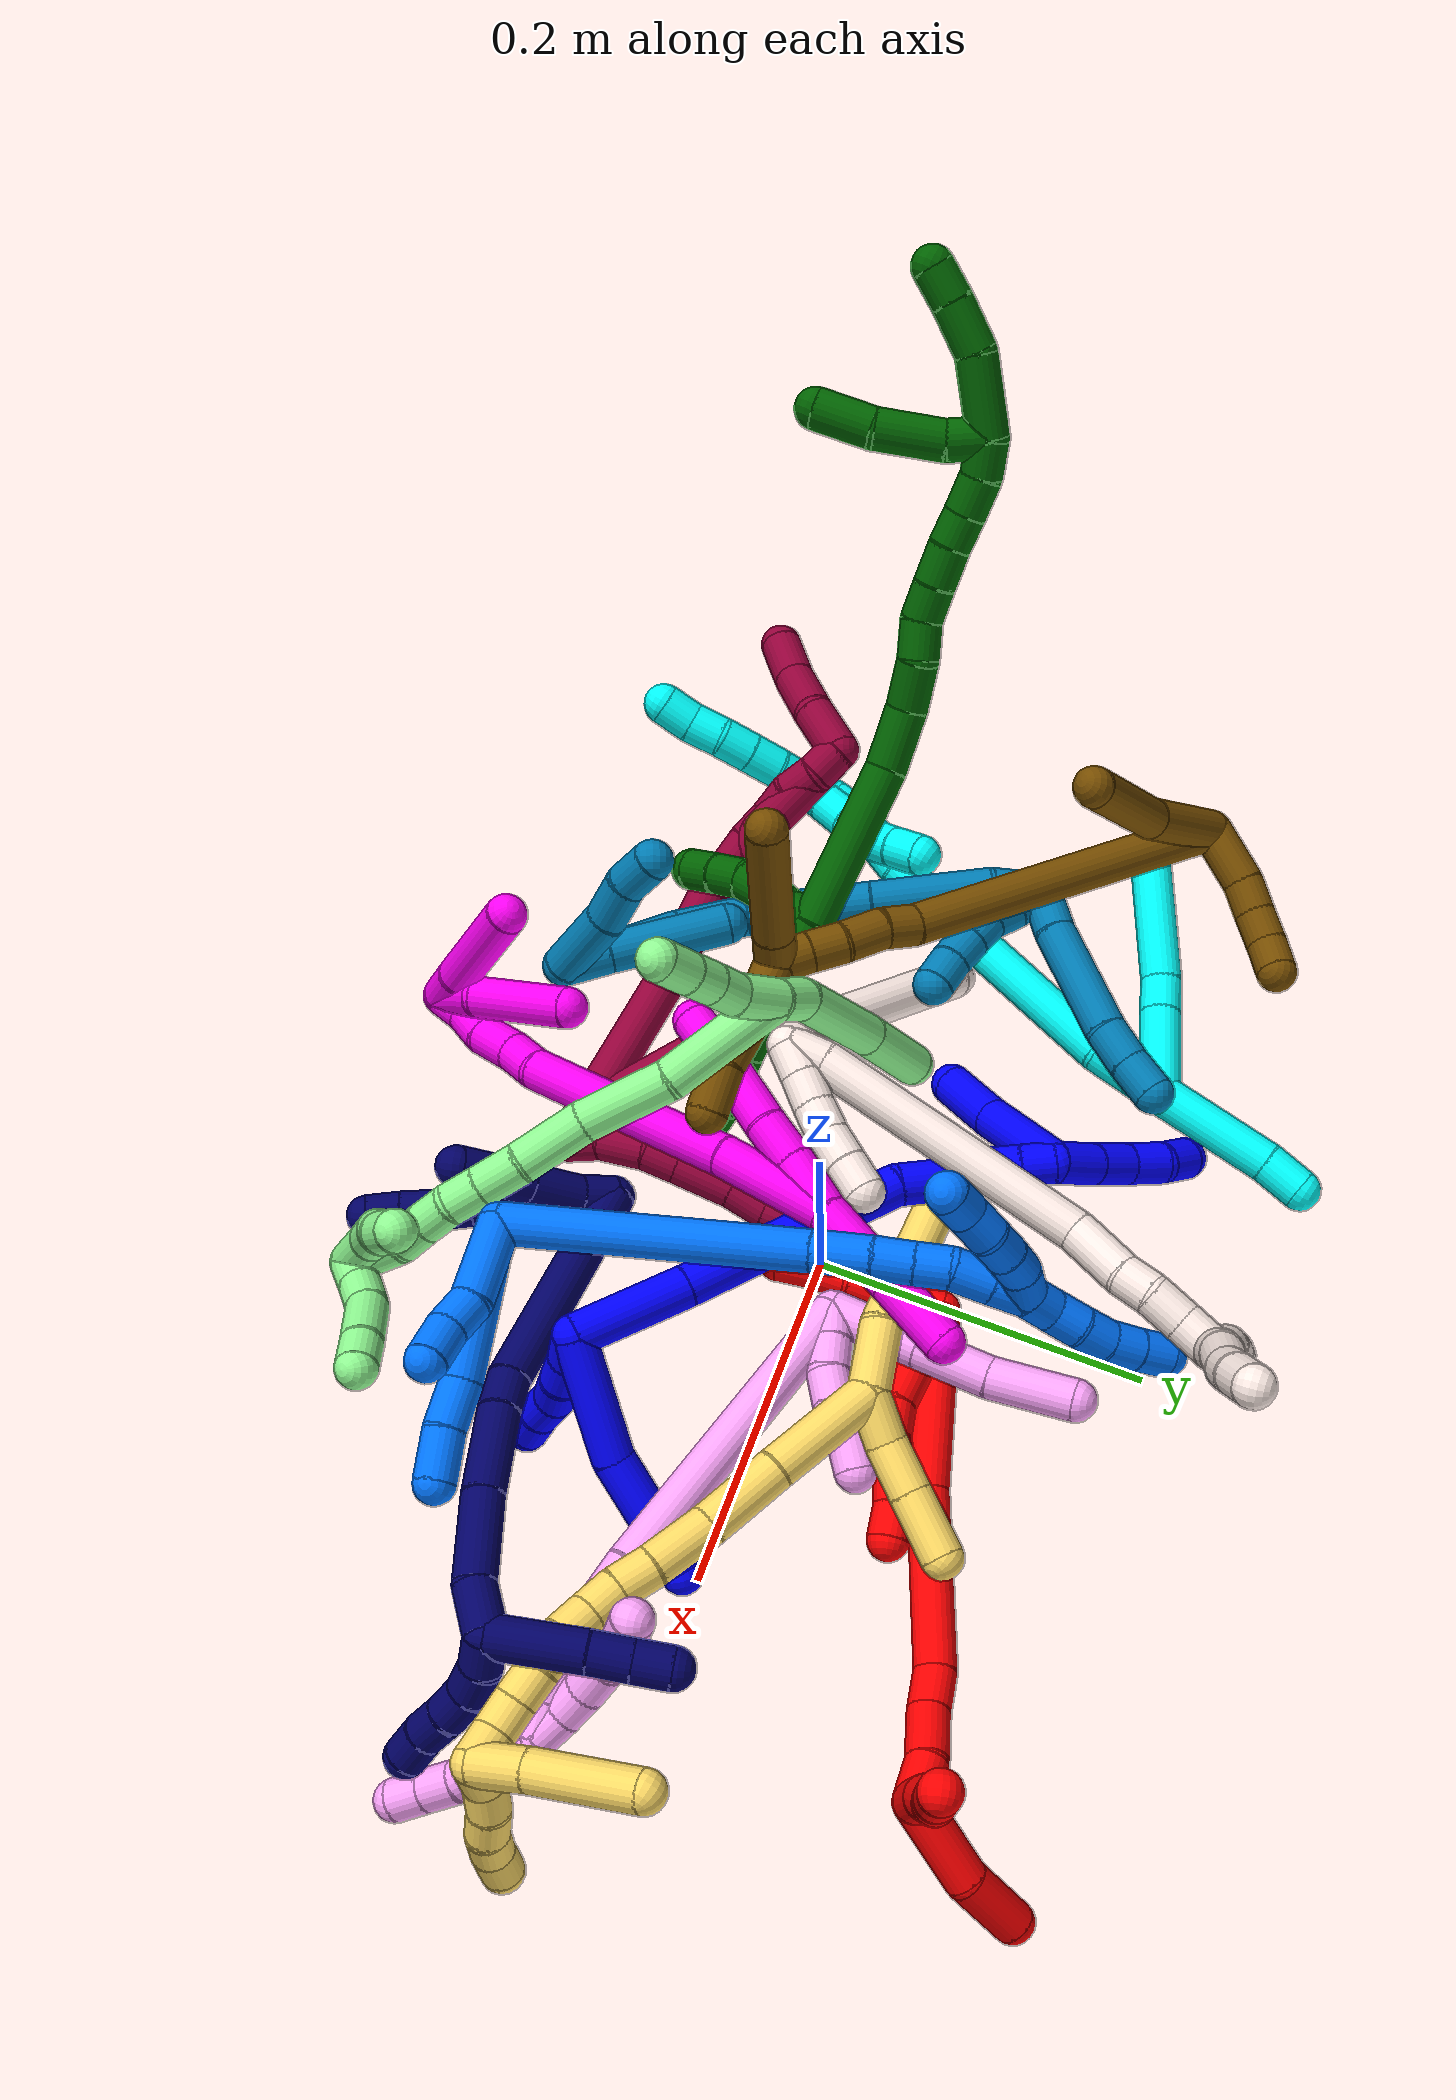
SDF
<sdf version="1.7">
 <world name="default">
  <plugin name="TubeGeneratorPlugin" filename="libtube_generator_plugin.so"/>
  <model name="photoneo_s_sensor">
   <static>1</static>
   <pose>0 0 2 1.57079 1.57079 3.14159</pose>
   <link name="link">
    <inertial><mass>0.1</mass></inertial>
    <sensor name="sensor" type="depth">
     <update_rate>30</update_rate>
     <camera>
      <horizontal_fov>1.22</horizontal_fov>
      <image><width>1920</width><height>1200</height><format>B8G8R8</format></image>
      <clip><near>0.1</near><far>4</far></clip>
      <depth_camera><output>points</output></depth_camera>
     </camera>
     <plugin name="camera_plugin" filename="libgazebo_ros_depth_camera.so">
      <baseline>0.2</baseline>
      <alwaysOn>1</alwaysOn>
      <updateRate>0.0</updateRate>
      <cameraName>camera_ir</cameraName>
      <imageTopicName>/camera/color/image_raw</imageTopicName>
      <cameraInfoTopicName>/camera/color/camera_info</cameraInfoTopicName>
      <depthImageTopicName>/camera/depth/image_raw</depthImageTopicName>
      <depthImageCameraInfoTopicName>/camera/depth/camera_info</depthImageCameraInfoTopicName>
      <pointCloudTopicName>/camera/depth/points</pointCloudTopicName>
      <frameName>fr_optical</frameName>
      <pointCloudCutoff>0.1</pointCloudCutoff>
      <pointCloudCutoffMax>2.0</pointCloudCutoffMax>
      <distortionK1>0</distortionK1>
      <distortionK2>0</distortionK2>
      <distortionK3>0</distortionK3>
      <distortionT1>0</distortionT1>
      <distortionT2>0</distortionT2>
      <CxPrime>0</CxPrime>
      <Cx>0</Cx>
      <Cy>0</Cy>
      <focalLength>0</focalLength>
      <hackBaseline>0</hackBaseline>
     </plugin>
    </sensor>
   </link>
  </model>
  <gravity>0 0 -9.8</gravity>
  <magnetic_field>6e-06 2.3e-05 -4.2e-05</magnetic_field>
  <atmosphere type="adiabatic"/>
  <physics name="default_physics" default="0" type="ode">
   <max_step_size>0.003</max_step_size>
   <real_time_factor>1</real_time_factor>
   <real_time_update_rate>1000</real_time_update_rate>
   <max_contacts>10000</max_contacts>
   <ode>
    <solver>
     <type>quick</type>
     <iters>100</iters>
     <sor>1.3</sor>
     <use_dynamic_moi_rescaling>0</use_dynamic_moi_rescaling>
    </solver>
    <constraints>
     <contact_max_correcting_vel>0</contact_max_correcting_vel>
     <contact_surface_layer>0.001</contact_surface_layer>
     <cfm>0</cfm>
     <erp>0.2</erp>
    </constraints>
   </ode>
  </physics>
  <scene><ambient>0.4 0.4 0.4 1</ambient><background>0.7 0.7 0.7 1</background><shadows>0</shadows></scene>
  <audio><device>default</device></audio>
  <spherical_coordinates>
   <surface_model>EARTH_WGS84</surface_model>
   <latitude_deg>0</latitude_deg>
   <longitude_deg>0</longitude_deg>
   <elevation>0</elevation>
   <heading_deg>0</heading_deg>
  </spherical_coordinates>
  <model name="bin">
   <static>1</static>
   <link name="bottom">
    <collision name="collision-bottom">
     <pose>0 0 -0.01 0 -0 0</pose>
     <geometry><box><size>0.8 0.6 0.02</size></box></geometry>
     <surface>
      <friction><ode><mu>100</mu><mu2>100</mu2></ode></friction>
      <contact><collide_bitmask>65535</collide_bitmask></contact>
     </surface>
    </collision>
   </link>
   <link name="west_wall">
    <collision name="collision-west_wall">
     <pose>-0.41 0 0.1 0 -0 0</pose>
     <geometry><box><size>0.02 0.6 0.2</size></box></geometry>
     <surface>
      <friction><ode><mu>100</mu><mu2>100</mu2></ode></friction>
      <contact><collide_bitmask>65535</collide_bitmask></contact>
     </surface>
    </collision>
   </link>
   <link name="east_wall">
    <collision name="collision-east_wall">
     <pose>0.41 0 0.1 0 -0 0</pose>
     <geometry><box><size>0.02 0.6 0.2</size></box></geometry>
     <surface>
      <friction><ode><mu>100</mu><mu2>100</mu2></ode></friction>
      <contact><collide_bitmask>65535</collide_bitmask></contact>
     </surface>
    </collision>
   </link>
   <link name="south_wall">
    <collision name="collision-south_wall">
     <pose>0 -0.31 0.1 0 -0 0</pose>
     <geometry><box><size>0.8 0.02 0.2</size></box></geometry>
     <surface>
      <friction><ode><mu>100</mu><mu2>100</mu2></ode></friction>
      <contact><collide_bitmask>65535</collide_bitmask></contact>
     </surface>
    </collision>
   </link>
   <link name="north_wall">
    <collision name="collision-north_wall">
     <pose>0 0.31 0.1 0 -0 0</pose>
     <geometry><box><size>0.8 0.02 0.2</size></box></geometry>
     <surface>
      <friction><ode><mu>100</mu><mu2>100</mu2></ode></friction>
      <contact><collide_bitmask>65535</collide_bitmask></contact>
     </surface>
    </collision>
   </link>
  </model>
  <model name="1">
   <static>0</static>
   <link name="1">
    <collision name="collision-cylinder-e_1_2_8">
     <pose>0.001529 0.001525 -0.037037 -3.10044 0.041235 -1.57283</pose>
     <geometry><cylinder><radius>0.0125</radius><length>0.074199</length></cylinder></geometry>
     <surface>
      <friction><ode><mu>1.16</mu><mu2>1.16</mu2><slip1>0</slip1><slip2>0</slip2></ode></friction>
      <contact><ode><kp>1e+06</kp><kd>1</kd><max_vel>0</max_vel><min_depth>0.001</min_depth></ode></contact>
     </surface>
    </collision>
    <visual name="visual-cylinder-e_1_2_8">
     <pose>0.001529 0.001525 -0.037037 -3.10044 0.041235 -1.57283</pose>
     <geometry><cylinder><radius>0.0125</radius><length>0.074199</length></cylinder></geometry>
     <material><ambient>0 0 1 1</ambient></material>
    </visual>
    <collision name="collision-cylinder-e_2_8_9">
     <pose>0.001996 0.010051 -0.097943 -2.85629 -0.042695 0.295147</pose>
     <geometry><cylinder><radius>0.0125</radius><length>0.049795</length></cylinder></geometry>
     <surface>
      <friction><ode><mu>1.16</mu><mu2>1.16</mu2><slip1>0</slip1><slip2>0</slip2></ode></friction>
      <contact><ode><kp>1e+06</kp><kd>1</kd><max_vel>0</max_vel><min_depth>0.001</min_depth></ode></contact>
     </surface>
    </collision>
    <visual name="visual-cylinder-e_2_8_9">
     <pose>0.001996 0.010051 -0.097943 -2.85629 -0.042695 0.295147</pose>
     <geometry><cylinder><radius>0.0125</radius><length>0.049795</length></cylinder></geometry>
     <material><ambient>0 0 1 1</ambient></material>
    </visual>
    <collision name="collision-cylinder-e_3_9_6">
     <pose>0.002757 0.022173 -0.133624 -2.73253 0.140691 -0.654915</pose>
     <geometry><cylinder><radius>0.0125</radius><length>0.026006</length></cylinder></geometry>
     <surface>
      <friction><ode><mu>1.16</mu><mu2>1.16</mu2><slip1>0</slip1><slip2>0</slip2></ode></friction>
      <contact><ode><kp>1e+06</kp><kd>1</kd><max_vel>0</max_vel><min_depth>0.001</min_depth></ode></contact>
     </surface>
    </collision>
    <visual name="visual-cylinder-e_3_9_6">
     <pose>0.002757 0.022173 -0.133624 -2.73253 0.140691 -0.654915</pose>
     <geometry><cylinder><radius>0.0125</radius><length>0.026006</length></cylinder></geometry>
     <material><ambient>0 0 1 1</ambient></material>
    </visual>
    <collision name="collision-cylinder-e_1_2_10">
     <pose>-0.002177 -0.005886 -0.007785 2.49424 -0.219502 -0.634739</pose>
     <geometry><cylinder><radius>0.0125</radius><length>0.02</length></cylinder></geometry>
     <surface>
      <friction><ode><mu>1.16</mu><mu2>1.16</mu2><slip1>0</slip1><slip2>0</slip2></ode></friction>
      <contact><ode><kp>1e+06</kp><kd>1</kd><max_vel>0</max_vel><min_depth>0.001</min_depth></ode></contact>
     </surface>
    </collision>
    <visual name="visual-cylinder-e_1_2_10">
     <pose>-0.002177 -0.005886 -0.007785 2.49424 -0.219502 -0.634739</pose>
     <geometry><cylinder><radius>0.0125</radius><length>0.02</length></cylinder></geometry>
     <material><ambient>0 0 1 1</ambient></material>
    </visual>
    <collision name="collision-cylinder-e_2_10_11">
     <pose>-0.005952 -0.018464 -0.022828 2.39672 -0.160362 -0.405705</pose>
     <geometry><cylinder><radius>0.0125</radius><length>0.02</length></cylinder></geometry>
     <surface>
      <friction><ode><mu>1.16</mu><mu2>1.16</mu2><slip1>0</slip1><slip2>0</slip2></ode></friction>
      <contact><ode><kp>1e+06</kp><kd>1</kd><max_vel>0</max_vel><min_depth>0.001</min_depth></ode></contact>
     </surface>
    </collision>
    <visual name="visual-cylinder-e_2_10_11">
     <pose>-0.005952 -0.018464 -0.022828 2.39672 -0.160362 -0.405705</pose>
     <geometry><cylinder><radius>0.0125</radius><length>0.02</length></cylinder></geometry>
     <material><ambient>0 0 1 1</ambient></material>
    </visual>
    <collision name="collision-cylinder-e_3_11_12">
     <pose>-0.010685 -0.031965 -0.036704 2.34196 -0.319053 -0.727589</pose>
     <geometry><cylinder><radius>0.0125</radius><length>0.02</length></cylinder></geometry>
     <surface>
      <friction><ode><mu>1.16</mu><mu2>1.16</mu2><slip1>0</slip1><slip2>0</slip2></ode></friction>
      <contact><ode><kp>1e+06</kp><kd>1</kd><max_vel>0</max_vel><min_depth>0.001</min_depth></ode></contact>
     </surface>
    </collision>
    <visual name="visual-cylinder-e_3_11_12">
     <pose>-0.010685 -0.031965 -0.036704 2.34196 -0.319053 -0.727589</pose>
     <geometry><cylinder><radius>0.0125</radius><length>0.02</length></cylinder></geometry>
     <material><ambient>0 0 1 1</ambient></material>
    </visual>
    <collision name="collision-cylinder-e_4_12_13">
     <pose>-0.015128 -0.047184 -0.048572 2.12891 -0.130977 -0.235424</pose>
     <geometry><cylinder><radius>0.0125</radius><length>0.02</length></cylinder></geometry>
     <surface>
      <friction><ode><mu>1.16</mu><mu2>1.16</mu2><slip1>0</slip1><slip2>0</slip2></ode></friction>
      <contact><ode><kp>1e+06</kp><kd>1</kd><max_vel>0</max_vel><min_depth>0.001</min_depth></ode></contact>
     </surface>
    </collision>
    <visual name="visual-cylinder-e_4_12_13">
     <pose>-0.015128 -0.047184 -0.048572 2.12891 -0.130977 -0.235424</pose>
     <geometry><cylinder><radius>0.0125</radius><length>0.02</length></cylinder></geometry>
     <material><ambient>0 0 1 1</ambient></material>
    </visual>
    <collision name="collision-cylinder-e_5_13_5">
     <pose>-0.018373 -0.06338 -0.05979 2.22475 -0.195186 -0.391699</pose>
     <geometry><cylinder><radius>0.0125</radius><length>0.02</length></cylinder></geometry>
     <surface>
      <friction><ode><mu>1.16</mu><mu2>1.16</mu2><slip1>0</slip1><slip2>0</slip2></ode></friction>
      <contact><ode><kp>1e+06</kp><kd>1</kd><max_vel>0</max_vel><min_depth>0.001</min_depth></ode></contact>
     </surface>
    </collision>
    <visual name="visual-cylinder-e_5_13_5">
     <pose>-0.018373 -0.06338 -0.05979 2.22475 -0.195186 -0.391699</pose>
     <geometry><cylinder><radius>0.0125</radius><length>0.02</length></cylinder></geometry>
     <material><ambient>0 0 1 1</ambient></material>
    </visual>
    <collision name="collision-cylinder-e_1_2_14">
     <pose>-0.026844 0.02166 0.001568 -1.49855 -0.890609 0.835675</pose>
     <geometry><cylinder><radius>0.0125</radius><length>0.069057</length></cylinder></geometry>
     <surface>
      <friction><ode><mu>1.16</mu><mu2>1.16</mu2><slip1>0</slip1><slip2>0</slip2></ode></friction>
      <contact><ode><kp>1e+06</kp><kd>1</kd><max_vel>0</max_vel><min_depth>0.001</min_depth></ode></contact>
     </surface>
    </collision>
    <visual name="visual-cylinder-e_1_2_14">
     <pose>-0.026844 0.02166 0.001568 -1.49855 -0.890609 0.835675</pose>
     <geometry><cylinder><radius>0.0125</radius><length>0.069057</length></cylinder></geometry>
     <material><ambient>0 0 1 1</ambient></material>
    </visual>
    <collision name="collision-cylinder-e_2_14_15">
     <pose>-0.106907 0.085562 0.008322 -1.44864 -0.896226 0.804282</pose>
     <geometry><cylinder><radius>0.0125</radius><length>0.136288</length></cylinder></geometry>
     <surface>
      <friction><ode><mu>1.16</mu><mu2>1.16</mu2><slip1>0</slip1><slip2>0</slip2></ode></friction>
      <contact><ode><kp>1e+06</kp><kd>1</kd><max_vel>0</max_vel><min_depth>0.001</min_depth></ode></contact>
     </surface>
    </collision>
    <visual name="visual-cylinder-e_2_14_15">
     <pose>-0.106907 0.085562 0.008322 -1.44864 -0.896226 0.804282</pose>
     <geometry><cylinder><radius>0.0125</radius><length>0.136288</length></cylinder></geometry>
     <material><ambient>0 0 1 1</ambient></material>
    </visual>
    <collision name="collision-cylinder-e_3_15_16">
     <pose>-0.172096 0.138869 0.009503 -1.9181 -0.793956 1.07732</pose>
     <geometry><cylinder><radius>0.0125</radius><length>0.03357</length></cylinder></geometry>
     <surface>
      <friction><ode><mu>1.16</mu><mu2>1.16</mu2><slip1>0</slip1><slip2>0</slip2></ode></friction>
      <contact><ode><kp>1e+06</kp><kd>1</kd><max_vel>0</max_vel><min_depth>0.001</min_depth></ode></contact>
     </surface>
    </collision>
    <visual name="visual-cylinder-e_3_15_16">
     <pose>-0.172096 0.138869 0.009503 -1.9181 -0.793956 1.07732</pose>
     <geometry><cylinder><radius>0.0125</radius><length>0.03357</length></cylinder></geometry>
     <material><ambient>0 0 1 1</ambient></material>
    </visual>
    <collision name="collision-cylinder-e_4_16_17">
     <pose>-0.191399 0.157045 0.004976 -1.64408 -0.799397 0.853327</pose>
     <geometry><cylinder><radius>0.0125</radius><length>0.020457</length></cylinder></geometry>
     <surface>
      <friction><ode><mu>1.16</mu><mu2>1.16</mu2><slip1>0</slip1><slip2>0</slip2></ode></friction>
      <contact><ode><kp>1e+06</kp><kd>1</kd><max_vel>0</max_vel><min_depth>0.001</min_depth></ode></contact>
     </surface>
    </collision>
    <visual name="visual-cylinder-e_4_16_17">
     <pose>-0.191399 0.157045 0.004976 -1.64408 -0.799397 0.853327</pose>
     <geometry><cylinder><radius>0.0125</radius><length>0.020457</length></cylinder></geometry>
     <material><ambient>0 0 1 1</ambient></material>
    </visual>
    <collision name="collision-cylinder-e_5_17_18">
     <pose>-0.203929 0.172819 0.002682 -1.77255 -0.531344 0.643611</pose>
     <geometry><cylinder><radius>0.0125</radius><length>0.020512</length></cylinder></geometry>
     <surface>
      <friction><ode><mu>1.16</mu><mu2>1.16</mu2><slip1>0</slip1><slip2>0</slip2></ode></friction>
      <contact><ode><kp>1e+06</kp><kd>1</kd><max_vel>0</max_vel><min_depth>0.001</min_depth></ode></contact>
     </surface>
    </collision>
    <visual name="visual-cylinder-e_5_17_18">
     <pose>-0.203929 0.172819 0.002682 -1.77255 -0.531344 0.643611</pose>
     <geometry><cylinder><radius>0.0125</radius><length>0.020512</length></cylinder></geometry>
     <material><ambient>0 0 1 1</ambient></material>
    </visual>
    <collision name="collision-cylinder-e_6_18_1">
     <pose>-0.21423 0.189968 -0.000851 -1.77537 -0.532263 0.646427</pose>
     <geometry><cylinder><radius>0.0125</radius><length>0.020116</length></cylinder></geometry>
     <surface>
      <friction><ode><mu>1.16</mu><mu2>1.16</mu2><slip1>0</slip1><slip2>0</slip2></ode></friction>
      <contact><ode><kp>1e+06</kp><kd>1</kd><max_vel>0</max_vel><min_depth>0.001</min_depth></ode></contact>
     </surface>
    </collision>
    <visual name="visual-cylinder-e_6_18_1">
     <pose>-0.21423 0.189968 -0.000851 -1.77537 -0.532263 0.646427</pose>
     <geometry><cylinder><radius>0.0125</radius><length>0.020116</length></cylinder></geometry>
     <material><ambient>0 0 1 1</ambient></material>
    </visual>
    <collision name="collision-cylinder-e_1_1_19">
     <pose>-0.231479 0.203587 -0.008623 -2.43483 -0.993809 1.94697</pose>
     <geometry><cylinder><radius>0.0125</radius><length>0.028981</length></cylinder></geometry>
     <surface>
      <friction><ode><mu>1.16</mu><mu2>1.16</mu2><slip1>0</slip1><slip2>0</slip2></ode></friction>
      <contact><ode><kp>1e+06</kp><kd>1</kd><max_vel>0</max_vel><min_depth>0.001</min_depth></ode></contact>
     </surface>
    </collision>
    <visual name="visual-cylinder-e_1_1_19">
     <pose>-0.231479 0.203587 -0.008623 -2.43483 -0.993809 1.94697</pose>
     <geometry><cylinder><radius>0.0125</radius><length>0.028981</length></cylinder></geometry>
     <material><ambient>0 0 1 1</ambient></material>
    </visual>
    <collision name="collision-cylinder-e_2_19_20">
     <pose>-0.254706 0.213336 -0.019508 -2.38334 -1.02617 1.91061</pose>
     <geometry><cylinder><radius>0.0125</radius><length>0.025916</length></cylinder></geometry>
     <surface>
      <friction><ode><mu>1.16</mu><mu2>1.16</mu2><slip1>0</slip1><slip2>0</slip2></ode></friction>
      <contact><ode><kp>1e+06</kp><kd>1</kd><max_vel>0</max_vel><min_depth>0.001</min_depth></ode></contact>
     </surface>
    </collision>
    <visual name="visual-cylinder-e_2_19_20">
     <pose>-0.254706 0.213336 -0.019508 -2.38334 -1.02617 1.91061</pose>
     <geometry><cylinder><radius>0.0125</radius><length>0.025916</length></cylinder></geometry>
     <material><ambient>0 0 1 1</ambient></material>
    </visual>
    <collision name="collision-cylinder-e_3_20_21">
     <pose>-0.274982 0.224625 -0.028309 -2.10274 -0.87086 1.36594</pose>
     <geometry><cylinder><radius>0.0125</radius><length>0.024038</length></cylinder></geometry>
     <surface>
      <friction><ode><mu>1.16</mu><mu2>1.16</mu2><slip1>0</slip1><slip2>0</slip2></ode></friction>
      <contact><ode><kp>1e+06</kp><kd>1</kd><max_vel>0</max_vel><min_depth>0.001</min_depth></ode></contact>
     </surface>
    </collision>
    <visual name="visual-cylinder-e_3_20_21">
     <pose>-0.274982 0.224625 -0.028309 -2.10274 -0.87086 1.36594</pose>
     <geometry><cylinder><radius>0.0125</radius><length>0.024038</length></cylinder></geometry>
     <material><ambient>0 0 1 1</ambient></material>
    </visual>
    <collision name="collision-cylinder-e_4_21_4">
     <pose>-0.29394 0.234046 -0.035073 -2.37207 -1.18635 2.05978</pose>
     <geometry><cylinder><radius>0.0125</radius><length>0.021066</length></cylinder></geometry>
     <surface>
      <friction><ode><mu>1.16</mu><mu2>1.16</mu2><slip1>0</slip1><slip2>0</slip2></ode></friction>
      <contact><ode><kp>1e+06</kp><kd>1</kd><max_vel>0</max_vel><min_depth>0.001</min_depth></ode></contact>
     </surface>
    </collision>
    <visual name="visual-cylinder-e_4_21_4">
     <pose>-0.29394 0.234046 -0.035073 -2.37207 -1.18635 2.05978</pose>
     <geometry><cylinder><radius>0.0125</radius><length>0.021066</length></cylinder></geometry>
     <material><ambient>0 0 1 1</ambient></material>
    </visual>
    <collision name="collision-cylinder-e_1_1_22">
     <pose>-0.232837 0.173839 0.007934 1.16603 -0.467038 -0.311194</pose>
     <geometry><cylinder><radius>0.0125</radius><length>0.059981</length></cylinder></geometry>
     <surface>
      <friction><ode><mu>1.16</mu><mu2>1.16</mu2><slip1>0</slip1><slip2>0</slip2></ode></friction>
      <contact><ode><kp>1e+06</kp><kd>1</kd><max_vel>0</max_vel><min_depth>0.001</min_depth></ode></contact>
     </surface>
    </collision>
    <visual name="visual-cylinder-e_1_1_22">
     <pose>-0.232837 0.173839 0.007934 1.16603 -0.467038 -0.311194</pose>
     <geometry><cylinder><radius>0.0125</radius><length>0.059981</length></cylinder></geometry>
     <material><ambient>0 0 1 1</ambient></material>
    </visual>
    <collision name="collision-cylinder-e_2_22_3">
     <pose>-0.25524 0.13357 0.027205 1.0623 -0.460922 -0.273946</pose>
     <geometry><cylinder><radius>0.0125</radius><length>0.040019</length></cylinder></geometry>
     <surface>
      <friction><ode><mu>1.16</mu><mu2>1.16</mu2><slip1>0</slip1><slip2>0</slip2></ode></friction>
      <contact><ode><kp>1e+06</kp><kd>1</kd><max_vel>0</max_vel><min_depth>0.001</min_depth></ode></contact>
     </surface>
    </collision>
    <visual name="visual-cylinder-e_2_22_3">
     <pose>-0.25524 0.13357 0.027205 1.0623 -0.460922 -0.273946</pose>
     <geometry><cylinder><radius>0.0125</radius><length>0.040019</length></cylinder></geometry>
     <material><ambient>0 0 1 1</ambient></material>
    </visual>
    <collision name="collision-sphere-3">
     <pose>-0.26414 0.117916 0.03593 0 -0 0</pose>
     <geometry><sphere><radius>0.0125</radius></sphere></geometry>
     <surface>
      <friction><ode><mu>1.16</mu><mu2>1.16</mu2><slip1>0</slip1><slip2>0</slip2></ode></friction>
      <contact><ode><kp>1e+06</kp><kd>1</kd><max_vel>0</max_vel><min_depth>0.001</min_depth></ode></contact>
     </surface>
    </collision>
    <visual name="visual-sphere-3">
     <pose>-0.26414 0.117916 0.03593 0 -0 0</pose>
     <geometry><sphere><radius>0.0125</radius></sphere></geometry>
     <material><ambient>0 0 1 1</ambient></material>
    </visual>
    <collision name="collision-sphere-22">
     <pose>-0.24634 0.149224 0.018479 0 -0 0</pose>
     <geometry><sphere><radius>0.0125</radius></sphere></geometry>
     <surface>
      <friction><ode><mu>1.16</mu><mu2>1.16</mu2><slip1>0</slip1><slip2>0</slip2></ode></friction>
      <contact><ode><kp>1e+06</kp><kd>1</kd><max_vel>0</max_vel><min_depth>0.001</min_depth></ode></contact>
     </surface>
    </collision>
    <visual name="visual-sphere-22">
     <pose>-0.24634 0.149224 0.018479 0 -0 0</pose>
     <geometry><sphere><radius>0.0125</radius></sphere></geometry>
     <material><ambient>0 0 1 1</ambient></material>
    </visual>
    <collision name="collision-sphere-4">
     <pose>-0.303704 0.236795 -0.037911 0 -0 0</pose>
     <geometry><sphere><radius>0.0125</radius></sphere></geometry>
     <surface>
      <friction><ode><mu>1.16</mu><mu2>1.16</mu2><slip1>0</slip1><slip2>0</slip2></ode></friction>
      <contact><ode><kp>1e+06</kp><kd>1</kd><max_vel>0</max_vel><min_depth>0.001</min_depth></ode></contact>
     </surface>
    </collision>
    <visual name="visual-sphere-4">
     <pose>-0.303704 0.236795 -0.037911 0 -0 0</pose>
     <geometry><sphere><radius>0.0125</radius></sphere></geometry>
     <material><ambient>0 0 1 1</ambient></material>
    </visual>
    <collision name="collision-sphere-21">
     <pose>-0.284175 0.231298 -0.032236 0 -0 0</pose>
     <geometry><sphere><radius>0.0125</radius></sphere></geometry>
     <surface>
      <friction><ode><mu>1.16</mu><mu2>1.16</mu2><slip1>0</slip1><slip2>0</slip2></ode></friction>
      <contact><ode><kp>1e+06</kp><kd>1</kd><max_vel>0</max_vel><min_depth>0.001</min_depth></ode></contact>
     </surface>
    </collision>
    <visual name="visual-sphere-21">
     <pose>-0.284175 0.231298 -0.032236 0 -0 0</pose>
     <geometry><sphere><radius>0.0125</radius></sphere></geometry>
     <material><ambient>0 0 1 1</ambient></material>
    </visual>
    <collision name="collision-sphere-20">
     <pose>-0.265789 0.217953 -0.024382 0 -0 0</pose>
     <geometry><sphere><radius>0.0125</radius></sphere></geometry>
     <surface>
      <friction><ode><mu>1.16</mu><mu2>1.16</mu2><slip1>0</slip1><slip2>0</slip2></ode></friction>
      <contact><ode><kp>1e+06</kp><kd>1</kd><max_vel>0</max_vel><min_depth>0.001</min_depth></ode></contact>
     </surface>
    </collision>
    <visual name="visual-sphere-20">
     <pose>-0.265789 0.217953 -0.024382 0 -0 0</pose>
     <geometry><sphere><radius>0.0125</radius></sphere></geometry>
     <material><ambient>0 0 1 1</ambient></material>
    </visual>
    <collision name="collision-sphere-11">
     <pose>-0.007548 -0.025156 -0.030086 0 -0 0</pose>
     <geometry><sphere><radius>0.0125</radius></sphere></geometry>
     <surface>
      <friction><ode><mu>1.16</mu><mu2>1.16</mu2><slip1>0</slip1><slip2>0</slip2></ode></friction>
      <contact><ode><kp>1e+06</kp><kd>1</kd><max_vel>0</max_vel><min_depth>0.001</min_depth></ode></contact>
     </surface>
    </collision>
    <visual name="visual-sphere-11">
     <pose>-0.007548 -0.025156 -0.030086 0 -0 0</pose>
     <geometry><sphere><radius>0.0125</radius></sphere></geometry>
     <material><ambient>0 0 1 1</ambient></material>
    </visual>
    <collision name="collision-sphere-10">
     <pose>-0.004355 -0.011772 -0.015571 0 -0 0</pose>
     <geometry><sphere><radius>0.0125</radius></sphere></geometry>
     <surface>
      <friction><ode><mu>1.16</mu><mu2>1.16</mu2><slip1>0</slip1><slip2>0</slip2></ode></friction>
      <contact><ode><kp>1e+06</kp><kd>1</kd><max_vel>0</max_vel><min_depth>0.001</min_depth></ode></contact>
     </surface>
    </collision>
    <visual name="visual-sphere-10">
     <pose>-0.004355 -0.011772 -0.015571 0 -0 0</pose>
     <geometry><sphere><radius>0.0125</radius></sphere></geometry>
     <material><ambient>0 0 1 1</ambient></material>
    </visual>
    <collision name="collision-sphere-6">
     <pose>0.00458 0.027293 -0.145436 0 -0 0</pose>
     <geometry><sphere><radius>0.0125</radius></sphere></geometry>
     <surface>
      <friction><ode><mu>1.16</mu><mu2>1.16</mu2><slip1>0</slip1><slip2>0</slip2></ode></friction>
      <contact><ode><kp>1e+06</kp><kd>1</kd><max_vel>0</max_vel><min_depth>0.001</min_depth></ode></contact>
     </surface>
    </collision>
    <visual name="visual-sphere-6">
     <pose>0.00458 0.027293 -0.145436 0 -0 0</pose>
     <geometry><sphere><radius>0.0125</radius></sphere></geometry>
     <material><ambient>0 0 1 1</ambient></material>
    </visual>
    <collision name="collision-sphere-9">
     <pose>0.000933 0.017052 -0.121812 0 -0 0</pose>
     <geometry><sphere><radius>0.0125</radius></sphere></geometry>
     <surface>
      <friction><ode><mu>1.16</mu><mu2>1.16</mu2><slip1>0</slip1><slip2>0</slip2></ode></friction>
      <contact><ode><kp>1e+06</kp><kd>1</kd><max_vel>0</max_vel><min_depth>0.001</min_depth></ode></contact>
     </surface>
    </collision>
    <visual name="visual-sphere-9">
     <pose>0.000933 0.017052 -0.121812 0 -0 0</pose>
     <geometry><sphere><radius>0.0125</radius></sphere></geometry>
     <material><ambient>0 0 1 1</ambient></material>
    </visual>
    <collision name="collision-sphere-2">
     <geometry><sphere><radius>0.0125</radius></sphere></geometry>
     <surface>
      <friction><ode><mu>1.16</mu><mu2>1.16</mu2><slip1>0</slip1><slip2>0</slip2></ode></friction>
      <contact><ode><kp>1e+06</kp><kd>1</kd><max_vel>0</max_vel><min_depth>0.001</min_depth></ode></contact>
     </surface>
    </collision>
    <visual name="visual-sphere-2">
     <geometry><sphere><radius>0.0125</radius></sphere></geometry>
     <material><ambient>0 0 1 1</ambient></material>
    </visual>
    <collision name="collision-sphere-19">
     <pose>-0.243623 0.20872 -0.014634 0 -0 0</pose>
     <geometry><sphere><radius>0.0125</radius></sphere></geometry>
     <surface>
      <friction><ode><mu>1.16</mu><mu2>1.16</mu2><slip1>0</slip1><slip2>0</slip2></ode></friction>
      <contact><ode><kp>1e+06</kp><kd>1</kd><max_vel>0</max_vel><min_depth>0.001</min_depth></ode></contact>
     </surface>
    </collision>
    <visual name="visual-sphere-19">
     <pose>-0.243623 0.20872 -0.014634 0 -0 0</pose>
     <geometry><sphere><radius>0.0125</radius></sphere></geometry>
     <material><ambient>0 0 1 1</ambient></material>
    </visual>
    <collision name="collision-sphere-8">
     <pose>0.003059 0.00305 -0.074073 0 -0 0</pose>
     <geometry><sphere><radius>0.0125</radius></sphere></geometry>
     <surface>
      <friction><ode><mu>1.16</mu><mu2>1.16</mu2><slip1>0</slip1><slip2>0</slip2></ode></friction>
      <contact><ode><kp>1e+06</kp><kd>1</kd><max_vel>0</max_vel><min_depth>0.001</min_depth></ode></contact>
     </surface>
    </collision>
    <visual name="visual-sphere-8">
     <pose>0.003059 0.00305 -0.074073 0 -0 0</pose>
     <geometry><sphere><radius>0.0125</radius></sphere></geometry>
     <material><ambient>0 0 1 1</ambient></material>
    </visual>
    <collision name="collision-sphere-12">
     <pose>-0.013822 -0.038774 -0.043322 0 -0 0</pose>
     <geometry><sphere><radius>0.0125</radius></sphere></geometry>
     <surface>
      <friction><ode><mu>1.16</mu><mu2>1.16</mu2><slip1>0</slip1><slip2>0</slip2></ode></friction>
      <contact><ode><kp>1e+06</kp><kd>1</kd><max_vel>0</max_vel><min_depth>0.001</min_depth></ode></contact>
     </surface>
    </collision>
    <visual name="visual-sphere-12">
     <pose>-0.013822 -0.038774 -0.043322 0 -0 0</pose>
     <geometry><sphere><radius>0.0125</radius></sphere></geometry>
     <material><ambient>0 0 1 1</ambient></material>
    </visual>
    <collision name="collision-sphere-13">
     <pose>-0.016434 -0.055594 -0.053823 0 -0 0</pose>
     <geometry><sphere><radius>0.0125</radius></sphere></geometry>
     <surface>
      <friction><ode><mu>1.16</mu><mu2>1.16</mu2><slip1>0</slip1><slip2>0</slip2></ode></friction>
      <contact><ode><kp>1e+06</kp><kd>1</kd><max_vel>0</max_vel><min_depth>0.001</min_depth></ode></contact>
     </surface>
    </collision>
    <visual name="visual-sphere-13">
     <pose>-0.016434 -0.055594 -0.053823 0 -0 0</pose>
     <geometry><sphere><radius>0.0125</radius></sphere></geometry>
     <material><ambient>0 0 1 1</ambient></material>
    </visual>
    <collision name="collision-sphere-5">
     <pose>-0.020313 -0.071166 -0.065758 0 -0 0</pose>
     <geometry><sphere><radius>0.0125</radius></sphere></geometry>
     <surface>
      <friction><ode><mu>1.16</mu><mu2>1.16</mu2><slip1>0</slip1><slip2>0</slip2></ode></friction>
      <contact><ode><kp>1e+06</kp><kd>1</kd><max_vel>0</max_vel><min_depth>0.001</min_depth></ode></contact>
     </surface>
    </collision>
    <visual name="visual-sphere-5">
     <pose>-0.020313 -0.071166 -0.065758 0 -0 0</pose>
     <geometry><sphere><radius>0.0125</radius></sphere></geometry>
     <material><ambient>0 0 1 1</ambient></material>
    </visual>
    <collision name="collision-sphere-14">
     <pose>-0.053689 0.043319 0.003135 0 -0 0</pose>
     <geometry><sphere><radius>0.0125</radius></sphere></geometry>
     <surface>
      <friction><ode><mu>1.16</mu><mu2>1.16</mu2><slip1>0</slip1><slip2>0</slip2></ode></friction>
      <contact><ode><kp>1e+06</kp><kd>1</kd><max_vel>0</max_vel><min_depth>0.001</min_depth></ode></contact>
     </surface>
    </collision>
    <visual name="visual-sphere-14">
     <pose>-0.053689 0.043319 0.003135 0 -0 0</pose>
     <geometry><sphere><radius>0.0125</radius></sphere></geometry>
     <material><ambient>0 0 1 1</ambient></material>
    </visual>
    <collision name="collision-sphere-15">
     <pose>-0.160126 0.127805 0.013508 0 -0 0</pose>
     <geometry><sphere><radius>0.0125</radius></sphere></geometry>
     <surface>
      <friction><ode><mu>1.16</mu><mu2>1.16</mu2><slip1>0</slip1><slip2>0</slip2></ode></friction>
      <contact><ode><kp>1e+06</kp><kd>1</kd><max_vel>0</max_vel><min_depth>0.001</min_depth></ode></contact>
     </surface>
    </collision>
    <visual name="visual-sphere-15">
     <pose>-0.160126 0.127805 0.013508 0 -0 0</pose>
     <geometry><sphere><radius>0.0125</radius></sphere></geometry>
     <material><ambient>0 0 1 1</ambient></material>
    </visual>
    <collision name="collision-sphere-16">
     <pose>-0.184066 0.149933 0.005498 0 -0 0</pose>
     <geometry><sphere><radius>0.0125</radius></sphere></geometry>
     <surface>
      <friction><ode><mu>1.16</mu><mu2>1.16</mu2><slip1>0</slip1><slip2>0</slip2></ode></friction>
      <contact><ode><kp>1e+06</kp><kd>1</kd><max_vel>0</max_vel><min_depth>0.001</min_depth></ode></contact>
     </surface>
    </collision>
    <visual name="visual-sphere-16">
     <pose>-0.184066 0.149933 0.005498 0 -0 0</pose>
     <geometry><sphere><radius>0.0125</radius></sphere></geometry>
     <material><ambient>0 0 1 1</ambient></material>
    </visual>
    <collision name="collision-sphere-17">
     <pose>-0.198732 0.164156 0.004454 0 -0 0</pose>
     <geometry><sphere><radius>0.0125</radius></sphere></geometry>
     <surface>
      <friction><ode><mu>1.16</mu><mu2>1.16</mu2><slip1>0</slip1><slip2>0</slip2></ode></friction>
      <contact><ode><kp>1e+06</kp><kd>1</kd><max_vel>0</max_vel><min_depth>0.001</min_depth></ode></contact>
     </surface>
    </collision>
    <visual name="visual-sphere-17">
     <pose>-0.198732 0.164156 0.004454 0 -0 0</pose>
     <geometry><sphere><radius>0.0125</radius></sphere></geometry>
     <material><ambient>0 0 1 1</ambient></material>
    </visual>
    <collision name="collision-sphere-18">
     <pose>-0.209125 0.181482 0.00091 0 -0 0</pose>
     <geometry><sphere><radius>0.0125</radius></sphere></geometry>
     <surface>
      <friction><ode><mu>1.16</mu><mu2>1.16</mu2><slip1>0</slip1><slip2>0</slip2></ode></friction>
      <contact><ode><kp>1e+06</kp><kd>1</kd><max_vel>0</max_vel><min_depth>0.001</min_depth></ode></contact>
     </surface>
    </collision>
    <visual name="visual-sphere-18">
     <pose>-0.209125 0.181482 0.00091 0 -0 0</pose>
     <geometry><sphere><radius>0.0125</radius></sphere></geometry>
     <material><ambient>0 0 1 1</ambient></material>
    </visual>
    <collision name="collision-sphere-1">
     <pose>-0.219334 0.198454 -0.002611 0 -0 0</pose>
     <geometry><sphere><radius>0.0125</radius></sphere></geometry>
     <surface>
      <friction><ode><mu>1.16</mu><mu2>1.16</mu2><slip1>0</slip1><slip2>0</slip2></ode></friction>
      <contact><ode><kp>1e+06</kp><kd>1</kd><max_vel>0</max_vel><min_depth>0.001</min_depth></ode></contact>
     </surface>
    </collision>
    <visual name="visual-sphere-1">
     <pose>-0.219334 0.198454 -0.002611 0 -0 0</pose>
     <geometry><sphere><radius>0.0125</radius></sphere></geometry>
     <material><ambient>0 0 1 1</ambient></material>
    </visual>
    <inertial>
     <pose>-0.114217 0.085042 -0.01803 0 -0 0</pose>
     <mass>0.75</mass>
     <inertia><ixx>0.0002</ixx><ixy>0</ixy><ixz>0</ixz><iyy>0.00025</iyy><iyz>0</iyz><izz>6e-05</izz></inertia>
    </inertial>
   </link>
   <pose>0.111857 -0.103492 0.099211 0.774034 -0.698314 -0.309905</pose>
  </model>
  <model name="2">
   <static>0</static>
   <link name="2">
    <collision name="collision-cylinder-e_1_2_8">
     <pose>-0.012205 0.004741 0.031606 -0.148886 -0.364791 0.027511</pose>
     <geometry><cylinder><radius>0.0125</radius><length>0.068421</length></cylinder></geometry>
     <surface>
      <friction><ode><mu>1.16</mu><mu2>1.16</mu2><slip1>0</slip1><slip2>0</slip2></ode></friction>
      <contact><ode><kp>1e+06</kp><kd>1</kd><max_vel>0</max_vel><min_depth>0.001</min_depth></ode></contact>
     </surface>
    </collision>
    <visual name="visual-cylinder-e_1_2_8">
     <pose>-0.012205 0.004741 0.031606 -0.148886 -0.364791 0.027511</pose>
     <geometry><cylinder><radius>0.0125</radius><length>0.068421</length></cylinder></geometry>
     <material><ambient>1 0 0 1</ambient></material>
    </visual>
    <collision name="collision-cylinder-e_2_8_9">
     <pose>-0.025215 0.010417 0.073524 -0.090457 -0.077685 0.003518</pose>
     <geometry><cylinder><radius>0.0125</radius><length>0.020772</length></cylinder></geometry>
     <surface>
      <friction><ode><mu>1.16</mu><mu2>1.16</mu2><slip1>0</slip1><slip2>0</slip2></ode></friction>
      <contact><ode><kp>1e+06</kp><kd>1</kd><max_vel>0</max_vel><min_depth>0.001</min_depth></ode></contact>
     </surface>
    </collision>
    <visual name="visual-cylinder-e_2_8_9">
     <pose>-0.025215 0.010417 0.073524 -0.090457 -0.077685 0.003518</pose>
     <geometry><cylinder><radius>0.0125</radius><length>0.020772</length></cylinder></geometry>
     <material><ambient>1 0 0 1</ambient></material>
    </visual>
    <collision name="collision-cylinder-e_3_9_10">
     <pose>-0.023762 0.013431 0.093607 -0.209628 0.222455 -0.023498</pose>
     <geometry><cylinder><radius>0.0125</radius><length>0.020484</length></cylinder></geometry>
     <surface>
      <friction><ode><mu>1.16</mu><mu2>1.16</mu2><slip1>0</slip1><slip2>0</slip2></ode></friction>
      <contact><ode><kp>1e+06</kp><kd>1</kd><max_vel>0</max_vel><min_depth>0.001</min_depth></ode></contact>
     </surface>
    </collision>
    <visual name="visual-cylinder-e_3_9_10">
     <pose>-0.023762 0.013431 0.093607 -0.209628 0.222455 -0.023498</pose>
     <geometry><cylinder><radius>0.0125</radius><length>0.020484</length></cylinder></geometry>
     <material><ambient>1 0 0 1</ambient></material>
    </visual>
    <collision name="collision-cylinder-e_4_10_11">
     <pose>-0.020814 0.017077 0.113368 -0.155624 0.067905 -0.005297</pose>
     <geometry><cylinder><radius>0.0125</radius><length>0.020271</length></cylinder></geometry>
     <surface>
      <friction><ode><mu>1.16</mu><mu2>1.16</mu2><slip1>0</slip1><slip2>0</slip2></ode></friction>
      <contact><ode><kp>1e+06</kp><kd>1</kd><max_vel>0</max_vel><min_depth>0.001</min_depth></ode></contact>
     </surface>
    </collision>
    <visual name="visual-cylinder-e_4_10_11">
     <pose>-0.020814 0.017077 0.113368 -0.155624 0.067905 -0.005297</pose>
     <geometry><cylinder><radius>0.0125</radius><length>0.020271</length></cylinder></geometry>
     <material><ambient>1 0 0 1</ambient></material>
    </visual>
    <collision name="collision-cylinder-e_5_11_6">
     <pose>-0.020844 0.018422 0.133356 0.022287 -0.071597 -0.000798</pose>
     <geometry><cylinder><radius>0.0125</radius><length>0.020052</length></cylinder></geometry>
     <surface>
      <friction><ode><mu>1.16</mu><mu2>1.16</mu2><slip1>0</slip1><slip2>0</slip2></ode></friction>
      <contact><ode><kp>1e+06</kp><kd>1</kd><max_vel>0</max_vel><min_depth>0.001</min_depth></ode></contact>
     </surface>
    </collision>
    <visual name="visual-cylinder-e_5_11_6">
     <pose>-0.020844 0.018422 0.133356 0.022287 -0.071597 -0.000798</pose>
     <geometry><cylinder><radius>0.0125</radius><length>0.020052</length></cylinder></geometry>
     <material><ambient>1 0 0 1</ambient></material>
    </visual>
    <collision name="collision-cylinder-e_1_2_12">
     <pose>-0.026583 -0.007279 -0.005539 2.22133 -1.23941 -1.92733</pose>
     <geometry><cylinder><radius>0.0125</radius><length>0.056225</length></cylinder></geometry>
     <surface>
      <friction><ode><mu>1.16</mu><mu2>1.16</mu2><slip1>0</slip1><slip2>0</slip2></ode></friction>
      <contact><ode><kp>1e+06</kp><kd>1</kd><max_vel>0</max_vel><min_depth>0.001</min_depth></ode></contact>
     </surface>
    </collision>
    <visual name="visual-cylinder-e_1_2_12">
     <pose>-0.026583 -0.007279 -0.005539 2.22133 -1.23941 -1.92733</pose>
     <geometry><cylinder><radius>0.0125</radius><length>0.056225</length></cylinder></geometry>
     <material><ambient>1 0 0 1</ambient></material>
    </visual>
    <collision name="collision-cylinder-e_2_12_13">
     <pose>-0.061969 -0.019367 -0.013754 2.07842 -1.01208 -1.51149</pose>
     <geometry><cylinder><radius>0.0125</radius><length>0.020764</length></cylinder></geometry>
     <surface>
      <friction><ode><mu>1.16</mu><mu2>1.16</mu2><slip1>0</slip1><slip2>0</slip2></ode></friction>
      <contact><ode><kp>1e+06</kp><kd>1</kd><max_vel>0</max_vel><min_depth>0.001</min_depth></ode></contact>
     </surface>
    </collision>
    <visual name="visual-cylinder-e_2_12_13">
     <pose>-0.061969 -0.019367 -0.013754 2.07842 -1.01208 -1.51149</pose>
     <geometry><cylinder><radius>0.0125</radius><length>0.020764</length></cylinder></geometry>
     <material><ambient>1 0 0 1</ambient></material>
    </visual>
    <collision name="collision-cylinder-e_3_13_5">
     <pose>-0.081246 -0.028734 -0.01781 1.86496 -1.14407 -1.42948</pose>
     <geometry><cylinder><radius>0.0125</radius><length>0.023011</length></cylinder></geometry>
     <surface>
      <friction><ode><mu>1.16</mu><mu2>1.16</mu2><slip1>0</slip1><slip2>0</slip2></ode></friction>
      <contact><ode><kp>1e+06</kp><kd>1</kd><max_vel>0</max_vel><min_depth>0.001</min_depth></ode></contact>
     </surface>
    </collision>
    <visual name="visual-cylinder-e_3_13_5">
     <pose>-0.081246 -0.028734 -0.01781 1.86496 -1.14407 -1.42948</pose>
     <geometry><cylinder><radius>0.0125</radius><length>0.023011</length></cylinder></geometry>
     <material><ambient>1 0 0 1</ambient></material>
    </visual>
    <collision name="collision-cylinder-e_1_2_14">
     <pose>0.002924 -0.000577 0.053054 0.010874 0.055052 0.000299</pose>
     <geometry><cylinder><radius>0.0125</radius><length>0.106275</length></cylinder></geometry>
     <surface>
      <friction><ode><mu>1.16</mu><mu2>1.16</mu2><slip1>0</slip1><slip2>0</slip2></ode></friction>
      <contact><ode><kp>1e+06</kp><kd>1</kd><max_vel>0</max_vel><min_depth>0.001</min_depth></ode></contact>
     </surface>
    </collision>
    <visual name="visual-cylinder-e_1_2_14">
     <pose>0.002924 -0.000577 0.053054 0.010874 0.055052 0.000299</pose>
     <geometry><cylinder><radius>0.0125</radius><length>0.106275</length></cylinder></geometry>
     <material><ambient>1 0 0 1</ambient></material>
    </visual>
    <collision name="collision-cylinder-e_2_14_15">
     <pose>0.010079 0.00975 0.158779 -0.204126 0.078497 -0.008044</pose>
     <geometry><cylinder><radius>0.0125</radius><length>0.107909</length></cylinder></geometry>
     <surface>
      <friction><ode><mu>1.16</mu><mu2>1.16</mu2><slip1>0</slip1><slip2>0</slip2></ode></friction>
      <contact><ode><kp>1e+06</kp><kd>1</kd><max_vel>0</max_vel><min_depth>0.001</min_depth></ode></contact>
     </surface>
    </collision>
    <visual name="visual-cylinder-e_2_14_15">
     <pose>0.010079 0.00975 0.158779 -0.204126 0.078497 -0.008044</pose>
     <geometry><cylinder><radius>0.0125</radius><length>0.107909</length></cylinder></geometry>
     <material><ambient>1 0 0 1</ambient></material>
    </visual>
    <collision name="collision-cylinder-e_3_15_16">
     <pose>0.012383 0.024004 0.22345 -0.272338 -0.153415 0.021061</pose>
     <geometry><cylinder><radius>0.0125</radius><length>0.025213</length></cylinder></geometry>
     <surface>
      <friction><ode><mu>1.16</mu><mu2>1.16</mu2><slip1>0</slip1><slip2>0</slip2></ode></friction>
      <contact><ode><kp>1e+06</kp><kd>1</kd><max_vel>0</max_vel><min_depth>0.001</min_depth></ode></contact>
     </surface>
    </collision>
    <visual name="visual-cylinder-e_3_15_16">
     <pose>0.012383 0.024004 0.22345 -0.272338 -0.153415 0.021061</pose>
     <geometry><cylinder><radius>0.0125</radius><length>0.025213</length></cylinder></geometry>
     <material><ambient>1 0 0 1</ambient></material>
    </visual>
    <collision name="collision-cylinder-e_4_16_17">
     <pose>0.008235 0.036196 0.250255 -0.538302 -0.128114 0.035384</pose>
     <geometry><cylinder><radius>0.0125</radius><length>0.034774</length></cylinder></geometry>
     <surface>
      <friction><ode><mu>1.16</mu><mu2>1.16</mu2><slip1>0</slip1><slip2>0</slip2></ode></friction>
      <contact><ode><kp>1e+06</kp><kd>1</kd><max_vel>0</max_vel><min_depth>0.001</min_depth></ode></contact>
     </surface>
    </collision>
    <visual name="visual-cylinder-e_4_16_17">
     <pose>0.008235 0.036196 0.250255 -0.538302 -0.128114 0.035384</pose>
     <geometry><cylinder><radius>0.0125</radius><length>0.034774</length></cylinder></geometry>
     <material><ambient>1 0 0 1</ambient></material>
    </visual>
    <collision name="collision-cylinder-e_5_17_1">
     <pose>0.002226 0.049232 0.276673 -0.34668 -0.297718 0.052506</pose>
     <geometry><cylinder><radius>0.0125</radius><length>0.025829</length></cylinder></geometry>
     <surface>
      <friction><ode><mu>1.16</mu><mu2>1.16</mu2><slip1>0</slip1><slip2>0</slip2></ode></friction>
      <contact><ode><kp>1e+06</kp><kd>1</kd><max_vel>0</max_vel><min_depth>0.001</min_depth></ode></contact>
     </surface>
    </collision>
    <visual name="visual-cylinder-e_5_17_1">
     <pose>0.002226 0.049232 0.276673 -0.34668 -0.297718 0.052506</pose>
     <geometry><cylinder><radius>0.0125</radius><length>0.025829</length></cylinder></geometry>
     <material><ambient>1 0 0 1</ambient></material>
    </visual>
    <collision name="collision-cylinder-e_1_1_18">
     <pose>-0.003456 0.065913 0.288271 -1.57188 -0.150517 0.150679</pose>
     <geometry><cylinder><radius>0.0125</radius><length>0.025256</length></cylinder></geometry>
     <surface>
      <friction><ode><mu>1.16</mu><mu2>1.16</mu2><slip1>0</slip1><slip2>0</slip2></ode></friction>
      <contact><ode><kp>1e+06</kp><kd>1</kd><max_vel>0</max_vel><min_depth>0.001</min_depth></ode></contact>
     </surface>
    </collision>
    <visual name="visual-cylinder-e_1_1_18">
     <pose>-0.003456 0.065913 0.288271 -1.57188 -0.150517 0.150679</pose>
     <geometry><cylinder><radius>0.0125</radius><length>0.025256</length></cylinder></geometry>
     <material><ambient>1 0 0 1</ambient></material>
    </visual>
    <collision name="collision-cylinder-e_2_18_19">
     <pose>-0.006827 0.089194 0.290848 -1.3353 -0.13225 0.104329</pose>
     <geometry><cylinder><radius>0.0125</radius><length>0.022401</length></cylinder></geometry>
     <surface>
      <friction><ode><mu>1.16</mu><mu2>1.16</mu2><slip1>0</slip1><slip2>0</slip2></ode></friction>
      <contact><ode><kp>1e+06</kp><kd>1</kd><max_vel>0</max_vel><min_depth>0.001</min_depth></ode></contact>
     </surface>
    </collision>
    <visual name="visual-cylinder-e_2_18_19">
     <pose>-0.006827 0.089194 0.290848 -1.3353 -0.13225 0.104329</pose>
     <geometry><cylinder><radius>0.0125</radius><length>0.022401</length></cylinder></geometry>
     <material><ambient>1 0 0 1</ambient></material>
    </visual>
    <collision name="collision-cylinder-e_3_19_20">
     <pose>-0.012514 0.111936 0.294129 -1.51311 -0.338362 0.319716</pose>
     <geometry><cylinder><radius>0.0125</radius><length>0.025369</length></cylinder></geometry>
     <surface>
      <friction><ode><mu>1.16</mu><mu2>1.16</mu2><slip1>0</slip1><slip2>0</slip2></ode></friction>
      <contact><ode><kp>1e+06</kp><kd>1</kd><max_vel>0</max_vel><min_depth>0.001</min_depth></ode></contact>
     </surface>
    </collision>
    <visual name="visual-cylinder-e_3_19_20">
     <pose>-0.012514 0.111936 0.294129 -1.51311 -0.338362 0.319716</pose>
     <geometry><cylinder><radius>0.0125</radius><length>0.025369</length></cylinder></geometry>
     <material><ambient>1 0 0 1</ambient></material>
    </visual>
    <collision name="collision-cylinder-e_4_20_4">
     <pose>-0.020789 0.136741 0.294935 -1.5617 -0.306124 0.303395</pose>
     <geometry><cylinder><radius>0.0125</radius><length>0.026974</length></cylinder></geometry>
     <surface>
      <friction><ode><mu>1.16</mu><mu2>1.16</mu2><slip1>0</slip1><slip2>0</slip2></ode></friction>
      <contact><ode><kp>1e+06</kp><kd>1</kd><max_vel>0</max_vel><min_depth>0.001</min_depth></ode></contact>
     </surface>
    </collision>
    <visual name="visual-cylinder-e_4_20_4">
     <pose>-0.020789 0.136741 0.294935 -1.5617 -0.306124 0.303395</pose>
     <geometry><cylinder><radius>0.0125</radius><length>0.026974</length></cylinder></geometry>
     <material><ambient>1 0 0 1</ambient></material>
    </visual>
    <collision name="collision-cylinder-e_1_1_21">
     <pose>0.018397 0.045768 0.304923 0.43143 0.828319 0.192055</pose>
     <geometry><cylinder><radius>0.0125</radius><length>0.054181</length></cylinder></geometry>
     <surface>
      <friction><ode><mu>1.16</mu><mu2>1.16</mu2><slip1>0</slip1><slip2>0</slip2></ode></friction>
      <contact><ode><kp>1e+06</kp><kd>1</kd><max_vel>0</max_vel><min_depth>0.001</min_depth></ode></contact>
     </surface>
    </collision>
    <visual name="visual-cylinder-e_1_1_21">
     <pose>0.018397 0.045768 0.304923 0.43143 0.828319 0.192055</pose>
     <geometry><cylinder><radius>0.0125</radius><length>0.054181</length></cylinder></geometry>
     <material><ambient>1 0 0 1</ambient></material>
    </visual>
    <collision name="collision-cylinder-e_2_21_3">
     <pose>0.057413 0.028265 0.329613 0.885155 0.982283 0.496513</pose>
     <geometry><cylinder><radius>0.0125</radius><length>0.045819</length></cylinder></geometry>
     <surface>
      <friction><ode><mu>1.16</mu><mu2>1.16</mu2><slip1>0</slip1><slip2>0</slip2></ode></friction>
      <contact><ode><kp>1e+06</kp><kd>1</kd><max_vel>0</max_vel><min_depth>0.001</min_depth></ode></contact>
     </surface>
    </collision>
    <visual name="visual-cylinder-e_2_21_3">
     <pose>0.057413 0.028265 0.329613 0.885155 0.982283 0.496513</pose>
     <geometry><cylinder><radius>0.0125</radius><length>0.045819</length></cylinder></geometry>
     <material><ambient>1 0 0 1</ambient></material>
    </visual>
    <collision name="collision-sphere-3">
     <pose>0.076468 0.018421 0.337666 0 -0 0</pose>
     <geometry><sphere><radius>0.0125</radius></sphere></geometry>
     <surface>
      <friction><ode><mu>1.16</mu><mu2>1.16</mu2><slip1>0</slip1><slip2>0</slip2></ode></friction>
      <contact><ode><kp>1e+06</kp><kd>1</kd><max_vel>0</max_vel><min_depth>0.001</min_depth></ode></contact>
     </surface>
    </collision>
    <visual name="visual-sphere-3">
     <pose>0.076468 0.018421 0.337666 0 -0 0</pose>
     <geometry><sphere><radius>0.0125</radius></sphere></geometry>
     <material><ambient>1 0 0 1</ambient></material>
    </visual>
    <collision name="collision-sphere-21">
     <pose>0.038358 0.038109 0.321561 0 -0 0</pose>
     <geometry><sphere><radius>0.0125</radius></sphere></geometry>
     <surface>
      <friction><ode><mu>1.16</mu><mu2>1.16</mu2><slip1>0</slip1><slip2>0</slip2></ode></friction>
      <contact><ode><kp>1e+06</kp><kd>1</kd><max_vel>0</max_vel><min_depth>0.001</min_depth></ode></contact>
     </surface>
    </collision>
    <visual name="visual-sphere-21">
     <pose>0.038358 0.038109 0.321561 0 -0 0</pose>
     <geometry><sphere><radius>0.0125</radius></sphere></geometry>
     <material><ambient>1 0 0 1</ambient></material>
    </visual>
    <collision name="collision-sphere-4">
     <pose>-0.024854 0.1496 0.295052 0 -0 0</pose>
     <geometry><sphere><radius>0.0125</radius></sphere></geometry>
     <surface>
      <friction><ode><mu>1.16</mu><mu2>1.16</mu2><slip1>0</slip1><slip2>0</slip2></ode></friction>
      <contact><ode><kp>1e+06</kp><kd>1</kd><max_vel>0</max_vel><min_depth>0.001</min_depth></ode></contact>
     </surface>
    </collision>
    <visual name="visual-sphere-4">
     <pose>-0.024854 0.1496 0.295052 0 -0 0</pose>
     <geometry><sphere><radius>0.0125</radius></sphere></geometry>
     <material><ambient>1 0 0 1</ambient></material>
    </visual>
    <collision name="collision-sphere-20">
     <pose>-0.016725 0.123881 0.294818 0 -0 0</pose>
     <geometry><sphere><radius>0.0125</radius></sphere></geometry>
     <surface>
      <friction><ode><mu>1.16</mu><mu2>1.16</mu2><slip1>0</slip1><slip2>0</slip2></ode></friction>
      <contact><ode><kp>1e+06</kp><kd>1</kd><max_vel>0</max_vel><min_depth>0.001</min_depth></ode></contact>
     </surface>
    </collision>
    <visual name="visual-sphere-20">
     <pose>-0.016725 0.123881 0.294818 0 -0 0</pose>
     <geometry><sphere><radius>0.0125</radius></sphere></geometry>
     <material><ambient>1 0 0 1</ambient></material>
    </visual>
    <collision name="collision-sphere-6">
     <pose>-0.021561 0.018199 0.143354 0 -0 0</pose>
     <geometry><sphere><radius>0.0125</radius></sphere></geometry>
     <surface>
      <friction><ode><mu>1.16</mu><mu2>1.16</mu2><slip1>0</slip1><slip2>0</slip2></ode></friction>
      <contact><ode><kp>1e+06</kp><kd>1</kd><max_vel>0</max_vel><min_depth>0.001</min_depth></ode></contact>
     </surface>
    </collision>
    <visual name="visual-sphere-6">
     <pose>-0.021561 0.018199 0.143354 0 -0 0</pose>
     <geometry><sphere><radius>0.0125</radius></sphere></geometry>
     <material><ambient>1 0 0 1</ambient></material>
    </visual>
    <collision name="collision-sphere-11">
     <pose>-0.020127 0.018645 0.123358 0 -0 0</pose>
     <geometry><sphere><radius>0.0125</radius></sphere></geometry>
     <surface>
      <friction><ode><mu>1.16</mu><mu2>1.16</mu2><slip1>0</slip1><slip2>0</slip2></ode></friction>
      <contact><ode><kp>1e+06</kp><kd>1</kd><max_vel>0</max_vel><min_depth>0.001</min_depth></ode></contact>
     </surface>
    </collision>
    <visual name="visual-sphere-11">
     <pose>-0.020127 0.018645 0.123358 0 -0 0</pose>
     <geometry><sphere><radius>0.0125</radius></sphere></geometry>
     <material><ambient>1 0 0 1</ambient></material>
    </visual>
    <collision name="collision-sphere-10">
     <pose>-0.021502 0.01551 0.103378 0 -0 0</pose>
     <geometry><sphere><radius>0.0125</radius></sphere></geometry>
     <surface>
      <friction><ode><mu>1.16</mu><mu2>1.16</mu2><slip1>0</slip1><slip2>0</slip2></ode></friction>
      <contact><ode><kp>1e+06</kp><kd>1</kd><max_vel>0</max_vel><min_depth>0.001</min_depth></ode></contact>
     </surface>
    </collision>
    <visual name="visual-sphere-10">
     <pose>-0.021502 0.01551 0.103378 0 -0 0</pose>
     <geometry><sphere><radius>0.0125</radius></sphere></geometry>
     <material><ambient>1 0 0 1</ambient></material>
    </visual>
    <collision name="collision-sphere-9">
     <pose>-0.026021 0.011352 0.083836 0 -0 0</pose>
     <geometry><sphere><radius>0.0125</radius></sphere></geometry>
     <surface>
      <friction><ode><mu>1.16</mu><mu2>1.16</mu2><slip1>0</slip1><slip2>0</slip2></ode></friction>
      <contact><ode><kp>1e+06</kp><kd>1</kd><max_vel>0</max_vel><min_depth>0.001</min_depth></ode></contact>
     </surface>
    </collision>
    <visual name="visual-sphere-9">
     <pose>-0.026021 0.011352 0.083836 0 -0 0</pose>
     <geometry><sphere><radius>0.0125</radius></sphere></geometry>
     <material><ambient>1 0 0 1</ambient></material>
    </visual>
    <collision name="collision-sphere-2">
     <geometry><sphere><radius>0.0125</radius></sphere></geometry>
     <surface>
      <friction><ode><mu>1.16</mu><mu2>1.16</mu2><slip1>0</slip1><slip2>0</slip2></ode></friction>
      <contact><ode><kp>1e+06</kp><kd>1</kd><max_vel>0</max_vel><min_depth>0.001</min_depth></ode></contact>
     </surface>
    </collision>
    <visual name="visual-sphere-2">
     <geometry><sphere><radius>0.0125</radius></sphere></geometry>
     <material><ambient>1 0 0 1</ambient></material>
    </visual>
    <collision name="collision-sphere-19">
     <pose>-0.008304 0.09999 0.293439 0 -0 0</pose>
     <geometry><sphere><radius>0.0125</radius></sphere></geometry>
     <surface>
      <friction><ode><mu>1.16</mu><mu2>1.16</mu2><slip1>0</slip1><slip2>0</slip2></ode></friction>
      <contact><ode><kp>1e+06</kp><kd>1</kd><max_vel>0</max_vel><min_depth>0.001</min_depth></ode></contact>
     </surface>
    </collision>
    <visual name="visual-sphere-19">
     <pose>-0.008304 0.09999 0.293439 0 -0 0</pose>
     <geometry><sphere><radius>0.0125</radius></sphere></geometry>
     <material><ambient>1 0 0 1</ambient></material>
    </visual>
    <collision name="collision-sphere-8">
     <pose>-0.024409 0.009481 0.063211 0 -0 0</pose>
     <geometry><sphere><radius>0.0125</radius></sphere></geometry>
     <surface>
      <friction><ode><mu>1.16</mu><mu2>1.16</mu2><slip1>0</slip1><slip2>0</slip2></ode></friction>
      <contact><ode><kp>1e+06</kp><kd>1</kd><max_vel>0</max_vel><min_depth>0.001</min_depth></ode></contact>
     </surface>
    </collision>
    <visual name="visual-sphere-8">
     <pose>-0.024409 0.009481 0.063211 0 -0 0</pose>
     <geometry><sphere><radius>0.0125</radius></sphere></geometry>
     <material><ambient>1 0 0 1</ambient></material>
    </visual>
    <collision name="collision-sphere-12">
     <pose>-0.053166 -0.014557 -0.011079 0 -0 0</pose>
     <geometry><sphere><radius>0.0125</radius></sphere></geometry>
     <surface>
      <friction><ode><mu>1.16</mu><mu2>1.16</mu2><slip1>0</slip1><slip2>0</slip2></ode></friction>
      <contact><ode><kp>1e+06</kp><kd>1</kd><max_vel>0</max_vel><min_depth>0.001</min_depth></ode></contact>
     </surface>
    </collision>
    <visual name="visual-sphere-12">
     <pose>-0.053166 -0.014557 -0.011079 0 -0 0</pose>
     <geometry><sphere><radius>0.0125</radius></sphere></geometry>
     <material><ambient>1 0 0 1</ambient></material>
    </visual>
    <collision name="collision-sphere-13">
     <pose>-0.070773 -0.024176 -0.016429 0 -0 0</pose>
     <geometry><sphere><radius>0.0125</radius></sphere></geometry>
     <surface>
      <friction><ode><mu>1.16</mu><mu2>1.16</mu2><slip1>0</slip1><slip2>0</slip2></ode></friction>
      <contact><ode><kp>1e+06</kp><kd>1</kd><max_vel>0</max_vel><min_depth>0.001</min_depth></ode></contact>
     </surface>
    </collision>
    <visual name="visual-sphere-13">
     <pose>-0.070773 -0.024176 -0.016429 0 -0 0</pose>
     <geometry><sphere><radius>0.0125</radius></sphere></geometry>
     <material><ambient>1 0 0 1</ambient></material>
    </visual>
    <collision name="collision-sphere-5">
     <pose>-0.09172 -0.033291 -0.01919 0 -0 0</pose>
     <geometry><sphere><radius>0.0125</radius></sphere></geometry>
     <surface>
      <friction><ode><mu>1.16</mu><mu2>1.16</mu2><slip1>0</slip1><slip2>0</slip2></ode></friction>
      <contact><ode><kp>1e+06</kp><kd>1</kd><max_vel>0</max_vel><min_depth>0.001</min_depth></ode></contact>
     </surface>
    </collision>
    <visual name="visual-sphere-5">
     <pose>-0.09172 -0.033291 -0.01919 0 -0 0</pose>
     <geometry><sphere><radius>0.0125</radius></sphere></geometry>
     <material><ambient>1 0 0 1</ambient></material>
    </visual>
    <collision name="collision-sphere-14">
     <pose>0.005848 -0.001154 0.106108 0 -0 0</pose>
     <geometry><sphere><radius>0.0125</radius></sphere></geometry>
     <surface>
      <friction><ode><mu>1.16</mu><mu2>1.16</mu2><slip1>0</slip1><slip2>0</slip2></ode></friction>
      <contact><ode><kp>1e+06</kp><kd>1</kd><max_vel>0</max_vel><min_depth>0.001</min_depth></ode></contact>
     </surface>
    </collision>
    <visual name="visual-sphere-14">
     <pose>0.005848 -0.001154 0.106108 0 -0 0</pose>
     <geometry><sphere><radius>0.0125</radius></sphere></geometry>
     <material><ambient>1 0 0 1</ambient></material>
    </visual>
    <collision name="collision-sphere-15">
     <pose>0.01431 0.020653 0.211451 0 -0 0</pose>
     <geometry><sphere><radius>0.0125</radius></sphere></geometry>
     <surface>
      <friction><ode><mu>1.16</mu><mu2>1.16</mu2><slip1>0</slip1><slip2>0</slip2></ode></friction>
      <contact><ode><kp>1e+06</kp><kd>1</kd><max_vel>0</max_vel><min_depth>0.001</min_depth></ode></contact>
     </surface>
    </collision>
    <visual name="visual-sphere-15">
     <pose>0.01431 0.020653 0.211451 0 -0 0</pose>
     <geometry><sphere><radius>0.0125</radius></sphere></geometry>
     <material><ambient>1 0 0 1</ambient></material>
    </visual>
    <collision name="collision-sphere-16">
     <pose>0.010457 0.027355 0.235449 0 -0 0</pose>
     <geometry><sphere><radius>0.0125</radius></sphere></geometry>
     <surface>
      <friction><ode><mu>1.16</mu><mu2>1.16</mu2><slip1>0</slip1><slip2>0</slip2></ode></friction>
      <contact><ode><kp>1e+06</kp><kd>1</kd><max_vel>0</max_vel><min_depth>0.001</min_depth></ode></contact>
     </surface>
    </collision>
    <visual name="visual-sphere-16">
     <pose>0.010457 0.027355 0.235449 0 -0 0</pose>
     <geometry><sphere><radius>0.0125</radius></sphere></geometry>
     <material><ambient>1 0 0 1</ambient></material>
    </visual>
    <collision name="collision-sphere-17">
     <pose>0.006014 0.045037 0.265061 0 -0 0</pose>
     <geometry><sphere><radius>0.0125</radius></sphere></geometry>
     <surface>
      <friction><ode><mu>1.16</mu><mu2>1.16</mu2><slip1>0</slip1><slip2>0</slip2></ode></friction>
      <contact><ode><kp>1e+06</kp><kd>1</kd><max_vel>0</max_vel><min_depth>0.001</min_depth></ode></contact>
     </surface>
    </collision>
    <visual name="visual-sphere-17">
     <pose>0.006014 0.045037 0.265061 0 -0 0</pose>
     <geometry><sphere><radius>0.0125</radius></sphere></geometry>
     <material><ambient>1 0 0 1</ambient></material>
    </visual>
    <collision name="collision-sphere-1">
     <pose>-0.001563 0.053427 0.288285 0 -0 0</pose>
     <geometry><sphere><radius>0.0125</radius></sphere></geometry>
     <surface>
      <friction><ode><mu>1.16</mu><mu2>1.16</mu2><slip1>0</slip1><slip2>0</slip2></ode></friction>
      <contact><ode><kp>1e+06</kp><kd>1</kd><max_vel>0</max_vel><min_depth>0.001</min_depth></ode></contact>
     </surface>
    </collision>
    <visual name="visual-sphere-1">
     <pose>-0.001563 0.053427 0.288285 0 -0 0</pose>
     <geometry><sphere><radius>0.0125</radius></sphere></geometry>
     <material><ambient>1 0 0 1</ambient></material>
    </visual>
    <collision name="collision-sphere-18">
     <pose>-0.00535 0.078398 0.288258 0 -0 0</pose>
     <geometry><sphere><radius>0.0125</radius></sphere></geometry>
     <surface>
      <friction><ode><mu>1.16</mu><mu2>1.16</mu2><slip1>0</slip1><slip2>0</slip2></ode></friction>
      <contact><ode><kp>1e+06</kp><kd>1</kd><max_vel>0</max_vel><min_depth>0.001</min_depth></ode></contact>
     </surface>
    </collision>
    <visual name="visual-sphere-18">
     <pose>-0.00535 0.078398 0.288258 0 -0 0</pose>
     <geometry><sphere><radius>0.0125</radius></sphere></geometry>
     <material><ambient>1 0 0 1</ambient></material>
    </visual>
    <inertial>
     <pose>-0.003697 0.024201 0.152885 0 -0 0</pose>
     <mass>0.75</mass>
     <inertia>
      <ixx>0.000273</ixx>
      <ixy>0</ixy>
      <ixz>0</ixz>
      <iyy>0.000305</iyy>
      <iyz>0</iyz>
      <izz>1.2e-05</izz>
     </inertia>
    </inertial>
   </link>
   <pose>0.004933 0.07626 0.01137 1.53927 0.348045 1.79378</pose>
  </model>
  <model name="3">
   <static>0</static>
   <link name="3">
    <collision name="collision-cylinder-e_1_2_8">
     <pose>-0.016258 -0.017813 0.013162 0.934454 -0.633235 -0.327615</pose>
     <geometry><cylinder><radius>0.0125</radius><length>0.05495</length></cylinder></geometry>
     <surface>
      <friction><ode><mu>1.16</mu><mu2>1.16</mu2><slip1>0</slip1><slip2>0</slip2></ode></friction>
      <contact><ode><kp>1e+06</kp><kd>1</kd><max_vel>0</max_vel><min_depth>0.001</min_depth></ode></contact>
     </surface>
    </collision>
    <visual name="visual-cylinder-e_1_2_8">
     <pose>-0.016258 -0.017813 0.013162 0.934454 -0.633235 -0.327615</pose>
     <geometry><cylinder><radius>0.0125</radius><length>0.05495</length></cylinder></geometry>
     <material><ambient>0.003922 1 0.996078 1</ambient></material>
    </visual>
    <collision name="collision-cylinder-e_2_8_9">
     <pose>-0.039718 -0.042451 0.031685 0.904892 -0.692599 -0.347259</pose>
     <geometry><cylinder><radius>0.0125</radius><length>0.022556</length></cylinder></geometry>
     <surface>
      <friction><ode><mu>1.16</mu><mu2>1.16</mu2><slip1>0</slip1><slip2>0</slip2></ode></friction>
      <contact><ode><kp>1e+06</kp><kd>1</kd><max_vel>0</max_vel><min_depth>0.001</min_depth></ode></contact>
     </surface>
    </collision>
    <visual name="visual-cylinder-e_2_8_9">
     <pose>-0.039718 -0.042451 0.031685 0.904892 -0.692599 -0.347259</pose>
     <geometry><cylinder><radius>0.0125</radius><length>0.022556</length></cylinder></geometry>
     <material><ambient>0.003922 1 0.996078 1</ambient></material>
    </visual>
    <collision name="collision-cylinder-e_3_9_6">
     <pose>-0.071352 -0.065078 0.058662 0.631265 -0.739664 -0.251847</pose>
     <geometry><cylinder><radius>0.0125</radius><length>0.072495</length></cylinder></geometry>
     <surface>
      <friction><ode><mu>1.16</mu><mu2>1.16</mu2><slip1>0</slip1><slip2>0</slip2></ode></friction>
      <contact><ode><kp>1e+06</kp><kd>1</kd><max_vel>0</max_vel><min_depth>0.001</min_depth></ode></contact>
     </surface>
    </collision>
    <visual name="visual-cylinder-e_3_9_6">
     <pose>-0.071352 -0.065078 0.058662 0.631265 -0.739664 -0.251847</pose>
     <geometry><cylinder><radius>0.0125</radius><length>0.072495</length></cylinder></geometry>
     <material><ambient>0.003922 1 0.996078 1</ambient></material>
    </visual>
    <collision name="collision-cylinder-e_1_2_10">
     <pose>-0.00048 0.002642 -0.037348 -3.07097 -0.012822 0.359074</pose>
     <geometry><cylinder><radius>0.0125</radius><length>0.074889</length></cylinder></geometry>
     <surface>
      <friction><ode><mu>1.16</mu><mu2>1.16</mu2><slip1>0</slip1><slip2>0</slip2></ode></friction>
      <contact><ode><kp>1e+06</kp><kd>1</kd><max_vel>0</max_vel><min_depth>0.001</min_depth></ode></contact>
     </surface>
    </collision>
    <visual name="visual-cylinder-e_1_2_10">
     <pose>-0.00048 0.002642 -0.037348 -3.07097 -0.012822 0.359074</pose>
     <geometry><cylinder><radius>0.0125</radius><length>0.074889</length></cylinder></geometry>
     <material><ambient>0.003922 1 0.996078 1</ambient></material>
    </visual>
    <collision name="collision-cylinder-e_2_10_5">
     <pose>0.000226 0.006688 -0.087116 -3.02905 0.094597 -1.39769</pose>
     <geometry><cylinder><radius>0.0125</radius><length>0.025111</length></cylinder></geometry>
     <surface>
      <friction><ode><mu>1.16</mu><mu2>1.16</mu2><slip1>0</slip1><slip2>0</slip2></ode></friction>
      <contact><ode><kp>1e+06</kp><kd>1</kd><max_vel>0</max_vel><min_depth>0.001</min_depth></ode></contact>
     </surface>
    </collision>
    <visual name="visual-cylinder-e_2_10_5">
     <pose>0.000226 0.006688 -0.087116 -3.02905 0.094597 -1.39769</pose>
     <geometry><cylinder><radius>0.0125</radius><length>0.025111</length></cylinder></geometry>
     <material><ambient>0.003922 1 0.996078 1</ambient></material>
    </visual>
    <collision name="collision-cylinder-e_1_2_11">
     <pose>-0.000521 -0.000283 0.022536 0.012559 -0.02311 -0.000145</pose>
     <geometry><cylinder><radius>0.0125</radius><length>0.045087</length></cylinder></geometry>
     <surface>
      <friction><ode><mu>1.16</mu><mu2>1.16</mu2><slip1>0</slip1><slip2>0</slip2></ode></friction>
      <contact><ode><kp>1e+06</kp><kd>1</kd><max_vel>0</max_vel><min_depth>0.001</min_depth></ode></contact>
     </surface>
    </collision>
    <visual name="visual-cylinder-e_1_2_11">
     <pose>-0.000521 -0.000283 0.022536 0.012559 -0.02311 -0.000145</pose>
     <geometry><cylinder><radius>0.0125</radius><length>0.045087</length></cylinder></geometry>
     <material><ambient>0.003922 1 0.996078 1</ambient></material>
    </visual>
    <collision name="collision-cylinder-e_2_11_12">
     <pose>-0.006054 -0.013292 0.095224 0.248511 -0.096568 -0.012071</pose>
     <geometry><cylinder><radius>0.0125</radius><length>0.103967</length></cylinder></geometry>
     <surface>
      <friction><ode><mu>1.16</mu><mu2>1.16</mu2><slip1>0</slip1><slip2>0</slip2></ode></friction>
      <contact><ode><kp>1e+06</kp><kd>1</kd><max_vel>0</max_vel><min_depth>0.001</min_depth></ode></contact>
     </surface>
    </collision>
    <visual name="visual-cylinder-e_2_11_12">
     <pose>-0.006054 -0.013292 0.095224 0.248511 -0.096568 -0.012071</pose>
     <geometry><cylinder><radius>0.0125</radius><length>0.103967</length></cylinder></geometry>
     <material><ambient>0.003922 1 0.996078 1</ambient></material>
    </visual>
    <collision name="collision-cylinder-e_3_12_13">
     <pose>-0.012304 -0.029383 0.156142 0.302848 -0.109287 -0.016693</pose>
     <geometry><cylinder><radius>0.0125</radius><length>0.022695</length></cylinder></geometry>
     <surface>
      <friction><ode><mu>1.16</mu><mu2>1.16</mu2><slip1>0</slip1><slip2>0</slip2></ode></friction>
      <contact><ode><kp>1e+06</kp><kd>1</kd><max_vel>0</max_vel><min_depth>0.001</min_depth></ode></contact>
     </surface>
    </collision>
    <visual name="visual-cylinder-e_3_12_13">
     <pose>-0.012304 -0.029383 0.156142 0.302848 -0.109287 -0.016693</pose>
     <geometry><cylinder><radius>0.0125</radius><length>0.022695</length></cylinder></geometry>
     <material><ambient>0.003922 1 0.996078 1</ambient></material>
    </visual>
    <collision name="collision-cylinder-e_4_13_14">
     <pose>-0.014821 -0.036054 0.177752 0.296006 -0.112399 -0.016775</pose>
     <geometry><cylinder><radius>0.0125</radius><length>0.022816</length></cylinder></geometry>
     <surface>
      <friction><ode><mu>1.16</mu><mu2>1.16</mu2><slip1>0</slip1><slip2>0</slip2></ode></friction>
      <contact><ode><kp>1e+06</kp><kd>1</kd><max_vel>0</max_vel><min_depth>0.001</min_depth></ode></contact>
     </surface>
    </collision>
    <visual name="visual-cylinder-e_4_13_14">
     <pose>-0.014821 -0.036054 0.177752 0.296006 -0.112399 -0.016775</pose>
     <geometry><cylinder><radius>0.0125</radius><length>0.022816</length></cylinder></geometry>
     <material><ambient>0.003922 1 0.996078 1</ambient></material>
    </visual>
    <collision name="collision-cylinder-e_5_14_15">
     <pose>-0.017895 -0.041332 0.199137 0.184887 -0.165789 -0.015405</pose>
     <geometry><cylinder><radius>0.0125</radius><length>0.021748</length></cylinder></geometry>
     <surface>
      <friction><ode><mu>1.16</mu><mu2>1.16</mu2><slip1>0</slip1><slip2>0</slip2></ode></friction>
      <contact><ode><kp>1e+06</kp><kd>1</kd><max_vel>0</max_vel><min_depth>0.001</min_depth></ode></contact>
     </surface>
    </collision>
    <visual name="visual-cylinder-e_5_14_15">
     <pose>-0.017895 -0.041332 0.199137 0.184887 -0.165789 -0.015405</pose>
     <geometry><cylinder><radius>0.0125</radius><length>0.021748</length></cylinder></geometry>
     <material><ambient>0.003922 1 0.996078 1</ambient></material>
    </visual>
    <collision name="collision-cylinder-e_6_15_16">
     <pose>-0.022301 -0.046147 0.219335 0.286324 -0.253832 -0.036783</pose>
     <geometry><cylinder><radius>0.0125</radius><length>0.020796</length></cylinder></geometry>
     <surface>
      <friction><ode><mu>1.16</mu><mu2>1.16</mu2><slip1>0</slip1><slip2>0</slip2></ode></friction>
      <contact><ode><kp>1e+06</kp><kd>1</kd><max_vel>0</max_vel><min_depth>0.001</min_depth></ode></contact>
     </surface>
    </collision>
    <visual name="visual-cylinder-e_6_15_16">
     <pose>-0.022301 -0.046147 0.219335 0.286324 -0.253832 -0.036783</pose>
     <geometry><cylinder><radius>0.0125</radius><length>0.020796</length></cylinder></geometry>
     <material><ambient>0.003922 1 0.996078 1</ambient></material>
    </visual>
    <collision name="collision-cylinder-e_7_16_17">
     <pose>-0.027417 -0.051546 0.238623 0.259423 -0.246254 -0.032283</pose>
     <geometry><cylinder><radius>0.0125</radius><length>0.020553</length></cylinder></geometry>
     <surface>
      <friction><ode><mu>1.16</mu><mu2>1.16</mu2><slip1>0</slip1><slip2>0</slip2></ode></friction>
      <contact><ode><kp>1e+06</kp><kd>1</kd><max_vel>0</max_vel><min_depth>0.001</min_depth></ode></contact>
     </surface>
    </collision>
    <visual name="visual-cylinder-e_7_16_17">
     <pose>-0.027417 -0.051546 0.238623 0.259423 -0.246254 -0.032283</pose>
     <geometry><cylinder><radius>0.0125</radius><length>0.020553</length></cylinder></geometry>
     <material><ambient>0.003922 1 0.996078 1</ambient></material>
    </visual>
    <collision name="collision-cylinder-e_8_17_18">
     <pose>-0.030261 -0.056102 0.258254 0.197333 -0.033237 -0.00329</pose>
     <geometry><cylinder><radius>0.0125</radius><length>0.020405</length></cylinder></geometry>
     <surface>
      <friction><ode><mu>1.16</mu><mu2>1.16</mu2><slip1>0</slip1><slip2>0</slip2></ode></friction>
      <contact><ode><kp>1e+06</kp><kd>1</kd><max_vel>0</max_vel><min_depth>0.001</min_depth></ode></contact>
     </surface>
    </collision>
    <visual name="visual-cylinder-e_8_17_18">
     <pose>-0.030261 -0.056102 0.258254 0.197333 -0.033237 -0.00329</pose>
     <geometry><cylinder><radius>0.0125</radius><length>0.020405</length></cylinder></geometry>
     <material><ambient>0.003922 1 0.996078 1</ambient></material>
    </visual>
    <collision name="collision-cylinder-e_9_18_1">
     <pose>-0.030132 -0.056651 0.279113 -0.132704 0.042762 -0.002842</pose>
     <geometry><cylinder><radius>0.0125</radius><length>0.021932</length></cylinder></geometry>
     <surface>
      <friction><ode><mu>1.16</mu><mu2>1.16</mu2><slip1>0</slip1><slip2>0</slip2></ode></friction>
      <contact><ode><kp>1e+06</kp><kd>1</kd><max_vel>0</max_vel><min_depth>0.001</min_depth></ode></contact>
     </surface>
    </collision>
    <visual name="visual-cylinder-e_9_18_1">
     <pose>-0.030132 -0.056651 0.279113 -0.132704 0.042762 -0.002842</pose>
     <geometry><cylinder><radius>0.0125</radius><length>0.021932</length></cylinder></geometry>
     <material><ambient>0.003922 1 0.996078 1</ambient></material>
    </visual>
    <collision name="collision-cylinder-e_1_1_19">
     <pose>-0.030622 -0.04986 0.298372 -0.566454 -0.096064 0.027979</pose>
     <geometry><cylinder><radius>0.0125</radius><length>0.02</length></cylinder></geometry>
     <surface>
      <friction><ode><mu>1.16</mu><mu2>1.16</mu2><slip1>0</slip1><slip2>0</slip2></ode></friction>
      <contact><ode><kp>1e+06</kp><kd>1</kd><max_vel>0</max_vel><min_depth>0.001</min_depth></ode></contact>
     </surface>
    </collision>
    <visual name="visual-cylinder-e_1_1_19">
     <pose>-0.030622 -0.04986 0.298372 -0.566454 -0.096064 0.027979</pose>
     <geometry><cylinder><radius>0.0125</radius><length>0.02</length></cylinder></geometry>
     <material><ambient>0.003922 1 0.996078 1</ambient></material>
    </visual>
    <collision name="collision-cylinder-e_2_19_20">
     <pose>-0.031976 -0.040284 0.315822 -0.437599 -0.039453 0.008774</pose>
     <geometry><cylinder><radius>0.0125</radius><length>0.02</length></cylinder></geometry>
     <surface>
      <friction><ode><mu>1.16</mu><mu2>1.16</mu2><slip1>0</slip1><slip2>0</slip2></ode></friction>
      <contact><ode><kp>1e+06</kp><kd>1</kd><max_vel>0</max_vel><min_depth>0.001</min_depth></ode></contact>
     </surface>
    </collision>
    <visual name="visual-cylinder-e_2_19_20">
     <pose>-0.031976 -0.040284 0.315822 -0.437599 -0.039453 0.008774</pose>
     <geometry><cylinder><radius>0.0125</radius><length>0.02</length></cylinder></geometry>
     <material><ambient>0.003922 1 0.996078 1</ambient></material>
    </visual>
    <collision name="collision-cylinder-e_3_20_21">
     <pose>-0.032579 -0.032191 0.334096 -0.396176 -0.020932 0.004202</pose>
     <geometry><cylinder><radius>0.0125</radius><length>0.02</length></cylinder></geometry>
     <surface>
      <friction><ode><mu>1.16</mu><mu2>1.16</mu2><slip1>0</slip1><slip2>0</slip2></ode></friction>
      <contact><ode><kp>1e+06</kp><kd>1</kd><max_vel>0</max_vel><min_depth>0.001</min_depth></ode></contact>
     </surface>
    </collision>
    <visual name="visual-cylinder-e_3_20_21">
     <pose>-0.032579 -0.032191 0.334096 -0.396176 -0.020932 0.004202</pose>
     <geometry><cylinder><radius>0.0125</radius><length>0.02</length></cylinder></geometry>
     <material><ambient>0.003922 1 0.996078 1</ambient></material>
    </visual>
    <collision name="collision-cylinder-e_4_21_22">
     <pose>-0.032039 -0.026545 0.353129 -0.180299 0.075009 -0.006784</pose>
     <geometry><cylinder><radius>0.0125</radius><length>0.02</length></cylinder></geometry>
     <surface>
      <friction><ode><mu>1.16</mu><mu2>1.16</mu2><slip1>0</slip1><slip2>0</slip2></ode></friction>
      <contact><ode><kp>1e+06</kp><kd>1</kd><max_vel>0</max_vel><min_depth>0.001</min_depth></ode></contact>
     </surface>
    </collision>
    <visual name="visual-cylinder-e_4_21_22">
     <pose>-0.032039 -0.026545 0.353129 -0.180299 0.075009 -0.006784</pose>
     <geometry><cylinder><radius>0.0125</radius><length>0.02</length></cylinder></geometry>
     <material><ambient>0.003922 1 0.996078 1</ambient></material>
    </visual>
    <collision name="collision-cylinder-e_5_22_4">
     <pose>-0.03221 -0.022249 0.372576 -0.254566 -0.092095 0.011794</pose>
     <geometry><cylinder><radius>0.0125</radius><length>0.02</length></cylinder></geometry>
     <surface>
      <friction><ode><mu>1.16</mu><mu2>1.16</mu2><slip1>0</slip1><slip2>0</slip2></ode></friction>
      <contact><ode><kp>1e+06</kp><kd>1</kd><max_vel>0</max_vel><min_depth>0.001</min_depth></ode></contact>
     </surface>
    </collision>
    <visual name="visual-cylinder-e_5_22_4">
     <pose>-0.03221 -0.022249 0.372576 -0.254566 -0.092095 0.011794</pose>
     <geometry><cylinder><radius>0.0125</radius><length>0.02</length></cylinder></geometry>
     <material><ambient>0.003922 1 0.996078 1</ambient></material>
    </visual>
    <collision name="collision-cylinder-e_1_1_23">
     <pose>-0.028862 -0.053046 0.28024 -2.92366 0.080137 -0.702523</pose>
     <geometry><cylinder><radius>0.0125</radius><length>0.02</length></cylinder></geometry>
     <surface>
      <friction><ode><mu>1.16</mu><mu2>1.16</mu2><slip1>0</slip1><slip2>0</slip2></ode></friction>
      <contact><ode><kp>1e+06</kp><kd>1</kd><max_vel>0</max_vel><min_depth>0.001</min_depth></ode></contact>
     </surface>
    </collision>
    <visual name="visual-cylinder-e_1_1_23">
     <pose>-0.028862 -0.053046 0.28024 -2.92366 0.080137 -0.702523</pose>
     <geometry><cylinder><radius>0.0125</radius><length>0.02</length></cylinder></geometry>
     <material><ambient>0.003922 1 0.996078 1</ambient></material>
    </visual>
    <collision name="collision-cylinder-e_2_23_24">
     <pose>-0.027983 -0.047072 0.261267 -2.74967 0.00791 -0.03984</pose>
     <geometry><cylinder><radius>0.0125</radius><length>0.02</length></cylinder></geometry>
     <surface>
      <friction><ode><mu>1.16</mu><mu2>1.16</mu2><slip1>0</slip1><slip2>0</slip2></ode></friction>
      <contact><ode><kp>1e+06</kp><kd>1</kd><max_vel>0</max_vel><min_depth>0.001</min_depth></ode></contact>
     </surface>
    </collision>
    <visual name="visual-cylinder-e_2_23_24">
     <pose>-0.027983 -0.047072 0.261267 -2.74967 0.00791 -0.03984</pose>
     <geometry><cylinder><radius>0.0125</radius><length>0.02</length></cylinder></geometry>
     <material><ambient>0.003922 1 0.996078 1</ambient></material>
    </visual>
    <collision name="collision-cylinder-e_3_24_25">
     <pose>-0.027719 -0.039229 0.242872 -2.72748 0.018451 -0.087779</pose>
     <geometry><cylinder><radius>0.0125</radius><length>0.02</length></cylinder></geometry>
     <surface>
      <friction><ode><mu>1.16</mu><mu2>1.16</mu2><slip1>0</slip1><slip2>0</slip2></ode></friction>
      <contact><ode><kp>1e+06</kp><kd>1</kd><max_vel>0</max_vel><min_depth>0.001</min_depth></ode></contact>
     </surface>
    </collision>
    <visual name="visual-cylinder-e_3_24_25">
     <pose>-0.027719 -0.039229 0.242872 -2.72748 0.018451 -0.087779</pose>
     <geometry><cylinder><radius>0.0125</radius><length>0.02</length></cylinder></geometry>
     <material><ambient>0.003922 1 0.996078 1</ambient></material>
    </visual>
    <collision name="collision-cylinder-e_4_25_26">
     <pose>-0.03041 -0.031103 0.225065 -2.69887 -0.291704 1.15657</pose>
     <geometry><cylinder><radius>0.0125</radius><length>0.02</length></cylinder></geometry>
     <surface>
      <friction><ode><mu>1.16</mu><mu2>1.16</mu2><slip1>0</slip1><slip2>0</slip2></ode></friction>
      <contact><ode><kp>1e+06</kp><kd>1</kd><max_vel>0</max_vel><min_depth>0.001</min_depth></ode></contact>
     </surface>
    </collision>
    <visual name="visual-cylinder-e_4_25_26">
     <pose>-0.03041 -0.031103 0.225065 -2.69887 -0.291704 1.15657</pose>
     <geometry><cylinder><radius>0.0125</radius><length>0.02</length></cylinder></geometry>
     <material><ambient>0.003922 1 0.996078 1</ambient></material>
    </visual>
    <collision name="collision-cylinder-e_5_26_3">
     <pose>-0.036388 -0.023451 0.207591 -2.75898 -0.315407 1.37495</pose>
     <geometry><cylinder><radius>0.0125</radius><length>0.02</length></cylinder></geometry>
     <surface>
      <friction><ode><mu>1.16</mu><mu2>1.16</mu2><slip1>0</slip1><slip2>0</slip2></ode></friction>
      <contact><ode><kp>1e+06</kp><kd>1</kd><max_vel>0</max_vel><min_depth>0.001</min_depth></ode></contact>
     </surface>
    </collision>
    <visual name="visual-cylinder-e_5_26_3">
     <pose>-0.036388 -0.023451 0.207591 -2.75898 -0.315407 1.37495</pose>
     <geometry><cylinder><radius>0.0125</radius><length>0.02</length></cylinder></geometry>
     <material><ambient>0.003922 1 0.996078 1</ambient></material>
    </visual>
    <collision name="collision-sphere-3">
     <pose>-0.03949 -0.019901 0.198772 0 -0 0</pose>
     <geometry><sphere><radius>0.0125</radius></sphere></geometry>
     <surface>
      <friction><ode><mu>1.16</mu><mu2>1.16</mu2><slip1>0</slip1><slip2>0</slip2></ode></friction>
      <contact><ode><kp>1e+06</kp><kd>1</kd><max_vel>0</max_vel><min_depth>0.001</min_depth></ode></contact>
     </surface>
    </collision>
    <visual name="visual-sphere-3">
     <pose>-0.03949 -0.019901 0.198772 0 -0 0</pose>
     <geometry><sphere><radius>0.0125</radius></sphere></geometry>
     <material><ambient>0.003922 1 0.996078 1</ambient></material>
    </visual>
    <collision name="collision-sphere-26">
     <pose>-0.033286 -0.027 0.216411 0 -0 0</pose>
     <geometry><sphere><radius>0.0125</radius></sphere></geometry>
     <surface>
      <friction><ode><mu>1.16</mu><mu2>1.16</mu2><slip1>0</slip1><slip2>0</slip2></ode></friction>
      <contact><ode><kp>1e+06</kp><kd>1</kd><max_vel>0</max_vel><min_depth>0.001</min_depth></ode></contact>
     </surface>
    </collision>
    <visual name="visual-sphere-26">
     <pose>-0.033286 -0.027 0.216411 0 -0 0</pose>
     <geometry><sphere><radius>0.0125</radius></sphere></geometry>
     <material><ambient>0.003922 1 0.996078 1</ambient></material>
    </visual>
    <collision name="collision-sphere-25">
     <pose>-0.027535 -0.035206 0.233719 0 -0 0</pose>
     <geometry><sphere><radius>0.0125</radius></sphere></geometry>
     <surface>
      <friction><ode><mu>1.16</mu><mu2>1.16</mu2><slip1>0</slip1><slip2>0</slip2></ode></friction>
      <contact><ode><kp>1e+06</kp><kd>1</kd><max_vel>0</max_vel><min_depth>0.001</min_depth></ode></contact>
     </surface>
    </collision>
    <visual name="visual-sphere-25">
     <pose>-0.027535 -0.035206 0.233719 0 -0 0</pose>
     <geometry><sphere><radius>0.0125</radius></sphere></geometry>
     <material><ambient>0.003922 1 0.996078 1</ambient></material>
    </visual>
    <collision name="collision-sphere-24">
     <pose>-0.027904 -0.043252 0.252025 0 -0 0</pose>
     <geometry><sphere><radius>0.0125</radius></sphere></geometry>
     <surface>
      <friction><ode><mu>1.16</mu><mu2>1.16</mu2><slip1>0</slip1><slip2>0</slip2></ode></friction>
      <contact><ode><kp>1e+06</kp><kd>1</kd><max_vel>0</max_vel><min_depth>0.001</min_depth></ode></contact>
     </surface>
    </collision>
    <visual name="visual-sphere-24">
     <pose>-0.027904 -0.043252 0.252025 0 -0 0</pose>
     <geometry><sphere><radius>0.0125</radius></sphere></geometry>
     <material><ambient>0.003922 1 0.996078 1</ambient></material>
    </visual>
    <collision name="collision-sphere-23">
     <pose>-0.028062 -0.050891 0.270508 0 -0 0</pose>
     <geometry><sphere><radius>0.0125</radius></sphere></geometry>
     <surface>
      <friction><ode><mu>1.16</mu><mu2>1.16</mu2><slip1>0</slip1><slip2>0</slip2></ode></friction>
      <contact><ode><kp>1e+06</kp><kd>1</kd><max_vel>0</max_vel><min_depth>0.001</min_depth></ode></contact>
     </surface>
    </collision>
    <visual name="visual-sphere-23">
     <pose>-0.028062 -0.050891 0.270508 0 -0 0</pose>
     <geometry><sphere><radius>0.0125</radius></sphere></geometry>
     <material><ambient>0.003922 1 0.996078 1</ambient></material>
    </visual>
    <collision name="collision-sphere-4">
     <pose>-0.033129 -0.019742 0.382213 0 -0 0</pose>
     <geometry><sphere><radius>0.0125</radius></sphere></geometry>
     <surface>
      <friction><ode><mu>1.16</mu><mu2>1.16</mu2><slip1>0</slip1><slip2>0</slip2></ode></friction>
      <contact><ode><kp>1e+06</kp><kd>1</kd><max_vel>0</max_vel><min_depth>0.001</min_depth></ode></contact>
     </surface>
    </collision>
    <visual name="visual-sphere-4">
     <pose>-0.033129 -0.019742 0.382213 0 -0 0</pose>
     <geometry><sphere><radius>0.0125</radius></sphere></geometry>
     <material><ambient>0.003922 1 0.996078 1</ambient></material>
    </visual>
    <collision name="collision-sphere-22">
     <pose>-0.03129 -0.024757 0.362939 0 -0 0</pose>
     <geometry><sphere><radius>0.0125</radius></sphere></geometry>
     <surface>
      <friction><ode><mu>1.16</mu><mu2>1.16</mu2><slip1>0</slip1><slip2>0</slip2></ode></friction>
      <contact><ode><kp>1e+06</kp><kd>1</kd><max_vel>0</max_vel><min_depth>0.001</min_depth></ode></contact>
     </surface>
    </collision>
    <visual name="visual-sphere-22">
     <pose>-0.03129 -0.024757 0.362939 0 -0 0</pose>
     <geometry><sphere><radius>0.0125</radius></sphere></geometry>
     <material><ambient>0.003922 1 0.996078 1</ambient></material>
    </visual>
    <collision name="collision-sphere-21">
     <pose>-0.032789 -0.028333 0.343319 0 -0 0</pose>
     <geometry><sphere><radius>0.0125</radius></sphere></geometry>
     <surface>
      <friction><ode><mu>1.16</mu><mu2>1.16</mu2><slip1>0</slip1><slip2>0</slip2></ode></friction>
      <contact><ode><kp>1e+06</kp><kd>1</kd><max_vel>0</max_vel><min_depth>0.001</min_depth></ode></contact>
     </surface>
    </collision>
    <visual name="visual-sphere-21">
     <pose>-0.032789 -0.028333 0.343319 0 -0 0</pose>
     <geometry><sphere><radius>0.0125</radius></sphere></geometry>
     <material><ambient>0.003922 1 0.996078 1</ambient></material>
    </visual>
    <collision name="collision-sphere-20">
     <pose>-0.03237 -0.036049 0.324872 0 -0 0</pose>
     <geometry><sphere><radius>0.0125</radius></sphere></geometry>
     <surface>
      <friction><ode><mu>1.16</mu><mu2>1.16</mu2><slip1>0</slip1><slip2>0</slip2></ode></friction>
      <contact><ode><kp>1e+06</kp><kd>1</kd><max_vel>0</max_vel><min_depth>0.001</min_depth></ode></contact>
     </surface>
    </collision>
    <visual name="visual-sphere-20">
     <pose>-0.03237 -0.036049 0.324872 0 -0 0</pose>
     <geometry><sphere><radius>0.0125</radius></sphere></geometry>
     <material><ambient>0.003922 1 0.996078 1</ambient></material>
    </visual>
    <collision name="collision-sphere-5">
     <pose>0.001412 0.008091 -0.099537 0 -0 0</pose>
     <geometry><sphere><radius>0.0125</radius></sphere></geometry>
     <surface>
      <friction><ode><mu>1.16</mu><mu2>1.16</mu2><slip1>0</slip1><slip2>0</slip2></ode></friction>
      <contact><ode><kp>1e+06</kp><kd>1</kd><max_vel>0</max_vel><min_depth>0.001</min_depth></ode></contact>
     </surface>
    </collision>
    <visual name="visual-sphere-5">
     <pose>0.001412 0.008091 -0.099537 0 -0 0</pose>
     <geometry><sphere><radius>0.0125</radius></sphere></geometry>
     <material><ambient>0.003922 1 0.996078 1</ambient></material>
    </visual>
    <collision name="collision-sphere-10">
     <pose>-0.00096 0.005284 -0.074696 0 -0 0</pose>
     <geometry><sphere><radius>0.0125</radius></sphere></geometry>
     <surface>
      <friction><ode><mu>1.16</mu><mu2>1.16</mu2><slip1>0</slip1><slip2>0</slip2></ode></friction>
      <contact><ode><kp>1e+06</kp><kd>1</kd><max_vel>0</max_vel><min_depth>0.001</min_depth></ode></contact>
     </surface>
    </collision>
    <visual name="visual-sphere-10">
     <pose>-0.00096 0.005284 -0.074696 0 -0 0</pose>
     <geometry><sphere><radius>0.0125</radius></sphere></geometry>
     <material><ambient>0.003922 1 0.996078 1</ambient></material>
    </visual>
    <collision name="collision-sphere-6">
     <pose>-0.095784 -0.08088 0.080278 0 -0 0</pose>
     <geometry><sphere><radius>0.0125</radius></sphere></geometry>
     <surface>
      <friction><ode><mu>1.16</mu><mu2>1.16</mu2><slip1>0</slip1><slip2>0</slip2></ode></friction>
      <contact><ode><kp>1e+06</kp><kd>1</kd><max_vel>0</max_vel><min_depth>0.001</min_depth></ode></contact>
     </surface>
    </collision>
    <visual name="visual-sphere-6">
     <pose>-0.095784 -0.08088 0.080278 0 -0 0</pose>
     <geometry><sphere><radius>0.0125</radius></sphere></geometry>
     <material><ambient>0.003922 1 0.996078 1</ambient></material>
    </visual>
    <collision name="collision-sphere-9">
     <pose>-0.046919 -0.049276 0.037047 0 -0 0</pose>
     <geometry><sphere><radius>0.0125</radius></sphere></geometry>
     <surface>
      <friction><ode><mu>1.16</mu><mu2>1.16</mu2><slip1>0</slip1><slip2>0</slip2></ode></friction>
      <contact><ode><kp>1e+06</kp><kd>1</kd><max_vel>0</max_vel><min_depth>0.001</min_depth></ode></contact>
     </surface>
    </collision>
    <visual name="visual-sphere-9">
     <pose>-0.046919 -0.049276 0.037047 0 -0 0</pose>
     <geometry><sphere><radius>0.0125</radius></sphere></geometry>
     <material><ambient>0.003922 1 0.996078 1</ambient></material>
    </visual>
    <collision name="collision-sphere-2">
     <geometry><sphere><radius>0.0125</radius></sphere></geometry>
     <surface>
      <friction><ode><mu>1.16</mu><mu2>1.16</mu2><slip1>0</slip1><slip2>0</slip2></ode></friction>
      <contact><ode><kp>1e+06</kp><kd>1</kd><max_vel>0</max_vel><min_depth>0.001</min_depth></ode></contact>
     </surface>
    </collision>
    <visual name="visual-sphere-2">
     <geometry><sphere><radius>0.0125</radius></sphere></geometry>
     <material><ambient>0.003922 1 0.996078 1</ambient></material>
    </visual>
    <collision name="collision-sphere-19">
     <pose>-0.031581 -0.044518 0.306771 0 -0 0</pose>
     <geometry><sphere><radius>0.0125</radius></sphere></geometry>
     <surface>
      <friction><ode><mu>1.16</mu><mu2>1.16</mu2><slip1>0</slip1><slip2>0</slip2></ode></friction>
      <contact><ode><kp>1e+06</kp><kd>1</kd><max_vel>0</max_vel><min_depth>0.001</min_depth></ode></contact>
     </surface>
    </collision>
    <visual name="visual-sphere-19">
     <pose>-0.031581 -0.044518 0.306771 0 -0 0</pose>
     <geometry><sphere><radius>0.0125</radius></sphere></geometry>
     <material><ambient>0.003922 1 0.996078 1</ambient></material>
    </visual>
    <collision name="collision-sphere-8">
     <pose>-0.032517 -0.035626 0.026323 0 -0 0</pose>
     <geometry><sphere><radius>0.0125</radius></sphere></geometry>
     <surface>
      <friction><ode><mu>1.16</mu><mu2>1.16</mu2><slip1>0</slip1><slip2>0</slip2></ode></friction>
      <contact><ode><kp>1e+06</kp><kd>1</kd><max_vel>0</max_vel><min_depth>0.001</min_depth></ode></contact>
     </surface>
    </collision>
    <visual name="visual-sphere-8">
     <pose>-0.032517 -0.035626 0.026323 0 -0 0</pose>
     <geometry><sphere><radius>0.0125</radius></sphere></geometry>
     <material><ambient>0.003922 1 0.996078 1</ambient></material>
    </visual>
    <collision name="collision-sphere-11">
     <pose>-0.001042 -0.000566 0.045072 0 -0 0</pose>
     <geometry><sphere><radius>0.0125</radius></sphere></geometry>
     <surface>
      <friction><ode><mu>1.16</mu><mu2>1.16</mu2><slip1>0</slip1><slip2>0</slip2></ode></friction>
      <contact><ode><kp>1e+06</kp><kd>1</kd><max_vel>0</max_vel><min_depth>0.001</min_depth></ode></contact>
     </surface>
    </collision>
    <visual name="visual-sphere-11">
     <pose>-0.001042 -0.000566 0.045072 0 -0 0</pose>
     <geometry><sphere><radius>0.0125</radius></sphere></geometry>
     <material><ambient>0.003922 1 0.996078 1</ambient></material>
    </visual>
    <collision name="collision-sphere-12">
     <pose>-0.011066 -0.026019 0.145376 0 -0 0</pose>
     <geometry><sphere><radius>0.0125</radius></sphere></geometry>
     <surface>
      <friction><ode><mu>1.16</mu><mu2>1.16</mu2><slip1>0</slip1><slip2>0</slip2></ode></friction>
      <contact><ode><kp>1e+06</kp><kd>1</kd><max_vel>0</max_vel><min_depth>0.001</min_depth></ode></contact>
     </surface>
    </collision>
    <visual name="visual-sphere-12">
     <pose>-0.011066 -0.026019 0.145376 0 -0 0</pose>
     <geometry><sphere><radius>0.0125</radius></sphere></geometry>
     <material><ambient>0.003922 1 0.996078 1</ambient></material>
    </visual>
    <collision name="collision-sphere-13">
     <pose>-0.013542 -0.032747 0.166909 0 -0 0</pose>
     <geometry><sphere><radius>0.0125</radius></sphere></geometry>
     <surface>
      <friction><ode><mu>1.16</mu><mu2>1.16</mu2><slip1>0</slip1><slip2>0</slip2></ode></friction>
      <contact><ode><kp>1e+06</kp><kd>1</kd><max_vel>0</max_vel><min_depth>0.001</min_depth></ode></contact>
     </surface>
    </collision>
    <visual name="visual-sphere-13">
     <pose>-0.013542 -0.032747 0.166909 0 -0 0</pose>
     <geometry><sphere><radius>0.0125</radius></sphere></geometry>
     <material><ambient>0.003922 1 0.996078 1</ambient></material>
    </visual>
    <collision name="collision-sphere-14">
     <pose>-0.016101 -0.039361 0.188595 0 -0 0</pose>
     <geometry><sphere><radius>0.0125</radius></sphere></geometry>
     <surface>
      <friction><ode><mu>1.16</mu><mu2>1.16</mu2><slip1>0</slip1><slip2>0</slip2></ode></friction>
      <contact><ode><kp>1e+06</kp><kd>1</kd><max_vel>0</max_vel><min_depth>0.001</min_depth></ode></contact>
     </surface>
    </collision>
    <visual name="visual-sphere-14">
     <pose>-0.016101 -0.039361 0.188595 0 -0 0</pose>
     <geometry><sphere><radius>0.0125</radius></sphere></geometry>
     <material><ambient>0.003922 1 0.996078 1</ambient></material>
    </visual>
    <collision name="collision-sphere-15">
     <pose>-0.01969 -0.043304 0.209679 0 -0 0</pose>
     <geometry><sphere><radius>0.0125</radius></sphere></geometry>
     <surface>
      <friction><ode><mu>1.16</mu><mu2>1.16</mu2><slip1>0</slip1><slip2>0</slip2></ode></friction>
      <contact><ode><kp>1e+06</kp><kd>1</kd><max_vel>0</max_vel><min_depth>0.001</min_depth></ode></contact>
     </surface>
    </collision>
    <visual name="visual-sphere-15">
     <pose>-0.01969 -0.043304 0.209679 0 -0 0</pose>
     <geometry><sphere><radius>0.0125</radius></sphere></geometry>
     <material><ambient>0.003922 1 0.996078 1</ambient></material>
    </visual>
    <collision name="collision-sphere-16">
     <pose>-0.024912 -0.048989 0.22899 0 -0 0</pose>
     <geometry><sphere><radius>0.0125</radius></sphere></geometry>
     <surface>
      <friction><ode><mu>1.16</mu><mu2>1.16</mu2><slip1>0</slip1><slip2>0</slip2></ode></friction>
      <contact><ode><kp>1e+06</kp><kd>1</kd><max_vel>0</max_vel><min_depth>0.001</min_depth></ode></contact>
     </surface>
    </collision>
    <visual name="visual-sphere-16">
     <pose>-0.024912 -0.048989 0.22899 0 -0 0</pose>
     <geometry><sphere><radius>0.0125</radius></sphere></geometry>
     <material><ambient>0.003922 1 0.996078 1</ambient></material>
    </visual>
    <collision name="collision-sphere-17">
     <pose>-0.029922 -0.054102 0.248256 0 -0 0</pose>
     <geometry><sphere><radius>0.0125</radius></sphere></geometry>
     <surface>
      <friction><ode><mu>1.16</mu><mu2>1.16</mu2><slip1>0</slip1><slip2>0</slip2></ode></friction>
      <contact><ode><kp>1e+06</kp><kd>1</kd><max_vel>0</max_vel><min_depth>0.001</min_depth></ode></contact>
     </surface>
    </collision>
    <visual name="visual-sphere-17">
     <pose>-0.029922 -0.054102 0.248256 0 -0 0</pose>
     <geometry><sphere><radius>0.0125</radius></sphere></geometry>
     <material><ambient>0.003922 1 0.996078 1</ambient></material>
    </visual>
    <collision name="collision-sphere-18">
     <pose>-0.0306 -0.058101 0.268253 0 -0 0</pose>
     <geometry><sphere><radius>0.0125</radius></sphere></geometry>
     <surface>
      <friction><ode><mu>1.16</mu><mu2>1.16</mu2><slip1>0</slip1><slip2>0</slip2></ode></friction>
      <contact><ode><kp>1e+06</kp><kd>1</kd><max_vel>0</max_vel><min_depth>0.001</min_depth></ode></contact>
     </surface>
    </collision>
    <visual name="visual-sphere-18">
     <pose>-0.0306 -0.058101 0.268253 0 -0 0</pose>
     <geometry><sphere><radius>0.0125</radius></sphere></geometry>
     <material><ambient>0.003922 1 0.996078 1</ambient></material>
    </visual>
    <collision name="collision-sphere-1">
     <pose>-0.029663 -0.055201 0.289972 0 -0 0</pose>
     <geometry><sphere><radius>0.0125</radius></sphere></geometry>
     <surface>
      <friction><ode><mu>1.16</mu><mu2>1.16</mu2><slip1>0</slip1><slip2>0</slip2></ode></friction>
      <contact><ode><kp>1e+06</kp><kd>1</kd><max_vel>0</max_vel><min_depth>0.001</min_depth></ode></contact>
     </surface>
    </collision>
    <visual name="visual-sphere-1">
     <pose>-0.029663 -0.055201 0.289972 0 -0 0</pose>
     <geometry><sphere><radius>0.0125</radius></sphere></geometry>
     <material><ambient>0.003922 1 0.996078 1</ambient></material>
    </visual>
    <inertial>
     <pose>-0.022897 -0.029038 0.136306 0 -0 0</pose>
     <mass>0.75</mass>
     <inertia>
      <ixx>0.000194</ixx>
      <ixy>0</ixy>
      <ixz>0</ixz>
      <iyy>0.000121</iyy>
      <iyz>0</iyz>
      <izz>0.000112</izz>
     </inertia>
    </inertial>
   </link>
   <pose>-0.162827 0.154184 0.024572 1.48865 0.584084 -0.270212</pose>
  </model>
  <model name="4">
   <static>0</static>
   <link name="4">
    <collision name="collision-cylinder-e_1_2_8">
     <pose>0.007211 0.00236 0.026304 -0.089463 0.266559 -0.012003</pose>
     <geometry><cylinder><radius>0.0125</radius><length>0.054753</length></cylinder></geometry>
     <surface>
      <friction><ode><mu>1.16</mu><mu2>1.16</mu2><slip1>0</slip1><slip2>0</slip2></ode></friction>
      <contact><ode><kp>1e+06</kp><kd>1</kd><max_vel>0</max_vel><min_depth>0.001</min_depth></ode></contact>
     </surface>
    </collision>
    <visual name="visual-cylinder-e_1_2_8">
     <pose>0.007211 0.00236 0.026304 -0.089463 0.266559 -0.012003</pose>
     <geometry><cylinder><radius>0.0125</radius><length>0.054753</length></cylinder></geometry>
     <material><ambient>1 0.65098 0.996078 1</ambient></material>
    </visual>
    <collision name="collision-cylinder-e_2_8_9">
     <pose>0.020268 0.006941 0.073887 -0.104063 0.266716 -0.013973</pose>
     <geometry><cylinder><radius>0.0125</radius><length>0.044359</length></cylinder></geometry>
     <surface>
      <friction><ode><mu>1.16</mu><mu2>1.16</mu2><slip1>0</slip1><slip2>0</slip2></ode></friction>
      <contact><ode><kp>1e+06</kp><kd>1</kd><max_vel>0</max_vel><min_depth>0.001</min_depth></ode></contact>
     </surface>
    </collision>
    <visual name="visual-cylinder-e_2_8_9">
     <pose>0.020268 0.006941 0.073887 -0.104063 0.266716 -0.013973</pose>
     <geometry><cylinder><radius>0.0125</radius><length>0.044359</length></cylinder></geometry>
     <material><ambient>1 0.65098 0.996078 1</ambient></material>
    </visual>
    <collision name="collision-cylinder-e_3_9_6">
     <pose>0.029873 0.013444 0.119965 -0.17092 0.148262 -0.012725</pose>
     <geometry><cylinder><radius>0.0125</radius><length>0.050889</length></cylinder></geometry>
     <surface>
      <friction><ode><mu>1.16</mu><mu2>1.16</mu2><slip1>0</slip1><slip2>0</slip2></ode></friction>
      <contact><ode><kp>1e+06</kp><kd>1</kd><max_vel>0</max_vel><min_depth>0.001</min_depth></ode></contact>
     </surface>
    </collision>
    <visual name="visual-cylinder-e_3_9_6">
     <pose>0.029873 0.013444 0.119965 -0.17092 0.148262 -0.012725</pose>
     <geometry><cylinder><radius>0.0125</radius><length>0.050889</length></cylinder></geometry>
     <material><ambient>1 0.65098 0.996078 1</ambient></material>
    </visual>
    <collision name="collision-cylinder-e_1_2_10">
     <pose>0.005202 -0.007824 0.003423 1.15841 0.547137 0.363008</pose>
     <geometry><cylinder><radius>0.0125</radius><length>0.02</length></cylinder></geometry>
     <surface>
      <friction><ode><mu>1.16</mu><mu2>1.16</mu2><slip1>0</slip1><slip2>0</slip2></ode></friction>
      <contact><ode><kp>1e+06</kp><kd>1</kd><max_vel>0</max_vel><min_depth>0.001</min_depth></ode></contact>
     </surface>
    </collision>
    <visual name="visual-cylinder-e_1_2_10">
     <pose>0.005202 -0.007824 0.003423 1.15841 0.547137 0.363008</pose>
     <geometry><cylinder><radius>0.0125</radius><length>0.02</length></cylinder></geometry>
     <material><ambient>1 0.65098 0.996078 1</ambient></material>
    </visual>
    <collision name="collision-cylinder-e_2_10_11">
     <pose>0.015618 -0.023581 0.009991 1.19337 0.548446 0.377626</pose>
     <geometry><cylinder><radius>0.0125</radius><length>0.02</length></cylinder></geometry>
     <surface>
      <friction><ode><mu>1.16</mu><mu2>1.16</mu2><slip1>0</slip1><slip2>0</slip2></ode></friction>
      <contact><ode><kp>1e+06</kp><kd>1</kd><max_vel>0</max_vel><min_depth>0.001</min_depth></ode></contact>
     </surface>
    </collision>
    <visual name="visual-cylinder-e_2_10_11">
     <pose>0.015618 -0.023581 0.009991 1.19337 0.548446 0.377626</pose>
     <geometry><cylinder><radius>0.0125</radius><length>0.02</length></cylinder></geometry>
     <material><ambient>1 0.65098 0.996078 1</ambient></material>
    </visual>
    <collision name="collision-cylinder-e_3_11_12">
     <pose>0.027105 -0.037391 0.018244 0.855203 0.678118 0.31872</pose>
     <geometry><cylinder><radius>0.0125</radius><length>0.02</length></cylinder></geometry>
     <surface>
      <friction><ode><mu>1.16</mu><mu2>1.16</mu2><slip1>0</slip1><slip2>0</slip2></ode></friction>
      <contact><ode><kp>1e+06</kp><kd>1</kd><max_vel>0</max_vel><min_depth>0.001</min_depth></ode></contact>
     </surface>
    </collision>
    <visual name="visual-cylinder-e_3_11_12">
     <pose>0.027105 -0.037391 0.018244 0.855203 0.678118 0.31872</pose>
     <geometry><cylinder><radius>0.0125</radius><length>0.02</length></cylinder></geometry>
     <material><ambient>1 0.65098 0.996078 1</ambient></material>
    </visual>
    <collision name="collision-cylinder-e_4_12_13">
     <pose>0.040729 -0.04674 0.029178 0.537453 0.825677 0.240085</pose>
     <geometry><cylinder><radius>0.0125</radius><length>0.02</length></cylinder></geometry>
     <surface>
      <friction><ode><mu>1.16</mu><mu2>1.16</mu2><slip1>0</slip1><slip2>0</slip2></ode></friction>
      <contact><ode><kp>1e+06</kp><kd>1</kd><max_vel>0</max_vel><min_depth>0.001</min_depth></ode></contact>
     </surface>
    </collision>
    <visual name="visual-cylinder-e_4_12_13">
     <pose>0.040729 -0.04674 0.029178 0.537453 0.825677 0.240085</pose>
     <geometry><cylinder><radius>0.0125</radius><length>0.02</length></cylinder></geometry>
     <material><ambient>1 0.65098 0.996078 1</ambient></material>
    </visual>
    <collision name="collision-cylinder-e_5_13_5">
     <pose>0.055577 -0.054769 0.039799 0.759939 0.84773 0.356584</pose>
     <geometry><cylinder><radius>0.0125</radius><length>0.02</length></cylinder></geometry>
     <surface>
      <friction><ode><mu>1.16</mu><mu2>1.16</mu2><slip1>0</slip1><slip2>0</slip2></ode></friction>
      <contact><ode><kp>1e+06</kp><kd>1</kd><max_vel>0</max_vel><min_depth>0.001</min_depth></ode></contact>
     </surface>
    </collision>
    <visual name="visual-cylinder-e_5_13_5">
     <pose>0.055577 -0.054769 0.039799 0.759939 0.84773 0.356584</pose>
     <geometry><cylinder><radius>0.0125</radius><length>0.02</length></cylinder></geometry>
     <material><ambient>1 0.65098 0.996078 1</ambient></material>
    </visual>
    <collision name="collision-cylinder-e_1_2_14">
     <pose>0.041147 -0.085035 -0.018938 1.78993 0.441253 0.545499</pose>
     <geometry><cylinder><radius>0.0125</radius><length>0.192693</length></cylinder></geometry>
     <surface>
      <friction><ode><mu>1.16</mu><mu2>1.16</mu2><slip1>0</slip1><slip2>0</slip2></ode></friction>
      <contact><ode><kp>1e+06</kp><kd>1</kd><max_vel>0</max_vel><min_depth>0.001</min_depth></ode></contact>
     </surface>
    </collision>
    <visual name="visual-cylinder-e_1_2_14">
     <pose>0.041147 -0.085035 -0.018938 1.78993 0.441253 0.545499</pose>
     <geometry><cylinder><radius>0.0125</radius><length>0.192693</length></cylinder></geometry>
     <material><ambient>1 0.65098 0.996078 1</ambient></material>
    </visual>
    <collision name="collision-cylinder-e_2_14_15">
     <pose>0.091527 -0.184734 -0.041274 1.79851 0.550214 0.682517</pose>
     <geometry><cylinder><radius>0.0125</radius><length>0.035317</length></cylinder></geometry>
     <surface>
      <friction><ode><mu>1.16</mu><mu2>1.16</mu2><slip1>0</slip1><slip2>0</slip2></ode></friction>
      <contact><ode><kp>1e+06</kp><kd>1</kd><max_vel>0</max_vel><min_depth>0.001</min_depth></ode></contact>
     </surface>
    </collision>
    <visual name="visual-cylinder-e_2_14_15">
     <pose>0.091527 -0.184734 -0.041274 1.79851 0.550214 0.682517</pose>
     <geometry><cylinder><radius>0.0125</radius><length>0.035317</length></cylinder></geometry>
     <material><ambient>1 0.65098 0.996078 1</ambient></material>
    </visual>
    <collision name="collision-cylinder-e_3_15_16">
     <pose>0.110274 -0.208289 -0.048612 1.98789 0.774402 1.11965</pose>
     <geometry><cylinder><radius>0.0125</radius><length>0.027209</length></cylinder></geometry>
     <surface>
      <friction><ode><mu>1.16</mu><mu2>1.16</mu2><slip1>0</slip1><slip2>0</slip2></ode></friction>
      <contact><ode><kp>1e+06</kp><kd>1</kd><max_vel>0</max_vel><min_depth>0.001</min_depth></ode></contact>
     </surface>
    </collision>
    <visual name="visual-cylinder-e_3_15_16">
     <pose>0.110274 -0.208289 -0.048612 1.98789 0.774402 1.11965</pose>
     <geometry><cylinder><radius>0.0125</radius><length>0.027209</length></cylinder></geometry>
     <material><ambient>1 0.65098 0.996078 1</ambient></material>
    </visual>
    <collision name="collision-cylinder-e_4_16_17">
     <pose>0.128809 -0.224875 -0.053967 1.7527 0.856438 1.00274</pose>
     <geometry><cylinder><radius>0.0125</radius><length>0.023884</length></cylinder></geometry>
     <surface>
      <friction><ode><mu>1.16</mu><mu2>1.16</mu2><slip1>0</slip1><slip2>0</slip2></ode></friction>
      <contact><ode><kp>1e+06</kp><kd>1</kd><max_vel>0</max_vel><min_depth>0.001</min_depth></ode></contact>
     </surface>
    </collision>
    <visual name="visual-cylinder-e_4_16_17">
     <pose>0.128809 -0.224875 -0.053967 1.7527 0.856438 1.00274</pose>
     <geometry><cylinder><radius>0.0125</radius><length>0.023884</length></cylinder></geometry>
     <material><ambient>1 0.65098 0.996078 1</ambient></material>
    </visual>
    <collision name="collision-cylinder-e_5_17_1">
     <pose>0.146253 -0.238741 -0.055791 1.63703 0.937268 0.991724</pose>
     <geometry><cylinder><radius>0.0125</radius><length>0.020897</length></cylinder></geometry>
     <surface>
      <friction><ode><mu>1.16</mu><mu2>1.16</mu2><slip1>0</slip1><slip2>0</slip2></ode></friction>
      <contact><ode><kp>1e+06</kp><kd>1</kd><max_vel>0</max_vel><min_depth>0.001</min_depth></ode></contact>
     </surface>
    </collision>
    <visual name="visual-cylinder-e_5_17_1">
     <pose>0.146253 -0.238741 -0.055791 1.63703 0.937268 0.991724</pose>
     <geometry><cylinder><radius>0.0125</radius><length>0.020897</length></cylinder></geometry>
     <material><ambient>1 0.65098 0.996078 1</ambient></material>
    </visual>
    <collision name="collision-cylinder-e_1_1_18">
     <pose>0.148992 -0.238603 -0.050918 -0.873807 -0.604257 0.289072</pose>
     <geometry><cylinder><radius>0.0125</radius><length>0.02</length></cylinder></geometry>
     <surface>
      <friction><ode><mu>1.16</mu><mu2>1.16</mu2><slip1>0</slip1><slip2>0</slip2></ode></friction>
      <contact><ode><kp>1e+06</kp><kd>1</kd><max_vel>0</max_vel><min_depth>0.001</min_depth></ode></contact>
     </surface>
    </collision>
    <visual name="visual-cylinder-e_1_1_18">
     <pose>0.148992 -0.238603 -0.050918 -0.873807 -0.604257 0.289072</pose>
     <geometry><cylinder><radius>0.0125</radius><length>0.02</length></cylinder></geometry>
     <material><ambient>1 0.65098 0.996078 1</ambient></material>
    </visual>
    <collision name="collision-cylinder-e_2_18_19">
     <pose>0.136021 -0.22879 -0.039753 -0.537061 -0.816709 0.237009</pose>
     <geometry><cylinder><radius>0.0125</radius><length>0.02</length></cylinder></geometry>
     <surface>
      <friction><ode><mu>1.16</mu><mu2>1.16</mu2><slip1>0</slip1><slip2>0</slip2></ode></friction>
      <contact><ode><kp>1e+06</kp><kd>1</kd><max_vel>0</max_vel><min_depth>0.001</min_depth></ode></contact>
     </surface>
    </collision>
    <visual name="visual-cylinder-e_2_18_19">
     <pose>0.136021 -0.22879 -0.039753 -0.537061 -0.816709 0.237009</pose>
     <geometry><cylinder><radius>0.0125</radius><length>0.02</length></cylinder></geometry>
     <material><ambient>1 0.65098 0.996078 1</ambient></material>
    </visual>
    <collision name="collision-cylinder-e_3_19_20">
     <pose>0.120832 -0.222998 -0.028184 -0.382677 -0.910856 0.189178</pose>
     <geometry><cylinder><radius>0.0125</radius><length>0.02</length></cylinder></geometry>
     <surface>
      <friction><ode><mu>1.16</mu><mu2>1.16</mu2><slip1>0</slip1><slip2>0</slip2></ode></friction>
      <contact><ode><kp>1e+06</kp><kd>1</kd><max_vel>0</max_vel><min_depth>0.001</min_depth></ode></contact>
     </surface>
    </collision>
    <visual name="visual-cylinder-e_3_19_20">
     <pose>0.120832 -0.222998 -0.028184 -0.382677 -0.910856 0.189178</pose>
     <geometry><cylinder><radius>0.0125</radius><length>0.02</length></cylinder></geometry>
     <material><ambient>1 0.65098 0.996078 1</ambient></material>
    </visual>
    <collision name="collision-cylinder-e_4_20_21">
     <pose>0.104823 -0.219429 -0.016786 -0.220474 -0.945613 0.113111</pose>
     <geometry><cylinder><radius>0.0125</radius><length>0.02</length></cylinder></geometry>
     <surface>
      <friction><ode><mu>1.16</mu><mu2>1.16</mu2><slip1>0</slip1><slip2>0</slip2></ode></friction>
      <contact><ode><kp>1e+06</kp><kd>1</kd><max_vel>0</max_vel><min_depth>0.001</min_depth></ode></contact>
     </surface>
    </collision>
    <visual name="visual-cylinder-e_4_20_21">
     <pose>0.104823 -0.219429 -0.016786 -0.220474 -0.945613 0.113111</pose>
     <geometry><cylinder><radius>0.0125</radius><length>0.02</length></cylinder></geometry>
     <material><ambient>1 0.65098 0.996078 1</ambient></material>
    </visual>
    <collision name="collision-cylinder-e_5_21_4">
     <pose>0.087753 -0.21887 -0.006698 0.163121 -1.11117 -0.101406</pose>
     <geometry><cylinder><radius>0.0125</radius><length>0.02</length></cylinder></geometry>
     <surface>
      <friction><ode><mu>1.16</mu><mu2>1.16</mu2><slip1>0</slip1><slip2>0</slip2></ode></friction>
      <contact><ode><kp>1e+06</kp><kd>1</kd><max_vel>0</max_vel><min_depth>0.001</min_depth></ode></contact>
     </surface>
    </collision>
    <visual name="visual-cylinder-e_5_21_4">
     <pose>0.087753 -0.21887 -0.006698 0.163121 -1.11117 -0.101406</pose>
     <geometry><cylinder><radius>0.0125</radius><length>0.02</length></cylinder></geometry>
     <material><ambient>1 0.65098 0.996078 1</ambient></material>
    </visual>
    <collision name="collision-cylinder-e_1_1_22">
     <pose>0.163302 -0.248673 -0.067965 2.83218 0.609793 2.22144</pose>
     <geometry><cylinder><radius>0.0125</radius><length>0.030132</length></cylinder></geometry>
     <surface>
      <friction><ode><mu>1.16</mu><mu2>1.16</mu2><slip1>0</slip1><slip2>0</slip2></ode></friction>
      <contact><ode><kp>1e+06</kp><kd>1</kd><max_vel>0</max_vel><min_depth>0.001</min_depth></ode></contact>
     </surface>
    </collision>
    <visual name="visual-cylinder-e_1_1_22">
     <pose>0.163302 -0.248673 -0.067965 2.83218 0.609793 2.22144</pose>
     <geometry><cylinder><radius>0.0125</radius><length>0.030132</length></cylinder></geometry>
     <material><ambient>1 0.65098 0.996078 1</ambient></material>
    </visual>
    <collision name="collision-cylinder-e_2_22_23">
     <pose>0.17944 -0.255649 -0.089836 2.83363 0.616125 2.23394</pose>
     <geometry><cylinder><radius>0.0125</radius><length>0.025991</length></cylinder></geometry>
     <surface>
      <friction><ode><mu>1.16</mu><mu2>1.16</mu2><slip1>0</slip1><slip2>0</slip2></ode></friction>
      <contact><ode><kp>1e+06</kp><kd>1</kd><max_vel>0</max_vel><min_depth>0.001</min_depth></ode></contact>
     </surface>
    </collision>
    <visual name="visual-cylinder-e_2_22_23">
     <pose>0.17944 -0.255649 -0.089836 2.83363 0.616125 2.23394</pose>
     <geometry><cylinder><radius>0.0125</radius><length>0.025991</length></cylinder></geometry>
     <material><ambient>1 0.65098 0.996078 1</ambient></material>
    </visual>
    <collision name="collision-cylinder-e_3_23_24">
     <pose>0.19183 -0.261069 -0.109797 2.92148 0.450228 2.24241</pose>
     <geometry><cylinder><radius>0.0125</radius><length>0.022432</length></cylinder></geometry>
     <surface>
      <friction><ode><mu>1.16</mu><mu2>1.16</mu2><slip1>0</slip1><slip2>0</slip2></ode></friction>
      <contact><ode><kp>1e+06</kp><kd>1</kd><max_vel>0</max_vel><min_depth>0.001</min_depth></ode></contact>
     </surface>
    </collision>
    <visual name="visual-cylinder-e_3_23_24">
     <pose>0.19183 -0.261069 -0.109797 2.92148 0.450228 2.24241</pose>
     <geometry><cylinder><radius>0.0125</radius><length>0.022432</length></cylinder></geometry>
     <material><ambient>1 0.65098 0.996078 1</ambient></material>
    </visual>
    <collision name="collision-cylinder-e_4_24_3">
     <pose>0.201152 -0.266087 -0.128998 2.84921 0.427012 1.94844</pose>
     <geometry><cylinder><radius>0.0125</radius><length>0.021445</length></cylinder></geometry>
     <surface>
      <friction><ode><mu>1.16</mu><mu2>1.16</mu2><slip1>0</slip1><slip2>0</slip2></ode></friction>
      <contact><ode><kp>1e+06</kp><kd>1</kd><max_vel>0</max_vel><min_depth>0.001</min_depth></ode></contact>
     </surface>
    </collision>
    <visual name="visual-cylinder-e_4_24_3">
     <pose>0.201152 -0.266087 -0.128998 2.84921 0.427012 1.94844</pose>
     <geometry><cylinder><radius>0.0125</radius><length>0.021445</length></cylinder></geometry>
     <material><ambient>1 0.65098 0.996078 1</ambient></material>
    </visual>
    <collision name="collision-sphere-3">
     <pose>0.205593 -0.2689 -0.138343 0 -0 0</pose>
     <geometry><sphere><radius>0.0125</radius></sphere></geometry>
     <surface>
      <friction><ode><mu>1.16</mu><mu2>1.16</mu2><slip1>0</slip1><slip2>0</slip2></ode></friction>
      <contact><ode><kp>1e+06</kp><kd>1</kd><max_vel>0</max_vel><min_depth>0.001</min_depth></ode></contact>
     </surface>
    </collision>
    <visual name="visual-sphere-3">
     <pose>0.205593 -0.2689 -0.138343 0 -0 0</pose>
     <geometry><sphere><radius>0.0125</radius></sphere></geometry>
     <material><ambient>1 0.65098 0.996078 1</ambient></material>
    </visual>
    <collision name="collision-sphere-24">
     <pose>0.196711 -0.263273 -0.119652 0 -0 0</pose>
     <geometry><sphere><radius>0.0125</radius></sphere></geometry>
     <surface>
      <friction><ode><mu>1.16</mu><mu2>1.16</mu2><slip1>0</slip1><slip2>0</slip2></ode></friction>
      <contact><ode><kp>1e+06</kp><kd>1</kd><max_vel>0</max_vel><min_depth>0.001</min_depth></ode></contact>
     </surface>
    </collision>
    <visual name="visual-sphere-24">
     <pose>0.196711 -0.263273 -0.119652 0 -0 0</pose>
     <geometry><sphere><radius>0.0125</radius></sphere></geometry>
     <material><ambient>1 0.65098 0.996078 1</ambient></material>
    </visual>
    <collision name="collision-sphere-23">
     <pose>0.186949 -0.258864 -0.099942 0 -0 0</pose>
     <geometry><sphere><radius>0.0125</radius></sphere></geometry>
     <surface>
      <friction><ode><mu>1.16</mu><mu2>1.16</mu2><slip1>0</slip1><slip2>0</slip2></ode></friction>
      <contact><ode><kp>1e+06</kp><kd>1</kd><max_vel>0</max_vel><min_depth>0.001</min_depth></ode></contact>
     </surface>
    </collision>
    <visual name="visual-sphere-23">
     <pose>0.186949 -0.258864 -0.099942 0 -0 0</pose>
     <geometry><sphere><radius>0.0125</radius></sphere></geometry>
     <material><ambient>1 0.65098 0.996078 1</ambient></material>
    </visual>
    <collision name="collision-sphere-22">
     <pose>0.17193 -0.252434 -0.079729 0 -0 0</pose>
     <geometry><sphere><radius>0.0125</radius></sphere></geometry>
     <surface>
      <friction><ode><mu>1.16</mu><mu2>1.16</mu2><slip1>0</slip1><slip2>0</slip2></ode></friction>
      <contact><ode><kp>1e+06</kp><kd>1</kd><max_vel>0</max_vel><min_depth>0.001</min_depth></ode></contact>
     </surface>
    </collision>
    <visual name="visual-sphere-22">
     <pose>0.17193 -0.252434 -0.079729 0 -0 0</pose>
     <geometry><sphere><radius>0.0125</radius></sphere></geometry>
     <material><ambient>1 0.65098 0.996078 1</ambient></material>
    </visual>
    <collision name="collision-sphere-4">
     <pose>0.07879 -0.21959 -0.00232 0 -0 0</pose>
     <geometry><sphere><radius>0.0125</radius></sphere></geometry>
     <surface>
      <friction><ode><mu>1.16</mu><mu2>1.16</mu2><slip1>0</slip1><slip2>0</slip2></ode></friction>
      <contact><ode><kp>1e+06</kp><kd>1</kd><max_vel>0</max_vel><min_depth>0.001</min_depth></ode></contact>
     </surface>
    </collision>
    <visual name="visual-sphere-4">
     <pose>0.07879 -0.21959 -0.00232 0 -0 0</pose>
     <geometry><sphere><radius>0.0125</radius></sphere></geometry>
     <material><ambient>1 0.65098 0.996078 1</ambient></material>
    </visual>
    <collision name="collision-sphere-21">
     <pose>0.096715 -0.218149 -0.011075 0 -0 0</pose>
     <geometry><sphere><radius>0.0125</radius></sphere></geometry>
     <surface>
      <friction><ode><mu>1.16</mu><mu2>1.16</mu2><slip1>0</slip1><slip2>0</slip2></ode></friction>
      <contact><ode><kp>1e+06</kp><kd>1</kd><max_vel>0</max_vel><min_depth>0.001</min_depth></ode></contact>
     </surface>
    </collision>
    <visual name="visual-sphere-21">
     <pose>0.096715 -0.218149 -0.011075 0 -0 0</pose>
     <geometry><sphere><radius>0.0125</radius></sphere></geometry>
     <material><ambient>1 0.65098 0.996078 1</ambient></material>
    </visual>
    <collision name="collision-sphere-20">
     <pose>0.112932 -0.220709 -0.022496 0 -0 0</pose>
     <geometry><sphere><radius>0.0125</radius></sphere></geometry>
     <surface>
      <friction><ode><mu>1.16</mu><mu2>1.16</mu2><slip1>0</slip1><slip2>0</slip2></ode></friction>
      <contact><ode><kp>1e+06</kp><kd>1</kd><max_vel>0</max_vel><min_depth>0.001</min_depth></ode></contact>
     </surface>
    </collision>
    <visual name="visual-sphere-20">
     <pose>0.112932 -0.220709 -0.022496 0 -0 0</pose>
     <geometry><sphere><radius>0.0125</radius></sphere></geometry>
     <material><ambient>1 0.65098 0.996078 1</ambient></material>
    </visual>
    <collision name="collision-sphere-11">
     <pose>0.020832 -0.031514 0.013135 0 -0 0</pose>
     <geometry><sphere><radius>0.0125</radius></sphere></geometry>
     <surface>
      <friction><ode><mu>1.16</mu><mu2>1.16</mu2><slip1>0</slip1><slip2>0</slip2></ode></friction>
      <contact><ode><kp>1e+06</kp><kd>1</kd><max_vel>0</max_vel><min_depth>0.001</min_depth></ode></contact>
     </surface>
    </collision>
    <visual name="visual-sphere-11">
     <pose>0.020832 -0.031514 0.013135 0 -0 0</pose>
     <geometry><sphere><radius>0.0125</radius></sphere></geometry>
     <material><ambient>1 0.65098 0.996078 1</ambient></material>
    </visual>
    <collision name="collision-sphere-10">
     <pose>0.010405 -0.015648 0.006846 0 -0 0</pose>
     <geometry><sphere><radius>0.0125</radius></sphere></geometry>
     <surface>
      <friction><ode><mu>1.16</mu><mu2>1.16</mu2><slip1>0</slip1><slip2>0</slip2></ode></friction>
      <contact><ode><kp>1e+06</kp><kd>1</kd><max_vel>0</max_vel><min_depth>0.001</min_depth></ode></contact>
     </surface>
    </collision>
    <visual name="visual-sphere-10">
     <pose>0.010405 -0.015648 0.006846 0 -0 0</pose>
     <geometry><sphere><radius>0.0125</radius></sphere></geometry>
     <material><ambient>1 0.65098 0.996078 1</ambient></material>
    </visual>
    <collision name="collision-sphere-6">
     <pose>0.033631 0.017725 0.144763 0 -0 0</pose>
     <geometry><sphere><radius>0.0125</radius></sphere></geometry>
     <surface>
      <friction><ode><mu>1.16</mu><mu2>1.16</mu2><slip1>0</slip1><slip2>0</slip2></ode></friction>
      <contact><ode><kp>1e+06</kp><kd>1</kd><max_vel>0</max_vel><min_depth>0.001</min_depth></ode></contact>
     </surface>
    </collision>
    <visual name="visual-sphere-6">
     <pose>0.033631 0.017725 0.144763 0 -0 0</pose>
     <geometry><sphere><radius>0.0125</radius></sphere></geometry>
     <material><ambient>1 0.65098 0.996078 1</ambient></material>
    </visual>
    <collision name="collision-sphere-9">
     <pose>0.026114 0.009164 0.095167 0 -0 0</pose>
     <geometry><sphere><radius>0.0125</radius></sphere></geometry>
     <surface>
      <friction><ode><mu>1.16</mu><mu2>1.16</mu2><slip1>0</slip1><slip2>0</slip2></ode></friction>
      <contact><ode><kp>1e+06</kp><kd>1</kd><max_vel>0</max_vel><min_depth>0.001</min_depth></ode></contact>
     </surface>
    </collision>
    <visual name="visual-sphere-9">
     <pose>0.026114 0.009164 0.095167 0 -0 0</pose>
     <geometry><sphere><radius>0.0125</radius></sphere></geometry>
     <material><ambient>1 0.65098 0.996078 1</ambient></material>
    </visual>
    <collision name="collision-sphere-2">
     <geometry><sphere><radius>0.0125</radius></sphere></geometry>
     <surface>
      <friction><ode><mu>1.16</mu><mu2>1.16</mu2><slip1>0</slip1><slip2>0</slip2></ode></friction>
      <contact><ode><kp>1e+06</kp><kd>1</kd><max_vel>0</max_vel><min_depth>0.001</min_depth></ode></contact>
     </surface>
    </collision>
    <visual name="visual-sphere-2">
     <geometry><sphere><radius>0.0125</radius></sphere></geometry>
     <material><ambient>1 0.65098 0.996078 1</ambient></material>
    </visual>
    <collision name="collision-sphere-19">
     <pose>0.128732 -0.225288 -0.033871 0 -0 0</pose>
     <geometry><sphere><radius>0.0125</radius></sphere></geometry>
     <surface>
      <friction><ode><mu>1.16</mu><mu2>1.16</mu2><slip1>0</slip1><slip2>0</slip2></ode></friction>
      <contact><ode><kp>1e+06</kp><kd>1</kd><max_vel>0</max_vel><min_depth>0.001</min_depth></ode></contact>
     </surface>
    </collision>
    <visual name="visual-sphere-19">
     <pose>0.128732 -0.225288 -0.033871 0 -0 0</pose>
     <geometry><sphere><radius>0.0125</radius></sphere></geometry>
     <material><ambient>1 0.65098 0.996078 1</ambient></material>
    </visual>
    <collision name="collision-sphere-8">
     <pose>0.014423 0.004719 0.052608 0 -0 0</pose>
     <geometry><sphere><radius>0.0125</radius></sphere></geometry>
     <surface>
      <friction><ode><mu>1.16</mu><mu2>1.16</mu2><slip1>0</slip1><slip2>0</slip2></ode></friction>
      <contact><ode><kp>1e+06</kp><kd>1</kd><max_vel>0</max_vel><min_depth>0.001</min_depth></ode></contact>
     </surface>
    </collision>
    <visual name="visual-sphere-8">
     <pose>0.014423 0.004719 0.052608 0 -0 0</pose>
     <geometry><sphere><radius>0.0125</radius></sphere></geometry>
     <material><ambient>1 0.65098 0.996078 1</ambient></material>
    </visual>
    <collision name="collision-sphere-12">
     <pose>0.033379 -0.043269 0.023354 0 -0 0</pose>
     <geometry><sphere><radius>0.0125</radius></sphere></geometry>
     <surface>
      <friction><ode><mu>1.16</mu><mu2>1.16</mu2><slip1>0</slip1><slip2>0</slip2></ode></friction>
      <contact><ode><kp>1e+06</kp><kd>1</kd><max_vel>0</max_vel><min_depth>0.001</min_depth></ode></contact>
     </surface>
    </collision>
    <visual name="visual-sphere-12">
     <pose>0.033379 -0.043269 0.023354 0 -0 0</pose>
     <geometry><sphere><radius>0.0125</radius></sphere></geometry>
     <material><ambient>1 0.65098 0.996078 1</ambient></material>
    </visual>
    <collision name="collision-sphere-13">
     <pose>0.048079 -0.050211 0.035003 0 -0 0</pose>
     <geometry><sphere><radius>0.0125</radius></sphere></geometry>
     <surface>
      <friction><ode><mu>1.16</mu><mu2>1.16</mu2><slip1>0</slip1><slip2>0</slip2></ode></friction>
      <contact><ode><kp>1e+06</kp><kd>1</kd><max_vel>0</max_vel><min_depth>0.001</min_depth></ode></contact>
     </surface>
    </collision>
    <visual name="visual-sphere-13">
     <pose>0.048079 -0.050211 0.035003 0 -0 0</pose>
     <geometry><sphere><radius>0.0125</radius></sphere></geometry>
     <material><ambient>1 0.65098 0.996078 1</ambient></material>
    </visual>
    <collision name="collision-sphere-5">
     <pose>0.063074 -0.059328 0.044596 0 -0 0</pose>
     <geometry><sphere><radius>0.0125</radius></sphere></geometry>
     <surface>
      <friction><ode><mu>1.16</mu><mu2>1.16</mu2><slip1>0</slip1><slip2>0</slip2></ode></friction>
      <contact><ode><kp>1e+06</kp><kd>1</kd><max_vel>0</max_vel><min_depth>0.001</min_depth></ode></contact>
     </surface>
    </collision>
    <visual name="visual-sphere-5">
     <pose>0.063074 -0.059328 0.044596 0 -0 0</pose>
     <geometry><sphere><radius>0.0125</radius></sphere></geometry>
     <material><ambient>1 0.65098 0.996078 1</ambient></material>
    </visual>
    <collision name="collision-sphere-14">
     <pose>0.082294 -0.17007 -0.037876 0 -0 0</pose>
     <geometry><sphere><radius>0.0125</radius></sphere></geometry>
     <surface>
      <friction><ode><mu>1.16</mu><mu2>1.16</mu2><slip1>0</slip1><slip2>0</slip2></ode></friction>
      <contact><ode><kp>1e+06</kp><kd>1</kd><max_vel>0</max_vel><min_depth>0.001</min_depth></ode></contact>
     </surface>
    </collision>
    <visual name="visual-sphere-14">
     <pose>0.082294 -0.17007 -0.037876 0 -0 0</pose>
     <geometry><sphere><radius>0.0125</radius></sphere></geometry>
     <material><ambient>1 0.65098 0.996078 1</ambient></material>
    </visual>
    <collision name="collision-sphere-15">
     <pose>0.10076 -0.199398 -0.044672 0 -0 0</pose>
     <geometry><sphere><radius>0.0125</radius></sphere></geometry>
     <surface>
      <friction><ode><mu>1.16</mu><mu2>1.16</mu2><slip1>0</slip1><slip2>0</slip2></ode></friction>
      <contact><ode><kp>1e+06</kp><kd>1</kd><max_vel>0</max_vel><min_depth>0.001</min_depth></ode></contact>
     </surface>
    </collision>
    <visual name="visual-sphere-15">
     <pose>0.10076 -0.199398 -0.044672 0 -0 0</pose>
     <geometry><sphere><radius>0.0125</radius></sphere></geometry>
     <material><ambient>1 0.65098 0.996078 1</ambient></material>
    </visual>
    <collision name="collision-sphere-16">
     <pose>0.119787 -0.21718 -0.052551 0 -0 0</pose>
     <geometry><sphere><radius>0.0125</radius></sphere></geometry>
     <surface>
      <friction><ode><mu>1.16</mu><mu2>1.16</mu2><slip1>0</slip1><slip2>0</slip2></ode></friction>
      <contact><ode><kp>1e+06</kp><kd>1</kd><max_vel>0</max_vel><min_depth>0.001</min_depth></ode></contact>
     </surface>
    </collision>
    <visual name="visual-sphere-16">
     <pose>0.119787 -0.21718 -0.052551 0 -0 0</pose>
     <geometry><sphere><radius>0.0125</radius></sphere></geometry>
     <material><ambient>1 0.65098 0.996078 1</ambient></material>
    </visual>
    <collision name="collision-sphere-17">
     <pose>0.137832 -0.232569 -0.055382 0 -0 0</pose>
     <geometry><sphere><radius>0.0125</radius></sphere></geometry>
     <surface>
      <friction><ode><mu>1.16</mu><mu2>1.16</mu2><slip1>0</slip1><slip2>0</slip2></ode></friction>
      <contact><ode><kp>1e+06</kp><kd>1</kd><max_vel>0</max_vel><min_depth>0.001</min_depth></ode></contact>
     </surface>
    </collision>
    <visual name="visual-sphere-17">
     <pose>0.137832 -0.232569 -0.055382 0 -0 0</pose>
     <geometry><sphere><radius>0.0125</radius></sphere></geometry>
     <material><ambient>1 0.65098 0.996078 1</ambient></material>
    </visual>
    <collision name="collision-sphere-1">
     <pose>0.154673 -0.244913 -0.056201 0 -0 0</pose>
     <geometry><sphere><radius>0.0125</radius></sphere></geometry>
     <surface>
      <friction><ode><mu>1.16</mu><mu2>1.16</mu2><slip1>0</slip1><slip2>0</slip2></ode></friction>
      <contact><ode><kp>1e+06</kp><kd>1</kd><max_vel>0</max_vel><min_depth>0.001</min_depth></ode></contact>
     </surface>
    </collision>
    <visual name="visual-sphere-1">
     <pose>0.154673 -0.244913 -0.056201 0 -0 0</pose>
     <geometry><sphere><radius>0.0125</radius></sphere></geometry>
     <material><ambient>1 0.65098 0.996078 1</ambient></material>
    </visual>
    <collision name="collision-sphere-18">
     <pose>0.14331 -0.232293 -0.045636 0 -0 0</pose>
     <geometry><sphere><radius>0.0125</radius></sphere></geometry>
     <surface>
      <friction><ode><mu>1.16</mu><mu2>1.16</mu2><slip1>0</slip1><slip2>0</slip2></ode></friction>
      <contact><ode><kp>1e+06</kp><kd>1</kd><max_vel>0</max_vel><min_depth>0.001</min_depth></ode></contact>
     </surface>
    </collision>
    <visual name="visual-sphere-18">
     <pose>0.14331 -0.232293 -0.045636 0 -0 0</pose>
     <geometry><sphere><radius>0.0125</radius></sphere></geometry>
     <material><ambient>1 0.65098 0.996078 1</ambient></material>
    </visual>
    <inertial>
     <pose>0.074884 -0.119328 -0.011344 0 -0 0</pose>
     <mass>0.75</mass>
     <inertia>
      <ixx>0.00083</ixx>
      <ixy>0</ixy>
      <ixz>0</ixz>
      <iyy>0.000354</iyy>
      <iyz>0</iyz>
      <izz>0.000272</izz>
     </inertia>
    </inertial>
   </link>
   <pose>0.033412 0.020308 0.038264 -1.00821 0.74202 0.425793</pose>
  </model>
  <model name="5">
   <static>0</static>
   <link name="5">
    <collision name="collision-cylinder-e_1_2_8">
     <pose>0.001297 -0.006946 -0.020059 2.80825 0.061003 0.358824</pose>
     <geometry><cylinder><radius>0.0125</radius><length>0.042534</length></cylinder></geometry>
     <surface>
      <friction><ode><mu>1.16</mu><mu2>1.16</mu2><slip1>0</slip1><slip2>0</slip2></ode></friction>
      <contact><ode><kp>1e+06</kp><kd>1</kd><max_vel>0</max_vel><min_depth>0.001</min_depth></ode></contact>
     </surface>
    </collision>
    <visual name="visual-cylinder-e_1_2_8">
     <pose>0.001297 -0.006946 -0.020059 2.80825 0.061003 0.358824</pose>
     <geometry><cylinder><radius>0.0125</radius><length>0.042534</length></cylinder></geometry>
     <material><ambient>1 0.858824 0.4 1</ambient></material>
    </visual>
    <collision name="collision-cylinder-e_2_8_6">
     <pose>0.00397 -0.019077 -0.093582 3.04489 0.025633 0.517871</pose>
     <geometry><cylinder><radius>0.0125</radius><length>0.107466</length></cylinder></geometry>
     <surface>
      <friction><ode><mu>1.16</mu><mu2>1.16</mu2><slip1>0</slip1><slip2>0</slip2></ode></friction>
      <contact><ode><kp>1e+06</kp><kd>1</kd><max_vel>0</max_vel><min_depth>0.001</min_depth></ode></contact>
     </surface>
    </collision>
    <visual name="visual-cylinder-e_2_8_6">
     <pose>0.00397 -0.019077 -0.093582 3.04489 0.025633 0.517871</pose>
     <geometry><cylinder><radius>0.0125</radius><length>0.107466</length></cylinder></geometry>
     <material><ambient>1 0.858824 0.4 1</ambient></material>
    </visual>
    <collision name="collision-cylinder-e_1_2_9">
     <pose>0.000793 0.01289 0.007146 -1.06459 0.05372 -0.031646</pose>
     <geometry><cylinder><radius>0.0125</radius><length>0.02952</length></cylinder></geometry>
     <surface>
      <friction><ode><mu>1.16</mu><mu2>1.16</mu2><slip1>0</slip1><slip2>0</slip2></ode></friction>
      <contact><ode><kp>1e+06</kp><kd>1</kd><max_vel>0</max_vel><min_depth>0.001</min_depth></ode></contact>
     </surface>
    </collision>
    <visual name="visual-cylinder-e_1_2_9">
     <pose>0.000793 0.01289 0.007146 -1.06459 0.05372 -0.031646</pose>
     <geometry><cylinder><radius>0.0125</radius><length>0.02952</length></cylinder></geometry>
     <material><ambient>1 0.858824 0.4 1</ambient></material>
    </visual>
    <collision name="collision-cylinder-e_2_9_10">
     <pose>-0.001634 0.038548 0.022601 -0.993904 -0.208241 0.113229</pose>
     <geometry><cylinder><radius>0.0125</radius><length>0.031138</length></cylinder></geometry>
     <surface>
      <friction><ode><mu>1.16</mu><mu2>1.16</mu2><slip1>0</slip1><slip2>0</slip2></ode></friction>
      <contact><ode><kp>1e+06</kp><kd>1</kd><max_vel>0</max_vel><min_depth>0.001</min_depth></ode></contact>
     </surface>
    </collision>
    <visual name="visual-cylinder-e_2_9_10">
     <pose>-0.001634 0.038548 0.022601 -0.993904 -0.208241 0.113229</pose>
     <geometry><cylinder><radius>0.0125</radius><length>0.031138</length></cylinder></geometry>
     <material><ambient>1 0.858824 0.4 1</ambient></material>
    </visual>
    <collision name="collision-cylinder-e_3_10_5">
     <pose>-0.0092 0.067422 0.041331 -0.996488 -0.222859 0.121595</pose>
     <geometry><cylinder><radius>0.0125</radius><length>0.039342</length></cylinder></geometry>
     <surface>
      <friction><ode><mu>1.16</mu><mu2>1.16</mu2><slip1>0</slip1><slip2>0</slip2></ode></friction>
      <contact><ode><kp>1e+06</kp><kd>1</kd><max_vel>0</max_vel><min_depth>0.001</min_depth></ode></contact>
     </surface>
    </collision>
    <visual name="visual-cylinder-e_3_10_5">
     <pose>-0.0092 0.067422 0.041331 -0.996488 -0.222859 0.121595</pose>
     <geometry><cylinder><radius>0.0125</radius><length>0.039342</length></cylinder></geometry>
     <material><ambient>1 0.858824 0.4 1</ambient></material>
    </visual>
    <collision name="collision-cylinder-e_1_2_11">
     <pose>0.010355 -0.007677 0.03203 0.235232 0.304602 0.036269</pose>
     <geometry><cylinder><radius>0.0125</radius><length>0.069053</length></cylinder></geometry>
     <surface>
      <friction><ode><mu>1.16</mu><mu2>1.16</mu2><slip1>0</slip1><slip2>0</slip2></ode></friction>
      <contact><ode><kp>1e+06</kp><kd>1</kd><max_vel>0</max_vel><min_depth>0.001</min_depth></ode></contact>
     </surface>
    </collision>
    <visual name="visual-cylinder-e_1_2_11">
     <pose>0.010355 -0.007677 0.03203 0.235232 0.304602 0.036269</pose>
     <geometry><cylinder><radius>0.0125</radius><length>0.069053</length></cylinder></geometry>
     <material><ambient>1 0.858824 0.4 1</ambient></material>
    </visual>
    <collision name="collision-cylinder-e_2_11_12">
     <pose>0.029459 -0.019737 0.086263 0.194926 0.368893 0.036478</pose>
     <geometry><cylinder><radius>0.0125</radius><length>0.048526</length></cylinder></geometry>
     <surface>
      <friction><ode><mu>1.16</mu><mu2>1.16</mu2><slip1>0</slip1><slip2>0</slip2></ode></friction>
      <contact><ode><kp>1e+06</kp><kd>1</kd><max_vel>0</max_vel><min_depth>0.001</min_depth></ode></contact>
     </surface>
    </collision>
    <visual name="visual-cylinder-e_2_11_12">
     <pose>0.029459 -0.019737 0.086263 0.194926 0.368893 0.036478</pose>
     <geometry><cylinder><radius>0.0125</radius><length>0.048526</length></cylinder></geometry>
     <material><ambient>1 0.858824 0.4 1</ambient></material>
    </visual>
    <collision name="collision-cylinder-e_3_12_13">
     <pose>0.043994 -0.029288 0.126079 0.285373 0.305375 0.044208</pose>
     <geometry><cylinder><radius>0.0125</radius><length>0.038493</length></cylinder></geometry>
     <surface>
      <friction><ode><mu>1.16</mu><mu2>1.16</mu2><slip1>0</slip1><slip2>0</slip2></ode></friction>
      <contact><ode><kp>1e+06</kp><kd>1</kd><max_vel>0</max_vel><min_depth>0.001</min_depth></ode></contact>
     </surface>
    </collision>
    <visual name="visual-cylinder-e_3_12_13">
     <pose>0.043994 -0.029288 0.126079 0.285373 0.305375 0.044208</pose>
     <geometry><cylinder><radius>0.0125</radius><length>0.038493</length></cylinder></geometry>
     <material><ambient>1 0.858824 0.4 1</ambient></material>
    </visual>
    <collision name="collision-cylinder-e_4_13_14">
     <pose>0.054145 -0.03799 0.153493 0.346146 0.396715 0.07025</pose>
     <geometry><cylinder><radius>0.0125</radius><length>0.022591</length></cylinder></geometry>
     <surface>
      <friction><ode><mu>1.16</mu><mu2>1.16</mu2><slip1>0</slip1><slip2>0</slip2></ode></friction>
      <contact><ode><kp>1e+06</kp><kd>1</kd><max_vel>0</max_vel><min_depth>0.001</min_depth></ode></contact>
     </surface>
    </collision>
    <visual name="visual-cylinder-e_4_13_14">
     <pose>0.054145 -0.03799 0.153493 0.346146 0.396715 0.07025</pose>
     <geometry><cylinder><radius>0.0125</radius><length>0.022591</length></cylinder></geometry>
     <material><ambient>1 0.858824 0.4 1</ambient></material>
    </visual>
    <collision name="collision-cylinder-e_5_14_15">
     <pose>0.061191 -0.043517 0.172953 0.203457 0.26547 0.027258</pose>
     <geometry><cylinder><radius>0.0125</radius><length>0.020442</length></cylinder></geometry>
     <surface>
      <friction><ode><mu>1.16</mu><mu2>1.16</mu2><slip1>0</slip1><slip2>0</slip2></ode></friction>
      <contact><ode><kp>1e+06</kp><kd>1</kd><max_vel>0</max_vel><min_depth>0.001</min_depth></ode></contact>
     </surface>
    </collision>
    <visual name="visual-cylinder-e_5_14_15">
     <pose>0.061191 -0.043517 0.172953 0.203457 0.26547 0.027258</pose>
     <geometry><cylinder><radius>0.0125</radius><length>0.020442</length></cylinder></geometry>
     <material><ambient>1 0.858824 0.4 1</ambient></material>
    </visual>
    <collision name="collision-cylinder-e_6_15_16">
     <pose>0.065469 -0.047784 0.192304 0.230475 0.158946 0.018436</pose>
     <geometry><cylinder><radius>0.0125</radius><length>0.020164</length></cylinder></geometry>
     <surface>
      <friction><ode><mu>1.16</mu><mu2>1.16</mu2><slip1>0</slip1><slip2>0</slip2></ode></friction>
      <contact><ode><kp>1e+06</kp><kd>1</kd><max_vel>0</max_vel><min_depth>0.001</min_depth></ode></contact>
     </surface>
    </collision>
    <visual name="visual-cylinder-e_6_15_16">
     <pose>0.065469 -0.047784 0.192304 0.230475 0.158946 0.018436</pose>
     <geometry><cylinder><radius>0.0125</radius><length>0.020164</length></cylinder></geometry>
     <material><ambient>1 0.858824 0.4 1</ambient></material>
    </visual>
    <collision name="collision-cylinder-e_7_16_17">
     <pose>0.069799 -0.049399 0.211943 -0.066186 0.267749 -0.008917</pose>
     <geometry><cylinder><radius>0.0125</radius><length>0.020675</length></cylinder></geometry>
     <surface>
      <friction><ode><mu>1.16</mu><mu2>1.16</mu2><slip1>0</slip1><slip2>0</slip2></ode></friction>
      <contact><ode><kp>1e+06</kp><kd>1</kd><max_vel>0</max_vel><min_depth>0.001</min_depth></ode></contact>
     </surface>
    </collision>
    <visual name="visual-cylinder-e_7_16_17">
     <pose>0.069799 -0.049399 0.211943 -0.066186 0.267749 -0.008917</pose>
     <geometry><cylinder><radius>0.0125</radius><length>0.020675</length></cylinder></geometry>
     <material><ambient>1 0.858824 0.4 1</ambient></material>
    </visual>
    <collision name="collision-cylinder-e_8_17_18">
     <pose>0.07587 -0.04801 0.231298 -0.077445 0.339849 -0.013294</pose>
     <geometry><cylinder><radius>0.0125</radius><length>0.020016</length></cylinder></geometry>
     <surface>
      <friction><ode><mu>1.16</mu><mu2>1.16</mu2><slip1>0</slip1><slip2>0</slip2></ode></friction>
      <contact><ode><kp>1e+06</kp><kd>1</kd><max_vel>0</max_vel><min_depth>0.001</min_depth></ode></contact>
     </surface>
    </collision>
    <visual name="visual-cylinder-e_8_17_18">
     <pose>0.07587 -0.04801 0.231298 -0.077445 0.339849 -0.013294</pose>
     <geometry><cylinder><radius>0.0125</radius><length>0.020016</length></cylinder></geometry>
     <material><ambient>1 0.858824 0.4 1</ambient></material>
    </visual>
    <collision name="collision-cylinder-e_9_18_19">
     <pose>0.082109 -0.046394 0.250251 -0.09252 0.293962 -0.013707</pose>
     <geometry><cylinder><radius>0.0125</radius><length>0.020033</length></cylinder></geometry>
     <surface>
      <friction><ode><mu>1.16</mu><mu2>1.16</mu2><slip1>0</slip1><slip2>0</slip2></ode></friction>
      <contact><ode><kp>1e+06</kp><kd>1</kd><max_vel>0</max_vel><min_depth>0.001</min_depth></ode></contact>
     </surface>
    </collision>
    <visual name="visual-cylinder-e_9_18_19">
     <pose>0.082109 -0.046394 0.250251 -0.09252 0.293962 -0.013707</pose>
     <geometry><cylinder><radius>0.0125</radius><length>0.020033</length></cylinder></geometry>
     <material><ambient>1 0.858824 0.4 1</ambient></material>
    </visual>
    <collision name="collision-cylinder-e_10_19_1">
     <pose>0.08505 -0.045737 0.269797 0.02289 0.00392 4.5e-05</pose>
     <geometry><cylinder><radius>0.0125</radius><length>0.020006</length></cylinder></geometry>
     <surface>
      <friction><ode><mu>1.16</mu><mu2>1.16</mu2><slip1>0</slip1><slip2>0</slip2></ode></friction>
      <contact><ode><kp>1e+06</kp><kd>1</kd><max_vel>0</max_vel><min_depth>0.001</min_depth></ode></contact>
     </surface>
    </collision>
    <visual name="visual-cylinder-e_10_19_1">
     <pose>0.08505 -0.045737 0.269797 0.02289 0.00392 4.5e-05</pose>
     <geometry><cylinder><radius>0.0125</radius><length>0.020006</length></cylinder></geometry>
     <material><ambient>1 0.858824 0.4 1</ambient></material>
    </visual>
    <collision name="collision-cylinder-e_1_1_20">
     <pose>0.071521 -0.037242 0.276655 -1.91651 -0.97127 1.28839</pose>
     <geometry><cylinder><radius>0.0125</radius><length>0.032869</length></cylinder></geometry>
     <surface>
      <friction><ode><mu>1.16</mu><mu2>1.16</mu2><slip1>0</slip1><slip2>0</slip2></ode></friction>
      <contact><ode><kp>1e+06</kp><kd>1</kd><max_vel>0</max_vel><min_depth>0.001</min_depth></ode></contact>
     </surface>
    </collision>
    <visual name="visual-cylinder-e_1_1_20">
     <pose>0.071521 -0.037242 0.276655 -1.91651 -0.97127 1.28839</pose>
     <geometry><cylinder><radius>0.0125</radius><length>0.032869</length></cylinder></geometry>
     <material><ambient>1 0.858824 0.4 1</ambient></material>
    </visual>
    <collision name="collision-cylinder-e_2_20_4">
     <pose>0.030209 -0.010212 0.268837 -1.82084 -0.972946 1.1956</pose>
     <geometry><cylinder><radius>0.0125</radius><length>0.067131</length></cylinder></geometry>
     <surface>
      <friction><ode><mu>1.16</mu><mu2>1.16</mu2><slip1>0</slip1><slip2>0</slip2></ode></friction>
      <contact><ode><kp>1e+06</kp><kd>1</kd><max_vel>0</max_vel><min_depth>0.001</min_depth></ode></contact>
     </surface>
    </collision>
    <visual name="visual-cylinder-e_2_20_4">
     <pose>0.030209 -0.010212 0.268837 -1.82084 -0.972946 1.1956</pose>
     <geometry><cylinder><radius>0.0125</radius><length>0.067131</length></cylinder></geometry>
     <material><ambient>1 0.858824 0.4 1</ambient></material>
    </visual>
    <collision name="collision-cylinder-e_1_1_21">
     <pose>0.091027 -0.037926 0.279492 -1.60878 0.635706 -0.658613</pose>
     <geometry><cylinder><radius>0.0125</radius><length>0.02</length></cylinder></geometry>
     <surface>
      <friction><ode><mu>1.16</mu><mu2>1.16</mu2><slip1>0</slip1><slip2>0</slip2></ode></friction>
      <contact><ode><kp>1e+06</kp><kd>1</kd><max_vel>0</max_vel><min_depth>0.001</min_depth></ode></contact>
     </surface>
    </collision>
    <visual name="visual-cylinder-e_1_1_21">
     <pose>0.091027 -0.037926 0.279492 -1.60878 0.635706 -0.658613</pose>
     <geometry><cylinder><radius>0.0125</radius><length>0.02</length></cylinder></geometry>
     <material><ambient>1 0.858824 0.4 1</ambient></material>
    </visual>
    <collision name="collision-cylinder-e_2_21_22">
     <pose>0.102849 -0.022179 0.281632 -1.26344 0.629184 -0.467514</pose>
     <geometry><cylinder><radius>0.0125</radius><length>0.02</length></cylinder></geometry>
     <surface>
      <friction><ode><mu>1.16</mu><mu2>1.16</mu2><slip1>0</slip1><slip2>0</slip2></ode></friction>
      <contact><ode><kp>1e+06</kp><kd>1</kd><max_vel>0</max_vel><min_depth>0.001</min_depth></ode></contact>
     </surface>
    </collision>
    <visual name="visual-cylinder-e_2_21_22">
     <pose>0.102849 -0.022179 0.281632 -1.26344 0.629184 -0.467514</pose>
     <geometry><cylinder><radius>0.0125</radius><length>0.02</length></cylinder></geometry>
     <material><ambient>1 0.858824 0.4 1</ambient></material>
    </visual>
    <collision name="collision-cylinder-e_3_22_23">
     <pose>0.116161 -0.008223 0.286482 -1.20361 0.837146 -0.593041</pose>
     <geometry><cylinder><radius>0.0125</radius><length>0.02</length></cylinder></geometry>
     <surface>
      <friction><ode><mu>1.16</mu><mu2>1.16</mu2><slip1>0</slip1><slip2>0</slip2></ode></friction>
      <contact><ode><kp>1e+06</kp><kd>1</kd><max_vel>0</max_vel><min_depth>0.001</min_depth></ode></contact>
     </surface>
    </collision>
    <visual name="visual-cylinder-e_3_22_23">
     <pose>0.116161 -0.008223 0.286482 -1.20361 0.837146 -0.593041</pose>
     <geometry><cylinder><radius>0.0125</radius><length>0.02</length></cylinder></geometry>
     <material><ambient>1 0.858824 0.4 1</ambient></material>
    </visual>
    <collision name="collision-cylinder-e_4_23_24">
     <pose>0.130678 0.005079 0.288902 -1.56844 0.787982 -0.78631</pose>
     <geometry><cylinder><radius>0.0125</radius><length>0.02</length></cylinder></geometry>
     <surface>
      <friction><ode><mu>1.16</mu><mu2>1.16</mu2><slip1>0</slip1><slip2>0</slip2></ode></friction>
      <contact><ode><kp>1e+06</kp><kd>1</kd><max_vel>0</max_vel><min_depth>0.001</min_depth></ode></contact>
     </surface>
    </collision>
    <visual name="visual-cylinder-e_4_23_24">
     <pose>0.130678 0.005079 0.288902 -1.56844 0.787982 -0.78631</pose>
     <geometry><cylinder><radius>0.0125</radius><length>0.02</length></cylinder></geometry>
     <material><ambient>1 0.858824 0.4 1</ambient></material>
    </visual>
    <collision name="collision-cylinder-e_5_24_3">
     <pose>0.143476 0.020341 0.289062 -1.55339 0.607594 -0.597728</pose>
     <geometry><cylinder><radius>0.0125</radius><length>0.02</length></cylinder></geometry>
     <surface>
      <friction><ode><mu>1.16</mu><mu2>1.16</mu2><slip1>0</slip1><slip2>0</slip2></ode></friction>
      <contact><ode><kp>1e+06</kp><kd>1</kd><max_vel>0</max_vel><min_depth>0.001</min_depth></ode></contact>
     </surface>
    </collision>
    <visual name="visual-cylinder-e_5_24_3">
     <pose>0.143476 0.020341 0.289062 -1.55339 0.607594 -0.597728</pose>
     <geometry><cylinder><radius>0.0125</radius><length>0.02</length></cylinder></geometry>
     <material><ambient>1 0.858824 0.4 1</ambient></material>
    </visual>
    <collision name="collision-sphere-3">
     <pose>0.149185 0.02855 0.289205 0 -0 0</pose>
     <geometry><sphere><radius>0.0125</radius></sphere></geometry>
     <surface>
      <friction><ode><mu>1.16</mu><mu2>1.16</mu2><slip1>0</slip1><slip2>0</slip2></ode></friction>
      <contact><ode><kp>1e+06</kp><kd>1</kd><max_vel>0</max_vel><min_depth>0.001</min_depth></ode></contact>
     </surface>
    </collision>
    <visual name="visual-sphere-3">
     <pose>0.149185 0.02855 0.289205 0 -0 0</pose>
     <geometry><sphere><radius>0.0125</radius></sphere></geometry>
     <material><ambient>1 0.858824 0.4 1</ambient></material>
    </visual>
    <collision name="collision-sphere-24">
     <pose>0.137767 0.012132 0.288919 0 -0 0</pose>
     <geometry><sphere><radius>0.0125</radius></sphere></geometry>
     <surface>
      <friction><ode><mu>1.16</mu><mu2>1.16</mu2><slip1>0</slip1><slip2>0</slip2></ode></friction>
      <contact><ode><kp>1e+06</kp><kd>1</kd><max_vel>0</max_vel><min_depth>0.001</min_depth></ode></contact>
     </surface>
    </collision>
    <visual name="visual-sphere-24">
     <pose>0.137767 0.012132 0.288919 0 -0 0</pose>
     <geometry><sphere><radius>0.0125</radius></sphere></geometry>
     <material><ambient>1 0.858824 0.4 1</ambient></material>
    </visual>
    <collision name="collision-sphere-23">
     <pose>0.123589 -0.001973 0.288886 0 -0 0</pose>
     <geometry><sphere><radius>0.0125</radius></sphere></geometry>
     <surface>
      <friction><ode><mu>1.16</mu><mu2>1.16</mu2><slip1>0</slip1><slip2>0</slip2></ode></friction>
      <contact><ode><kp>1e+06</kp><kd>1</kd><max_vel>0</max_vel><min_depth>0.001</min_depth></ode></contact>
     </surface>
    </collision>
    <visual name="visual-sphere-23">
     <pose>0.123589 -0.001973 0.288886 0 -0 0</pose>
     <geometry><sphere><radius>0.0125</radius></sphere></geometry>
     <material><ambient>1 0.858824 0.4 1</ambient></material>
    </visual>
    <collision name="collision-sphere-22">
     <pose>0.108734 -0.014473 0.284078 0 -0 0</pose>
     <geometry><sphere><radius>0.0125</radius></sphere></geometry>
     <surface>
      <friction><ode><mu>1.16</mu><mu2>1.16</mu2><slip1>0</slip1><slip2>0</slip2></ode></friction>
      <contact><ode><kp>1e+06</kp><kd>1</kd><max_vel>0</max_vel><min_depth>0.001</min_depth></ode></contact>
     </surface>
    </collision>
    <visual name="visual-sphere-22">
     <pose>0.108734 -0.014473 0.284078 0 -0 0</pose>
     <geometry><sphere><radius>0.0125</radius></sphere></geometry>
     <material><ambient>1 0.858824 0.4 1</ambient></material>
    </visual>
    <collision name="collision-sphere-21">
     <pose>0.096964 -0.029885 0.279186 0 -0 0</pose>
     <geometry><sphere><radius>0.0125</radius></sphere></geometry>
     <surface>
      <friction><ode><mu>1.16</mu><mu2>1.16</mu2><slip1>0</slip1><slip2>0</slip2></ode></friction>
      <contact><ode><kp>1e+06</kp><kd>1</kd><max_vel>0</max_vel><min_depth>0.001</min_depth></ode></contact>
     </surface>
    </collision>
    <visual name="visual-sphere-21">
     <pose>0.096964 -0.029885 0.279186 0 -0 0</pose>
     <geometry><sphere><radius>0.0125</radius></sphere></geometry>
     <material><ambient>1 0.858824 0.4 1</ambient></material>
    </visual>
    <collision name="collision-sphere-4">
     <pose>0.002466 0.008093 0.264162 0 -0 0</pose>
     <geometry><sphere><radius>0.0125</radius></sphere></geometry>
     <surface>
      <friction><ode><mu>1.16</mu><mu2>1.16</mu2><slip1>0</slip1><slip2>0</slip2></ode></friction>
      <contact><ode><kp>1e+06</kp><kd>1</kd><max_vel>0</max_vel><min_depth>0.001</min_depth></ode></contact>
     </surface>
    </collision>
    <visual name="visual-sphere-4">
     <pose>0.002466 0.008093 0.264162 0 -0 0</pose>
     <geometry><sphere><radius>0.0125</radius></sphere></geometry>
     <material><ambient>1 0.858824 0.4 1</ambient></material>
    </visual>
    <collision name="collision-sphere-20">
     <pose>0.057953 -0.028517 0.273513 0 -0 0</pose>
     <geometry><sphere><radius>0.0125</radius></sphere></geometry>
     <surface>
      <friction><ode><mu>1.16</mu><mu2>1.16</mu2><slip1>0</slip1><slip2>0</slip2></ode></friction>
      <contact><ode><kp>1e+06</kp><kd>1</kd><max_vel>0</max_vel><min_depth>0.001</min_depth></ode></contact>
     </surface>
    </collision>
    <visual name="visual-sphere-20">
     <pose>0.057953 -0.028517 0.273513 0 -0 0</pose>
     <geometry><sphere><radius>0.0125</radius></sphere></geometry>
     <material><ambient>1 0.858824 0.4 1</ambient></material>
    </visual>
    <collision name="collision-sphere-5">
     <pose>-0.013548 0.083529 0.051753 0 -0 0</pose>
     <geometry><sphere><radius>0.0125</radius></sphere></geometry>
     <surface>
      <friction><ode><mu>1.16</mu><mu2>1.16</mu2><slip1>0</slip1><slip2>0</slip2></ode></friction>
      <contact><ode><kp>1e+06</kp><kd>1</kd><max_vel>0</max_vel><min_depth>0.001</min_depth></ode></contact>
     </surface>
    </collision>
    <visual name="visual-sphere-5">
     <pose>-0.013548 0.083529 0.051753 0 -0 0</pose>
     <geometry><sphere><radius>0.0125</radius></sphere></geometry>
     <material><ambient>1 0.858824 0.4 1</ambient></material>
    </visual>
    <collision name="collision-sphere-10">
     <pose>-0.004852 0.051316 0.030909 0 -0 0</pose>
     <geometry><sphere><radius>0.0125</radius></sphere></geometry>
     <surface>
      <friction><ode><mu>1.16</mu><mu2>1.16</mu2><slip1>0</slip1><slip2>0</slip2></ode></friction>
      <contact><ode><kp>1e+06</kp><kd>1</kd><max_vel>0</max_vel><min_depth>0.001</min_depth></ode></contact>
     </surface>
    </collision>
    <visual name="visual-sphere-10">
     <pose>-0.004852 0.051316 0.030909 0 -0 0</pose>
     <geometry><sphere><radius>0.0125</radius></sphere></geometry>
     <material><ambient>1 0.858824 0.4 1</ambient></material>
    </visual>
    <collision name="collision-sphere-6">
     <pose>0.005347 -0.024264 -0.147047 0 -0 0</pose>
     <geometry><sphere><radius>0.0125</radius></sphere></geometry>
     <surface>
      <friction><ode><mu>1.16</mu><mu2>1.16</mu2><slip1>0</slip1><slip2>0</slip2></ode></friction>
      <contact><ode><kp>1e+06</kp><kd>1</kd><max_vel>0</max_vel><min_depth>0.001</min_depth></ode></contact>
     </surface>
    </collision>
    <visual name="visual-sphere-6">
     <pose>0.005347 -0.024264 -0.147047 0 -0 0</pose>
     <geometry><sphere><radius>0.0125</radius></sphere></geometry>
     <material><ambient>1 0.858824 0.4 1</ambient></material>
    </visual>
    <collision name="collision-sphere-9">
     <pose>0.001585 0.025781 0.014293 0 -0 0</pose>
     <geometry><sphere><radius>0.0125</radius></sphere></geometry>
     <surface>
      <friction><ode><mu>1.16</mu><mu2>1.16</mu2><slip1>0</slip1><slip2>0</slip2></ode></friction>
      <contact><ode><kp>1e+06</kp><kd>1</kd><max_vel>0</max_vel><min_depth>0.001</min_depth></ode></contact>
     </surface>
    </collision>
    <visual name="visual-sphere-9">
     <pose>0.001585 0.025781 0.014293 0 -0 0</pose>
     <geometry><sphere><radius>0.0125</radius></sphere></geometry>
     <material><ambient>1 0.858824 0.4 1</ambient></material>
    </visual>
    <collision name="collision-sphere-2">
     <geometry><sphere><radius>0.0125</radius></sphere></geometry>
     <surface>
      <friction><ode><mu>1.16</mu><mu2>1.16</mu2><slip1>0</slip1><slip2>0</slip2></ode></friction>
      <contact><ode><kp>1e+06</kp><kd>1</kd><max_vel>0</max_vel><min_depth>0.001</min_depth></ode></contact>
     </surface>
    </collision>
    <visual name="visual-sphere-2">
     <geometry><sphere><radius>0.0125</radius></sphere></geometry>
     <material><ambient>1 0.858824 0.4 1</ambient></material>
    </visual>
    <collision name="collision-sphere-19">
     <pose>0.085011 -0.045508 0.259797 0 -0 0</pose>
     <geometry><sphere><radius>0.0125</radius></sphere></geometry>
     <surface>
      <friction><ode><mu>1.16</mu><mu2>1.16</mu2><slip1>0</slip1><slip2>0</slip2></ode></friction>
      <contact><ode><kp>1e+06</kp><kd>1</kd><max_vel>0</max_vel><min_depth>0.001</min_depth></ode></contact>
     </surface>
    </collision>
    <visual name="visual-sphere-19">
     <pose>0.085011 -0.045508 0.259797 0 -0 0</pose>
     <geometry><sphere><radius>0.0125</radius></sphere></geometry>
     <material><ambient>1 0.858824 0.4 1</ambient></material>
    </visual>
    <collision name="collision-sphere-8">
     <pose>0.002593 -0.013891 -0.040118 0 -0 0</pose>
     <geometry><sphere><radius>0.0125</radius></sphere></geometry>
     <surface>
      <friction><ode><mu>1.16</mu><mu2>1.16</mu2><slip1>0</slip1><slip2>0</slip2></ode></friction>
      <contact><ode><kp>1e+06</kp><kd>1</kd><max_vel>0</max_vel><min_depth>0.001</min_depth></ode></contact>
     </surface>
    </collision>
    <visual name="visual-sphere-8">
     <pose>0.002593 -0.013891 -0.040118 0 -0 0</pose>
     <geometry><sphere><radius>0.0125</radius></sphere></geometry>
     <material><ambient>1 0.858824 0.4 1</ambient></material>
    </visual>
    <collision name="collision-sphere-11">
     <pose>0.02071 -0.015353 0.06406 0 -0 0</pose>
     <geometry><sphere><radius>0.0125</radius></sphere></geometry>
     <surface>
      <friction><ode><mu>1.16</mu><mu2>1.16</mu2><slip1>0</slip1><slip2>0</slip2></ode></friction>
      <contact><ode><kp>1e+06</kp><kd>1</kd><max_vel>0</max_vel><min_depth>0.001</min_depth></ode></contact>
     </surface>
    </collision>
    <visual name="visual-sphere-11">
     <pose>0.02071 -0.015353 0.06406 0 -0 0</pose>
     <geometry><sphere><radius>0.0125</radius></sphere></geometry>
     <material><ambient>1 0.858824 0.4 1</ambient></material>
    </visual>
    <collision name="collision-sphere-12">
     <pose>0.038208 -0.02412 0.108465 0 -0 0</pose>
     <geometry><sphere><radius>0.0125</radius></sphere></geometry>
     <surface>
      <friction><ode><mu>1.16</mu><mu2>1.16</mu2><slip1>0</slip1><slip2>0</slip2></ode></friction>
      <contact><ode><kp>1e+06</kp><kd>1</kd><max_vel>0</max_vel><min_depth>0.001</min_depth></ode></contact>
     </surface>
    </collision>
    <visual name="visual-sphere-12">
     <pose>0.038208 -0.02412 0.108465 0 -0 0</pose>
     <geometry><sphere><radius>0.0125</radius></sphere></geometry>
     <material><ambient>1 0.858824 0.4 1</ambient></material>
    </visual>
    <collision name="collision-sphere-13">
     <pose>0.049781 -0.034455 0.143692 0 -0 0</pose>
     <geometry><sphere><radius>0.0125</radius></sphere></geometry>
     <surface>
      <friction><ode><mu>1.16</mu><mu2>1.16</mu2><slip1>0</slip1><slip2>0</slip2></ode></friction>
      <contact><ode><kp>1e+06</kp><kd>1</kd><max_vel>0</max_vel><min_depth>0.001</min_depth></ode></contact>
     </surface>
    </collision>
    <visual name="visual-sphere-13">
     <pose>0.049781 -0.034455 0.143692 0 -0 0</pose>
     <geometry><sphere><radius>0.0125</radius></sphere></geometry>
     <material><ambient>1 0.858824 0.4 1</ambient></material>
    </visual>
    <collision name="collision-sphere-14">
     <pose>0.05851 -0.041524 0.163293 0 -0 0</pose>
     <geometry><sphere><radius>0.0125</radius></sphere></geometry>
     <surface>
      <friction><ode><mu>1.16</mu><mu2>1.16</mu2><slip1>0</slip1><slip2>0</slip2></ode></friction>
      <contact><ode><kp>1e+06</kp><kd>1</kd><max_vel>0</max_vel><min_depth>0.001</min_depth></ode></contact>
     </surface>
    </collision>
    <visual name="visual-sphere-14">
     <pose>0.05851 -0.041524 0.163293 0 -0 0</pose>
     <geometry><sphere><radius>0.0125</radius></sphere></geometry>
     <material><ambient>1 0.858824 0.4 1</ambient></material>
    </visual>
    <collision name="collision-sphere-15">
     <pose>0.063873 -0.04551 0.182612 0 -0 0</pose>
     <geometry><sphere><radius>0.0125</radius></sphere></geometry>
     <surface>
      <friction><ode><mu>1.16</mu><mu2>1.16</mu2><slip1>0</slip1><slip2>0</slip2></ode></friction>
      <contact><ode><kp>1e+06</kp><kd>1</kd><max_vel>0</max_vel><min_depth>0.001</min_depth></ode></contact>
     </surface>
    </collision>
    <visual name="visual-sphere-15">
     <pose>0.063873 -0.04551 0.182612 0 -0 0</pose>
     <geometry><sphere><radius>0.0125</radius></sphere></geometry>
     <material><ambient>1 0.858824 0.4 1</ambient></material>
    </visual>
    <collision name="collision-sphere-16">
     <pose>0.067064 -0.050059 0.201996 0 -0 0</pose>
     <geometry><sphere><radius>0.0125</radius></sphere></geometry>
     <surface>
      <friction><ode><mu>1.16</mu><mu2>1.16</mu2><slip1>0</slip1><slip2>0</slip2></ode></friction>
      <contact><ode><kp>1e+06</kp><kd>1</kd><max_vel>0</max_vel><min_depth>0.001</min_depth></ode></contact>
     </surface>
    </collision>
    <visual name="visual-sphere-16">
     <pose>0.067064 -0.050059 0.201996 0 -0 0</pose>
     <geometry><sphere><radius>0.0125</radius></sphere></geometry>
     <material><ambient>1 0.858824 0.4 1</ambient></material>
    </visual>
    <collision name="collision-sphere-17">
     <pose>0.072534 -0.04874 0.22189 0 -0 0</pose>
     <geometry><sphere><radius>0.0125</radius></sphere></geometry>
     <surface>
      <friction><ode><mu>1.16</mu><mu2>1.16</mu2><slip1>0</slip1><slip2>0</slip2></ode></friction>
      <contact><ode><kp>1e+06</kp><kd>1</kd><max_vel>0</max_vel><min_depth>0.001</min_depth></ode></contact>
     </surface>
    </collision>
    <visual name="visual-sphere-17">
     <pose>0.072534 -0.04874 0.22189 0 -0 0</pose>
     <geometry><sphere><radius>0.0125</radius></sphere></geometry>
     <material><ambient>1 0.858824 0.4 1</ambient></material>
    </visual>
    <collision name="collision-sphere-18">
     <pose>0.079206 -0.04728 0.240705 0 -0 0</pose>
     <geometry><sphere><radius>0.0125</radius></sphere></geometry>
     <surface>
      <friction><ode><mu>1.16</mu><mu2>1.16</mu2><slip1>0</slip1><slip2>0</slip2></ode></friction>
      <contact><ode><kp>1e+06</kp><kd>1</kd><max_vel>0</max_vel><min_depth>0.001</min_depth></ode></contact>
     </surface>
    </collision>
    <visual name="visual-sphere-18">
     <pose>0.079206 -0.04728 0.240705 0 -0 0</pose>
     <geometry><sphere><radius>0.0125</radius></sphere></geometry>
     <material><ambient>1 0.858824 0.4 1</ambient></material>
    </visual>
    <collision name="collision-sphere-1">
     <pose>0.085089 -0.045966 0.279797 0 -0 0</pose>
     <geometry><sphere><radius>0.0125</radius></sphere></geometry>
     <surface>
      <friction><ode><mu>1.16</mu><mu2>1.16</mu2><slip1>0</slip1><slip2>0</slip2></ode></friction>
      <contact><ode><kp>1e+06</kp><kd>1</kd><max_vel>0</max_vel><min_depth>0.001</min_depth></ode></contact>
     </surface>
    </collision>
    <visual name="visual-sphere-1">
     <pose>0.085089 -0.045966 0.279797 0 -0 0</pose>
     <geometry><sphere><radius>0.0125</radius></sphere></geometry>
     <material><ambient>1 0.858824 0.4 1</ambient></material>
    </visual>
    <inertial>
     <pose>0.040127 -0.013378 0.118449 0 -0 0</pose>
     <mass>0.75</mass>
     <inertia><ixx>0.000258</ixx><ixy>0</ixy><ixz>0</ixz><iyy>7.3e-05</iyy><iyz>0</iyz><izz>7e-06</izz></inertia>
    </inertial>
   </link>
   <pose>0.080249 0.058802 0.075801 -1.01413 0.945824 -1.24398</pose>
  </model>
  <model name="6">
   <static>0</static>
   <link name="6">
    <collision name="collision-cylinder-e_1_2_8">
     <pose>0.001411 0.000863 -0.012428 -3.07225 0.11276 -2.03953</pose>
     <geometry><cylinder><radius>0.0125</radius><length>0.025075</length></cylinder></geometry>
     <surface>
      <friction><ode><mu>1.16</mu><mu2>1.16</mu2><slip1>0</slip1><slip2>0</slip2></ode></friction>
      <contact><ode><kp>1e+06</kp><kd>1</kd><max_vel>0</max_vel><min_depth>0.001</min_depth></ode></contact>
     </surface>
    </collision>
    <visual name="visual-cylinder-e_1_2_8">
     <pose>0.001411 0.000863 -0.012428 -3.07225 0.11276 -2.03953</pose>
     <geometry><cylinder><radius>0.0125</radius><length>0.025075</length></cylinder></geometry>
     <material><ambient>0 0.392157 0.003922 1</ambient></material>
    </visual>
    <collision name="collision-cylinder-e_2_8_9">
     <pose>0.006269 0.001611 -0.043036 3.13523 0.18739 3.07389</pose>
     <geometry><cylinder><radius>0.0125</radius><length>0.03701</length></cylinder></geometry>
     <surface>
      <friction><ode><mu>1.16</mu><mu2>1.16</mu2><slip1>0</slip1><slip2>0</slip2></ode></friction>
      <contact><ode><kp>1e+06</kp><kd>1</kd><max_vel>0</max_vel><min_depth>0.001</min_depth></ode></contact>
     </surface>
    </collision>
    <visual name="visual-cylinder-e_2_8_9">
     <pose>0.006269 0.001611 -0.043036 3.13523 0.18739 3.07389</pose>
     <geometry><cylinder><radius>0.0125</radius><length>0.03701</length></cylinder></geometry>
     <material><ambient>0 0.392157 0.003922 1</ambient></material>
    </visual>
    <collision name="collision-cylinder-e_3_9_10">
     <pose>0.012014 0.000511 -0.073403 3.06106 0.185745 2.32506</pose>
     <geometry><cylinder><radius>0.0125</radius><length>0.02488</length></cylinder></geometry>
     <surface>
      <friction><ode><mu>1.16</mu><mu2>1.16</mu2><slip1>0</slip1><slip2>0</slip2></ode></friction>
      <contact><ode><kp>1e+06</kp><kd>1</kd><max_vel>0</max_vel><min_depth>0.001</min_depth></ode></contact>
     </surface>
    </collision>
    <visual name="visual-cylinder-e_3_9_10">
     <pose>0.012014 0.000511 -0.073403 3.06106 0.185745 2.32506</pose>
     <geometry><cylinder><radius>0.0125</radius><length>0.02488</length></cylinder></geometry>
     <material><ambient>0 0.392157 0.003922 1</ambient></material>
    </visual>
    <collision name="collision-cylinder-e_4_10_11">
     <pose>0.017793 -0.002055 -0.102342 3.0474 0.20404 2.2787</pose>
     <geometry><cylinder><radius>0.0125</radius><length>0.034367</length></cylinder></geometry>
     <surface>
      <friction><ode><mu>1.16</mu><mu2>1.16</mu2><slip1>0</slip1><slip2>0</slip2></ode></friction>
      <contact><ode><kp>1e+06</kp><kd>1</kd><max_vel>0</max_vel><min_depth>0.001</min_depth></ode></contact>
     </surface>
    </collision>
    <visual name="visual-cylinder-e_4_10_11">
     <pose>0.017793 -0.002055 -0.102342 3.0474 0.20404 2.2787</pose>
     <geometry><cylinder><radius>0.0125</radius><length>0.034367</length></cylinder></geometry>
     <material><ambient>0 0.392157 0.003922 1</ambient></material>
    </visual>
    <collision name="collision-cylinder-e_5_11_6">
     <pose>0.027216 -0.003188 -0.132132 -3.10712 0.427359 -2.98303</pose>
     <geometry><cylinder><radius>0.0125</radius><length>0.028668</length></cylinder></geometry>
     <surface>
      <friction><ode><mu>1.16</mu><mu2>1.16</mu2><slip1>0</slip1><slip2>0</slip2></ode></friction>
      <contact><ode><kp>1e+06</kp><kd>1</kd><max_vel>0</max_vel><min_depth>0.001</min_depth></ode></contact>
     </surface>
    </collision>
    <visual name="visual-cylinder-e_5_11_6">
     <pose>0.027216 -0.003188 -0.132132 -3.10712 0.427359 -2.98303</pose>
     <geometry><cylinder><radius>0.0125</radius><length>0.028668</length></cylinder></geometry>
     <material><ambient>0 0.392157 0.003922 1</ambient></material>
    </visual>
    <collision name="collision-cylinder-e_1_2_12">
     <pose>0.008198 0.005669 0.000812 -1.42847 0.961064 -0.848889</pose>
     <geometry><cylinder><radius>0.0125</radius><length>0.02</length></cylinder></geometry>
     <surface>
      <friction><ode><mu>1.16</mu><mu2>1.16</mu2><slip1>0</slip1><slip2>0</slip2></ode></friction>
      <contact><ode><kp>1e+06</kp><kd>1</kd><max_vel>0</max_vel><min_depth>0.001</min_depth></ode></contact>
     </surface>
    </collision>
    <visual name="visual-cylinder-e_1_2_12">
     <pose>0.008198 0.005669 0.000812 -1.42847 0.961064 -0.848889</pose>
     <geometry><cylinder><radius>0.0125</radius><length>0.02</length></cylinder></geometry>
     <material><ambient>0 0.392157 0.003922 1</ambient></material>
    </visual>
    <collision name="collision-cylinder-e_2_12_13">
     <pose>0.023837 0.017802 0.003311 -1.31555 0.839157 -0.663722</pose>
     <geometry><cylinder><radius>0.0125</radius><length>0.02</length></cylinder></geometry>
     <surface>
      <friction><ode><mu>1.16</mu><mu2>1.16</mu2><slip1>0</slip1><slip2>0</slip2></ode></friction>
      <contact><ode><kp>1e+06</kp><kd>1</kd><max_vel>0</max_vel><min_depth>0.001</min_depth></ode></contact>
     </surface>
    </collision>
    <visual name="visual-cylinder-e_2_12_13">
     <pose>0.023837 0.017802 0.003311 -1.31555 0.839157 -0.663722</pose>
     <geometry><cylinder><radius>0.0125</radius><length>0.02</length></cylinder></geometry>
     <material><ambient>0 0.392157 0.003922 1</ambient></material>
    </visual>
    <collision name="collision-cylinder-e_3_13_14">
     <pose>0.038398 0.031272 0.005459 -1.50516 0.792399 -0.746705</pose>
     <geometry><cylinder><radius>0.0125</radius><length>0.02</length></cylinder></geometry>
     <surface>
      <friction><ode><mu>1.16</mu><mu2>1.16</mu2><slip1>0</slip1><slip2>0</slip2></ode></friction>
      <contact><ode><kp>1e+06</kp><kd>1</kd><max_vel>0</max_vel><min_depth>0.001</min_depth></ode></contact>
     </surface>
    </collision>
    <visual name="visual-cylinder-e_3_13_14">
     <pose>0.038398 0.031272 0.005459 -1.50516 0.792399 -0.746705</pose>
     <geometry><cylinder><radius>0.0125</radius><length>0.02</length></cylinder></geometry>
     <material><ambient>0 0.392157 0.003922 1</ambient></material>
    </visual>
    <collision name="collision-cylinder-e_4_14_15">
     <pose>0.052709 0.044924 0.003886 -1.86776 0.802468 -1.0414</pose>
     <geometry><cylinder><radius>0.0125</radius><length>0.02</length></cylinder></geometry>
     <surface>
      <friction><ode><mu>1.16</mu><mu2>1.16</mu2><slip1>0</slip1><slip2>0</slip2></ode></friction>
      <contact><ode><kp>1e+06</kp><kd>1</kd><max_vel>0</max_vel><min_depth>0.001</min_depth></ode></contact>
     </surface>
    </collision>
    <visual name="visual-cylinder-e_4_14_15">
     <pose>0.052709 0.044924 0.003886 -1.86776 0.802468 -1.0414</pose>
     <geometry><cylinder><radius>0.0125</radius><length>0.02</length></cylinder></geometry>
     <material><ambient>0 0.392157 0.003922 1</ambient></material>
    </visual>
    <collision name="collision-cylinder-e_5_15_5">
     <pose>0.067653 0.057515 -0.000275 -1.91439 0.887221 -1.18711</pose>
     <geometry><cylinder><radius>0.0125</radius><length>0.02</length></cylinder></geometry>
     <surface>
      <friction><ode><mu>1.16</mu><mu2>1.16</mu2><slip1>0</slip1><slip2>0</slip2></ode></friction>
      <contact><ode><kp>1e+06</kp><kd>1</kd><max_vel>0</max_vel><min_depth>0.001</min_depth></ode></contact>
     </surface>
    </collision>
    <visual name="visual-cylinder-e_5_15_5">
     <pose>0.067653 0.057515 -0.000275 -1.91439 0.887221 -1.18711</pose>
     <geometry><cylinder><radius>0.0125</radius><length>0.02</length></cylinder></geometry>
     <material><ambient>0 0.392157 0.003922 1</ambient></material>
    </visual>
    <collision name="collision-cylinder-e_1_2_16">
     <pose>0.002024 -5.2e-05 0.049777 0.001042 0.04064 2.1e-05</pose>
     <geometry><cylinder><radius>0.0125</radius><length>0.099637</length></cylinder></geometry>
     <surface>
      <friction><ode><mu>1.16</mu><mu2>1.16</mu2><slip1>0</slip1><slip2>0</slip2></ode></friction>
      <contact><ode><kp>1e+06</kp><kd>1</kd><max_vel>0</max_vel><min_depth>0.001</min_depth></ode></contact>
     </surface>
    </collision>
    <visual name="visual-cylinder-e_1_2_16">
     <pose>0.002024 -5.2e-05 0.049777 0.001042 0.04064 2.1e-05</pose>
     <geometry><cylinder><radius>0.0125</radius><length>0.099637</length></cylinder></geometry>
     <material><ambient>0 0.392157 0.003922 1</ambient></material>
    </visual>
    <collision name="collision-cylinder-e_2_16_17">
     <pose>0.002241 0.002695 0.118002 -0.150588 -0.096533 0.007288</pose>
     <geometry><cylinder><radius>0.0125</radius><length>0.037491</length></cylinder></geometry>
     <surface>
      <friction><ode><mu>1.16</mu><mu2>1.16</mu2><slip1>0</slip1><slip2>0</slip2></ode></friction>
      <contact><ode><kp>1e+06</kp><kd>1</kd><max_vel>0</max_vel><min_depth>0.001</min_depth></ode></contact>
     </surface>
    </collision>
    <visual name="visual-cylinder-e_2_16_17">
     <pose>0.002241 0.002695 0.118002 -0.150588 -0.096533 0.007288</pose>
     <geometry><cylinder><radius>0.0125</radius><length>0.037491</length></cylinder></geometry>
     <material><ambient>0 0.392157 0.003922 1</ambient></material>
    </visual>
    <collision name="collision-cylinder-e_3_17_18">
     <pose>-0.004422 0.00988 0.149699 -0.319628 -0.33485 0.05447</pose>
     <geometry><cylinder><radius>0.0125</radius><length>0.029556</length></cylinder></geometry>
     <surface>
      <friction><ode><mu>1.16</mu><mu2>1.16</mu2><slip1>0</slip1><slip2>0</slip2></ode></friction>
      <contact><ode><kp>1e+06</kp><kd>1</kd><max_vel>0</max_vel><min_depth>0.001</min_depth></ode></contact>
     </surface>
    </collision>
    <visual name="visual-cylinder-e_3_17_18">
     <pose>-0.004422 0.00988 0.149699 -0.319628 -0.33485 0.05447</pose>
     <geometry><cylinder><radius>0.0125</radius><length>0.029556</length></cylinder></geometry>
     <material><ambient>0 0.392157 0.003922 1</ambient></material>
    </visual>
    <collision name="collision-cylinder-e_4_18_19">
     <pose>-0.009509 0.018632 0.17364 -0.387801 -0.019988 0.003925</pose>
     <geometry><cylinder><radius>0.0125</radius><length>0.023101</length></cylinder></geometry>
     <surface>
      <friction><ode><mu>1.16</mu><mu2>1.16</mu2><slip1>0</slip1><slip2>0</slip2></ode></friction>
      <contact><ode><kp>1e+06</kp><kd>1</kd><max_vel>0</max_vel><min_depth>0.001</min_depth></ode></contact>
     </surface>
    </collision>
    <visual name="visual-cylinder-e_4_18_19">
     <pose>-0.009509 0.018632 0.17364 -0.387801 -0.019988 0.003925</pose>
     <geometry><cylinder><radius>0.0125</radius><length>0.023101</length></cylinder></geometry>
     <material><ambient>0 0.392157 0.003922 1</ambient></material>
    </visual>
    <collision name="collision-cylinder-e_5_19_20">
     <pose>-0.012785 0.024711 0.194471 -0.167238 -0.28788 0.024295</pose>
     <geometry><cylinder><radius>0.0125</radius><length>0.021451</length></cylinder></geometry>
     <surface>
      <friction><ode><mu>1.16</mu><mu2>1.16</mu2><slip1>0</slip1><slip2>0</slip2></ode></friction>
      <contact><ode><kp>1e+06</kp><kd>1</kd><max_vel>0</max_vel><min_depth>0.001</min_depth></ode></contact>
     </surface>
    </collision>
    <visual name="visual-cylinder-e_5_19_20">
     <pose>-0.012785 0.024711 0.194471 -0.167238 -0.28788 0.024295</pose>
     <geometry><cylinder><radius>0.0125</radius><length>0.021451</length></cylinder></geometry>
     <material><ambient>0 0.392157 0.003922 1</ambient></material>
    </visual>
    <collision name="collision-cylinder-e_6_20_21">
     <pose>-0.018609 0.02803 0.215887 -0.141543 -0.239261 0.017042</pose>
     <geometry><cylinder><radius>0.0125</radius><length>0.023447</length></cylinder></geometry>
     <surface>
      <friction><ode><mu>1.16</mu><mu2>1.16</mu2><slip1>0</slip1><slip2>0</slip2></ode></friction>
      <contact><ode><kp>1e+06</kp><kd>1</kd><max_vel>0</max_vel><min_depth>0.001</min_depth></ode></contact>
     </surface>
    </collision>
    <visual name="visual-cylinder-e_6_20_21">
     <pose>-0.018609 0.02803 0.215887 -0.141543 -0.239261 0.017042</pose>
     <geometry><cylinder><radius>0.0125</radius><length>0.023447</length></cylinder></geometry>
     <material><ambient>0 0.392157 0.003922 1</ambient></material>
    </visual>
    <collision name="collision-cylinder-e_7_21_22">
     <pose>-0.023626 0.030252 0.236912 -0.063071 -0.225313 0.007138</pose>
     <geometry><cylinder><radius>0.0125</radius><length>0.020044</length></cylinder></geometry>
     <surface>
      <friction><ode><mu>1.16</mu><mu2>1.16</mu2><slip1>0</slip1><slip2>0</slip2></ode></friction>
      <contact><ode><kp>1e+06</kp><kd>1</kd><max_vel>0</max_vel><min_depth>0.001</min_depth></ode></contact>
     </surface>
    </collision>
    <visual name="visual-cylinder-e_7_21_22">
     <pose>-0.023626 0.030252 0.236912 -0.063071 -0.225313 0.007138</pose>
     <geometry><cylinder><radius>0.0125</radius><length>0.020044</length></cylinder></geometry>
     <material><ambient>0 0.392157 0.003922 1</ambient></material>
    </visual>
    <collision name="collision-cylinder-e_8_22_23">
     <pose>-0.029192 0.032109 0.257696 -0.112029 -0.291143 0.016441</pose>
     <geometry><cylinder><radius>0.0125</radius><length>0.023183</length></cylinder></geometry>
     <surface>
      <friction><ode><mu>1.16</mu><mu2>1.16</mu2><slip1>0</slip1><slip2>0</slip2></ode></friction>
      <contact><ode><kp>1e+06</kp><kd>1</kd><max_vel>0</max_vel><min_depth>0.001</min_depth></ode></contact>
     </surface>
    </collision>
    <visual name="visual-cylinder-e_8_22_23">
     <pose>-0.029192 0.032109 0.257696 -0.112029 -0.291143 0.016441</pose>
     <geometry><cylinder><radius>0.0125</radius><length>0.023183</length></cylinder></geometry>
     <material><ambient>0 0.392157 0.003922 1</ambient></material>
    </visual>
    <collision name="collision-cylinder-e_9_23_1">
     <pose>-0.035541 0.03717 0.278643 -0.367776 -0.277118 0.051862</pose>
     <geometry><cylinder><radius>0.0125</radius><length>0.02209</length></cylinder></geometry>
     <surface>
      <friction><ode><mu>1.16</mu><mu2>1.16</mu2><slip1>0</slip1><slip2>0</slip2></ode></friction>
      <contact><ode><kp>1e+06</kp><kd>1</kd><max_vel>0</max_vel><min_depth>0.001</min_depth></ode></contact>
     </surface>
    </collision>
    <visual name="visual-cylinder-e_9_23_1">
     <pose>-0.035541 0.03717 0.278643 -0.367776 -0.277118 0.051862</pose>
     <geometry><cylinder><radius>0.0125</radius><length>0.02209</length></cylinder></geometry>
     <material><ambient>0 0.392157 0.003922 1</ambient></material>
    </visual>
    <collision name="collision-cylinder-e_1_1_24">
     <pose>-0.035335 0.050813 0.282672 -2.11052 0.274789 -0.478659</pose>
     <geometry><cylinder><radius>0.0125</radius><length>0.023793</length></cylinder></geometry>
     <surface>
      <friction><ode><mu>1.16</mu><mu2>1.16</mu2><slip1>0</slip1><slip2>0</slip2></ode></friction>
      <contact><ode><kp>1e+06</kp><kd>1</kd><max_vel>0</max_vel><min_depth>0.001</min_depth></ode></contact>
     </surface>
    </collision>
    <visual name="visual-cylinder-e_1_1_24">
     <pose>-0.035335 0.050813 0.282672 -2.11052 0.274789 -0.478659</pose>
     <geometry><cylinder><radius>0.0125</radius><length>0.023793</length></cylinder></geometry>
     <material><ambient>0 0.392157 0.003922 1</ambient></material>
    </visual>
    <collision name="collision-cylinder-e_2_24_25">
     <pose>-0.028019 0.079953 0.270849 -1.86905 0.199599 -0.269439</pose>
     <geometry><cylinder><radius>0.0125</radius><length>0.04124</length></cylinder></geometry>
     <surface>
      <friction><ode><mu>1.16</mu><mu2>1.16</mu2><slip1>0</slip1><slip2>0</slip2></ode></friction>
      <contact><ode><kp>1e+06</kp><kd>1</kd><max_vel>0</max_vel><min_depth>0.001</min_depth></ode></contact>
     </surface>
    </collision>
    <visual name="visual-cylinder-e_2_24_25">
     <pose>-0.028019 0.079953 0.270849 -1.86905 0.199599 -0.269439</pose>
     <geometry><cylinder><radius>0.0125</radius><length>0.04124</length></cylinder></geometry>
     <material><ambient>0 0.392157 0.003922 1</ambient></material>
    </visual>
    <collision name="collision-cylinder-e_3_25_4">
     <pose>-0.017573 0.115458 0.263103 -1.68199 0.372152 -0.414834</pose>
     <geometry><cylinder><radius>0.0125</radius><length>0.034967</length></cylinder></geometry>
     <surface>
      <friction><ode><mu>1.16</mu><mu2>1.16</mu2><slip1>0</slip1><slip2>0</slip2></ode></friction>
      <contact><ode><kp>1e+06</kp><kd>1</kd><max_vel>0</max_vel><min_depth>0.001</min_depth></ode></contact>
     </surface>
    </collision>
    <visual name="visual-cylinder-e_3_25_4">
     <pose>-0.017573 0.115458 0.263103 -1.68199 0.372152 -0.414834</pose>
     <geometry><cylinder><radius>0.0125</radius><length>0.034967</length></cylinder></geometry>
     <material><ambient>0 0.392157 0.003922 1</ambient></material>
    </visual>
    <collision name="collision-cylinder-e_1_1_26">
     <pose>-0.042319 0.055535 0.307024 -0.667107 -0.158456 0.055006</pose>
     <geometry><cylinder><radius>0.0125</radius><length>0.047612</length></cylinder></geometry>
     <surface>
      <friction><ode><mu>1.16</mu><mu2>1.16</mu2><slip1>0</slip1><slip2>0</slip2></ode></friction>
      <contact><ode><kp>1e+06</kp><kd>1</kd><max_vel>0</max_vel><min_depth>0.001</min_depth></ode></contact>
     </surface>
    </collision>
    <visual name="visual-cylinder-e_1_1_26">
     <pose>-0.042319 0.055535 0.307024 -0.667107 -0.158456 0.055006</pose>
     <geometry><cylinder><radius>0.0125</radius><length>0.047612</length></cylinder></geometry>
     <material><ambient>0 0.392157 0.003922 1</ambient></material>
    </visual>
    <collision name="collision-cylinder-e_2_26_27">
     <pose>-0.046042 0.082392 0.334503 -0.939061 0.002194 -0.001113</pose>
     <geometry><cylinder><radius>0.0125</radius><length>0.030516</length></cylinder></geometry>
     <surface>
      <friction><ode><mu>1.16</mu><mu2>1.16</mu2><slip1>0</slip1><slip2>0</slip2></ode></friction>
      <contact><ode><kp>1e+06</kp><kd>1</kd><max_vel>0</max_vel><min_depth>0.001</min_depth></ode></contact>
     </surface>
    </collision>
    <visual name="visual-cylinder-e_2_26_27">
     <pose>-0.046042 0.082392 0.334503 -0.939061 0.002194 -0.001113</pose>
     <geometry><cylinder><radius>0.0125</radius><length>0.030516</length></cylinder></geometry>
     <material><ambient>0 0.392157 0.003922 1</ambient></material>
    </visual>
    <collision name="collision-cylinder-e_3_27_3">
     <pose>-0.045543 0.103865 0.34947 -0.994188 0.042591 -0.02311</pose>
     <geometry><cylinder><radius>0.0125</radius><length>0.021873</length></cylinder></geometry>
     <surface>
      <friction><ode><mu>1.16</mu><mu2>1.16</mu2><slip1>0</slip1><slip2>0</slip2></ode></friction>
      <contact><ode><kp>1e+06</kp><kd>1</kd><max_vel>0</max_vel><min_depth>0.001</min_depth></ode></contact>
     </surface>
    </collision>
    <visual name="visual-cylinder-e_3_27_3">
     <pose>-0.045543 0.103865 0.34947 -0.994188 0.042591 -0.02311</pose>
     <geometry><cylinder><radius>0.0125</radius><length>0.021873</length></cylinder></geometry>
     <material><ambient>0 0.392157 0.003922 1</ambient></material>
    </visual>
    <collision name="collision-sphere-3">
     <pose>-0.045078 0.113025 0.355427 0 -0 0</pose>
     <geometry><sphere><radius>0.0125</radius></sphere></geometry>
     <surface>
      <friction><ode><mu>1.16</mu><mu2>1.16</mu2><slip1>0</slip1><slip2>0</slip2></ode></friction>
      <contact><ode><kp>1e+06</kp><kd>1</kd><max_vel>0</max_vel><min_depth>0.001</min_depth></ode></contact>
     </surface>
    </collision>
    <visual name="visual-sphere-3">
     <pose>-0.045078 0.113025 0.355427 0 -0 0</pose>
     <geometry><sphere><radius>0.0125</radius></sphere></geometry>
     <material><ambient>0 0.392157 0.003922 1</ambient></material>
    </visual>
    <collision name="collision-sphere-27">
     <pose>-0.046009 0.094705 0.343513 0 -0 0</pose>
     <geometry><sphere><radius>0.0125</radius></sphere></geometry>
     <surface>
      <friction><ode><mu>1.16</mu><mu2>1.16</mu2><slip1>0</slip1><slip2>0</slip2></ode></friction>
      <contact><ode><kp>1e+06</kp><kd>1</kd><max_vel>0</max_vel><min_depth>0.001</min_depth></ode></contact>
     </surface>
    </collision>
    <visual name="visual-sphere-27">
     <pose>-0.046009 0.094705 0.343513 0 -0 0</pose>
     <geometry><sphere><radius>0.0125</radius></sphere></geometry>
     <material><ambient>0 0.392157 0.003922 1</ambient></material>
    </visual>
    <collision name="collision-sphere-26">
     <pose>-0.046076 0.070079 0.325492 0 -0 0</pose>
     <geometry><sphere><radius>0.0125</radius></sphere></geometry>
     <surface>
      <friction><ode><mu>1.16</mu><mu2>1.16</mu2><slip1>0</slip1><slip2>0</slip2></ode></friction>
      <contact><ode><kp>1e+06</kp><kd>1</kd><max_vel>0</max_vel><min_depth>0.001</min_depth></ode></contact>
     </surface>
    </collision>
    <visual name="visual-sphere-26">
     <pose>-0.046076 0.070079 0.325492 0 -0 0</pose>
     <geometry><sphere><radius>0.0125</radius></sphere></geometry>
     <material><ambient>0 0.392157 0.003922 1</ambient></material>
    </visual>
    <collision name="collision-sphere-4">
     <pose>-0.011215 0.131644 0.261295 0 -0 0</pose>
     <geometry><sphere><radius>0.0125</radius></sphere></geometry>
     <surface>
      <friction><ode><mu>1.16</mu><mu2>1.16</mu2><slip1>0</slip1><slip2>0</slip2></ode></friction>
      <contact><ode><kp>1e+06</kp><kd>1</kd><max_vel>0</max_vel><min_depth>0.001</min_depth></ode></contact>
     </surface>
    </collision>
    <visual name="visual-sphere-4">
     <pose>-0.011215 0.131644 0.261295 0 -0 0</pose>
     <geometry><sphere><radius>0.0125</radius></sphere></geometry>
     <material><ambient>0 0.392157 0.003922 1</ambient></material>
    </visual>
    <collision name="collision-sphere-25">
     <pose>-0.02393 0.099272 0.26491 0 -0 0</pose>
     <geometry><sphere><radius>0.0125</radius></sphere></geometry>
     <surface>
      <friction><ode><mu>1.16</mu><mu2>1.16</mu2><slip1>0</slip1><slip2>0</slip2></ode></friction>
      <contact><ode><kp>1e+06</kp><kd>1</kd><max_vel>0</max_vel><min_depth>0.001</min_depth></ode></contact>
     </surface>
    </collision>
    <visual name="visual-sphere-25">
     <pose>-0.02393 0.099272 0.26491 0 -0 0</pose>
     <geometry><sphere><radius>0.0125</radius></sphere></geometry>
     <material><ambient>0 0.392157 0.003922 1</ambient></material>
    </visual>
    <collision name="collision-sphere-24">
     <pose>-0.032107 0.060635 0.276788 0 -0 0</pose>
     <geometry><sphere><radius>0.0125</radius></sphere></geometry>
     <surface>
      <friction><ode><mu>1.16</mu><mu2>1.16</mu2><slip1>0</slip1><slip2>0</slip2></ode></friction>
      <contact><ode><kp>1e+06</kp><kd>1</kd><max_vel>0</max_vel><min_depth>0.001</min_depth></ode></contact>
     </surface>
    </collision>
    <visual name="visual-sphere-24">
     <pose>-0.032107 0.060635 0.276788 0 -0 0</pose>
     <geometry><sphere><radius>0.0125</radius></sphere></geometry>
     <material><ambient>0 0.392157 0.003922 1</ambient></material>
    </visual>
    <collision name="collision-sphere-1">
     <pose>-0.038563 0.04099 0.288556 0 -0 0</pose>
     <geometry><sphere><radius>0.0125</radius></sphere></geometry>
     <surface>
      <friction><ode><mu>1.16</mu><mu2>1.16</mu2><slip1>0</slip1><slip2>0</slip2></ode></friction>
      <contact><ode><kp>1e+06</kp><kd>1</kd><max_vel>0</max_vel><min_depth>0.001</min_depth></ode></contact>
     </surface>
    </collision>
    <visual name="visual-sphere-1">
     <pose>-0.038563 0.04099 0.288556 0 -0 0</pose>
     <geometry><sphere><radius>0.0125</radius></sphere></geometry>
     <material><ambient>0 0.392157 0.003922 1</ambient></material>
    </visual>
    <collision name="collision-sphere-23">
     <pose>-0.032519 0.033351 0.26873 0 -0 0</pose>
     <geometry><sphere><radius>0.0125</radius></sphere></geometry>
     <surface>
      <friction><ode><mu>1.16</mu><mu2>1.16</mu2><slip1>0</slip1><slip2>0</slip2></ode></friction>
      <contact><ode><kp>1e+06</kp><kd>1</kd><max_vel>0</max_vel><min_depth>0.001</min_depth></ode></contact>
     </surface>
    </collision>
    <visual name="visual-sphere-23">
     <pose>-0.032519 0.033351 0.26873 0 -0 0</pose>
     <geometry><sphere><radius>0.0125</radius></sphere></geometry>
     <material><ambient>0 0.392157 0.003922 1</ambient></material>
    </visual>
    <collision name="collision-sphere-22">
     <pose>-0.025865 0.030868 0.246661 0 -0 0</pose>
     <geometry><sphere><radius>0.0125</radius></sphere></geometry>
     <surface>
      <friction><ode><mu>1.16</mu><mu2>1.16</mu2><slip1>0</slip1><slip2>0</slip2></ode></friction>
      <contact><ode><kp>1e+06</kp><kd>1</kd><max_vel>0</max_vel><min_depth>0.001</min_depth></ode></contact>
     </surface>
    </collision>
    <visual name="visual-sphere-22">
     <pose>-0.025865 0.030868 0.246661 0 -0 0</pose>
     <geometry><sphere><radius>0.0125</radius></sphere></geometry>
     <material><ambient>0 0.392157 0.003922 1</ambient></material>
    </visual>
    <collision name="collision-sphere-21">
     <pose>-0.021387 0.029637 0.227163 0 -0 0</pose>
     <geometry><sphere><radius>0.0125</radius></sphere></geometry>
     <surface>
      <friction><ode><mu>1.16</mu><mu2>1.16</mu2><slip1>0</slip1><slip2>0</slip2></ode></friction>
      <contact><ode><kp>1e+06</kp><kd>1</kd><max_vel>0</max_vel><min_depth>0.001</min_depth></ode></contact>
     </surface>
    </collision>
    <visual name="visual-sphere-21">
     <pose>-0.021387 0.029637 0.227163 0 -0 0</pose>
     <geometry><sphere><radius>0.0125</radius></sphere></geometry>
     <material><ambient>0 0.392157 0.003922 1</ambient></material>
    </visual>
    <collision name="collision-sphere-6">
     <pose>0.033157 -0.002738 -0.145169 0 -0 0</pose>
     <geometry><sphere><radius>0.0125</radius></sphere></geometry>
     <surface>
      <friction><ode><mu>1.16</mu><mu2>1.16</mu2><slip1>0</slip1><slip2>0</slip2></ode></friction>
      <contact><ode><kp>1e+06</kp><kd>1</kd><max_vel>0</max_vel><min_depth>0.001</min_depth></ode></contact>
     </surface>
    </collision>
    <visual name="visual-sphere-6">
     <pose>0.033157 -0.002738 -0.145169 0 -0 0</pose>
     <geometry><sphere><radius>0.0125</radius></sphere></geometry>
     <material><ambient>0 0.392157 0.003922 1</ambient></material>
    </visual>
    <collision name="collision-sphere-11">
     <pose>0.021275 -0.003638 -0.119095 0 -0 0</pose>
     <geometry><sphere><radius>0.0125</radius></sphere></geometry>
     <surface>
      <friction><ode><mu>1.16</mu><mu2>1.16</mu2><slip1>0</slip1><slip2>0</slip2></ode></friction>
      <contact><ode><kp>1e+06</kp><kd>1</kd><max_vel>0</max_vel><min_depth>0.001</min_depth></ode></contact>
     </surface>
    </collision>
    <visual name="visual-sphere-11">
     <pose>0.021275 -0.003638 -0.119095 0 -0 0</pose>
     <geometry><sphere><radius>0.0125</radius></sphere></geometry>
     <material><ambient>0 0.392157 0.003922 1</ambient></material>
    </visual>
    <collision name="collision-sphere-10">
     <pose>0.014311 -0.000472 -0.08559 0 -0 0</pose>
     <geometry><sphere><radius>0.0125</radius></sphere></geometry>
     <surface>
      <friction><ode><mu>1.16</mu><mu2>1.16</mu2><slip1>0</slip1><slip2>0</slip2></ode></friction>
      <contact><ode><kp>1e+06</kp><kd>1</kd><max_vel>0</max_vel><min_depth>0.001</min_depth></ode></contact>
     </surface>
    </collision>
    <visual name="visual-sphere-10">
     <pose>0.014311 -0.000472 -0.08559 0 -0 0</pose>
     <geometry><sphere><radius>0.0125</radius></sphere></geometry>
     <material><ambient>0 0.392157 0.003922 1</ambient></material>
    </visual>
    <collision name="collision-sphere-9">
     <pose>0.009716 0.001495 -0.061217 0 -0 0</pose>
     <geometry><sphere><radius>0.0125</radius></sphere></geometry>
     <surface>
      <friction><ode><mu>1.16</mu><mu2>1.16</mu2><slip1>0</slip1><slip2>0</slip2></ode></friction>
      <contact><ode><kp>1e+06</kp><kd>1</kd><max_vel>0</max_vel><min_depth>0.001</min_depth></ode></contact>
     </surface>
    </collision>
    <visual name="visual-sphere-9">
     <pose>0.009716 0.001495 -0.061217 0 -0 0</pose>
     <geometry><sphere><radius>0.0125</radius></sphere></geometry>
     <material><ambient>0 0.392157 0.003922 1</ambient></material>
    </visual>
    <collision name="collision-sphere-2">
     <geometry><sphere><radius>0.0125</radius></sphere></geometry>
     <surface>
      <friction><ode><mu>1.16</mu><mu2>1.16</mu2><slip1>0</slip1><slip2>0</slip2></ode></friction>
      <contact><ode><kp>1e+06</kp><kd>1</kd><max_vel>0</max_vel><min_depth>0.001</min_depth></ode></contact>
     </surface>
    </collision>
    <visual name="visual-sphere-2">
     <geometry><sphere><radius>0.0125</radius></sphere></geometry>
     <material><ambient>0 0.392157 0.003922 1</ambient></material>
    </visual>
    <collision name="collision-sphere-19">
     <pose>-0.00974 0.022999 0.18433 0 -0 0</pose>
     <geometry><sphere><radius>0.0125</radius></sphere></geometry>
     <surface>
      <friction><ode><mu>1.16</mu><mu2>1.16</mu2><slip1>0</slip1><slip2>0</slip2></ode></friction>
      <contact><ode><kp>1e+06</kp><kd>1</kd><max_vel>0</max_vel><min_depth>0.001</min_depth></ode></contact>
     </surface>
    </collision>
    <visual name="visual-sphere-19">
     <pose>-0.00974 0.022999 0.18433 0 -0 0</pose>
     <geometry><sphere><radius>0.0125</radius></sphere></geometry>
     <material><ambient>0 0.392157 0.003922 1</ambient></material>
    </visual>
    <collision name="collision-sphere-8">
     <pose>0.002821 0.001726 -0.024855 0 -0 0</pose>
     <geometry><sphere><radius>0.0125</radius></sphere></geometry>
     <surface>
      <friction><ode><mu>1.16</mu><mu2>1.16</mu2><slip1>0</slip1><slip2>0</slip2></ode></friction>
      <contact><ode><kp>1e+06</kp><kd>1</kd><max_vel>0</max_vel><min_depth>0.001</min_depth></ode></contact>
     </surface>
    </collision>
    <visual name="visual-sphere-8">
     <pose>0.002821 0.001726 -0.024855 0 -0 0</pose>
     <geometry><sphere><radius>0.0125</radius></sphere></geometry>
     <material><ambient>0 0.392157 0.003922 1</ambient></material>
    </visual>
    <collision name="collision-sphere-12">
     <pose>0.016396 0.011337 0.001625 0 -0 0</pose>
     <geometry><sphere><radius>0.0125</radius></sphere></geometry>
     <surface>
      <friction><ode><mu>1.16</mu><mu2>1.16</mu2><slip1>0</slip1><slip2>0</slip2></ode></friction>
      <contact><ode><kp>1e+06</kp><kd>1</kd><max_vel>0</max_vel><min_depth>0.001</min_depth></ode></contact>
     </surface>
    </collision>
    <visual name="visual-sphere-12">
     <pose>0.016396 0.011337 0.001625 0 -0 0</pose>
     <geometry><sphere><radius>0.0125</radius></sphere></geometry>
     <material><ambient>0 0.392157 0.003922 1</ambient></material>
    </visual>
    <collision name="collision-sphere-13">
     <pose>0.031278 0.024266 0.004998 0 -0 0</pose>
     <geometry><sphere><radius>0.0125</radius></sphere></geometry>
     <surface>
      <friction><ode><mu>1.16</mu><mu2>1.16</mu2><slip1>0</slip1><slip2>0</slip2></ode></friction>
      <contact><ode><kp>1e+06</kp><kd>1</kd><max_vel>0</max_vel><min_depth>0.001</min_depth></ode></contact>
     </surface>
    </collision>
    <visual name="visual-sphere-13">
     <pose>0.031278 0.024266 0.004998 0 -0 0</pose>
     <geometry><sphere><radius>0.0125</radius></sphere></geometry>
     <material><ambient>0 0.392157 0.003922 1</ambient></material>
    </visual>
    <collision name="collision-sphere-14">
     <pose>0.045518 0.038279 0.005919 0 -0 0</pose>
     <geometry><sphere><radius>0.0125</radius></sphere></geometry>
     <surface>
      <friction><ode><mu>1.16</mu><mu2>1.16</mu2><slip1>0</slip1><slip2>0</slip2></ode></friction>
      <contact><ode><kp>1e+06</kp><kd>1</kd><max_vel>0</max_vel><min_depth>0.001</min_depth></ode></contact>
     </surface>
    </collision>
    <visual name="visual-sphere-14">
     <pose>0.045518 0.038279 0.005919 0 -0 0</pose>
     <geometry><sphere><radius>0.0125</radius></sphere></geometry>
     <material><ambient>0 0.392157 0.003922 1</ambient></material>
    </visual>
    <collision name="collision-sphere-15">
     <pose>0.0599 0.051569 0.001852 0 -0 0</pose>
     <geometry><sphere><radius>0.0125</radius></sphere></geometry>
     <surface>
      <friction><ode><mu>1.16</mu><mu2>1.16</mu2><slip1>0</slip1><slip2>0</slip2></ode></friction>
      <contact><ode><kp>1e+06</kp><kd>1</kd><max_vel>0</max_vel><min_depth>0.001</min_depth></ode></contact>
     </surface>
    </collision>
    <visual name="visual-sphere-15">
     <pose>0.0599 0.051569 0.001852 0 -0 0</pose>
     <geometry><sphere><radius>0.0125</radius></sphere></geometry>
     <material><ambient>0 0.392157 0.003922 1</ambient></material>
    </visual>
    <collision name="collision-sphere-5">
     <pose>0.075406 0.063462 -0.002403 0 -0 0</pose>
     <geometry><sphere><radius>0.0125</radius></sphere></geometry>
     <surface>
      <friction><ode><mu>1.16</mu><mu2>1.16</mu2><slip1>0</slip1><slip2>0</slip2></ode></friction>
      <contact><ode><kp>1e+06</kp><kd>1</kd><max_vel>0</max_vel><min_depth>0.001</min_depth></ode></contact>
     </surface>
    </collision>
    <visual name="visual-sphere-5">
     <pose>0.075406 0.063462 -0.002403 0 -0 0</pose>
     <geometry><sphere><radius>0.0125</radius></sphere></geometry>
     <material><ambient>0 0.392157 0.003922 1</ambient></material>
    </visual>
    <collision name="collision-sphere-16">
     <pose>0.004048 -0.000104 0.099555 0 -0 0</pose>
     <geometry><sphere><radius>0.0125</radius></sphere></geometry>
     <surface>
      <friction><ode><mu>1.16</mu><mu2>1.16</mu2><slip1>0</slip1><slip2>0</slip2></ode></friction>
      <contact><ode><kp>1e+06</kp><kd>1</kd><max_vel>0</max_vel><min_depth>0.001</min_depth></ode></contact>
     </surface>
    </collision>
    <visual name="visual-sphere-16">
     <pose>0.004048 -0.000104 0.099555 0 -0 0</pose>
     <geometry><sphere><radius>0.0125</radius></sphere></geometry>
     <material><ambient>0 0.392157 0.003922 1</ambient></material>
    </visual>
    <collision name="collision-sphere-17">
     <pose>0.000435 0.005494 0.136449 0 -0 0</pose>
     <geometry><sphere><radius>0.0125</radius></sphere></geometry>
     <surface>
      <friction><ode><mu>1.16</mu><mu2>1.16</mu2><slip1>0</slip1><slip2>0</slip2></ode></friction>
      <contact><ode><kp>1e+06</kp><kd>1</kd><max_vel>0</max_vel><min_depth>0.001</min_depth></ode></contact>
     </surface>
    </collision>
    <visual name="visual-sphere-17">
     <pose>0.000435 0.005494 0.136449 0 -0 0</pose>
     <geometry><sphere><radius>0.0125</radius></sphere></geometry>
     <material><ambient>0 0.392157 0.003922 1</ambient></material>
    </visual>
    <collision name="collision-sphere-18">
     <pose>-0.009278 0.014266 0.162949 0 -0 0</pose>
     <geometry><sphere><radius>0.0125</radius></sphere></geometry>
     <surface>
      <friction><ode><mu>1.16</mu><mu2>1.16</mu2><slip1>0</slip1><slip2>0</slip2></ode></friction>
      <contact><ode><kp>1e+06</kp><kd>1</kd><max_vel>0</max_vel><min_depth>0.001</min_depth></ode></contact>
     </surface>
    </collision>
    <visual name="visual-sphere-18">
     <pose>-0.009278 0.014266 0.162949 0 -0 0</pose>
     <geometry><sphere><radius>0.0125</radius></sphere></geometry>
     <material><ambient>0 0.392157 0.003922 1</ambient></material>
    </visual>
    <collision name="collision-sphere-20">
     <pose>-0.01583 0.026423 0.204611 0 -0 0</pose>
     <geometry><sphere><radius>0.0125</radius></sphere></geometry>
     <surface>
      <friction><ode><mu>1.16</mu><mu2>1.16</mu2><slip1>0</slip1><slip2>0</slip2></ode></friction>
      <contact><ode><kp>1e+06</kp><kd>1</kd><max_vel>0</max_vel><min_depth>0.001</min_depth></ode></contact>
     </surface>
    </collision>
    <visual name="visual-sphere-20">
     <pose>-0.01583 0.026423 0.204611 0 -0 0</pose>
     <geometry><sphere><radius>0.0125</radius></sphere></geometry>
     <material><ambient>0 0.392157 0.003922 1</ambient></material>
    </visual>
    <inertial>
     <pose>-0.005285 0.030969 0.123632 0 -0 0</pose>
     <mass>0.75</mass>
     <inertia>
      <ixx>0.000126</ixx>
      <ixy>0</ixy>
      <ixz>0</ixz>
      <iyy>0.00015</iyy>
      <iyz>0</iyz>
      <izz>-2.9e-05</izz>
     </inertia>
    </inertial>
   </link>
   <pose>-0.167677 -0.067865 0.089637 0.848977 1.04071 -2.34749</pose>
  </model>
  <model name="7">
   <static>0</static>
   <link name="7">
    <collision name="collision-cylinder-e_1_2_8">
     <pose>0.002101 -0.001775 0.022061 0.080273 0.094637 0.003803</pose>
     <geometry><cylinder><radius>0.0125</radius><length>0.044463</length></cylinder></geometry>
     <surface>
      <friction><ode><mu>1.16</mu><mu2>1.16</mu2><slip1>0</slip1><slip2>0</slip2></ode></friction>
      <contact><ode><kp>1e+06</kp><kd>1</kd><max_vel>0</max_vel><min_depth>0.001</min_depth></ode></contact>
     </surface>
    </collision>
    <visual name="visual-cylinder-e_1_2_8">
     <pose>0.002101 -0.001775 0.022061 0.080273 0.094637 0.003803</pose>
     <geometry><cylinder><radius>0.0125</radius><length>0.044463</length></cylinder></geometry>
     <material><ambient>0.003922 0 0.403922 1</ambient></material>
    </visual>
    <collision name="collision-cylinder-e_2_8_9">
     <pose>0.009983 -0.008952 0.063852 0.267253 0.275441 0.037258</pose>
     <geometry><cylinder><radius>0.0125</radius><length>0.042517</length></cylinder></geometry>
     <surface>
      <friction><ode><mu>1.16</mu><mu2>1.16</mu2><slip1>0</slip1><slip2>0</slip2></ode></friction>
      <contact><ode><kp>1e+06</kp><kd>1</kd><max_vel>0</max_vel><min_depth>0.001</min_depth></ode></contact>
     </surface>
    </collision>
    <visual name="visual-cylinder-e_2_8_9">
     <pose>0.009983 -0.008952 0.063852 0.267253 0.275441 0.037258</pose>
     <geometry><cylinder><radius>0.0125</radius><length>0.042517</length></cylinder></geometry>
     <material><ambient>0.003922 0 0.403922 1</ambient></material>
    </visual>
    <collision name="collision-cylinder-e_3_9_10">
     <pose>0.018598 -0.013652 0.094662 -0.063251 0.249896 -0.007947</pose>
     <geometry><cylinder><radius>0.0125</radius><length>0.022913</length></cylinder></geometry>
     <surface>
      <friction><ode><mu>1.16</mu><mu2>1.16</mu2><slip1>0</slip1><slip2>0</slip2></ode></friction>
      <contact><ode><kp>1e+06</kp><kd>1</kd><max_vel>0</max_vel><min_depth>0.001</min_depth></ode></contact>
     </surface>
    </collision>
    <visual name="visual-cylinder-e_3_9_10">
     <pose>0.018598 -0.013652 0.094662 -0.063251 0.249896 -0.007947</pose>
     <geometry><cylinder><radius>0.0125</radius><length>0.022913</length></cylinder></geometry>
     <material><ambient>0.003922 0 0.403922 1</ambient></material>
    </visual>
    <collision name="collision-cylinder-e_4_10_11">
     <pose>0.023377 -0.012298 0.115539 -0.066522 0.195621 -0.00653</pose>
     <geometry><cylinder><radius>0.0125</radius><length>0.020021</length></cylinder></geometry>
     <surface>
      <friction><ode><mu>1.16</mu><mu2>1.16</mu2><slip1>0</slip1><slip2>0</slip2></ode></friction>
      <contact><ode><kp>1e+06</kp><kd>1</kd><max_vel>0</max_vel><min_depth>0.001</min_depth></ode></contact>
     </surface>
    </collision>
    <visual name="visual-cylinder-e_4_10_11">
     <pose>0.023377 -0.012298 0.115539 -0.066522 0.195621 -0.00653</pose>
     <geometry><cylinder><radius>0.0125</radius><length>0.020021</length></cylinder></geometry>
     <material><ambient>0.003922 0 0.403922 1</ambient></material>
    </visual>
    <collision name="collision-cylinder-e_5_11_6">
     <pose>0.027805 -0.010899 0.135039 -0.076752 0.249711 -0.009638</pose>
     <geometry><cylinder><radius>0.0125</radius><length>0.020085</length></cylinder></geometry>
     <surface>
      <friction><ode><mu>1.16</mu><mu2>1.16</mu2><slip1>0</slip1><slip2>0</slip2></ode></friction>
      <contact><ode><kp>1e+06</kp><kd>1</kd><max_vel>0</max_vel><min_depth>0.001</min_depth></ode></contact>
     </surface>
    </collision>
    <visual name="visual-cylinder-e_5_11_6">
     <pose>0.027805 -0.010899 0.135039 -0.076752 0.249711 -0.009638</pose>
     <geometry><cylinder><radius>0.0125</radius><length>0.020085</length></cylinder></geometry>
     <material><ambient>0.003922 0 0.403922 1</ambient></material>
    </visual>
    <collision name="collision-cylinder-e_1_2_12">
     <pose>0.001387 0.004784 0.009537 -0.464941 0.12923 -0.030636</pose>
     <geometry><cylinder><radius>0.0125</radius><length>0.021519</length></cylinder></geometry>
     <surface>
      <friction><ode><mu>1.16</mu><mu2>1.16</mu2><slip1>0</slip1><slip2>0</slip2></ode></friction>
      <contact><ode><kp>1e+06</kp><kd>1</kd><max_vel>0</max_vel><min_depth>0.001</min_depth></ode></contact>
     </surface>
    </collision>
    <visual name="visual-cylinder-e_1_2_12">
     <pose>0.001387 0.004784 0.009537 -0.464941 0.12923 -0.030636</pose>
     <geometry><cylinder><radius>0.0125</radius><length>0.021519</length></cylinder></geometry>
     <material><ambient>0.003922 0 0.403922 1</ambient></material>
    </visual>
    <collision name="collision-cylinder-e_2_12_13">
     <pose>0.001879 0.018947 0.03272 -0.602184 -0.053959 0.01676</pose>
     <geometry><cylinder><radius>0.0125</radius><length>0.033165</length></cylinder></geometry>
     <surface>
      <friction><ode><mu>1.16</mu><mu2>1.16</mu2><slip1>0</slip1><slip2>0</slip2></ode></friction>
      <contact><ode><kp>1e+06</kp><kd>1</kd><max_vel>0</max_vel><min_depth>0.001</min_depth></ode></contact>
     </surface>
    </collision>
    <visual name="visual-cylinder-e_2_12_13">
     <pose>0.001879 0.018947 0.03272 -0.602184 -0.053959 0.01676</pose>
     <geometry><cylinder><radius>0.0125</radius><length>0.033165</length></cylinder></geometry>
     <material><ambient>0.003922 0 0.403922 1</ambient></material>
    </visual>
    <collision name="collision-cylinder-e_3_13_14">
     <pose>0.000271 0.034516 0.05517 -0.612697 -0.0662 0.020946</pose>
     <geometry><cylinder><radius>0.0125</radius><length>0.021571</length></cylinder></geometry>
     <surface>
      <friction><ode><mu>1.16</mu><mu2>1.16</mu2><slip1>0</slip1><slip2>0</slip2></ode></friction>
      <contact><ode><kp>1e+06</kp><kd>1</kd><max_vel>0</max_vel><min_depth>0.001</min_depth></ode></contact>
     </surface>
    </collision>
    <visual name="visual-cylinder-e_3_13_14">
     <pose>0.000271 0.034516 0.05517 -0.612697 -0.0662 0.020946</pose>
     <geometry><cylinder><radius>0.0125</radius><length>0.021571</length></cylinder></geometry>
     <material><ambient>0.003922 0 0.403922 1</ambient></material>
    </visual>
    <collision name="collision-cylinder-e_4_14_5">
     <pose>-0.001011 0.046916 0.074076 -0.551315 -0.047911 0.013555</pose>
     <geometry><cylinder><radius>0.0125</radius><length>0.023745</length></cylinder></geometry>
     <surface>
      <friction><ode><mu>1.16</mu><mu2>1.16</mu2><slip1>0</slip1><slip2>0</slip2></ode></friction>
      <contact><ode><kp>1e+06</kp><kd>1</kd><max_vel>0</max_vel><min_depth>0.001</min_depth></ode></contact>
     </surface>
    </collision>
    <visual name="visual-cylinder-e_4_14_5">
     <pose>-0.001011 0.046916 0.074076 -0.551315 -0.047911 0.013555</pose>
     <geometry><cylinder><radius>0.0125</radius><length>0.023745</length></cylinder></geometry>
     <material><ambient>0.003922 0 0.403922 1</ambient></material>
    </visual>
    <collision name="collision-cylinder-e_1_2_15">
     <pose>0.05647 0.038529 0.01597 -1.17785 0.93465 -0.650233</pose>
     <geometry><cylinder><radius>0.0125</radius><length>0.140405</length></cylinder></geometry>
     <surface>
      <friction><ode><mu>1.16</mu><mu2>1.16</mu2><slip1>0</slip1><slip2>0</slip2></ode></friction>
      <contact><ode><kp>1e+06</kp><kd>1</kd><max_vel>0</max_vel><min_depth>0.001</min_depth></ode></contact>
     </surface>
    </collision>
    <visual name="visual-cylinder-e_1_2_15">
     <pose>0.05647 0.038529 0.01597 -1.17785 0.93465 -0.650233</pose>
     <geometry><cylinder><radius>0.0125</radius><length>0.140405</length></cylinder></geometry>
     <material><ambient>0.003922 0 0.403922 1</ambient></material>
    </visual>
    <collision name="collision-cylinder-e_2_15_16">
     <pose>0.122399 0.083745 0.032194 -1.53285 0.954994 -0.924351</pose>
     <geometry><cylinder><radius>0.0125</radius><length>0.023174</length></cylinder></geometry>
     <surface>
      <friction><ode><mu>1.16</mu><mu2>1.16</mu2><slip1>0</slip1><slip2>0</slip2></ode></friction>
      <contact><ode><kp>1e+06</kp><kd>1</kd><max_vel>0</max_vel><min_depth>0.001</min_depth></ode></contact>
     </surface>
    </collision>
    <visual name="visual-cylinder-e_2_15_16">
     <pose>0.122399 0.083745 0.032194 -1.53285 0.954994 -0.924351</pose>
     <geometry><cylinder><radius>0.0125</radius><length>0.023174</length></cylinder></geometry>
     <material><ambient>0.003922 0 0.403922 1</ambient></material>
    </visual>
    <collision name="collision-cylinder-e_3_16_17">
     <pose>0.154437 0.104231 0.030944 -1.67938 1.01965 -1.11488</pose>
     <geometry><cylinder><radius>0.0125</radius><length>0.053008</length></cylinder></geometry>
     <surface>
      <friction><ode><mu>1.16</mu><mu2>1.16</mu2><slip1>0</slip1><slip2>0</slip2></ode></friction>
      <contact><ode><kp>1e+06</kp><kd>1</kd><max_vel>0</max_vel><min_depth>0.001</min_depth></ode></contact>
     </surface>
    </collision>
    <visual name="visual-cylinder-e_3_16_17">
     <pose>0.154437 0.104231 0.030944 -1.67938 1.01965 -1.11488</pose>
     <geometry><cylinder><radius>0.0125</radius><length>0.053008</length></cylinder></geometry>
     <material><ambient>0.003922 0 0.403922 1</ambient></material>
    </visual>
    <collision name="collision-cylinder-e_4_17_18">
     <pose>0.199938 0.131036 0.025925 -1.83474 1.03938 -1.28354</pose>
     <geometry><cylinder><radius>0.0125</radius><length>0.053177</length></cylinder></geometry>
     <surface>
      <friction><ode><mu>1.16</mu><mu2>1.16</mu2><slip1>0</slip1><slip2>0</slip2></ode></friction>
      <contact><ode><kp>1e+06</kp><kd>1</kd><max_vel>0</max_vel><min_depth>0.001</min_depth></ode></contact>
     </surface>
    </collision>
    <visual name="visual-cylinder-e_4_17_18">
     <pose>0.199938 0.131036 0.025925 -1.83474 1.03938 -1.28354</pose>
     <geometry><cylinder><radius>0.0125</radius><length>0.053177</length></cylinder></geometry>
     <material><ambient>0.003922 0 0.403922 1</ambient></material>
    </visual>
    <collision name="collision-cylinder-e_5_18_1">
     <pose>0.235091 0.150496 0.016301 -2.32877 0.942553 -1.73892</pose>
     <geometry><cylinder><radius>0.0125</radius><length>0.030236</length></cylinder></geometry>
     <surface>
      <friction><ode><mu>1.16</mu><mu2>1.16</mu2><slip1>0</slip1><slip2>0</slip2></ode></friction>
      <contact><ode><kp>1e+06</kp><kd>1</kd><max_vel>0</max_vel><min_depth>0.001</min_depth></ode></contact>
     </surface>
    </collision>
    <visual name="visual-cylinder-e_5_18_1">
     <pose>0.235091 0.150496 0.016301 -2.32877 0.942553 -1.73892</pose>
     <geometry><cylinder><radius>0.0125</radius><length>0.030236</length></cylinder></geometry>
     <material><ambient>0.003922 0 0.403922 1</ambient></material>
    </visual>
    <collision name="collision-cylinder-e_1_1_19">
     <pose>0.255911 0.151914 0.011138 1.38524 1.03303 0.880774</pose>
     <geometry><cylinder><radius>0.0125</radius><length>0.02</length></cylinder></geometry>
     <surface>
      <friction><ode><mu>1.16</mu><mu2>1.16</mu2><slip1>0</slip1><slip2>0</slip2></ode></friction>
      <contact><ode><kp>1e+06</kp><kd>1</kd><max_vel>0</max_vel><min_depth>0.001</min_depth></ode></contact>
     </surface>
    </collision>
    <visual name="visual-cylinder-e_1_1_19">
     <pose>0.255911 0.151914 0.011138 1.38524 1.03303 0.880774</pose>
     <geometry><cylinder><radius>0.0125</radius><length>0.02</length></cylinder></geometry>
     <material><ambient>0.003922 0 0.403922 1</ambient></material>
    </visual>
    <collision name="collision-cylinder-e_2_19_20">
     <pose>0.272227 0.141425 0.015329 1.03403 0.883146 0.525153</pose>
     <geometry><cylinder><radius>0.0125</radius><length>0.02</length></cylinder></geometry>
     <surface>
      <friction><ode><mu>1.16</mu><mu2>1.16</mu2><slip1>0</slip1><slip2>0</slip2></ode></friction>
      <contact><ode><kp>1e+06</kp><kd>1</kd><max_vel>0</max_vel><min_depth>0.001</min_depth></ode></contact>
     </surface>
    </collision>
    <visual name="visual-cylinder-e_2_19_20">
     <pose>0.272227 0.141425 0.015329 1.03403 0.883146 0.525153</pose>
     <geometry><cylinder><radius>0.0125</radius><length>0.02</length></cylinder></geometry>
     <material><ambient>0.003922 0 0.403922 1</ambient></material>
    </visual>
    <collision name="collision-cylinder-e_3_20_21">
     <pose>0.287103 0.131644 0.024068 0.667094 0.796451 0.289502</pose>
     <geometry><cylinder><radius>0.0125</radius><length>0.02</length></cylinder></geometry>
     <surface>
      <friction><ode><mu>1.16</mu><mu2>1.16</mu2><slip1>0</slip1><slip2>0</slip2></ode></friction>
      <contact><ode><kp>1e+06</kp><kd>1</kd><max_vel>0</max_vel><min_depth>0.001</min_depth></ode></contact>
     </surface>
    </collision>
    <visual name="visual-cylinder-e_3_20_21">
     <pose>0.287103 0.131644 0.024068 0.667094 0.796451 0.289502</pose>
     <geometry><cylinder><radius>0.0125</radius><length>0.02</length></cylinder></geometry>
     <material><ambient>0.003922 0 0.403922 1</ambient></material>
    </visual>
    <collision name="collision-cylinder-e_4_21_22">
     <pose>0.300488 0.122297 0.035554 0.697369 0.67328 0.253089</pose>
     <geometry><cylinder><radius>0.0125</radius><length>0.02</length></cylinder></geometry>
     <surface>
      <friction><ode><mu>1.16</mu><mu2>1.16</mu2><slip1>0</slip1><slip2>0</slip2></ode></friction>
      <contact><ode><kp>1e+06</kp><kd>1</kd><max_vel>0</max_vel><min_depth>0.001</min_depth></ode></contact>
     </surface>
    </collision>
    <visual name="visual-cylinder-e_4_21_22">
     <pose>0.300488 0.122297 0.035554 0.697369 0.67328 0.253089</pose>
     <geometry><cylinder><radius>0.0125</radius><length>0.02</length></cylinder></geometry>
     <material><ambient>0.003922 0 0.403922 1</ambient></material>
    </visual>
    <collision name="collision-cylinder-e_5_22_4">
     <pose>0.313928 0.112415 0.046491 0.777057 0.804538 0.344861</pose>
     <geometry><cylinder><radius>0.0125</radius><length>0.02</length></cylinder></geometry>
     <surface>
      <friction><ode><mu>1.16</mu><mu2>1.16</mu2><slip1>0</slip1><slip2>0</slip2></ode></friction>
      <contact><ode><kp>1e+06</kp><kd>1</kd><max_vel>0</max_vel><min_depth>0.001</min_depth></ode></contact>
     </surface>
    </collision>
    <visual name="visual-cylinder-e_5_22_4">
     <pose>0.313928 0.112415 0.046491 0.777057 0.804538 0.344861</pose>
     <geometry><cylinder><radius>0.0125</radius><length>0.02</length></cylinder></geometry>
     <material><ambient>0.003922 0 0.403922 1</ambient></material>
    </visual>
    <collision name="collision-cylinder-e_1_1_23">
     <pose>0.247629 0.156922 -0.017128 3.14064 0.011234 2.97195</pose>
     <geometry><cylinder><radius>0.0125</radius><length>0.054646</length></cylinder></geometry>
     <surface>
      <friction><ode><mu>1.16</mu><mu2>1.16</mu2><slip1>0</slip1><slip2>0</slip2></ode></friction>
      <contact><ode><kp>1e+06</kp><kd>1</kd><max_vel>0</max_vel><min_depth>0.001</min_depth></ode></contact>
     </surface>
    </collision>
    <visual name="visual-cylinder-e_1_1_23">
     <pose>0.247629 0.156922 -0.017128 3.14064 0.011234 2.97195</pose>
     <geometry><cylinder><radius>0.0125</radius><length>0.054646</length></cylinder></geometry>
     <material><ambient>0.003922 0 0.403922 1</ambient></material>
    </visual>
    <collision name="collision-cylinder-e_2_23_24">
     <pose>0.248557 0.15606 -0.056263 3.07094 0.052351 1.27524</pose>
     <geometry><cylinder><radius>0.0125</radius><length>0.023719</length></cylinder></geometry>
     <surface>
      <friction><ode><mu>1.16</mu><mu2>1.16</mu2><slip1>0</slip1><slip2>0</slip2></ode></friction>
      <contact><ode><kp>1e+06</kp><kd>1</kd><max_vel>0</max_vel><min_depth>0.001</min_depth></ode></contact>
     </surface>
    </collision>
    <visual name="visual-cylinder-e_2_23_24">
     <pose>0.248557 0.15606 -0.056263 3.07094 0.052351 1.27524</pose>
     <geometry><cylinder><radius>0.0125</radius><length>0.023719</length></cylinder></geometry>
     <material><ambient>0.003922 0 0.403922 1</ambient></material>
    </visual>
    <collision name="collision-cylinder-e_3_24_3">
     <pose>0.249613 0.154445 -0.078857 3.06944 0.040291 1.01828</pose>
     <geometry><cylinder><radius>0.0125</radius><length>0.021635</length></cylinder></geometry>
     <surface>
      <friction><ode><mu>1.16</mu><mu2>1.16</mu2><slip1>0</slip1><slip2>0</slip2></ode></friction>
      <contact><ode><kp>1e+06</kp><kd>1</kd><max_vel>0</max_vel><min_depth>0.001</min_depth></ode></contact>
     </surface>
    </collision>
    <visual name="visual-cylinder-e_3_24_3">
     <pose>0.249613 0.154445 -0.078857 3.06944 0.040291 1.01828</pose>
     <geometry><cylinder><radius>0.0125</radius><length>0.021635</length></cylinder></geometry>
     <material><ambient>0.003922 0 0.403922 1</ambient></material>
    </visual>
    <collision name="collision-sphere-3">
     <pose>0.250049 0.153666 -0.089638 0 -0 0</pose>
     <geometry><sphere><radius>0.0125</radius></sphere></geometry>
     <surface>
      <friction><ode><mu>1.16</mu><mu2>1.16</mu2><slip1>0</slip1><slip2>0</slip2></ode></friction>
      <contact><ode><kp>1e+06</kp><kd>1</kd><max_vel>0</max_vel><min_depth>0.001</min_depth></ode></contact>
     </surface>
    </collision>
    <visual name="visual-sphere-3">
     <pose>0.250049 0.153666 -0.089638 0 -0 0</pose>
     <geometry><sphere><radius>0.0125</radius></sphere></geometry>
     <material><ambient>0.003922 0 0.403922 1</ambient></material>
    </visual>
    <collision name="collision-sphere-24">
     <pose>0.249178 0.155224 -0.068077 0 -0 0</pose>
     <geometry><sphere><radius>0.0125</radius></sphere></geometry>
     <surface>
      <friction><ode><mu>1.16</mu><mu2>1.16</mu2><slip1>0</slip1><slip2>0</slip2></ode></friction>
      <contact><ode><kp>1e+06</kp><kd>1</kd><max_vel>0</max_vel><min_depth>0.001</min_depth></ode></contact>
     </surface>
    </collision>
    <visual name="visual-sphere-24">
     <pose>0.249178 0.155224 -0.068077 0 -0 0</pose>
     <geometry><sphere><radius>0.0125</radius></sphere></geometry>
     <material><ambient>0.003922 0 0.403922 1</ambient></material>
    </visual>
    <collision name="collision-sphere-23">
     <pose>0.247936 0.156896 -0.044449 0 -0 0</pose>
     <geometry><sphere><radius>0.0125</radius></sphere></geometry>
     <surface>
      <friction><ode><mu>1.16</mu><mu2>1.16</mu2><slip1>0</slip1><slip2>0</slip2></ode></friction>
      <contact><ode><kp>1e+06</kp><kd>1</kd><max_vel>0</max_vel><min_depth>0.001</min_depth></ode></contact>
     </surface>
    </collision>
    <visual name="visual-sphere-23">
     <pose>0.247936 0.156896 -0.044449 0 -0 0</pose>
     <geometry><sphere><radius>0.0125</radius></sphere></geometry>
     <material><ambient>0.003922 0 0.403922 1</ambient></material>
    </visual>
    <collision name="collision-sphere-4">
     <pose>0.321133 0.107552 0.051435 0 -0 0</pose>
     <geometry><sphere><radius>0.0125</radius></sphere></geometry>
     <surface>
      <friction><ode><mu>1.16</mu><mu2>1.16</mu2><slip1>0</slip1><slip2>0</slip2></ode></friction>
      <contact><ode><kp>1e+06</kp><kd>1</kd><max_vel>0</max_vel><min_depth>0.001</min_depth></ode></contact>
     </surface>
    </collision>
    <visual name="visual-sphere-4">
     <pose>0.321133 0.107552 0.051435 0 -0 0</pose>
     <geometry><sphere><radius>0.0125</radius></sphere></geometry>
     <material><ambient>0.003922 0 0.403922 1</ambient></material>
    </visual>
    <collision name="collision-sphere-22">
     <pose>0.306723 0.117277 0.041547 0 -0 0</pose>
     <geometry><sphere><radius>0.0125</radius></sphere></geometry>
     <surface>
      <friction><ode><mu>1.16</mu><mu2>1.16</mu2><slip1>0</slip1><slip2>0</slip2></ode></friction>
      <contact><ode><kp>1e+06</kp><kd>1</kd><max_vel>0</max_vel><min_depth>0.001</min_depth></ode></contact>
     </surface>
    </collision>
    <visual name="visual-sphere-22">
     <pose>0.306723 0.117277 0.041547 0 -0 0</pose>
     <geometry><sphere><radius>0.0125</radius></sphere></geometry>
     <material><ambient>0.003922 0 0.403922 1</ambient></material>
    </visual>
    <collision name="collision-sphere-21">
     <pose>0.294252 0.127318 0.029562 0 -0 0</pose>
     <geometry><sphere><radius>0.0125</radius></sphere></geometry>
     <surface>
      <friction><ode><mu>1.16</mu><mu2>1.16</mu2><slip1>0</slip1><slip2>0</slip2></ode></friction>
      <contact><ode><kp>1e+06</kp><kd>1</kd><max_vel>0</max_vel><min_depth>0.001</min_depth></ode></contact>
     </surface>
    </collision>
    <visual name="visual-sphere-21">
     <pose>0.294252 0.127318 0.029562 0 -0 0</pose>
     <geometry><sphere><radius>0.0125</radius></sphere></geometry>
     <material><ambient>0.003922 0 0.403922 1</ambient></material>
    </visual>
    <collision name="collision-sphere-20">
     <pose>0.279954 0.135971 0.018575 0 -0 0</pose>
     <geometry><sphere><radius>0.0125</radius></sphere></geometry>
     <surface>
      <friction><ode><mu>1.16</mu><mu2>1.16</mu2><slip1>0</slip1><slip2>0</slip2></ode></friction>
      <contact><ode><kp>1e+06</kp><kd>1</kd><max_vel>0</max_vel><min_depth>0.001</min_depth></ode></contact>
     </surface>
    </collision>
    <visual name="visual-sphere-20">
     <pose>0.279954 0.135971 0.018575 0 -0 0</pose>
     <geometry><sphere><radius>0.0125</radius></sphere></geometry>
     <material><ambient>0.003922 0 0.403922 1</ambient></material>
    </visual>
    <collision name="collision-sphere-6">
     <pose>0.030287 -0.010153 0.144742 0 -0 0</pose>
     <geometry><sphere><radius>0.0125</radius></sphere></geometry>
     <surface>
      <friction><ode><mu>1.16</mu><mu2>1.16</mu2><slip1>0</slip1><slip2>0</slip2></ode></friction>
      <contact><ode><kp>1e+06</kp><kd>1</kd><max_vel>0</max_vel><min_depth>0.001</min_depth></ode></contact>
     </surface>
    </collision>
    <visual name="visual-sphere-6">
     <pose>0.030287 -0.010153 0.144742 0 -0 0</pose>
     <geometry><sphere><radius>0.0125</radius></sphere></geometry>
     <material><ambient>0.003922 0 0.403922 1</ambient></material>
    </visual>
    <collision name="collision-sphere-11">
     <pose>0.025323 -0.011645 0.125337 0 -0 0</pose>
     <geometry><sphere><radius>0.0125</radius></sphere></geometry>
     <surface>
      <friction><ode><mu>1.16</mu><mu2>1.16</mu2><slip1>0</slip1><slip2>0</slip2></ode></friction>
      <contact><ode><kp>1e+06</kp><kd>1</kd><max_vel>0</max_vel><min_depth>0.001</min_depth></ode></contact>
     </surface>
    </collision>
    <visual name="visual-sphere-11">
     <pose>0.025323 -0.011645 0.125337 0 -0 0</pose>
     <geometry><sphere><radius>0.0125</radius></sphere></geometry>
     <material><ambient>0.003922 0 0.403922 1</ambient></material>
    </visual>
    <collision name="collision-sphere-10">
     <pose>0.021432 -0.012951 0.105741 0 -0 0</pose>
     <geometry><sphere><radius>0.0125</radius></sphere></geometry>
     <surface>
      <friction><ode><mu>1.16</mu><mu2>1.16</mu2><slip1>0</slip1><slip2>0</slip2></ode></friction>
      <contact><ode><kp>1e+06</kp><kd>1</kd><max_vel>0</max_vel><min_depth>0.001</min_depth></ode></contact>
     </surface>
    </collision>
    <visual name="visual-sphere-10">
     <pose>0.021432 -0.012951 0.105741 0 -0 0</pose>
     <geometry><sphere><radius>0.0125</radius></sphere></geometry>
     <material><ambient>0.003922 0 0.403922 1</ambient></material>
    </visual>
    <collision name="collision-sphere-9">
     <pose>0.015765 -0.014354 0.083583 0 -0 0</pose>
     <geometry><sphere><radius>0.0125</radius></sphere></geometry>
     <surface>
      <friction><ode><mu>1.16</mu><mu2>1.16</mu2><slip1>0</slip1><slip2>0</slip2></ode></friction>
      <contact><ode><kp>1e+06</kp><kd>1</kd><max_vel>0</max_vel><min_depth>0.001</min_depth></ode></contact>
     </surface>
    </collision>
    <visual name="visual-sphere-9">
     <pose>0.015765 -0.014354 0.083583 0 -0 0</pose>
     <geometry><sphere><radius>0.0125</radius></sphere></geometry>
     <material><ambient>0.003922 0 0.403922 1</ambient></material>
    </visual>
    <collision name="collision-sphere-2">
     <geometry><sphere><radius>0.0125</radius></sphere></geometry>
     <surface>
      <friction><ode><mu>1.16</mu><mu2>1.16</mu2><slip1>0</slip1><slip2>0</slip2></ode></friction>
      <contact><ode><kp>1e+06</kp><kd>1</kd><max_vel>0</max_vel><min_depth>0.001</min_depth></ode></contact>
     </surface>
    </collision>
    <visual name="visual-sphere-2">
     <geometry><sphere><radius>0.0125</radius></sphere></geometry>
     <material><ambient>0.003922 0 0.403922 1</ambient></material>
    </visual>
    <collision name="collision-sphere-19">
     <pose>0.2645 0.14688 0.012083 0 -0 0</pose>
     <geometry><sphere><radius>0.0125</radius></sphere></geometry>
     <surface>
      <friction><ode><mu>1.16</mu><mu2>1.16</mu2><slip1>0</slip1><slip2>0</slip2></ode></friction>
      <contact><ode><kp>1e+06</kp><kd>1</kd><max_vel>0</max_vel><min_depth>0.001</min_depth></ode></contact>
     </surface>
    </collision>
    <visual name="visual-sphere-19">
     <pose>0.2645 0.14688 0.012083 0 -0 0</pose>
     <geometry><sphere><radius>0.0125</radius></sphere></geometry>
     <material><ambient>0.003922 0 0.403922 1</ambient></material>
    </visual>
    <collision name="collision-sphere-8">
     <pose>0.004202 -0.003549 0.044121 0 -0 0</pose>
     <geometry><sphere><radius>0.0125</radius></sphere></geometry>
     <surface>
      <friction><ode><mu>1.16</mu><mu2>1.16</mu2><slip1>0</slip1><slip2>0</slip2></ode></friction>
      <contact><ode><kp>1e+06</kp><kd>1</kd><max_vel>0</max_vel><min_depth>0.001</min_depth></ode></contact>
     </surface>
    </collision>
    <visual name="visual-sphere-8">
     <pose>0.004202 -0.003549 0.044121 0 -0 0</pose>
     <geometry><sphere><radius>0.0125</radius></sphere></geometry>
     <material><ambient>0.003922 0 0.403922 1</ambient></material>
    </visual>
    <collision name="collision-sphere-12">
     <pose>0.002773 0.009568 0.019074 0 -0 0</pose>
     <geometry><sphere><radius>0.0125</radius></sphere></geometry>
     <surface>
      <friction><ode><mu>1.16</mu><mu2>1.16</mu2><slip1>0</slip1><slip2>0</slip2></ode></friction>
      <contact><ode><kp>1e+06</kp><kd>1</kd><max_vel>0</max_vel><min_depth>0.001</min_depth></ode></contact>
     </surface>
    </collision>
    <visual name="visual-sphere-12">
     <pose>0.002773 0.009568 0.019074 0 -0 0</pose>
     <geometry><sphere><radius>0.0125</radius></sphere></geometry>
     <material><ambient>0.003922 0 0.403922 1</ambient></material>
    </visual>
    <collision name="collision-sphere-13">
     <pose>0.000985 0.028327 0.046366 0 -0 0</pose>
     <geometry><sphere><radius>0.0125</radius></sphere></geometry>
     <surface>
      <friction><ode><mu>1.16</mu><mu2>1.16</mu2><slip1>0</slip1><slip2>0</slip2></ode></friction>
      <contact><ode><kp>1e+06</kp><kd>1</kd><max_vel>0</max_vel><min_depth>0.001</min_depth></ode></contact>
     </surface>
    </collision>
    <visual name="visual-sphere-13">
     <pose>0.000985 0.028327 0.046366 0 -0 0</pose>
     <geometry><sphere><radius>0.0125</radius></sphere></geometry>
     <material><ambient>0.003922 0 0.403922 1</ambient></material>
    </visual>
    <collision name="collision-sphere-14">
     <pose>-0.000442 0.040704 0.063974 0 -0 0</pose>
     <geometry><sphere><radius>0.0125</radius></sphere></geometry>
     <surface>
      <friction><ode><mu>1.16</mu><mu2>1.16</mu2><slip1>0</slip1><slip2>0</slip2></ode></friction>
      <contact><ode><kp>1e+06</kp><kd>1</kd><max_vel>0</max_vel><min_depth>0.001</min_depth></ode></contact>
     </surface>
    </collision>
    <visual name="visual-sphere-14">
     <pose>-0.000442 0.040704 0.063974 0 -0 0</pose>
     <geometry><sphere><radius>0.0125</radius></sphere></geometry>
     <material><ambient>0.003922 0 0.403922 1</ambient></material>
    </visual>
    <collision name="collision-sphere-5">
     <pose>-0.00158 0.053128 0.084178 0 -0 0</pose>
     <geometry><sphere><radius>0.0125</radius></sphere></geometry>
     <surface>
      <friction><ode><mu>1.16</mu><mu2>1.16</mu2><slip1>0</slip1><slip2>0</slip2></ode></friction>
      <contact><ode><kp>1e+06</kp><kd>1</kd><max_vel>0</max_vel><min_depth>0.001</min_depth></ode></contact>
     </surface>
    </collision>
    <visual name="visual-sphere-5">
     <pose>-0.00158 0.053128 0.084178 0 -0 0</pose>
     <geometry><sphere><radius>0.0125</radius></sphere></geometry>
     <material><ambient>0.003922 0 0.403922 1</ambient></material>
    </visual>
    <collision name="collision-sphere-15">
     <pose>0.112941 0.077057 0.03194 0 -0 0</pose>
     <geometry><sphere><radius>0.0125</radius></sphere></geometry>
     <surface>
      <friction><ode><mu>1.16</mu><mu2>1.16</mu2><slip1>0</slip1><slip2>0</slip2></ode></friction>
      <contact><ode><kp>1e+06</kp><kd>1</kd><max_vel>0</max_vel><min_depth>0.001</min_depth></ode></contact>
     </surface>
    </collision>
    <visual name="visual-sphere-15">
     <pose>0.112941 0.077057 0.03194 0 -0 0</pose>
     <geometry><sphere><radius>0.0125</radius></sphere></geometry>
     <material><ambient>0.003922 0 0.403922 1</ambient></material>
    </visual>
    <collision name="collision-sphere-16">
     <pose>0.131857 0.090433 0.032448 0 -0 0</pose>
     <geometry><sphere><radius>0.0125</radius></sphere></geometry>
     <surface>
      <friction><ode><mu>1.16</mu><mu2>1.16</mu2><slip1>0</slip1><slip2>0</slip2></ode></friction>
      <contact><ode><kp>1e+06</kp><kd>1</kd><max_vel>0</max_vel><min_depth>0.001</min_depth></ode></contact>
     </surface>
    </collision>
    <visual name="visual-sphere-16">
     <pose>0.131857 0.090433 0.032448 0 -0 0</pose>
     <geometry><sphere><radius>0.0125</radius></sphere></geometry>
     <material><ambient>0.003922 0 0.403922 1</ambient></material>
    </visual>
    <collision name="collision-sphere-17">
     <pose>0.177016 0.118028 0.02944 0 -0 0</pose>
     <geometry><sphere><radius>0.0125</radius></sphere></geometry>
     <surface>
      <friction><ode><mu>1.16</mu><mu2>1.16</mu2><slip1>0</slip1><slip2>0</slip2></ode></friction>
      <contact><ode><kp>1e+06</kp><kd>1</kd><max_vel>0</max_vel><min_depth>0.001</min_depth></ode></contact>
     </surface>
    </collision>
    <visual name="visual-sphere-17">
     <pose>0.177016 0.118028 0.02944 0 -0 0</pose>
     <geometry><sphere><radius>0.0125</radius></sphere></geometry>
     <material><ambient>0.003922 0 0.403922 1</ambient></material>
    </visual>
    <collision name="collision-sphere-18">
     <pose>0.22286 0.144043 0.022409 0 -0 0</pose>
     <geometry><sphere><radius>0.0125</radius></sphere></geometry>
     <surface>
      <friction><ode><mu>1.16</mu><mu2>1.16</mu2><slip1>0</slip1><slip2>0</slip2></ode></friction>
      <contact><ode><kp>1e+06</kp><kd>1</kd><max_vel>0</max_vel><min_depth>0.001</min_depth></ode></contact>
     </surface>
    </collision>
    <visual name="visual-sphere-18">
     <pose>0.22286 0.144043 0.022409 0 -0 0</pose>
     <geometry><sphere><radius>0.0125</radius></sphere></geometry>
     <material><ambient>0.003922 0 0.403922 1</ambient></material>
    </visual>
    <collision name="collision-sphere-1">
     <pose>0.247323 0.156948 0.010193 0 -0 0</pose>
     <geometry><sphere><radius>0.0125</radius></sphere></geometry>
     <surface>
      <friction><ode><mu>1.16</mu><mu2>1.16</mu2><slip1>0</slip1><slip2>0</slip2></ode></friction>
      <contact><ode><kp>1e+06</kp><kd>1</kd><max_vel>0</max_vel><min_depth>0.001</min_depth></ode></contact>
     </surface>
    </collision>
    <visual name="visual-sphere-1">
     <pose>0.247323 0.156948 0.010193 0 -0 0</pose>
     <geometry><sphere><radius>0.0125</radius></sphere></geometry>
     <material><ambient>0.003922 0 0.403922 1</ambient></material>
    </visual>
    <inertial>
     <pose>0.122877 0.072745 0.027073 0 -0 0</pose>
     <mass>0.75</mass>
     <inertia>
      <ixx>7.3e-05</ixx>
      <ixy>0</ixy>
      <ixz>0</ixz>
      <iyy>0.000171</iyy>
      <iyz>0</iyz>
      <izz>-0.000361</izz>
     </inertia>
    </inertial>
   </link>
   <pose>0.012419 -0.124117 0.033338 1.60108 0.220427 0.213486</pose>
  </model>
  <model name="8">
   <static>0</static>
   <link name="8">
    <collision name="collision-cylinder-e_1_2_8">
     <pose>0.000415 0.000143 0.0112 -0.012797 0.037067 -0.000237</pose>
     <geometry><cylinder><radius>0.0125</radius><length>0.022416</length></cylinder></geometry>
     <surface>
      <friction><ode><mu>1.16</mu><mu2>1.16</mu2><slip1>0</slip1><slip2>0</slip2></ode></friction>
      <contact><ode><kp>1e+06</kp><kd>1</kd><max_vel>0</max_vel><min_depth>0.001</min_depth></ode></contact>
     </surface>
    </collision>
    <visual name="visual-cylinder-e_1_2_8">
     <pose>0.000415 0.000143 0.0112 -0.012797 0.037067 -0.000237</pose>
     <geometry><cylinder><radius>0.0125</radius><length>0.022416</length></cylinder></geometry>
     <material><ambient>0.584314 0 0.227451 1</ambient></material>
    </visual>
    <collision name="collision-cylinder-e_2_8_9">
     <pose>0.004479 0.003645 0.035181 -0.25695 0.269353 -0.035005</pose>
     <geometry><cylinder><radius>0.0125</radius><length>0.027421</length></cylinder></geometry>
     <surface>
      <friction><ode><mu>1.16</mu><mu2>1.16</mu2><slip1>0</slip1><slip2>0</slip2></ode></friction>
      <contact><ode><kp>1e+06</kp><kd>1</kd><max_vel>0</max_vel><min_depth>0.001</min_depth></ode></contact>
     </surface>
    </collision>
    <visual name="visual-cylinder-e_2_8_9">
     <pose>0.004479 0.003645 0.035181 -0.25695 0.269353 -0.035005</pose>
     <geometry><cylinder><radius>0.0125</radius><length>0.027421</length></cylinder></geometry>
     <material><ambient>0.584314 0 0.227451 1</ambient></material>
    </visual>
    <collision name="collision-cylinder-e_3_9_10">
     <pose>0.012292 0.011344 0.0563 -0.480008 0.417085 -0.103483</pose>
     <geometry><cylinder><radius>0.0125</radius><length>0.02056</length></cylinder></geometry>
     <surface>
      <friction><ode><mu>1.16</mu><mu2>1.16</mu2><slip1>0</slip1><slip2>0</slip2></ode></friction>
      <contact><ode><kp>1e+06</kp><kd>1</kd><max_vel>0</max_vel><min_depth>0.001</min_depth></ode></contact>
     </surface>
    </collision>
    <visual name="visual-cylinder-e_3_9_10">
     <pose>0.012292 0.011344 0.0563 -0.480008 0.417085 -0.103483</pose>
     <geometry><cylinder><radius>0.0125</radius><length>0.02056</length></cylinder></geometry>
     <material><ambient>0.584314 0 0.227451 1</ambient></material>
    </visual>
    <collision name="collision-cylinder-e_4_10_11">
     <pose>0.024 0.022883 0.078875 -0.468125 0.44164 -0.106945</pose>
     <geometry><cylinder><radius>0.0125</radius><length>0.035296</length></cylinder></geometry>
     <surface>
      <friction><ode><mu>1.16</mu><mu2>1.16</mu2><slip1>0</slip1><slip2>0</slip2></ode></friction>
      <contact><ode><kp>1e+06</kp><kd>1</kd><max_vel>0</max_vel><min_depth>0.001</min_depth></ode></contact>
     </surface>
    </collision>
    <visual name="visual-cylinder-e_4_10_11">
     <pose>0.024 0.022883 0.078875 -0.468125 0.44164 -0.106945</pose>
     <geometry><cylinder><radius>0.0125</radius><length>0.035296</length></cylinder></geometry>
     <material><ambient>0.584314 0 0.227451 1</ambient></material>
    </visual>
    <collision name="collision-cylinder-e_5_11_12">
     <pose>0.037949 0.034604 0.101955 -0.472682 0.572864 -0.141634</pose>
     <geometry><cylinder><radius>0.0125</radius><length>0.023637</length></cylinder></geometry>
     <surface>
      <friction><ode><mu>1.16</mu><mu2>1.16</mu2><slip1>0</slip1><slip2>0</slip2></ode></friction>
      <contact><ode><kp>1e+06</kp><kd>1</kd><max_vel>0</max_vel><min_depth>0.001</min_depth></ode></contact>
     </surface>
    </collision>
    <visual name="visual-cylinder-e_5_11_12">
     <pose>0.037949 0.034604 0.101955 -0.472682 0.572864 -0.141634</pose>
     <geometry><cylinder><radius>0.0125</radius><length>0.023637</length></cylinder></geometry>
     <material><ambient>0.584314 0 0.227451 1</ambient></material>
    </visual>
    <collision name="collision-cylinder-e_6_12_6">
     <pose>0.048281 0.041677 0.120011 -0.270227 0.389728 -0.053648</pose>
     <geometry><cylinder><radius>0.0125</radius><length>0.020671</length></cylinder></geometry>
     <surface>
      <friction><ode><mu>1.16</mu><mu2>1.16</mu2><slip1>0</slip1><slip2>0</slip2></ode></friction>
      <contact><ode><kp>1e+06</kp><kd>1</kd><max_vel>0</max_vel><min_depth>0.001</min_depth></ode></contact>
     </surface>
    </collision>
    <visual name="visual-cylinder-e_6_12_6">
     <pose>0.048281 0.041677 0.120011 -0.270227 0.389728 -0.053648</pose>
     <geometry><cylinder><radius>0.0125</radius><length>0.020671</length></cylinder></geometry>
     <material><ambient>0.584314 0 0.227451 1</ambient></material>
    </visual>
    <collision name="collision-cylinder-e_1_2_13">
     <pose>-0.013668 0.007013 0.013256 -0.486639 -0.739096 0.191717</pose>
     <geometry><cylinder><radius>0.0125</radius><length>0.040582</length></cylinder></geometry>
     <surface>
      <friction><ode><mu>1.16</mu><mu2>1.16</mu2><slip1>0</slip1><slip2>0</slip2></ode></friction>
      <contact><ode><kp>1e+06</kp><kd>1</kd><max_vel>0</max_vel><min_depth>0.001</min_depth></ode></contact>
     </surface>
    </collision>
    <visual name="visual-cylinder-e_1_2_13">
     <pose>-0.013668 0.007013 0.013256 -0.486639 -0.739096 0.191717</pose>
     <geometry><cylinder><radius>0.0125</radius><length>0.040582</length></cylinder></geometry>
     <material><ambient>0.584314 0 0.227451 1</ambient></material>
    </visual>
    <collision name="collision-cylinder-e_2_13_5">
     <pose>-0.040669 0.021344 0.052032 -0.27923 -0.465377 0.066581</pose>
     <geometry><cylinder><radius>0.0125</radius><length>0.059418</length></cylinder></geometry>
     <surface>
      <friction><ode><mu>1.16</mu><mu2>1.16</mu2><slip1>0</slip1><slip2>0</slip2></ode></friction>
      <contact><ode><kp>1e+06</kp><kd>1</kd><max_vel>0</max_vel><min_depth>0.001</min_depth></ode></contact>
     </surface>
    </collision>
    <visual name="visual-cylinder-e_2_13_5">
     <pose>-0.040669 0.021344 0.052032 -0.27923 -0.465377 0.066581</pose>
     <geometry><cylinder><radius>0.0125</radius><length>0.059418</length></cylinder></geometry>
     <material><ambient>0.584314 0 0.227451 1</ambient></material>
    </visual>
    <collision name="collision-cylinder-e_1_2_14">
     <pose>-0.04945 0.019962 0.022824 -0.718601 -1.02074 0.41452</pose>
     <geometry><cylinder><radius>0.0125</radius><length>0.116012</length></cylinder></geometry>
     <surface>
      <friction><ode><mu>1.16</mu><mu2>1.16</mu2><slip1>0</slip1><slip2>0</slip2></ode></friction>
      <contact><ode><kp>1e+06</kp><kd>1</kd><max_vel>0</max_vel><min_depth>0.001</min_depth></ode></contact>
     </surface>
    </collision>
    <visual name="visual-cylinder-e_1_2_14">
     <pose>-0.04945 0.019962 0.022824 -0.718601 -1.02074 0.41452</pose>
     <geometry><cylinder><radius>0.0125</radius><length>0.116012</length></cylinder></geometry>
     <material><ambient>0.584314 0 0.227451 1</ambient></material>
    </visual>
    <collision name="collision-cylinder-e_2_14_15">
     <pose>-0.127383 0.049715 0.05637 -0.740044 -1.09937 0.466641</pose>
     <geometry><cylinder><radius>0.0125</radius><length>0.063942</length></cylinder></geometry>
     <surface>
      <friction><ode><mu>1.16</mu><mu2>1.16</mu2><slip1>0</slip1><slip2>0</slip2></ode></friction>
      <contact><ode><kp>1e+06</kp><kd>1</kd><max_vel>0</max_vel><min_depth>0.001</min_depth></ode></contact>
     </surface>
    </collision>
    <visual name="visual-cylinder-e_2_14_15">
     <pose>-0.127383 0.049715 0.05637 -0.740044 -1.09937 0.466641</pose>
     <geometry><cylinder><radius>0.0125</radius><length>0.063942</length></cylinder></geometry>
     <material><ambient>0.584314 0 0.227451 1</ambient></material>
    </visual>
    <collision name="collision-cylinder-e_3_15_16">
     <pose>-0.163629 0.0612 0.073172 -0.271778 -0.888082 0.129911</pose>
     <geometry><cylinder><radius>0.0125</radius><length>0.020009</length></cylinder></geometry>
     <surface>
      <friction><ode><mu>1.16</mu><mu2>1.16</mu2><slip1>0</slip1><slip2>0</slip2></ode></friction>
      <contact><ode><kp>1e+06</kp><kd>1</kd><max_vel>0</max_vel><min_depth>0.001</min_depth></ode></contact>
     </surface>
    </collision>
    <visual name="visual-cylinder-e_3_15_16">
     <pose>-0.163629 0.0612 0.073172 -0.271778 -0.888082 0.129911</pose>
     <geometry><cylinder><radius>0.0125</radius><length>0.020009</length></cylinder></geometry>
     <material><ambient>0.584314 0 0.227451 1</ambient></material>
    </visual>
    <collision name="collision-cylinder-e_4_16_17">
     <pose>-0.179335 0.064557 0.085118 -0.276127 -0.916221 0.136815</pose>
     <geometry><cylinder><radius>0.0125</radius><length>0.020027</length></cylinder></geometry>
     <surface>
      <friction><ode><mu>1.16</mu><mu2>1.16</mu2><slip1>0</slip1><slip2>0</slip2></ode></friction>
      <contact><ode><kp>1e+06</kp><kd>1</kd><max_vel>0</max_vel><min_depth>0.001</min_depth></ode></contact>
     </surface>
    </collision>
    <visual name="visual-cylinder-e_4_16_17">
     <pose>-0.179335 0.064557 0.085118 -0.276127 -0.916221 0.136815</pose>
     <geometry><cylinder><radius>0.0125</radius><length>0.020027</length></cylinder></geometry>
     <material><ambient>0.584314 0 0.227451 1</ambient></material>
    </visual>
    <collision name="collision-cylinder-e_5_17_18">
     <pose>-0.194168 0.067197 0.098171 -0.13525 -0.759689 0.054066</pose>
     <geometry><cylinder><radius>0.0125</radius><length>0.020009</length></cylinder></geometry>
     <surface>
      <friction><ode><mu>1.16</mu><mu2>1.16</mu2><slip1>0</slip1><slip2>0</slip2></ode></friction>
      <contact><ode><kp>1e+06</kp><kd>1</kd><max_vel>0</max_vel><min_depth>0.001</min_depth></ode></contact>
     </surface>
    </collision>
    <visual name="visual-cylinder-e_5_17_18">
     <pose>-0.194168 0.067197 0.098171 -0.13525 -0.759689 0.054066</pose>
     <geometry><cylinder><radius>0.0125</radius><length>0.020009</length></cylinder></geometry>
     <material><ambient>0.584314 0 0.227451 1</ambient></material>
    </visual>
    <collision name="collision-cylinder-e_6_18_19">
     <pose>-0.207408 0.066374 0.112871 0.235186 -0.687942 -0.084586</pose>
     <geometry><cylinder><radius>0.0125</radius><length>0.02</length></cylinder></geometry>
     <surface>
      <friction><ode><mu>1.16</mu><mu2>1.16</mu2><slip1>0</slip1><slip2>0</slip2></ode></friction>
      <contact><ode><kp>1e+06</kp><kd>1</kd><max_vel>0</max_vel><min_depth>0.001</min_depth></ode></contact>
     </surface>
    </collision>
    <visual name="visual-cylinder-e_6_18_19">
     <pose>-0.207408 0.066374 0.112871 0.235186 -0.687942 -0.084586</pose>
     <geometry><cylinder><radius>0.0125</radius><length>0.02</length></cylinder></geometry>
     <material><ambient>0.584314 0 0.227451 1</ambient></material>
    </visual>
    <collision name="collision-cylinder-e_7_19_20">
     <pose>-0.218301 0.063943 0.129271 0.070887 -0.471612 -0.017039</pose>
     <geometry><cylinder><radius>0.0125</radius><length>0.020001</length></cylinder></geometry>
     <surface>
      <friction><ode><mu>1.16</mu><mu2>1.16</mu2><slip1>0</slip1><slip2>0</slip2></ode></friction>
      <contact><ode><kp>1e+06</kp><kd>1</kd><max_vel>0</max_vel><min_depth>0.001</min_depth></ode></contact>
     </surface>
    </collision>
    <visual name="visual-cylinder-e_7_19_20">
     <pose>-0.218301 0.063943 0.129271 0.070887 -0.471612 -0.017039</pose>
     <geometry><cylinder><radius>0.0125</radius><length>0.020001</length></cylinder></geometry>
     <material><ambient>0.584314 0 0.227451 1</ambient></material>
    </visual>
    <collision name="collision-cylinder-e_8_20_1">
     <pose>-0.229398 0.064404 0.145632 -0.145062 -0.714607 0.054238</pose>
     <geometry><cylinder><radius>0.0125</radius><length>0.02</length></cylinder></geometry>
     <surface>
      <friction><ode><mu>1.16</mu><mu2>1.16</mu2><slip1>0</slip1><slip2>0</slip2></ode></friction>
      <contact><ode><kp>1e+06</kp><kd>1</kd><max_vel>0</max_vel><min_depth>0.001</min_depth></ode></contact>
     </surface>
    </collision>
    <visual name="visual-cylinder-e_8_20_1">
     <pose>-0.229398 0.064404 0.145632 -0.145062 -0.714607 0.054238</pose>
     <geometry><cylinder><radius>0.0125</radius><length>0.02</length></cylinder></geometry>
     <material><ambient>0.584314 0 0.227451 1</ambient></material>
    </visual>
    <collision name="collision-cylinder-e_1_1_21">
     <pose>-0.213557 0.064769 0.12638 3.11439 0.697253 3.06678</pose>
     <geometry><cylinder><radius>0.0125</radius><length>0.069751</length></cylinder></geometry>
     <surface>
      <friction><ode><mu>1.16</mu><mu2>1.16</mu2><slip1>0</slip1><slip2>0</slip2></ode></friction>
      <contact><ode><kp>1e+06</kp><kd>1</kd><max_vel>0</max_vel><min_depth>0.001</min_depth></ode></contact>
     </surface>
    </collision>
    <visual name="visual-cylinder-e_1_1_21">
     <pose>-0.213557 0.064769 0.12638 3.11439 0.697253 3.06678</pose>
     <geometry><cylinder><radius>0.0125</radius><length>0.069751</length></cylinder></geometry>
     <material><ambient>0.584314 0 0.227451 1</ambient></material>
    </visual>
    <collision name="collision-cylinder-e_2_21_4">
     <pose>-0.180137 0.066079 0.089503 -2.94348 0.816839 -2.69012</pose>
     <geometry><cylinder><radius>0.0125</radius><length>0.030249</length></cylinder></geometry>
     <surface>
      <friction><ode><mu>1.16</mu><mu2>1.16</mu2><slip1>0</slip1><slip2>0</slip2></ode></friction>
      <contact><ode><kp>1e+06</kp><kd>1</kd><max_vel>0</max_vel><min_depth>0.001</min_depth></ode></contact>
     </surface>
    </collision>
    <visual name="visual-cylinder-e_2_21_4">
     <pose>-0.180137 0.066079 0.089503 -2.94348 0.816839 -2.69012</pose>
     <geometry><cylinder><radius>0.0125</radius><length>0.030249</length></cylinder></geometry>
     <material><ambient>0.584314 0 0.227451 1</ambient></material>
    </visual>
    <collision name="collision-cylinder-e_1_1_22">
     <pose>-0.249808 0.066945 0.144331 -2.97798 -1.00023 2.84373</pose>
     <geometry><cylinder><radius>0.0125</radius><length>0.032931</length></cylinder></geometry>
     <surface>
      <friction><ode><mu>1.16</mu><mu2>1.16</mu2><slip1>0</slip1><slip2>0</slip2></ode></friction>
      <contact><ode><kp>1e+06</kp><kd>1</kd><max_vel>0</max_vel><min_depth>0.001</min_depth></ode></contact>
     </surface>
    </collision>
    <visual name="visual-cylinder-e_1_1_22">
     <pose>-0.249808 0.066945 0.144331 -2.97798 -1.00023 2.84373</pose>
     <geometry><cylinder><radius>0.0125</radius><length>0.032931</length></cylinder></geometry>
     <material><ambient>0.584314 0 0.227451 1</ambient></material>
    </visual>
    <collision name="collision-cylinder-e_2_22_23">
     <pose>-0.277498 0.075833 0.126324 -2.46336 -0.862141 1.83305</pose>
     <geometry><cylinder><radius>0.0125</radius><length>0.036439</length></cylinder></geometry>
     <surface>
      <friction><ode><mu>1.16</mu><mu2>1.16</mu2><slip1>0</slip1><slip2>0</slip2></ode></friction>
      <contact><ode><kp>1e+06</kp><kd>1</kd><max_vel>0</max_vel><min_depth>0.001</min_depth></ode></contact>
     </surface>
    </collision>
    <visual name="visual-cylinder-e_2_22_23">
     <pose>-0.277498 0.075833 0.126324 -2.46336 -0.862141 1.83305</pose>
     <geometry><cylinder><radius>0.0125</radius><length>0.036439</length></cylinder></geometry>
     <material><ambient>0.584314 0 0.227451 1</ambient></material>
    </visual>
    <collision name="collision-cylinder-e_3_23_3">
     <pose>-0.304666 0.08743 0.110809 -2.55687 -1.05658 2.18931</pose>
     <geometry><cylinder><radius>0.0125</radius><length>0.03063</length></cylinder></geometry>
     <surface>
      <friction><ode><mu>1.16</mu><mu2>1.16</mu2><slip1>0</slip1><slip2>0</slip2></ode></friction>
      <contact><ode><kp>1e+06</kp><kd>1</kd><max_vel>0</max_vel><min_depth>0.001</min_depth></ode></contact>
     </surface>
    </collision>
    <visual name="visual-cylinder-e_3_23_3">
     <pose>-0.304666 0.08743 0.110809 -2.55687 -1.05658 2.18931</pose>
     <geometry><cylinder><radius>0.0125</radius><length>0.03063</length></cylinder></geometry>
     <material><ambient>0.584314 0 0.227451 1</ambient></material>
    </visual>
    <collision name="collision-sphere-3">
     <pose>-0.318 0.091588 0.104528 0 -0 0</pose>
     <geometry><sphere><radius>0.0125</radius></sphere></geometry>
     <surface>
      <friction><ode><mu>1.16</mu><mu2>1.16</mu2><slip1>0</slip1><slip2>0</slip2></ode></friction>
      <contact><ode><kp>1e+06</kp><kd>1</kd><max_vel>0</max_vel><min_depth>0.001</min_depth></ode></contact>
     </surface>
    </collision>
    <visual name="visual-sphere-3">
     <pose>-0.318 0.091588 0.104528 0 -0 0</pose>
     <geometry><sphere><radius>0.0125</radius></sphere></geometry>
     <material><ambient>0.584314 0 0.227451 1</ambient></material>
    </visual>
    <collision name="collision-sphere-23">
     <pose>-0.291331 0.083272 0.117091 0 -0 0</pose>
     <geometry><sphere><radius>0.0125</radius></sphere></geometry>
     <surface>
      <friction><ode><mu>1.16</mu><mu2>1.16</mu2><slip1>0</slip1><slip2>0</slip2></ode></friction>
      <contact><ode><kp>1e+06</kp><kd>1</kd><max_vel>0</max_vel><min_depth>0.001</min_depth></ode></contact>
     </surface>
    </collision>
    <visual name="visual-sphere-23">
     <pose>-0.291331 0.083272 0.117091 0 -0 0</pose>
     <geometry><sphere><radius>0.0125</radius></sphere></geometry>
     <material><ambient>0.584314 0 0.227451 1</ambient></material>
    </visual>
    <collision name="collision-sphere-22">
     <pose>-0.263665 0.068393 0.135557 0 -0 0</pose>
     <geometry><sphere><radius>0.0125</radius></sphere></geometry>
     <surface>
      <friction><ode><mu>1.16</mu><mu2>1.16</mu2><slip1>0</slip1><slip2>0</slip2></ode></friction>
      <contact><ode><kp>1e+06</kp><kd>1</kd><max_vel>0</max_vel><min_depth>0.001</min_depth></ode></contact>
     </surface>
    </collision>
    <visual name="visual-sphere-22">
     <pose>-0.263665 0.068393 0.135557 0 -0 0</pose>
     <geometry><sphere><radius>0.0125</radius></sphere></geometry>
     <material><ambient>0.584314 0 0.227451 1</ambient></material>
    </visual>
    <collision name="collision-sphere-4">
     <pose>-0.169112 0.068117 0.079353 0 -0 0</pose>
     <geometry><sphere><radius>0.0125</radius></sphere></geometry>
     <surface>
      <friction><ode><mu>1.16</mu><mu2>1.16</mu2><slip1>0</slip1><slip2>0</slip2></ode></friction>
      <contact><ode><kp>1e+06</kp><kd>1</kd><max_vel>0</max_vel><min_depth>0.001</min_depth></ode></contact>
     </surface>
    </collision>
    <visual name="visual-sphere-4">
     <pose>-0.169112 0.068117 0.079353 0 -0 0</pose>
     <geometry><sphere><radius>0.0125</radius></sphere></geometry>
     <material><ambient>0.584314 0 0.227451 1</ambient></material>
    </visual>
    <collision name="collision-sphere-21">
     <pose>-0.191163 0.064042 0.099654 0 -0 0</pose>
     <geometry><sphere><radius>0.0125</radius></sphere></geometry>
     <surface>
      <friction><ode><mu>1.16</mu><mu2>1.16</mu2><slip1>0</slip1><slip2>0</slip2></ode></friction>
      <contact><ode><kp>1e+06</kp><kd>1</kd><max_vel>0</max_vel><min_depth>0.001</min_depth></ode></contact>
     </surface>
    </collision>
    <visual name="visual-sphere-21">
     <pose>-0.191163 0.064042 0.099654 0 -0 0</pose>
     <geometry><sphere><radius>0.0125</radius></sphere></geometry>
     <material><ambient>0.584314 0 0.227451 1</ambient></material>
    </visual>
    <collision name="collision-sphere-1">
     <pose>-0.235951 0.065496 0.153106 0 -0 0</pose>
     <geometry><sphere><radius>0.0125</radius></sphere></geometry>
     <surface>
      <friction><ode><mu>1.16</mu><mu2>1.16</mu2><slip1>0</slip1><slip2>0</slip2></ode></friction>
      <contact><ode><kp>1e+06</kp><kd>1</kd><max_vel>0</max_vel><min_depth>0.001</min_depth></ode></contact>
     </surface>
    </collision>
    <visual name="visual-sphere-1">
     <pose>-0.235951 0.065496 0.153106 0 -0 0</pose>
     <geometry><sphere><radius>0.0125</radius></sphere></geometry>
     <material><ambient>0.584314 0 0.227451 1</ambient></material>
    </visual>
    <collision name="collision-sphere-12">
     <pose>0.044355 0.039125 0.110798 0 -0 0</pose>
     <geometry><sphere><radius>0.0125</radius></sphere></geometry>
     <surface>
      <friction><ode><mu>1.16</mu><mu2>1.16</mu2><slip1>0</slip1><slip2>0</slip2></ode></friction>
      <contact><ode><kp>1e+06</kp><kd>1</kd><max_vel>0</max_vel><min_depth>0.001</min_depth></ode></contact>
     </surface>
    </collision>
    <visual name="visual-sphere-12">
     <pose>0.044355 0.039125 0.110798 0 -0 0</pose>
     <geometry><sphere><radius>0.0125</radius></sphere></geometry>
     <material><ambient>0.584314 0 0.227451 1</ambient></material>
    </visual>
    <collision name="collision-sphere-11">
     <pose>0.031543 0.030082 0.093113 0 -0 0</pose>
     <geometry><sphere><radius>0.0125</radius></sphere></geometry>
     <surface>
      <friction><ode><mu>1.16</mu><mu2>1.16</mu2><slip1>0</slip1><slip2>0</slip2></ode></friction>
      <contact><ode><kp>1e+06</kp><kd>1</kd><max_vel>0</max_vel><min_depth>0.001</min_depth></ode></contact>
     </surface>
    </collision>
    <visual name="visual-sphere-11">
     <pose>0.031543 0.030082 0.093113 0 -0 0</pose>
     <geometry><sphere><radius>0.0125</radius></sphere></geometry>
     <material><ambient>0.584314 0 0.227451 1</ambient></material>
    </visual>
    <collision name="collision-sphere-10">
     <pose>0.016456 0.015684 0.064637 0 -0 0</pose>
     <geometry><sphere><radius>0.0125</radius></sphere></geometry>
     <surface>
      <friction><ode><mu>1.16</mu><mu2>1.16</mu2><slip1>0</slip1><slip2>0</slip2></ode></friction>
      <contact><ode><kp>1e+06</kp><kd>1</kd><max_vel>0</max_vel><min_depth>0.001</min_depth></ode></contact>
     </surface>
    </collision>
    <visual name="visual-sphere-10">
     <pose>0.016456 0.015684 0.064637 0 -0 0</pose>
     <geometry><sphere><radius>0.0125</radius></sphere></geometry>
     <material><ambient>0.584314 0 0.227451 1</ambient></material>
    </visual>
    <collision name="collision-sphere-9">
     <pose>0.008128 0.007004 0.047963 0 -0 0</pose>
     <geometry><sphere><radius>0.0125</radius></sphere></geometry>
     <surface>
      <friction><ode><mu>1.16</mu><mu2>1.16</mu2><slip1>0</slip1><slip2>0</slip2></ode></friction>
      <contact><ode><kp>1e+06</kp><kd>1</kd><max_vel>0</max_vel><min_depth>0.001</min_depth></ode></contact>
     </surface>
    </collision>
    <visual name="visual-sphere-9">
     <pose>0.008128 0.007004 0.047963 0 -0 0</pose>
     <geometry><sphere><radius>0.0125</radius></sphere></geometry>
     <material><ambient>0.584314 0 0.227451 1</ambient></material>
    </visual>
    <collision name="collision-sphere-2">
     <geometry><sphere><radius>0.0125</radius></sphere></geometry>
     <surface>
      <friction><ode><mu>1.16</mu><mu2>1.16</mu2><slip1>0</slip1><slip2>0</slip2></ode></friction>
      <contact><ode><kp>1e+06</kp><kd>1</kd><max_vel>0</max_vel><min_depth>0.001</min_depth></ode></contact>
     </surface>
    </collision>
    <visual name="visual-sphere-2">
     <geometry><sphere><radius>0.0125</radius></sphere></geometry>
     <material><ambient>0.584314 0 0.227451 1</ambient></material>
    </visual>
    <collision name="collision-sphere-19">
     <pose>-0.213757 0.064574 0.120384 0 -0 0</pose>
     <geometry><sphere><radius>0.0125</radius></sphere></geometry>
     <surface>
      <friction><ode><mu>1.16</mu><mu2>1.16</mu2><slip1>0</slip1><slip2>0</slip2></ode></friction>
      <contact><ode><kp>1e+06</kp><kd>1</kd><max_vel>0</max_vel><min_depth>0.001</min_depth></ode></contact>
     </surface>
    </collision>
    <visual name="visual-sphere-19">
     <pose>-0.213757 0.064574 0.120384 0 -0 0</pose>
     <geometry><sphere><radius>0.0125</radius></sphere></geometry>
     <material><ambient>0.584314 0 0.227451 1</ambient></material>
    </visual>
    <collision name="collision-sphere-8">
     <pose>0.000831 0.000287 0.022399 0 -0 0</pose>
     <geometry><sphere><radius>0.0125</radius></sphere></geometry>
     <surface>
      <friction><ode><mu>1.16</mu><mu2>1.16</mu2><slip1>0</slip1><slip2>0</slip2></ode></friction>
      <contact><ode><kp>1e+06</kp><kd>1</kd><max_vel>0</max_vel><min_depth>0.001</min_depth></ode></contact>
     </surface>
    </collision>
    <visual name="visual-sphere-8">
     <pose>0.000831 0.000287 0.022399 0 -0 0</pose>
     <geometry><sphere><radius>0.0125</radius></sphere></geometry>
     <material><ambient>0.584314 0 0.227451 1</ambient></material>
    </visual>
    <collision name="collision-sphere-6">
     <pose>0.052208 0.04423 0.129225 0 -0 0</pose>
     <geometry><sphere><radius>0.0125</radius></sphere></geometry>
     <surface>
      <friction><ode><mu>1.16</mu><mu2>1.16</mu2><slip1>0</slip1><slip2>0</slip2></ode></friction>
      <contact><ode><kp>1e+06</kp><kd>1</kd><max_vel>0</max_vel><min_depth>0.001</min_depth></ode></contact>
     </surface>
    </collision>
    <visual name="visual-sphere-6">
     <pose>0.052208 0.04423 0.129225 0 -0 0</pose>
     <geometry><sphere><radius>0.0125</radius></sphere></geometry>
     <material><ambient>0.584314 0 0.227451 1</ambient></material>
    </visual>
    <collision name="collision-sphere-13">
     <pose>-0.027337 0.014026 0.026511 0 -0 0</pose>
     <geometry><sphere><radius>0.0125</radius></sphere></geometry>
     <surface>
      <friction><ode><mu>1.16</mu><mu2>1.16</mu2><slip1>0</slip1><slip2>0</slip2></ode></friction>
      <contact><ode><kp>1e+06</kp><kd>1</kd><max_vel>0</max_vel><min_depth>0.001</min_depth></ode></contact>
     </surface>
    </collision>
    <visual name="visual-sphere-13">
     <pose>-0.027337 0.014026 0.026511 0 -0 0</pose>
     <geometry><sphere><radius>0.0125</radius></sphere></geometry>
     <material><ambient>0.584314 0 0.227451 1</ambient></material>
    </visual>
    <collision name="collision-sphere-5">
     <pose>-0.054001 0.028661 0.077554 0 -0 0</pose>
     <geometry><sphere><radius>0.0125</radius></sphere></geometry>
     <surface>
      <friction><ode><mu>1.16</mu><mu2>1.16</mu2><slip1>0</slip1><slip2>0</slip2></ode></friction>
      <contact><ode><kp>1e+06</kp><kd>1</kd><max_vel>0</max_vel><min_depth>0.001</min_depth></ode></contact>
     </surface>
    </collision>
    <visual name="visual-sphere-5">
     <pose>-0.054001 0.028661 0.077554 0 -0 0</pose>
     <geometry><sphere><radius>0.0125</radius></sphere></geometry>
     <material><ambient>0.584314 0 0.227451 1</ambient></material>
    </visual>
    <collision name="collision-sphere-14">
     <pose>-0.098899 0.039924 0.045648 0 -0 0</pose>
     <geometry><sphere><radius>0.0125</radius></sphere></geometry>
     <surface>
      <friction><ode><mu>1.16</mu><mu2>1.16</mu2><slip1>0</slip1><slip2>0</slip2></ode></friction>
      <contact><ode><kp>1e+06</kp><kd>1</kd><max_vel>0</max_vel><min_depth>0.001</min_depth></ode></contact>
     </surface>
    </collision>
    <visual name="visual-sphere-14">
     <pose>-0.098899 0.039924 0.045648 0 -0 0</pose>
     <geometry><sphere><radius>0.0125</radius></sphere></geometry>
     <material><ambient>0.584314 0 0.227451 1</ambient></material>
    </visual>
    <collision name="collision-sphere-15">
     <pose>-0.155867 0.059506 0.067092 0 -0 0</pose>
     <geometry><sphere><radius>0.0125</radius></sphere></geometry>
     <surface>
      <friction><ode><mu>1.16</mu><mu2>1.16</mu2><slip1>0</slip1><slip2>0</slip2></ode></friction>
      <contact><ode><kp>1e+06</kp><kd>1</kd><max_vel>0</max_vel><min_depth>0.001</min_depth></ode></contact>
     </surface>
    </collision>
    <visual name="visual-sphere-15">
     <pose>-0.155867 0.059506 0.067092 0 -0 0</pose>
     <geometry><sphere><radius>0.0125</radius></sphere></geometry>
     <material><ambient>0.584314 0 0.227451 1</ambient></material>
    </visual>
    <collision name="collision-sphere-16">
     <pose>-0.171391 0.062894 0.079252 0 -0 0</pose>
     <geometry><sphere><radius>0.0125</radius></sphere></geometry>
     <surface>
      <friction><ode><mu>1.16</mu><mu2>1.16</mu2><slip1>0</slip1><slip2>0</slip2></ode></friction>
      <contact><ode><kp>1e+06</kp><kd>1</kd><max_vel>0</max_vel><min_depth>0.001</min_depth></ode></contact>
     </surface>
    </collision>
    <visual name="visual-sphere-16">
     <pose>-0.171391 0.062894 0.079252 0 -0 0</pose>
     <geometry><sphere><radius>0.0125</radius></sphere></geometry>
     <material><ambient>0.584314 0 0.227451 1</ambient></material>
    </visual>
    <collision name="collision-sphere-17">
     <pose>-0.187278 0.066219 0.090983 0 -0 0</pose>
     <geometry><sphere><radius>0.0125</radius></sphere></geometry>
     <surface>
      <friction><ode><mu>1.16</mu><mu2>1.16</mu2><slip1>0</slip1><slip2>0</slip2></ode></friction>
      <contact><ode><kp>1e+06</kp><kd>1</kd><max_vel>0</max_vel><min_depth>0.001</min_depth></ode></contact>
     </surface>
    </collision>
    <visual name="visual-sphere-17">
     <pose>-0.187278 0.066219 0.090983 0 -0 0</pose>
     <geometry><sphere><radius>0.0125</radius></sphere></geometry>
     <material><ambient>0.584314 0 0.227451 1</ambient></material>
    </visual>
    <collision name="collision-sphere-18">
     <pose>-0.201058 0.068175 0.105358 0 -0 0</pose>
     <geometry><sphere><radius>0.0125</radius></sphere></geometry>
     <surface>
      <friction><ode><mu>1.16</mu><mu2>1.16</mu2><slip1>0</slip1><slip2>0</slip2></ode></friction>
      <contact><ode><kp>1e+06</kp><kd>1</kd><max_vel>0</max_vel><min_depth>0.001</min_depth></ode></contact>
     </surface>
    </collision>
    <visual name="visual-sphere-18">
     <pose>-0.201058 0.068175 0.105358 0 -0 0</pose>
     <geometry><sphere><radius>0.0125</radius></sphere></geometry>
     <material><ambient>0.584314 0 0.227451 1</ambient></material>
    </visual>
    <collision name="collision-sphere-20">
     <pose>-0.222844 0.063312 0.138157 0 -0 0</pose>
     <geometry><sphere><radius>0.0125</radius></sphere></geometry>
     <surface>
      <friction><ode><mu>1.16</mu><mu2>1.16</mu2><slip1>0</slip1><slip2>0</slip2></ode></friction>
      <contact><ode><kp>1e+06</kp><kd>1</kd><max_vel>0</max_vel><min_depth>0.001</min_depth></ode></contact>
     </surface>
    </collision>
    <visual name="visual-sphere-20">
     <pose>-0.222844 0.063312 0.138157 0 -0 0</pose>
     <geometry><sphere><radius>0.0125</radius></sphere></geometry>
     <material><ambient>0.584314 0 0.227451 1</ambient></material>
    </visual>
    <inertial>
     <pose>-0.114125 0.042386 0.076121 0 -0 0</pose>
     <mass>0.75</mass>
     <inertia>
      <ixx>0.000108</ixx>
      <ixy>0</ixy>
      <ixz>0</ixz>
      <iyy>0.000293</iyy>
      <iyz>0</iyz>
      <izz>8.8e-05</izz>
     </inertia>
    </inertial>
   </link>
   <pose>-0.014811 -0.165703 0.014809 -1.15217 0.156156 0.381549</pose>
  </model>
  <model name="9">
   <static>0</static>
   <link name="9">
    <collision name="collision-cylinder-e_1_2_8">
     <pose>-0.009523 0.011007 -0.003048 -1.84097 -0.694996 0.888751</pose>
     <geometry><cylinder><radius>0.0125</radius><length>0.029742</length></cylinder></geometry>
     <surface>
      <friction><ode><mu>1.16</mu><mu2>1.16</mu2><slip1>0</slip1><slip2>0</slip2></ode></friction>
      <contact><ode><kp>1e+06</kp><kd>1</kd><max_vel>0</max_vel><min_depth>0.001</min_depth></ode></contact>
     </surface>
    </collision>
    <visual name="visual-cylinder-e_1_2_8">
     <pose>-0.009523 0.011007 -0.003048 -1.84097 -0.694996 0.888751</pose>
     <geometry><cylinder><radius>0.0125</radius><length>0.029742</length></cylinder></geometry>
     <material><ambient>0 0.490196 0.709804 1</ambient></material>
    </visual>
    <collision name="collision-cylinder-e_2_8_9">
     <pose>-0.040657 0.048295 -0.018114 -1.99967 -0.64213 0.955515</pose>
     <geometry><cylinder><radius>0.0125</radius><length>0.072169</length></cylinder></geometry>
     <surface>
      <friction><ode><mu>1.16</mu><mu2>1.16</mu2><slip1>0</slip1><slip2>0</slip2></ode></friction>
      <contact><ode><kp>1e+06</kp><kd>1</kd><max_vel>0</max_vel><min_depth>0.001</min_depth></ode></contact>
     </surface>
    </collision>
    <visual name="visual-cylinder-e_2_8_9">
     <pose>-0.040657 0.048295 -0.018114 -1.99967 -0.64213 0.955515</pose>
     <geometry><cylinder><radius>0.0125</radius><length>0.072169</length></cylinder></geometry>
     <material><ambient>0 0.490196 0.709804 1</ambient></material>
    </visual>
    <collision name="collision-cylinder-e_3_9_10">
     <pose>-0.068457 0.083543 -0.036025 -2.15227 -0.523082 0.921282</pose>
     <geometry><cylinder><radius>0.0125</radius><length>0.024776</length></cylinder></geometry>
     <surface>
      <friction><ode><mu>1.16</mu><mu2>1.16</mu2><slip1>0</slip1><slip2>0</slip2></ode></friction>
      <contact><ode><kp>1e+06</kp><kd>1</kd><max_vel>0</max_vel><min_depth>0.001</min_depth></ode></contact>
     </surface>
    </collision>
    <visual name="visual-cylinder-e_3_9_10">
     <pose>-0.068457 0.083543 -0.036025 -2.15227 -0.523082 0.921282</pose>
     <geometry><cylinder><radius>0.0125</radius><length>0.024776</length></cylinder></geometry>
     <material><ambient>0 0.490196 0.709804 1</ambient></material>
    </visual>
    <collision name="collision-cylinder-e_4_10_6">
     <pose>-0.080659 0.100344 -0.048112 -2.23975 -0.542116 1.04208</pose>
     <geometry><cylinder><radius>0.0125</radius><length>0.023314</length></cylinder></geometry>
     <surface>
      <friction><ode><mu>1.16</mu><mu2>1.16</mu2><slip1>0</slip1><slip2>0</slip2></ode></friction>
      <contact><ode><kp>1e+06</kp><kd>1</kd><max_vel>0</max_vel><min_depth>0.001</min_depth></ode></contact>
     </surface>
    </collision>
    <visual name="visual-cylinder-e_4_10_6">
     <pose>-0.080659 0.100344 -0.048112 -2.23975 -0.542116 1.04208</pose>
     <geometry><cylinder><radius>0.0125</radius><length>0.023314</length></cylinder></geometry>
     <material><ambient>0 0.490196 0.709804 1</ambient></material>
    </visual>
    <collision name="collision-cylinder-e_1_2_11">
     <pose>-0.002181 0.004626 0.008593 -0.493883 -0.219875 0.055638</pose>
     <geometry><cylinder><radius>0.0125</radius><length>0.02</length></cylinder></geometry>
     <surface>
      <friction><ode><mu>1.16</mu><mu2>1.16</mu2><slip1>0</slip1><slip2>0</slip2></ode></friction>
      <contact><ode><kp>1e+06</kp><kd>1</kd><max_vel>0</max_vel><min_depth>0.001</min_depth></ode></contact>
     </surface>
    </collision>
    <visual name="visual-cylinder-e_1_2_11">
     <pose>-0.002181 0.004626 0.008593 -0.493883 -0.219875 0.055638</pose>
     <geometry><cylinder><radius>0.0125</radius><length>0.02</length></cylinder></geometry>
     <material><ambient>0 0.490196 0.709804 1</ambient></material>
    </visual>
    <collision name="collision-cylinder-e_2_11_12">
     <pose>-0.008868 0.012243 0.025598 -0.341565 -0.46739 0.082061</pose>
     <geometry><cylinder><radius>0.0125</radius><length>0.02</length></cylinder></geometry>
     <surface>
      <friction><ode><mu>1.16</mu><mu2>1.16</mu2><slip1>0</slip1><slip2>0</slip2></ode></friction>
      <contact><ode><kp>1e+06</kp><kd>1</kd><max_vel>0</max_vel><min_depth>0.001</min_depth></ode></contact>
     </surface>
    </collision>
    <visual name="visual-cylinder-e_2_11_12">
     <pose>-0.008868 0.012243 0.025598 -0.341565 -0.46739 0.082061</pose>
     <geometry><cylinder><radius>0.0125</radius><length>0.02</length></cylinder></geometry>
     <material><ambient>0 0.490196 0.709804 1</ambient></material>
    </visual>
    <collision name="collision-cylinder-e_3_12_13">
     <pose>-0.018869 0.020595 0.040416 -0.696838 -0.581864 0.216675</pose>
     <geometry><cylinder><radius>0.0125</radius><length>0.02</length></cylinder></geometry>
     <surface>
      <friction><ode><mu>1.16</mu><mu2>1.16</mu2><slip1>0</slip1><slip2>0</slip2></ode></friction>
      <contact><ode><kp>1e+06</kp><kd>1</kd><max_vel>0</max_vel><min_depth>0.001</min_depth></ode></contact>
     </surface>
    </collision>
    <visual name="visual-cylinder-e_3_12_13">
     <pose>-0.018869 0.020595 0.040416 -0.696838 -0.581864 0.216675</pose>
     <geometry><cylinder><radius>0.0125</radius><length>0.02</length></cylinder></geometry>
     <material><ambient>0 0.490196 0.709804 1</ambient></material>
    </visual>
    <collision name="collision-cylinder-e_4_13_14">
     <pose>-0.029848 0.031584 0.05301 -0.737977 -0.580294 0.229898</pose>
     <geometry><cylinder><radius>0.0125</radius><length>0.02</length></cylinder></geometry>
     <surface>
      <friction><ode><mu>1.16</mu><mu2>1.16</mu2><slip1>0</slip1><slip2>0</slip2></ode></friction>
      <contact><ode><kp>1e+06</kp><kd>1</kd><max_vel>0</max_vel><min_depth>0.001</min_depth></ode></contact>
     </surface>
    </collision>
    <visual name="visual-cylinder-e_4_13_14">
     <pose>-0.029848 0.031584 0.05301 -0.737977 -0.580294 0.229898</pose>
     <geometry><cylinder><radius>0.0125</radius><length>0.02</length></cylinder></geometry>
     <material><ambient>0 0.490196 0.709804 1</ambient></material>
    </visual>
    <collision name="collision-cylinder-e_5_14_5">
     <pose>-0.040965 0.043298 0.064782 -0.828511 -0.59861 0.269714</pose>
     <geometry><cylinder><radius>0.0125</radius><length>0.02</length></cylinder></geometry>
     <surface>
      <friction><ode><mu>1.16</mu><mu2>1.16</mu2><slip1>0</slip1><slip2>0</slip2></ode></friction>
      <contact><ode><kp>1e+06</kp><kd>1</kd><max_vel>0</max_vel><min_depth>0.001</min_depth></ode></contact>
     </surface>
    </collision>
    <visual name="visual-cylinder-e_5_14_5">
     <pose>-0.040965 0.043298 0.064782 -0.828511 -0.59861 0.269714</pose>
     <geometry><cylinder><radius>0.0125</radius><length>0.02</length></cylinder></geometry>
     <material><ambient>0 0.490196 0.709804 1</ambient></material>
    </visual>
    <collision name="collision-cylinder-e_1_2_15">
     <pose>-0.000333 -0.001537 0.015199 0.100813 -0.021792 -0.001099</pose>
     <geometry><cylinder><radius>0.0125</radius><length>0.03056</length></cylinder></geometry>
     <surface>
      <friction><ode><mu>1.16</mu><mu2>1.16</mu2><slip1>0</slip1><slip2>0</slip2></ode></friction>
      <contact><ode><kp>1e+06</kp><kd>1</kd><max_vel>0</max_vel><min_depth>0.001</min_depth></ode></contact>
     </surface>
    </collision>
    <visual name="visual-cylinder-e_1_2_15">
     <pose>-0.000333 -0.001537 0.015199 0.100813 -0.021792 -0.001099</pose>
     <geometry><cylinder><radius>0.0125</radius><length>0.03056</length></cylinder></geometry>
     <material><ambient>0 0.490196 0.709804 1</ambient></material>
    </visual>
    <collision name="collision-cylinder-e_2_15_16">
     <pose>0.000985 0.001224 0.066675 -0.117956 0.045164 -0.002667</pose>
     <geometry><cylinder><radius>0.0125</radius><length>0.073137</length></cylinder></geometry>
     <surface>
      <friction><ode><mu>1.16</mu><mu2>1.16</mu2><slip1>0</slip1><slip2>0</slip2></ode></friction>
      <contact><ode><kp>1e+06</kp><kd>1</kd><max_vel>0</max_vel><min_depth>0.001</min_depth></ode></contact>
     </surface>
    </collision>
    <visual name="visual-cylinder-e_2_15_16">
     <pose>0.000985 0.001224 0.066675 -0.117956 0.045164 -0.002667</pose>
     <geometry><cylinder><radius>0.0125</radius><length>0.073137</length></cylinder></geometry>
     <material><ambient>0 0.490196 0.709804 1</ambient></material>
    </visual>
    <collision name="collision-cylinder-e_3_16_17">
     <pose>0.007371 0.010286 0.140033 -0.127746 0.125983 -0.008069</pose>
     <geometry><cylinder><radius>0.0125</radius><length>0.075368</length></cylinder></geometry>
     <surface>
      <friction><ode><mu>1.16</mu><mu2>1.16</mu2><slip1>0</slip1><slip2>0</slip2></ode></friction>
      <contact><ode><kp>1e+06</kp><kd>1</kd><max_vel>0</max_vel><min_depth>0.001</min_depth></ode></contact>
     </surface>
    </collision>
    <visual name="visual-cylinder-e_3_16_17">
     <pose>0.007371 0.010286 0.140033 -0.127746 0.125983 -0.008069</pose>
     <geometry><cylinder><radius>0.0125</radius><length>0.075368</length></cylinder></geometry>
     <material><ambient>0 0.490196 0.709804 1</ambient></material>
    </visual>
    <collision name="collision-cylinder-e_4_17_18">
     <pose>0.009069 0.019126 0.198131 -0.191607 -0.140946 0.013567</pose>
     <geometry><cylinder><radius>0.0125</radius><length>0.043246</length></cylinder></geometry>
     <surface>
      <friction><ode><mu>1.16</mu><mu2>1.16</mu2><slip1>0</slip1><slip2>0</slip2></ode></friction>
      <contact><ode><kp>1e+06</kp><kd>1</kd><max_vel>0</max_vel><min_depth>0.001</min_depth></ode></contact>
     </surface>
    </collision>
    <visual name="visual-cylinder-e_4_17_18">
     <pose>0.009069 0.019126 0.198131 -0.191607 -0.140946 0.013567</pose>
     <geometry><cylinder><radius>0.0125</radius><length>0.043246</length></cylinder></geometry>
     <material><ambient>0 0.490196 0.709804 1</ambient></material>
    </visual>
    <collision name="collision-cylinder-e_5_18_19">
     <pose>-0.001619 0.02716 0.23395 -0.2612 -0.463055 0.061912</pose>
     <geometry><cylinder><radius>0.0125</radius><length>0.034252</length></cylinder></geometry>
     <surface>
      <friction><ode><mu>1.16</mu><mu2>1.16</mu2><slip1>0</slip1><slip2>0</slip2></ode></friction>
      <contact><ode><kp>1e+06</kp><kd>1</kd><max_vel>0</max_vel><min_depth>0.001</min_depth></ode></contact>
     </surface>
    </collision>
    <visual name="visual-cylinder-e_5_18_19">
     <pose>-0.001619 0.02716 0.23395 -0.2612 -0.463055 0.061912</pose>
     <geometry><cylinder><radius>0.0125</radius><length>0.034252</length></cylinder></geometry>
     <material><ambient>0 0.490196 0.709804 1</ambient></material>
    </visual>
    <collision name="collision-cylinder-e_6_19_1">
     <pose>-0.018144 0.035376 0.268112 -0.21657 -0.421002 0.046447</pose>
     <geometry><cylinder><radius>0.0125</radius><length>0.043437</length></cylinder></geometry>
     <surface>
      <friction><ode><mu>1.16</mu><mu2>1.16</mu2><slip1>0</slip1><slip2>0</slip2></ode></friction>
      <contact><ode><kp>1e+06</kp><kd>1</kd><max_vel>0</max_vel><min_depth>0.001</min_depth></ode></contact>
     </surface>
    </collision>
    <visual name="visual-cylinder-e_6_19_1">
     <pose>-0.018144 0.035376 0.268112 -0.21657 -0.421002 0.046447</pose>
     <geometry><cylinder><radius>0.0125</radius><length>0.043437</length></cylinder></geometry>
     <material><ambient>0 0.490196 0.709804 1</ambient></material>
    </visual>
    <collision name="collision-cylinder-e_1_1_20">
     <pose>-0.039816 0.024095 0.275123 2.24221 -0.572617 -1.09537</pose>
     <geometry><cylinder><radius>0.0125</radius><length>0.047232</length></cylinder></geometry>
     <surface>
      <friction><ode><mu>1.16</mu><mu2>1.16</mu2><slip1>0</slip1><slip2>0</slip2></ode></friction>
      <contact><ode><kp>1e+06</kp><kd>1</kd><max_vel>0</max_vel><min_depth>0.001</min_depth></ode></contact>
     </surface>
    </collision>
    <visual name="visual-cylinder-e_1_1_20">
     <pose>-0.039816 0.024095 0.275123 2.24221 -0.572617 -1.09537</pose>
     <geometry><cylinder><radius>0.0125</radius><length>0.047232</length></cylinder></geometry>
     <material><ambient>0 0.490196 0.709804 1</ambient></material>
    </visual>
    <collision name="collision-cylinder-e_2_20_21">
     <pose>-0.059929 -0.002179 0.257124 2.05545 -0.542772 -0.863891</pose>
     <geometry><cylinder><radius>0.0125</radius><length>0.028334</length></cylinder></geometry>
     <surface>
      <friction><ode><mu>1.16</mu><mu2>1.16</mu2><slip1>0</slip1><slip2>0</slip2></ode></friction>
      <contact><ode><kp>1e+06</kp><kd>1</kd><max_vel>0</max_vel><min_depth>0.001</min_depth></ode></contact>
     </surface>
    </collision>
    <visual name="visual-cylinder-e_2_20_21">
     <pose>-0.059929 -0.002179 0.257124 2.05545 -0.542772 -0.863891</pose>
     <geometry><cylinder><radius>0.0125</radius><length>0.028334</length></cylinder></geometry>
     <material><ambient>0 0.490196 0.709804 1</ambient></material>
    </visual>
    <collision name="collision-cylinder-e_3_21_4">
     <pose>-0.073892 -0.020163 0.244223 2.35611 -0.575091 -1.23999</pose>
     <geometry><cylinder><radius>0.0125</radius><length>0.024435</length></cylinder></geometry>
     <surface>
      <friction><ode><mu>1.16</mu><mu2>1.16</mu2><slip1>0</slip1><slip2>0</slip2></ode></friction>
      <contact><ode><kp>1e+06</kp><kd>1</kd><max_vel>0</max_vel><min_depth>0.001</min_depth></ode></contact>
     </surface>
    </collision>
    <visual name="visual-cylinder-e_3_21_4">
     <pose>-0.073892 -0.020163 0.244223 2.35611 -0.575091 -1.23999</pose>
     <geometry><cylinder><radius>0.0125</radius><length>0.024435</length></cylinder></geometry>
     <material><ambient>0 0.490196 0.709804 1</ambient></material>
    </visual>
    <collision name="collision-cylinder-e_1_1_22">
     <pose>-0.025782 0.036065 0.273973 2.88302 0.088436 0.656072</pose>
     <geometry><cylinder><radius>0.0125</radius><length>0.028033</length></cylinder></geometry>
     <surface>
      <friction><ode><mu>1.16</mu><mu2>1.16</mu2><slip1>0</slip1><slip2>0</slip2></ode></friction>
      <contact><ode><kp>1e+06</kp><kd>1</kd><max_vel>0</max_vel><min_depth>0.001</min_depth></ode></contact>
     </surface>
    </collision>
    <visual name="visual-cylinder-e_1_1_22">
     <pose>-0.025782 0.036065 0.273973 2.88302 0.088436 0.656072</pose>
     <geometry><cylinder><radius>0.0125</radius><length>0.028033</length></cylinder></geometry>
     <material><ambient>0 0.490196 0.709804 1</ambient></material>
    </visual>
    <collision name="collision-cylinder-e_2_22_3">
     <pose>-0.021003 0.02443 0.225587 2.91441 0.098573 0.816201</pose>
     <geometry><cylinder><radius>0.0125</radius><length>0.071967</length></cylinder></geometry>
     <surface>
      <friction><ode><mu>1.16</mu><mu2>1.16</mu2><slip1>0</slip1><slip2>0</slip2></ode></friction>
      <contact><ode><kp>1e+06</kp><kd>1</kd><max_vel>0</max_vel><min_depth>0.001</min_depth></ode></contact>
     </surface>
    </collision>
    <visual name="visual-cylinder-e_2_22_3">
     <pose>-0.021003 0.02443 0.225587 2.91441 0.098573 0.816201</pose>
     <geometry><cylinder><radius>0.0125</radius><length>0.071967</length></cylinder></geometry>
     <material><ambient>0 0.490196 0.709804 1</ambient></material>
    </visual>
    <collision name="collision-sphere-3">
     <pose>-0.017462 0.016365 0.190698 0 -0 0</pose>
     <geometry><sphere><radius>0.0125</radius></sphere></geometry>
     <surface>
      <friction><ode><mu>1.16</mu><mu2>1.16</mu2><slip1>0</slip1><slip2>0</slip2></ode></friction>
      <contact><ode><kp>1e+06</kp><kd>1</kd><max_vel>0</max_vel><min_depth>0.001</min_depth></ode></contact>
     </surface>
    </collision>
    <visual name="visual-sphere-3">
     <pose>-0.017462 0.016365 0.190698 0 -0 0</pose>
     <geometry><sphere><radius>0.0125</radius></sphere></geometry>
     <material><ambient>0 0.490196 0.709804 1</ambient></material>
    </visual>
    <collision name="collision-sphere-22">
     <pose>-0.024544 0.032495 0.260475 0 -0 0</pose>
     <geometry><sphere><radius>0.0125</radius></sphere></geometry>
     <surface>
      <friction><ode><mu>1.16</mu><mu2>1.16</mu2><slip1>0</slip1><slip2>0</slip2></ode></friction>
      <contact><ode><kp>1e+06</kp><kd>1</kd><max_vel>0</max_vel><min_depth>0.001</min_depth></ode></contact>
     </surface>
    </collision>
    <visual name="visual-sphere-22">
     <pose>-0.024544 0.032495 0.260475 0 -0 0</pose>
     <geometry><sphere><radius>0.0125</radius></sphere></geometry>
     <material><ambient>0 0.490196 0.709804 1</ambient></material>
    </visual>
    <collision name="collision-sphere-4">
     <pose>-0.080537 -0.027413 0.236974 0 -0 0</pose>
     <geometry><sphere><radius>0.0125</radius></sphere></geometry>
     <surface>
      <friction><ode><mu>1.16</mu><mu2>1.16</mu2><slip1>0</slip1><slip2>0</slip2></ode></friction>
      <contact><ode><kp>1e+06</kp><kd>1</kd><max_vel>0</max_vel><min_depth>0.001</min_depth></ode></contact>
     </surface>
    </collision>
    <visual name="visual-sphere-4">
     <pose>-0.080537 -0.027413 0.236974 0 -0 0</pose>
     <geometry><sphere><radius>0.0125</radius></sphere></geometry>
     <material><ambient>0 0.490196 0.709804 1</ambient></material>
    </visual>
    <collision name="collision-sphere-21">
     <pose>-0.067247 -0.012913 0.251472 0 -0 0</pose>
     <geometry><sphere><radius>0.0125</radius></sphere></geometry>
     <surface>
      <friction><ode><mu>1.16</mu><mu2>1.16</mu2><slip1>0</slip1><slip2>0</slip2></ode></friction>
      <contact><ode><kp>1e+06</kp><kd>1</kd><max_vel>0</max_vel><min_depth>0.001</min_depth></ode></contact>
     </surface>
    </collision>
    <visual name="visual-sphere-21">
     <pose>-0.067247 -0.012913 0.251472 0 -0 0</pose>
     <geometry><sphere><radius>0.0125</radius></sphere></geometry>
     <material><ambient>0 0.490196 0.709804 1</ambient></material>
    </visual>
    <collision name="collision-sphere-20">
     <pose>-0.052612 0.008555 0.262775 0 -0 0</pose>
     <geometry><sphere><radius>0.0125</radius></sphere></geometry>
     <surface>
      <friction><ode><mu>1.16</mu><mu2>1.16</mu2><slip1>0</slip1><slip2>0</slip2></ode></friction>
      <contact><ode><kp>1e+06</kp><kd>1</kd><max_vel>0</max_vel><min_depth>0.001</min_depth></ode></contact>
     </surface>
    </collision>
    <visual name="visual-sphere-20">
     <pose>-0.052612 0.008555 0.262775 0 -0 0</pose>
     <geometry><sphere><radius>0.0125</radius></sphere></geometry>
     <material><ambient>0 0.490196 0.709804 1</ambient></material>
    </visual>
    <collision name="collision-sphere-11">
     <pose>-0.004362 0.009253 0.017186 0 -0 0</pose>
     <geometry><sphere><radius>0.0125</radius></sphere></geometry>
     <surface>
      <friction><ode><mu>1.16</mu><mu2>1.16</mu2><slip1>0</slip1><slip2>0</slip2></ode></friction>
      <contact><ode><kp>1e+06</kp><kd>1</kd><max_vel>0</max_vel><min_depth>0.001</min_depth></ode></contact>
     </surface>
    </collision>
    <visual name="visual-sphere-11">
     <pose>-0.004362 0.009253 0.017186 0 -0 0</pose>
     <geometry><sphere><radius>0.0125</radius></sphere></geometry>
     <material><ambient>0 0.490196 0.709804 1</ambient></material>
    </visual>
    <collision name="collision-sphere-6">
     <pose>-0.086674 0.108177 -0.054304 0 -0 0</pose>
     <geometry><sphere><radius>0.0125</radius></sphere></geometry>
     <surface>
      <friction><ode><mu>1.16</mu><mu2>1.16</mu2><slip1>0</slip1><slip2>0</slip2></ode></friction>
      <contact><ode><kp>1e+06</kp><kd>1</kd><max_vel>0</max_vel><min_depth>0.001</min_depth></ode></contact>
     </surface>
    </collision>
    <visual name="visual-sphere-6">
     <pose>-0.086674 0.108177 -0.054304 0 -0 0</pose>
     <geometry><sphere><radius>0.0125</radius></sphere></geometry>
     <material><ambient>0 0.490196 0.709804 1</ambient></material>
    </visual>
    <collision name="collision-sphere-10">
     <pose>-0.074645 0.09251 -0.041919 0 -0 0</pose>
     <geometry><sphere><radius>0.0125</radius></sphere></geometry>
     <surface>
      <friction><ode><mu>1.16</mu><mu2>1.16</mu2><slip1>0</slip1><slip2>0</slip2></ode></friction>
      <contact><ode><kp>1e+06</kp><kd>1</kd><max_vel>0</max_vel><min_depth>0.001</min_depth></ode></contact>
     </surface>
    </collision>
    <visual name="visual-sphere-10">
     <pose>-0.074645 0.09251 -0.041919 0 -0 0</pose>
     <geometry><sphere><radius>0.0125</radius></sphere></geometry>
     <material><ambient>0 0.490196 0.709804 1</ambient></material>
    </visual>
    <collision name="collision-sphere-9">
     <pose>-0.062268 0.074575 -0.030131 0 -0 0</pose>
     <geometry><sphere><radius>0.0125</radius></sphere></geometry>
     <surface>
      <friction><ode><mu>1.16</mu><mu2>1.16</mu2><slip1>0</slip1><slip2>0</slip2></ode></friction>
      <contact><ode><kp>1e+06</kp><kd>1</kd><max_vel>0</max_vel><min_depth>0.001</min_depth></ode></contact>
     </surface>
    </collision>
    <visual name="visual-sphere-9">
     <pose>-0.062268 0.074575 -0.030131 0 -0 0</pose>
     <geometry><sphere><radius>0.0125</radius></sphere></geometry>
     <material><ambient>0 0.490196 0.709804 1</ambient></material>
    </visual>
    <collision name="collision-sphere-2">
     <geometry><sphere><radius>0.0125</radius></sphere></geometry>
     <surface>
      <friction><ode><mu>1.16</mu><mu2>1.16</mu2><slip1>0</slip1><slip2>0</slip2></ode></friction>
      <contact><ode><kp>1e+06</kp><kd>1</kd><max_vel>0</max_vel><min_depth>0.001</min_depth></ode></contact>
     </surface>
    </collision>
    <visual name="visual-sphere-2">
     <geometry><sphere><radius>0.0125</radius></sphere></geometry>
     <material><ambient>0 0.490196 0.709804 1</ambient></material>
    </visual>
    <collision name="collision-sphere-19">
     <pose>-0.009269 0.031117 0.248753 0 -0 0</pose>
     <geometry><sphere><radius>0.0125</radius></sphere></geometry>
     <surface>
      <friction><ode><mu>1.16</mu><mu2>1.16</mu2><slip1>0</slip1><slip2>0</slip2></ode></friction>
      <contact><ode><kp>1e+06</kp><kd>1</kd><max_vel>0</max_vel><min_depth>0.001</min_depth></ode></contact>
     </surface>
    </collision>
    <visual name="visual-sphere-19">
     <pose>-0.009269 0.031117 0.248753 0 -0 0</pose>
     <geometry><sphere><radius>0.0125</radius></sphere></geometry>
     <material><ambient>0 0.490196 0.709804 1</ambient></material>
    </visual>
    <collision name="collision-sphere-8">
     <pose>-0.019046 0.022015 -0.006097 0 -0 0</pose>
     <geometry><sphere><radius>0.0125</radius></sphere></geometry>
     <surface>
      <friction><ode><mu>1.16</mu><mu2>1.16</mu2><slip1>0</slip1><slip2>0</slip2></ode></friction>
      <contact><ode><kp>1e+06</kp><kd>1</kd><max_vel>0</max_vel><min_depth>0.001</min_depth></ode></contact>
     </surface>
    </collision>
    <visual name="visual-sphere-8">
     <pose>-0.019046 0.022015 -0.006097 0 -0 0</pose>
     <geometry><sphere><radius>0.0125</radius></sphere></geometry>
     <material><ambient>0 0.490196 0.709804 1</ambient></material>
    </visual>
    <collision name="collision-sphere-12">
     <pose>-0.013373 0.015233 0.03401 0 -0 0</pose>
     <geometry><sphere><radius>0.0125</radius></sphere></geometry>
     <surface>
      <friction><ode><mu>1.16</mu><mu2>1.16</mu2><slip1>0</slip1><slip2>0</slip2></ode></friction>
      <contact><ode><kp>1e+06</kp><kd>1</kd><max_vel>0</max_vel><min_depth>0.001</min_depth></ode></contact>
     </surface>
    </collision>
    <visual name="visual-sphere-12">
     <pose>-0.013373 0.015233 0.03401 0 -0 0</pose>
     <geometry><sphere><radius>0.0125</radius></sphere></geometry>
     <material><ambient>0 0.490196 0.709804 1</ambient></material>
    </visual>
    <collision name="collision-sphere-13">
     <pose>-0.024365 0.025957 0.046823 0 -0 0</pose>
     <geometry><sphere><radius>0.0125</radius></sphere></geometry>
     <surface>
      <friction><ode><mu>1.16</mu><mu2>1.16</mu2><slip1>0</slip1><slip2>0</slip2></ode></friction>
      <contact><ode><kp>1e+06</kp><kd>1</kd><max_vel>0</max_vel><min_depth>0.001</min_depth></ode></contact>
     </surface>
    </collision>
    <visual name="visual-sphere-13">
     <pose>-0.024365 0.025957 0.046823 0 -0 0</pose>
     <geometry><sphere><radius>0.0125</radius></sphere></geometry>
     <material><ambient>0 0.490196 0.709804 1</ambient></material>
    </visual>
    <collision name="collision-sphere-14">
     <pose>-0.03533 0.03721 0.059198 0 -0 0</pose>
     <geometry><sphere><radius>0.0125</radius></sphere></geometry>
     <surface>
      <friction><ode><mu>1.16</mu><mu2>1.16</mu2><slip1>0</slip1><slip2>0</slip2></ode></friction>
      <contact><ode><kp>1e+06</kp><kd>1</kd><max_vel>0</max_vel><min_depth>0.001</min_depth></ode></contact>
     </surface>
    </collision>
    <visual name="visual-sphere-14">
     <pose>-0.03533 0.03721 0.059198 0 -0 0</pose>
     <geometry><sphere><radius>0.0125</radius></sphere></geometry>
     <material><ambient>0 0.490196 0.709804 1</ambient></material>
    </visual>
    <collision name="collision-sphere-5">
     <pose>-0.0466 0.049386 0.070366 0 -0 0</pose>
     <geometry><sphere><radius>0.0125</radius></sphere></geometry>
     <surface>
      <friction><ode><mu>1.16</mu><mu2>1.16</mu2><slip1>0</slip1><slip2>0</slip2></ode></friction>
      <contact><ode><kp>1e+06</kp><kd>1</kd><max_vel>0</max_vel><min_depth>0.001</min_depth></ode></contact>
     </surface>
    </collision>
    <visual name="visual-sphere-5">
     <pose>-0.0466 0.049386 0.070366 0 -0 0</pose>
     <geometry><sphere><radius>0.0125</radius></sphere></geometry>
     <material><ambient>0 0.490196 0.709804 1</ambient></material>
    </visual>
    <collision name="collision-sphere-15">
     <pose>-0.000666 -0.003075 0.030397 0 -0 0</pose>
     <geometry><sphere><radius>0.0125</radius></sphere></geometry>
     <surface>
      <friction><ode><mu>1.16</mu><mu2>1.16</mu2><slip1>0</slip1><slip2>0</slip2></ode></friction>
      <contact><ode><kp>1e+06</kp><kd>1</kd><max_vel>0</max_vel><min_depth>0.001</min_depth></ode></contact>
     </surface>
    </collision>
    <visual name="visual-sphere-15">
     <pose>-0.000666 -0.003075 0.030397 0 -0 0</pose>
     <geometry><sphere><radius>0.0125</radius></sphere></geometry>
     <material><ambient>0 0.490196 0.709804 1</ambient></material>
    </visual>
    <collision name="collision-sphere-16">
     <pose>0.002636 0.005523 0.102952 0 -0 0</pose>
     <geometry><sphere><radius>0.0125</radius></sphere></geometry>
     <surface>
      <friction><ode><mu>1.16</mu><mu2>1.16</mu2><slip1>0</slip1><slip2>0</slip2></ode></friction>
      <contact><ode><kp>1e+06</kp><kd>1</kd><max_vel>0</max_vel><min_depth>0.001</min_depth></ode></contact>
     </surface>
    </collision>
    <visual name="visual-sphere-16">
     <pose>0.002636 0.005523 0.102952 0 -0 0</pose>
     <geometry><sphere><radius>0.0125</radius></sphere></geometry>
     <material><ambient>0 0.490196 0.709804 1</ambient></material>
    </visual>
    <collision name="collision-sphere-17">
     <pose>0.012106 0.015049 0.177114 0 -0 0</pose>
     <geometry><sphere><radius>0.0125</radius></sphere></geometry>
     <surface>
      <friction><ode><mu>1.16</mu><mu2>1.16</mu2><slip1>0</slip1><slip2>0</slip2></ode></friction>
      <contact><ode><kp>1e+06</kp><kd>1</kd><max_vel>0</max_vel><min_depth>0.001</min_depth></ode></contact>
     </surface>
    </collision>
    <visual name="visual-sphere-17">
     <pose>0.012106 0.015049 0.177114 0 -0 0</pose>
     <geometry><sphere><radius>0.0125</radius></sphere></geometry>
     <material><ambient>0 0.490196 0.709804 1</ambient></material>
    </visual>
    <collision name="collision-sphere-18">
     <pose>0.006031 0.023203 0.219148 0 -0 0</pose>
     <geometry><sphere><radius>0.0125</radius></sphere></geometry>
     <surface>
      <friction><ode><mu>1.16</mu><mu2>1.16</mu2><slip1>0</slip1><slip2>0</slip2></ode></friction>
      <contact><ode><kp>1e+06</kp><kd>1</kd><max_vel>0</max_vel><min_depth>0.001</min_depth></ode></contact>
     </surface>
    </collision>
    <visual name="visual-sphere-18">
     <pose>0.006031 0.023203 0.219148 0 -0 0</pose>
     <geometry><sphere><radius>0.0125</radius></sphere></geometry>
     <material><ambient>0 0.490196 0.709804 1</ambient></material>
    </visual>
    <collision name="collision-sphere-1">
     <pose>-0.02702 0.039636 0.287471 0 -0 0</pose>
     <geometry><sphere><radius>0.0125</radius></sphere></geometry>
     <surface>
      <friction><ode><mu>1.16</mu><mu2>1.16</mu2><slip1>0</slip1><slip2>0</slip2></ode></friction>
      <contact><ode><kp>1e+06</kp><kd>1</kd><max_vel>0</max_vel><min_depth>0.001</min_depth></ode></contact>
     </surface>
    </collision>
    <visual name="visual-sphere-1">
     <pose>-0.02702 0.039636 0.287471 0 -0 0</pose>
     <geometry><sphere><radius>0.0125</radius></sphere></geometry>
     <material><ambient>0 0.490196 0.709804 1</ambient></material>
    </visual>
    <inertial>
     <pose>-0.021681 0.023911 0.126294 0 -0 0</pose>
     <mass>0.75</mass>
     <inertia>
      <ixx>0.000182</ixx>
      <ixy>0</ixy>
      <ixz>0</ixz>
      <iyy>0.000141</iyy>
      <iyz>0</iyz>
      <izz>1.8e-05</izz>
     </inertia>
    </inertial>
   </link>
   <pose>-0.255375 0.046401 0.035356 -1.39734 1.05998 -2.59516</pose>
  </model>
  <model name="10">
   <static>0</static>
   <link name="10">
    <collision name="collision-cylinder-e_1_2_8">
     <pose>-0.012689 -0.011745 -0.005269 1.99249 -0.778193 -1.12909</pose>
     <geometry><cylinder><radius>0.0125</radius><length>0.03615</length></cylinder></geometry>
     <surface>
      <friction><ode><mu>1.16</mu><mu2>1.16</mu2><slip1>0</slip1><slip2>0</slip2></ode></friction>
      <contact><ode><kp>1e+06</kp><kd>1</kd><max_vel>0</max_vel><min_depth>0.001</min_depth></ode></contact>
     </surface>
    </collision>
    <visual name="visual-cylinder-e_1_2_8">
     <pose>-0.012689 -0.011745 -0.005269 1.99249 -0.778193 -1.12909</pose>
     <geometry><cylinder><radius>0.0125</radius><length>0.03615</length></cylinder></geometry>
     <material><ambient>1 0 0.964706 1</ambient></material>
    </visual>
    <collision name="collision-cylinder-e_2_8_9">
     <pose>-0.034489 -0.033732 -0.014152 1.91002 -0.698071 -0.95012</pose>
     <geometry><cylinder><radius>0.0125</radius><length>0.028353</length></cylinder></geometry>
     <surface>
      <friction><ode><mu>1.16</mu><mu2>1.16</mu2><slip1>0</slip1><slip2>0</slip2></ode></friction>
      <contact><ode><kp>1e+06</kp><kd>1</kd><max_vel>0</max_vel><min_depth>0.001</min_depth></ode></contact>
     </surface>
    </collision>
    <visual name="visual-cylinder-e_2_8_9">
     <pose>-0.034489 -0.033732 -0.014152 1.91002 -0.698071 -0.95012</pose>
     <geometry><cylinder><radius>0.0125</radius><length>0.028353</length></cylinder></geometry>
     <material><ambient>1 0 0.964706 1</ambient></material>
    </visual>
    <collision name="collision-cylinder-e_3_9_10">
     <pose>-0.059202 -0.057955 -0.025012 2.04894 -0.780705 -1.18982</pose>
     <geometry><cylinder><radius>0.0125</radius><length>0.044334</length></cylinder></geometry>
     <surface>
      <friction><ode><mu>1.16</mu><mu2>1.16</mu2><slip1>0</slip1><slip2>0</slip2></ode></friction>
      <contact><ode><kp>1e+06</kp><kd>1</kd><max_vel>0</max_vel><min_depth>0.001</min_depth></ode></contact>
     </surface>
    </collision>
    <visual name="visual-cylinder-e_3_9_10">
     <pose>-0.059202 -0.057955 -0.025012 2.04894 -0.780705 -1.18982</pose>
     <geometry><cylinder><radius>0.0125</radius><length>0.044334</length></cylinder></geometry>
     <material><ambient>1 0 0.964706 1</ambient></material>
    </visual>
    <collision name="collision-cylinder-e_4_10_6">
     <pose>-0.089153 -0.083255 -0.041721 2.26714 -0.77155 -1.43074</pose>
     <geometry><cylinder><radius>0.0125</radius><length>0.041162</length></cylinder></geometry>
     <surface>
      <friction><ode><mu>1.16</mu><mu2>1.16</mu2><slip1>0</slip1><slip2>0</slip2></ode></friction>
      <contact><ode><kp>1e+06</kp><kd>1</kd><max_vel>0</max_vel><min_depth>0.001</min_depth></ode></contact>
     </surface>
    </collision>
    <visual name="visual-cylinder-e_4_10_6">
     <pose>-0.089153 -0.083255 -0.041721 2.26714 -0.77155 -1.43074</pose>
     <geometry><cylinder><radius>0.0125</radius><length>0.041162</length></cylinder></geometry>
     <material><ambient>1 0 0.964706 1</ambient></material>
    </visual>
    <collision name="collision-cylinder-e_1_2_11">
     <pose>0.015367 0.02154 0.007299 -1.24408 0.594207 -0.432181</pose>
     <geometry><cylinder><radius>0.0125</radius><length>0.054895</length></cylinder></geometry>
     <surface>
      <friction><ode><mu>1.16</mu><mu2>1.16</mu2><slip1>0</slip1><slip2>0</slip2></ode></friction>
      <contact><ode><kp>1e+06</kp><kd>1</kd><max_vel>0</max_vel><min_depth>0.001</min_depth></ode></contact>
     </surface>
    </collision>
    <visual name="visual-cylinder-e_1_2_11">
     <pose>0.015367 0.02154 0.007299 -1.24408 0.594207 -0.432181</pose>
     <geometry><cylinder><radius>0.0125</radius><length>0.054895</length></cylinder></geometry>
     <material><ambient>1 0 0.964706 1</ambient></material>
    </visual>
    <collision name="collision-cylinder-e_2_11_5">
     <pose>0.04338 0.060742 0.020658 -1.24029 0.595318 -0.431334</pose>
     <geometry><cylinder><radius>0.0125</radius><length>0.045105</length></cylinder></geometry>
     <surface>
      <friction><ode><mu>1.16</mu><mu2>1.16</mu2><slip1>0</slip1><slip2>0</slip2></ode></friction>
      <contact><ode><kp>1e+06</kp><kd>1</kd><max_vel>0</max_vel><min_depth>0.001</min_depth></ode></contact>
     </surface>
    </collision>
    <visual name="visual-cylinder-e_2_11_5">
     <pose>0.04338 0.060742 0.020658 -1.24029 0.595318 -0.431334</pose>
     <geometry><cylinder><radius>0.0125</radius><length>0.045105</length></cylinder></geometry>
     <material><ambient>1 0 0.964706 1</ambient></material>
    </visual>
    <collision name="collision-cylinder-e_1_2_12">
     <pose>-0.012065 -0.027888 -0.018699 2.16145 -0.344961 -0.631281</pose>
     <geometry><cylinder><radius>0.0125</radius><length>0.071359</length></cylinder></geometry>
     <surface>
      <friction><ode><mu>1.16</mu><mu2>1.16</mu2><slip1>0</slip1><slip2>0</slip2></ode></friction>
      <contact><ode><kp>1e+06</kp><kd>1</kd><max_vel>0</max_vel><min_depth>0.001</min_depth></ode></contact>
     </surface>
    </collision>
    <visual name="visual-cylinder-e_1_2_12">
     <pose>-0.012065 -0.027888 -0.018699 2.16145 -0.344961 -0.631281</pose>
     <geometry><cylinder><radius>0.0125</radius><length>0.071359</length></cylinder></geometry>
     <material><ambient>1 0 0.964706 1</ambient></material>
    </visual>
    <collision name="collision-cylinder-e_2_12_13">
     <pose>-0.046164 -0.106891 -0.079843 2.26379 -0.320221 -0.662665</pose>
     <geometry><cylinder><radius>0.0125</radius><length>0.139994</length></cylinder></geometry>
     <surface>
      <friction><ode><mu>1.16</mu><mu2>1.16</mu2><slip1>0</slip1><slip2>0</slip2></ode></friction>
      <contact><ode><kp>1e+06</kp><kd>1</kd><max_vel>0</max_vel><min_depth>0.001</min_depth></ode></contact>
     </surface>
    </collision>
    <visual name="visual-cylinder-e_2_12_13">
     <pose>-0.046164 -0.106891 -0.079843 2.26379 -0.320221 -0.662665</pose>
     <geometry><cylinder><radius>0.0125</radius><length>0.139994</length></cylinder></geometry>
     <material><ambient>1 0 0.964706 1</ambient></material>
    </visual>
    <collision name="collision-cylinder-e_3_13_14">
     <pose>-0.074137 -0.164428 -0.129383 2.40584 -0.555381 -1.27362</pose>
     <geometry><cylinder><radius>0.0125</radius><length>0.022529</length></cylinder></geometry>
     <surface>
      <friction><ode><mu>1.16</mu><mu2>1.16</mu2><slip1>0</slip1><slip2>0</slip2></ode></friction>
      <contact><ode><kp>1e+06</kp><kd>1</kd><max_vel>0</max_vel><min_depth>0.001</min_depth></ode></contact>
     </surface>
    </collision>
    <visual name="visual-cylinder-e_3_13_14">
     <pose>-0.074137 -0.164428 -0.129383 2.40584 -0.555381 -1.27362</pose>
     <geometry><cylinder><radius>0.0125</radius><length>0.022529</length></cylinder></geometry>
     <material><ambient>1 0 0.964706 1</ambient></material>
    </visual>
    <collision name="collision-cylinder-e_4_14_15">
     <pose>-0.085132 -0.179903 -0.144034 2.26638 -0.405135 -0.827317</pose>
     <geometry><cylinder><radius>0.0125</radius><length>0.025655</length></cylinder></geometry>
     <surface>
      <friction><ode><mu>1.16</mu><mu2>1.16</mu2><slip1>0</slip1><slip2>0</slip2></ode></friction>
      <contact><ode><kp>1e+06</kp><kd>1</kd><max_vel>0</max_vel><min_depth>0.001</min_depth></ode></contact>
     </surface>
    </collision>
    <visual name="visual-cylinder-e_4_14_15">
     <pose>-0.085132 -0.179903 -0.144034 2.26638 -0.405135 -0.827317</pose>
     <geometry><cylinder><radius>0.0125</radius><length>0.025655</length></cylinder></geometry>
     <material><ambient>1 0 0.964706 1</ambient></material>
    </visual>
    <collision name="collision-cylinder-e_5_15_16">
     <pose>-0.096466 -0.195488 -0.155871 2.15084 -0.676863 -1.15475</pose>
     <geometry><cylinder><radius>0.0125</radius><length>0.020046</length></cylinder></geometry>
     <surface>
      <friction><ode><mu>1.16</mu><mu2>1.16</mu2><slip1>0</slip1><slip2>0</slip2></ode></friction>
      <contact><ode><kp>1e+06</kp><kd>1</kd><max_vel>0</max_vel><min_depth>0.001</min_depth></ode></contact>
     </surface>
    </collision>
    <visual name="visual-cylinder-e_5_15_16">
     <pose>-0.096466 -0.195488 -0.155871 2.15084 -0.676863 -1.15475</pose>
     <geometry><cylinder><radius>0.0125</radius><length>0.020046</length></cylinder></geometry>
     <material><ambient>1 0 0.964706 1</ambient></material>
    </visual>
    <collision name="collision-cylinder-e_6_16_1">
     <pose>-0.107516 -0.209619 -0.165026 2.14123 -0.48641 -0.852315</pose>
     <geometry><cylinder><radius>0.0125</radius><length>0.020416</length></cylinder></geometry>
     <surface>
      <friction><ode><mu>1.16</mu><mu2>1.16</mu2><slip1>0</slip1><slip2>0</slip2></ode></friction>
      <contact><ode><kp>1e+06</kp><kd>1</kd><max_vel>0</max_vel><min_depth>0.001</min_depth></ode></contact>
     </surface>
    </collision>
    <visual name="visual-cylinder-e_6_16_1">
     <pose>-0.107516 -0.209619 -0.165026 2.14123 -0.48641 -0.852315</pose>
     <geometry><cylinder><radius>0.0125</radius><length>0.020416</length></cylinder></geometry>
     <material><ambient>1 0 0.964706 1</ambient></material>
    </visual>
    <collision name="collision-cylinder-e_1_1_17">
     <pose>-0.112667 -0.217523 -0.155855 0.021952 -0.027002 -0.000296</pose>
     <geometry><cylinder><radius>0.0125</radius><length>0.028106</length></cylinder></geometry>
     <surface>
      <friction><ode><mu>1.16</mu><mu2>1.16</mu2><slip1>0</slip1><slip2>0</slip2></ode></friction>
      <contact><ode><kp>1e+06</kp><kd>1</kd><max_vel>0</max_vel><min_depth>0.001</min_depth></ode></contact>
     </surface>
    </collision>
    <visual name="visual-cylinder-e_1_1_17">
     <pose>-0.112667 -0.217523 -0.155855 0.021952 -0.027002 -0.000296</pose>
     <geometry><cylinder><radius>0.0125</radius><length>0.028106</length></cylinder></geometry>
     <material><ambient>1 0 0.964706 1</ambient></material>
    </visual>
    <collision name="collision-cylinder-e_2_17_4">
     <pose>-0.118247 -0.21701 -0.106251 -0.023094 -0.145158 0.001679</pose>
     <geometry><cylinder><radius>0.0125</radius><length>0.071894</length></cylinder></geometry>
     <surface>
      <friction><ode><mu>1.16</mu><mu2>1.16</mu2><slip1>0</slip1><slip2>0</slip2></ode></friction>
      <contact><ode><kp>1e+06</kp><kd>1</kd><max_vel>0</max_vel><min_depth>0.001</min_depth></ode></contact>
     </surface>
    </collision>
    <visual name="visual-cylinder-e_2_17_4">
     <pose>-0.118247 -0.21701 -0.106251 -0.023094 -0.145158 0.001679</pose>
     <geometry><cylinder><radius>0.0125</radius><length>0.071894</length></cylinder></geometry>
     <material><ambient>1 0 0.964706 1</ambient></material>
    </visual>
    <collision name="collision-cylinder-e_1_1_18">
     <pose>-0.108184 -0.209912 -0.154038 -0.431466 0.230812 -0.050796</pose>
     <geometry><cylinder><radius>0.0125</radius><length>0.035875</length></cylinder></geometry>
     <surface>
      <friction><ode><mu>1.16</mu><mu2>1.16</mu2><slip1>0</slip1><slip2>0</slip2></ode></friction>
      <contact><ode><kp>1e+06</kp><kd>1</kd><max_vel>0</max_vel><min_depth>0.001</min_depth></ode></contact>
     </surface>
    </collision>
    <visual name="visual-cylinder-e_1_1_18">
     <pose>-0.108184 -0.209912 -0.154038 -0.431466 0.230812 -0.050796</pose>
     <geometry><cylinder><radius>0.0125</radius><length>0.035875</length></cylinder></geometry>
     <material><ambient>1 0 0.964706 1</ambient></material>
    </visual>
    <collision name="collision-cylinder-e_2_18_3">
     <pose>-0.100739 -0.180945 -0.114778 -0.746946 0.104409 -0.040946</pose>
     <geometry><cylinder><radius>0.0125</radius><length>0.064125</length></cylinder></geometry>
     <surface>
      <friction><ode><mu>1.16</mu><mu2>1.16</mu2><slip1>0</slip1><slip2>0</slip2></ode></friction>
      <contact><ode><kp>1e+06</kp><kd>1</kd><max_vel>0</max_vel><min_depth>0.001</min_depth></ode></contact>
     </surface>
    </collision>
    <visual name="visual-cylinder-e_2_18_3">
     <pose>-0.100739 -0.180945 -0.114778 -0.746946 0.104409 -0.040946</pose>
     <geometry><cylinder><radius>0.0125</radius><length>0.064125</length></cylinder></geometry>
     <material><ambient>1 0 0.964706 1</ambient></material>
    </visual>
    <collision name="collision-sphere-3">
     <pose>-0.097398 -0.15928 -0.09138 0 -0 0</pose>
     <geometry><sphere><radius>0.0125</radius></sphere></geometry>
     <surface>
      <friction><ode><mu>1.16</mu><mu2>1.16</mu2><slip1>0</slip1><slip2>0</slip2></ode></friction>
      <contact><ode><kp>1e+06</kp><kd>1</kd><max_vel>0</max_vel><min_depth>0.001</min_depth></ode></contact>
     </surface>
    </collision>
    <visual name="visual-sphere-3">
     <pose>-0.097398 -0.15928 -0.09138 0 -0 0</pose>
     <geometry><sphere><radius>0.0125</radius></sphere></geometry>
     <material><ambient>1 0 0.964706 1</ambient></material>
    </visual>
    <collision name="collision-sphere-11">
     <pose>0.030733 0.04308 0.014598 0 -0 0</pose>
     <geometry><sphere><radius>0.0125</radius></sphere></geometry>
     <surface>
      <friction><ode><mu>1.16</mu><mu2>1.16</mu2><slip1>0</slip1><slip2>0</slip2></ode></friction>
      <contact><ode><kp>1e+06</kp><kd>1</kd><max_vel>0</max_vel><min_depth>0.001</min_depth></ode></contact>
     </surface>
    </collision>
    <visual name="visual-sphere-11">
     <pose>0.030733 0.04308 0.014598 0 -0 0</pose>
     <geometry><sphere><radius>0.0125</radius></sphere></geometry>
     <material><ambient>1 0 0.964706 1</ambient></material>
    </visual>
    <collision name="collision-sphere-6">
     <pose>-0.103503 -0.094574 -0.051184 0 -0 0</pose>
     <geometry><sphere><radius>0.0125</radius></sphere></geometry>
     <surface>
      <friction><ode><mu>1.16</mu><mu2>1.16</mu2><slip1>0</slip1><slip2>0</slip2></ode></friction>
      <contact><ode><kp>1e+06</kp><kd>1</kd><max_vel>0</max_vel><min_depth>0.001</min_depth></ode></contact>
     </surface>
    </collision>
    <visual name="visual-sphere-6">
     <pose>-0.103503 -0.094574 -0.051184 0 -0 0</pose>
     <geometry><sphere><radius>0.0125</radius></sphere></geometry>
     <material><ambient>1 0 0.964706 1</ambient></material>
    </visual>
    <collision name="collision-sphere-10">
     <pose>-0.074803 -0.071937 -0.032258 0 -0 0</pose>
     <geometry><sphere><radius>0.0125</radius></sphere></geometry>
     <surface>
      <friction><ode><mu>1.16</mu><mu2>1.16</mu2><slip1>0</slip1><slip2>0</slip2></ode></friction>
      <contact><ode><kp>1e+06</kp><kd>1</kd><max_vel>0</max_vel><min_depth>0.001</min_depth></ode></contact>
     </surface>
    </collision>
    <visual name="visual-sphere-10">
     <pose>-0.074803 -0.071937 -0.032258 0 -0 0</pose>
     <geometry><sphere><radius>0.0125</radius></sphere></geometry>
     <material><ambient>1 0 0.964706 1</ambient></material>
    </visual>
    <collision name="collision-sphere-9">
     <pose>-0.043601 -0.043973 -0.017766 0 -0 0</pose>
     <geometry><sphere><radius>0.0125</radius></sphere></geometry>
     <surface>
      <friction><ode><mu>1.16</mu><mu2>1.16</mu2><slip1>0</slip1><slip2>0</slip2></ode></friction>
      <contact><ode><kp>1e+06</kp><kd>1</kd><max_vel>0</max_vel><min_depth>0.001</min_depth></ode></contact>
     </surface>
    </collision>
    <visual name="visual-sphere-9">
     <pose>-0.043601 -0.043973 -0.017766 0 -0 0</pose>
     <geometry><sphere><radius>0.0125</radius></sphere></geometry>
     <material><ambient>1 0 0.964706 1</ambient></material>
    </visual>
    <collision name="collision-sphere-2">
     <geometry><sphere><radius>0.0125</radius></sphere></geometry>
     <surface>
      <friction><ode><mu>1.16</mu><mu2>1.16</mu2><slip1>0</slip1><slip2>0</slip2></ode></friction>
      <contact><ode><kp>1e+06</kp><kd>1</kd><max_vel>0</max_vel><min_depth>0.001</min_depth></ode></contact>
     </surface>
    </collision>
    <visual name="visual-sphere-2">
     <geometry><sphere><radius>0.0125</radius></sphere></geometry>
     <material><ambient>1 0 0.964706 1</ambient></material>
    </visual>
    <collision name="collision-sphere-8">
     <pose>-0.025377 -0.02349 -0.010538 0 -0 0</pose>
     <geometry><sphere><radius>0.0125</radius></sphere></geometry>
     <surface>
      <friction><ode><mu>1.16</mu><mu2>1.16</mu2><slip1>0</slip1><slip2>0</slip2></ode></friction>
      <contact><ode><kp>1e+06</kp><kd>1</kd><max_vel>0</max_vel><min_depth>0.001</min_depth></ode></contact>
     </surface>
    </collision>
    <visual name="visual-sphere-8">
     <pose>-0.025377 -0.02349 -0.010538 0 -0 0</pose>
     <geometry><sphere><radius>0.0125</radius></sphere></geometry>
     <material><ambient>1 0 0.964706 1</ambient></material>
    </visual>
    <collision name="collision-sphere-5">
     <pose>0.056027 0.078404 0.026718 0 -0 0</pose>
     <geometry><sphere><radius>0.0125</radius></sphere></geometry>
     <surface>
      <friction><ode><mu>1.16</mu><mu2>1.16</mu2><slip1>0</slip1><slip2>0</slip2></ode></friction>
      <contact><ode><kp>1e+06</kp><kd>1</kd><max_vel>0</max_vel><min_depth>0.001</min_depth></ode></contact>
     </surface>
    </collision>
    <visual name="visual-sphere-5">
     <pose>0.056027 0.078404 0.026718 0 -0 0</pose>
     <geometry><sphere><radius>0.0125</radius></sphere></geometry>
     <material><ambient>1 0 0.964706 1</ambient></material>
    </visual>
    <collision name="collision-sphere-12">
     <pose>-0.024131 -0.055777 -0.037399 0 -0 0</pose>
     <geometry><sphere><radius>0.0125</radius></sphere></geometry>
     <surface>
      <friction><ode><mu>1.16</mu><mu2>1.16</mu2><slip1>0</slip1><slip2>0</slip2></ode></friction>
      <contact><ode><kp>1e+06</kp><kd>1</kd><max_vel>0</max_vel><min_depth>0.001</min_depth></ode></contact>
     </surface>
    </collision>
    <visual name="visual-sphere-12">
     <pose>-0.024131 -0.055777 -0.037399 0 -0 0</pose>
     <geometry><sphere><radius>0.0125</radius></sphere></geometry>
     <material><ambient>1 0 0.964706 1</ambient></material>
    </visual>
    <collision name="collision-sphere-13">
     <pose>-0.068197 -0.158004 -0.122287 0 -0 0</pose>
     <geometry><sphere><radius>0.0125</radius></sphere></geometry>
     <surface>
      <friction><ode><mu>1.16</mu><mu2>1.16</mu2><slip1>0</slip1><slip2>0</slip2></ode></friction>
      <contact><ode><kp>1e+06</kp><kd>1</kd><max_vel>0</max_vel><min_depth>0.001</min_depth></ode></contact>
     </surface>
    </collision>
    <visual name="visual-sphere-13">
     <pose>-0.068197 -0.158004 -0.122287 0 -0 0</pose>
     <geometry><sphere><radius>0.0125</radius></sphere></geometry>
     <material><ambient>1 0 0.964706 1</ambient></material>
    </visual>
    <collision name="collision-sphere-14">
     <pose>-0.080076 -0.170852 -0.136479 0 -0 0</pose>
     <geometry><sphere><radius>0.0125</radius></sphere></geometry>
     <surface>
      <friction><ode><mu>1.16</mu><mu2>1.16</mu2><slip1>0</slip1><slip2>0</slip2></ode></friction>
      <contact><ode><kp>1e+06</kp><kd>1</kd><max_vel>0</max_vel><min_depth>0.001</min_depth></ode></contact>
     </surface>
    </collision>
    <visual name="visual-sphere-14">
     <pose>-0.080076 -0.170852 -0.136479 0 -0 0</pose>
     <geometry><sphere><radius>0.0125</radius></sphere></geometry>
     <material><ambient>1 0 0.964706 1</ambient></material>
    </visual>
    <collision name="collision-sphere-15">
     <pose>-0.090188 -0.188953 -0.151589 0 -0 0</pose>
     <geometry><sphere><radius>0.0125</radius></sphere></geometry>
     <surface>
      <friction><ode><mu>1.16</mu><mu2>1.16</mu2><slip1>0</slip1><slip2>0</slip2></ode></friction>
      <contact><ode><kp>1e+06</kp><kd>1</kd><max_vel>0</max_vel><min_depth>0.001</min_depth></ode></contact>
     </surface>
    </collision>
    <visual name="visual-sphere-15">
     <pose>-0.090188 -0.188953 -0.151589 0 -0 0</pose>
     <geometry><sphere><radius>0.0125</radius></sphere></geometry>
     <material><ambient>1 0 0.964706 1</ambient></material>
    </visual>
    <collision name="collision-sphere-16">
     <pose>-0.102744 -0.202024 -0.160153 0 -0 0</pose>
     <geometry><sphere><radius>0.0125</radius></sphere></geometry>
     <surface>
      <friction><ode><mu>1.16</mu><mu2>1.16</mu2><slip1>0</slip1><slip2>0</slip2></ode></friction>
      <contact><ode><kp>1e+06</kp><kd>1</kd><max_vel>0</max_vel><min_depth>0.001</min_depth></ode></contact>
     </surface>
    </collision>
    <visual name="visual-sphere-16">
     <pose>-0.102744 -0.202024 -0.160153 0 -0 0</pose>
     <geometry><sphere><radius>0.0125</radius></sphere></geometry>
     <material><ambient>1 0 0.964706 1</ambient></material>
    </visual>
    <collision name="collision-sphere-1">
     <pose>-0.112288 -0.217215 -0.169899 0 -0 0</pose>
     <geometry><sphere><radius>0.0125</radius></sphere></geometry>
     <surface>
      <friction><ode><mu>1.16</mu><mu2>1.16</mu2><slip1>0</slip1><slip2>0</slip2></ode></friction>
      <contact><ode><kp>1e+06</kp><kd>1</kd><max_vel>0</max_vel><min_depth>0.001</min_depth></ode></contact>
     </surface>
    </collision>
    <visual name="visual-sphere-1">
     <pose>-0.112288 -0.217215 -0.169899 0 -0 0</pose>
     <geometry><sphere><radius>0.0125</radius></sphere></geometry>
     <material><ambient>1 0 0.964706 1</ambient></material>
    </visual>
    <collision name="collision-sphere-18">
     <pose>-0.104081 -0.202609 -0.138176 0 -0 0</pose>
     <geometry><sphere><radius>0.0125</radius></sphere></geometry>
     <surface>
      <friction><ode><mu>1.16</mu><mu2>1.16</mu2><slip1>0</slip1><slip2>0</slip2></ode></friction>
      <contact><ode><kp>1e+06</kp><kd>1</kd><max_vel>0</max_vel><min_depth>0.001</min_depth></ode></contact>
     </surface>
    </collision>
    <visual name="visual-sphere-18">
     <pose>-0.104081 -0.202609 -0.138176 0 -0 0</pose>
     <geometry><sphere><radius>0.0125</radius></sphere></geometry>
     <material><ambient>1 0 0.964706 1</ambient></material>
    </visual>
    <collision name="collision-sphere-17">
     <pose>-0.113047 -0.217831 -0.14181 0 -0 0</pose>
     <geometry><sphere><radius>0.0125</radius></sphere></geometry>
     <surface>
      <friction><ode><mu>1.16</mu><mu2>1.16</mu2><slip1>0</slip1><slip2>0</slip2></ode></friction>
      <contact><ode><kp>1e+06</kp><kd>1</kd><max_vel>0</max_vel><min_depth>0.001</min_depth></ode></contact>
     </surface>
    </collision>
    <visual name="visual-sphere-17">
     <pose>-0.113047 -0.217831 -0.14181 0 -0 0</pose>
     <geometry><sphere><radius>0.0125</radius></sphere></geometry>
     <material><ambient>1 0 0.964706 1</ambient></material>
    </visual>
    <collision name="collision-sphere-4">
     <pose>-0.123446 -0.216189 -0.070691 0 -0 0</pose>
     <geometry><sphere><radius>0.0125</radius></sphere></geometry>
     <surface>
      <friction><ode><mu>1.16</mu><mu2>1.16</mu2><slip1>0</slip1><slip2>0</slip2></ode></friction>
      <contact><ode><kp>1e+06</kp><kd>1</kd><max_vel>0</max_vel><min_depth>0.001</min_depth></ode></contact>
     </surface>
    </collision>
    <visual name="visual-sphere-4">
     <pose>-0.123446 -0.216189 -0.070691 0 -0 0</pose>
     <geometry><sphere><radius>0.0125</radius></sphere></geometry>
     <material><ambient>1 0 0.964706 1</ambient></material>
    </visual>
    <inertial>
     <pose>-0.056329 -0.103702 -0.070143 0 -0 0</pose>
     <mass>0.75</mass>
     <inertia>
      <ixx>9.6e-05</ixx>
      <ixy>0</ixy>
      <ixz>0</ixz>
      <iyy>-0.00021</iyy>
      <iyz>0</iyz>
      <izz>0.000269</izz>
     </inertia>
    </inertial>
   </link>
   <pose>-0.002575 0.002411 0.104805 -0.401162 -0.196446 0.088114</pose>
  </model>
  <model name="11">
   <static>0</static>
   <link name="11">
    <collision name="collision-cylinder-e_1_2_8">
     <pose>-0.01967 -0.007512 0.003045 1.18562 -1.17992 -0.847369</pose>
     <geometry><cylinder><radius>0.0125</radius><length>0.04255</length></cylinder></geometry>
     <surface>
      <friction><ode><mu>1.16</mu><mu2>1.16</mu2><slip1>0</slip1><slip2>0</slip2></ode></friction>
      <contact><ode><kp>1e+06</kp><kd>1</kd><max_vel>0</max_vel><min_depth>0.001</min_depth></ode></contact>
     </surface>
    </collision>
    <visual name="visual-cylinder-e_1_2_8">
     <pose>-0.01967 -0.007512 0.003045 1.18562 -1.17992 -0.847369</pose>
     <geometry><cylinder><radius>0.0125</radius><length>0.04255</length></cylinder></geometry>
     <material><ambient>1 0.933333 0.909804 1</ambient></material>
    </visual>
    <collision name="collision-cylinder-e_2_8_6">
     <pose>-0.083115 -0.034974 0.030011 0.695154 -0.952362 -0.369449</pose>
     <geometry><cylinder><radius>0.0125</radius><length>0.10745</length></cylinder></geometry>
     <surface>
      <friction><ode><mu>1.16</mu><mu2>1.16</mu2><slip1>0</slip1><slip2>0</slip2></ode></friction>
      <contact><ode><kp>1e+06</kp><kd>1</kd><max_vel>0</max_vel><min_depth>0.001</min_depth></ode></contact>
     </surface>
    </collision>
    <visual name="visual-cylinder-e_2_8_6">
     <pose>-0.083115 -0.034974 0.030011 0.695154 -0.952362 -0.369449</pose>
     <geometry><cylinder><radius>0.0125</radius><length>0.10745</length></cylinder></geometry>
     <material><ambient>1 0.933333 0.909804 1</ambient></material>
    </visual>
    <collision name="collision-cylinder-e_1_2_9">
     <pose>0.002014 0.007321 0.006508 -0.844098 0.202737 -0.091285</pose>
     <geometry><cylinder><radius>0.0125</radius><length>0.02</length></cylinder></geometry>
     <surface>
      <friction><ode><mu>1.16</mu><mu2>1.16</mu2><slip1>0</slip1><slip2>0</slip2></ode></friction>
      <contact><ode><kp>1e+06</kp><kd>1</kd><max_vel>0</max_vel><min_depth>0.001</min_depth></ode></contact>
     </surface>
    </collision>
    <visual name="visual-cylinder-e_1_2_9">
     <pose>0.002014 0.007321 0.006508 -0.844098 0.202737 -0.091285</pose>
     <geometry><cylinder><radius>0.0125</radius><length>0.02</length></cylinder></geometry>
     <material><ambient>1 0.933333 0.909804 1</ambient></material>
    </visual>
    <collision name="collision-cylinder-e_2_9_10">
     <pose>0.006191 0.0221 0.019316 -0.869417 0.218171 -0.10162</pose>
     <geometry><cylinder><radius>0.0125</radius><length>0.02</length></cylinder></geometry>
     <surface>
      <friction><ode><mu>1.16</mu><mu2>1.16</mu2><slip1>0</slip1><slip2>0</slip2></ode></friction>
      <contact><ode><kp>1e+06</kp><kd>1</kd><max_vel>0</max_vel><min_depth>0.001</min_depth></ode></contact>
     </surface>
    </collision>
    <visual name="visual-cylinder-e_2_9_10">
     <pose>0.006191 0.0221 0.019316 -0.869417 0.218171 -0.10162</pose>
     <geometry><cylinder><radius>0.0125</radius><length>0.02</length></cylinder></geometry>
     <material><ambient>1 0.933333 0.909804 1</ambient></material>
    </visual>
    <collision name="collision-cylinder-e_3_10_11">
     <pose>0.011306 0.036351 0.032335 -0.790846 0.29948 -0.125782</pose>
     <geometry><cylinder><radius>0.0125</radius><length>0.02</length></cylinder></geometry>
     <surface>
      <friction><ode><mu>1.16</mu><mu2>1.16</mu2><slip1>0</slip1><slip2>0</slip2></ode></friction>
      <contact><ode><kp>1e+06</kp><kd>1</kd><max_vel>0</max_vel><min_depth>0.001</min_depth></ode></contact>
     </surface>
    </collision>
    <visual name="visual-cylinder-e_3_10_11">
     <pose>0.011306 0.036351 0.032335 -0.790846 0.29948 -0.125782</pose>
     <geometry><cylinder><radius>0.0125</radius><length>0.02</length></cylinder></geometry>
     <material><ambient>1 0.933333 0.909804 1</ambient></material>
    </visual>
    <collision name="collision-cylinder-e_4_11_12">
     <pose>0.016741 0.049289 0.046542 -0.687253 0.251113 -0.090268</pose>
     <geometry><cylinder><radius>0.0125</radius><length>0.02</length></cylinder></geometry>
     <surface>
      <friction><ode><mu>1.16</mu><mu2>1.16</mu2><slip1>0</slip1><slip2>0</slip2></ode></friction>
      <contact><ode><kp>1e+06</kp><kd>1</kd><max_vel>0</max_vel><min_depth>0.001</min_depth></ode></contact>
     </surface>
    </collision>
    <visual name="visual-cylinder-e_4_11_12">
     <pose>0.016741 0.049289 0.046542 -0.687253 0.251113 -0.090268</pose>
     <geometry><cylinder><radius>0.0125</radius><length>0.02</length></cylinder></geometry>
     <material><ambient>1 0.933333 0.909804 1</ambient></material>
    </visual>
    <collision name="collision-cylinder-e_5_12_5">
     <pose>0.02123 0.061713 0.06155 -0.695579 0.201813 -0.073379</pose>
     <geometry><cylinder><radius>0.0125</radius><length>0.02</length></cylinder></geometry>
     <surface>
      <friction><ode><mu>1.16</mu><mu2>1.16</mu2><slip1>0</slip1><slip2>0</slip2></ode></friction>
      <contact><ode><kp>1e+06</kp><kd>1</kd><max_vel>0</max_vel><min_depth>0.001</min_depth></ode></contact>
     </surface>
    </collision>
    <visual name="visual-cylinder-e_5_12_5">
     <pose>0.02123 0.061713 0.06155 -0.695579 0.201813 -0.073379</pose>
     <geometry><cylinder><radius>0.0125</radius><length>0.02</length></cylinder></geometry>
     <material><ambient>1 0.933333 0.909804 1</ambient></material>
    </visual>
    <collision name="collision-cylinder-e_1_2_13">
     <pose>-0.001646 0.002088 0.011455 -0.180337 -0.14046 0.01272</pose>
     <geometry><cylinder><radius>0.0125</radius><length>0.023518</length></cylinder></geometry>
     <surface>
      <friction><ode><mu>1.16</mu><mu2>1.16</mu2><slip1>0</slip1><slip2>0</slip2></ode></friction>
      <contact><ode><kp>1e+06</kp><kd>1</kd><max_vel>0</max_vel><min_depth>0.001</min_depth></ode></contact>
     </surface>
    </collision>
    <visual name="visual-cylinder-e_1_2_13">
     <pose>-0.001646 0.002088 0.011455 -0.180337 -0.14046 0.01272</pose>
     <geometry><cylinder><radius>0.0125</radius><length>0.023518</length></cylinder></geometry>
     <material><ambient>1 0.933333 0.909804 1</ambient></material>
    </visual>
    <collision name="collision-cylinder-e_2_13_14">
     <pose>-0.005755 0.033759 0.10436 -0.348378 -0.028411 0.005</pose>
     <geometry><cylinder><radius>0.0125</radius><length>0.173383</length></cylinder></geometry>
     <surface>
      <friction><ode><mu>1.16</mu><mu2>1.16</mu2><slip1>0</slip1><slip2>0</slip2></ode></friction>
      <contact><ode><kp>1e+06</kp><kd>1</kd><max_vel>0</max_vel><min_depth>0.001</min_depth></ode></contact>
     </surface>
    </collision>
    <visual name="visual-cylinder-e_2_13_14">
     <pose>-0.005755 0.033759 0.10436 -0.348378 -0.028411 0.005</pose>
     <geometry><cylinder><radius>0.0125</radius><length>0.173383</length></cylinder></geometry>
     <material><ambient>1 0.933333 0.909804 1</ambient></material>
    </visual>
    <collision name="collision-cylinder-e_3_14_15">
     <pose>-0.003256 0.071178 0.202141 -0.447433 0.267394 -0.061185</pose>
     <geometry><cylinder><radius>0.0125</radius><length>0.037562</length></cylinder></geometry>
     <surface>
      <friction><ode><mu>1.16</mu><mu2>1.16</mu2><slip1>0</slip1><slip2>0</slip2></ode></friction>
      <contact><ode><kp>1e+06</kp><kd>1</kd><max_vel>0</max_vel><min_depth>0.001</min_depth></ode></contact>
     </surface>
    </collision>
    <visual name="visual-cylinder-e_3_14_15">
     <pose>-0.003256 0.071178 0.202141 -0.447433 0.267394 -0.061185</pose>
     <geometry><cylinder><radius>0.0125</radius><length>0.037562</length></cylinder></geometry>
     <material><ambient>1 0.933333 0.909804 1</ambient></material>
    </visual>
    <collision name="collision-cylinder-e_4_15_16">
     <pose>0.00291 0.082222 0.227931 -0.326882 0.119898 -0.019796</pose>
     <geometry><cylinder><radius>0.0125</radius><length>0.020122</length></cylinder></geometry>
     <surface>
      <friction><ode><mu>1.16</mu><mu2>1.16</mu2><slip1>0</slip1><slip2>0</slip2></ode></friction>
      <contact><ode><kp>1e+06</kp><kd>1</kd><max_vel>0</max_vel><min_depth>0.001</min_depth></ode></contact>
     </surface>
    </collision>
    <visual name="visual-cylinder-e_4_15_16">
     <pose>0.00291 0.082222 0.227931 -0.326882 0.119898 -0.019796</pose>
     <geometry><cylinder><radius>0.0125</radius><length>0.020122</length></cylinder></geometry>
     <material><ambient>1 0.933333 0.909804 1</ambient></material>
    </visual>
    <collision name="collision-cylinder-e_5_16_17">
     <pose>0.003155 0.090795 0.247377 -0.493108 -0.084322 0.021234</pose>
     <geometry><cylinder><radius>0.0125</radius><length>0.022752</length></cylinder></geometry>
     <surface>
      <friction><ode><mu>1.16</mu><mu2>1.16</mu2><slip1>0</slip1><slip2>0</slip2></ode></friction>
      <contact><ode><kp>1e+06</kp><kd>1</kd><max_vel>0</max_vel><min_depth>0.001</min_depth></ode></contact>
     </surface>
    </collision>
    <visual name="visual-cylinder-e_5_16_17">
     <pose>0.003155 0.090795 0.247377 -0.493108 -0.084322 0.021234</pose>
     <geometry><cylinder><radius>0.0125</radius><length>0.022752</length></cylinder></geometry>
     <material><ambient>1 0.933333 0.909804 1</ambient></material>
    </visual>
    <collision name="collision-cylinder-e_6_17_1">
     <pose>0.002609 0.10137 0.267417 -0.47798 0.036372 -0.008863</pose>
     <geometry><cylinder><radius>0.0125</radius><length>0.022663</length></cylinder></geometry>
     <surface>
      <friction><ode><mu>1.16</mu><mu2>1.16</mu2><slip1>0</slip1><slip2>0</slip2></ode></friction>
      <contact><ode><kp>1e+06</kp><kd>1</kd><max_vel>0</max_vel><min_depth>0.001</min_depth></ode></contact>
     </surface>
    </collision>
    <visual name="visual-cylinder-e_6_17_1">
     <pose>0.002609 0.10137 0.267417 -0.47798 0.036372 -0.008863</pose>
     <geometry><cylinder><radius>0.0125</radius><length>0.022663</length></cylinder></geometry>
     <material><ambient>1 0.933333 0.909804 1</ambient></material>
    </visual>
    <collision name="collision-cylinder-e_1_1_18">
     <pose>0.013182 0.105472 0.281317 0.280256 1.19562 0.191506</pose>
     <geometry><cylinder><radius>0.0125</radius><length>0.02184</length></cylinder></geometry>
     <surface>
      <friction><ode><mu>1.16</mu><mu2>1.16</mu2><slip1>0</slip1><slip2>0</slip2></ode></friction>
      <contact><ode><kp>1e+06</kp><kd>1</kd><max_vel>0</max_vel><min_depth>0.001</min_depth></ode></contact>
     </surface>
    </collision>
    <visual name="visual-cylinder-e_1_1_18">
     <pose>0.013182 0.105472 0.281317 0.280256 1.19562 0.191506</pose>
     <geometry><cylinder><radius>0.0125</radius><length>0.02184</length></cylinder></geometry>
     <material><ambient>1 0.933333 0.909804 1</ambient></material>
    </visual>
    <collision name="collision-cylinder-e_2_18_19">
     <pose>0.038711 0.105879 0.289848 -0.312492 1.26069 -0.228878</pose>
     <geometry><cylinder><radius>0.0125</radius><length>0.032277</length></cylinder></geometry>
     <surface>
      <friction><ode><mu>1.16</mu><mu2>1.16</mu2><slip1>0</slip1><slip2>0</slip2></ode></friction>
      <contact><ode><kp>1e+06</kp><kd>1</kd><max_vel>0</max_vel><min_depth>0.001</min_depth></ode></contact>
     </surface>
    </collision>
    <visual name="visual-cylinder-e_2_18_19">
     <pose>0.038711 0.105879 0.289848 -0.312492 1.26069 -0.228878</pose>
     <geometry><cylinder><radius>0.0125</radius><length>0.032277</length></cylinder></geometry>
     <material><ambient>1 0.933333 0.909804 1</ambient></material>
    </visual>
    <collision name="collision-cylinder-e_3_19_20">
     <pose>0.064314 0.106904 0.29858 0.120456 1.19182 0.081741</pose>
     <geometry><cylinder><radius>0.0125</radius><length>0.022032</length></cylinder></geometry>
     <surface>
      <friction><ode><mu>1.16</mu><mu2>1.16</mu2><slip1>0</slip1><slip2>0</slip2></ode></friction>
      <contact><ode><kp>1e+06</kp><kd>1</kd><max_vel>0</max_vel><min_depth>0.001</min_depth></ode></contact>
     </surface>
    </collision>
    <visual name="visual-cylinder-e_3_19_20">
     <pose>0.064314 0.106904 0.29858 0.120456 1.19182 0.081741</pose>
     <geometry><cylinder><radius>0.0125</radius><length>0.022032</length></cylinder></geometry>
     <material><ambient>1 0.933333 0.909804 1</ambient></material>
    </visual>
    <collision name="collision-cylinder-e_4_20_4">
     <pose>0.084704 0.106651 0.308873 -0.037959 1.019 -0.02121</pose>
     <geometry><cylinder><radius>0.0125</radius><length>0.023851</length></cylinder></geometry>
     <surface>
      <friction><ode><mu>1.16</mu><mu2>1.16</mu2><slip1>0</slip1><slip2>0</slip2></ode></friction>
      <contact><ode><kp>1e+06</kp><kd>1</kd><max_vel>0</max_vel><min_depth>0.001</min_depth></ode></contact>
     </surface>
    </collision>
    <visual name="visual-cylinder-e_4_20_4">
     <pose>0.084704 0.106651 0.308873 -0.037959 1.019 -0.02121</pose>
     <geometry><cylinder><radius>0.0125</radius><length>0.023851</length></cylinder></geometry>
     <material><ambient>1 0.933333 0.909804 1</ambient></material>
    </visual>
    <collision name="collision-cylinder-e_1_1_21">
     <pose>-0.006852 0.108107 0.277906 -1.29364 -1.41128 1.14346</pose>
     <geometry><cylinder><radius>0.0125</radius><length>0.02</length></cylinder></geometry>
     <surface>
      <friction><ode><mu>1.16</mu><mu2>1.16</mu2><slip1>0</slip1><slip2>0</slip2></ode></friction>
      <contact><ode><kp>1e+06</kp><kd>1</kd><max_vel>0</max_vel><min_depth>0.001</min_depth></ode></contact>
     </surface>
    </collision>
    <visual name="visual-cylinder-e_1_1_21">
     <pose>-0.006852 0.108107 0.277906 -1.29364 -1.41128 1.14346</pose>
     <geometry><cylinder><radius>0.0125</radius><length>0.02</length></cylinder></geometry>
     <material><ambient>1 0.933333 0.909804 1</ambient></material>
    </visual>
    <collision name="collision-cylinder-e_2_21_22">
     <pose>-0.02659 0.110344 0.276864 -2.6936 -1.4063 2.6165</pose>
     <geometry><cylinder><radius>0.0125</radius><length>0.02</length></cylinder></geometry>
     <surface>
      <friction><ode><mu>1.16</mu><mu2>1.16</mu2><slip1>0</slip1><slip2>0</slip2></ode></friction>
      <contact><ode><kp>1e+06</kp><kd>1</kd><max_vel>0</max_vel><min_depth>0.001</min_depth></ode></contact>
     </surface>
    </collision>
    <visual name="visual-cylinder-e_2_21_22">
     <pose>-0.02659 0.110344 0.276864 -2.6936 -1.4063 2.6165</pose>
     <geometry><cylinder><radius>0.0125</radius><length>0.02</length></cylinder></geometry>
     <material><ambient>1 0.933333 0.909804 1</ambient></material>
    </visual>
    <collision name="collision-cylinder-e_3_22_23">
     <pose>-0.046454 0.110961 0.275458 0.925469 -1.55931 -0.916322</pose>
     <geometry><cylinder><radius>0.0125</radius><length>0.02</length></cylinder></geometry>
     <surface>
      <friction><ode><mu>1.16</mu><mu2>1.16</mu2><slip1>0</slip1><slip2>0</slip2></ode></friction>
      <contact><ode><kp>1e+06</kp><kd>1</kd><max_vel>0</max_vel><min_depth>0.001</min_depth></ode></contact>
     </surface>
    </collision>
    <visual name="visual-cylinder-e_3_22_23">
     <pose>-0.046454 0.110961 0.275458 0.925469 -1.55931 -0.916322</pose>
     <geometry><cylinder><radius>0.0125</radius><length>0.02</length></cylinder></geometry>
     <material><ambient>1 0.933333 0.909804 1</ambient></material>
    </visual>
    <collision name="collision-cylinder-e_4_23_24">
     <pose>-0.066154 0.113252 0.275992 -1.37773 -1.32561 1.14256</pose>
     <geometry><cylinder><radius>0.0125</radius><length>0.02</length></cylinder></geometry>
     <surface>
      <friction><ode><mu>1.16</mu><mu2>1.16</mu2><slip1>0</slip1><slip2>0</slip2></ode></friction>
      <contact><ode><kp>1e+06</kp><kd>1</kd><max_vel>0</max_vel><min_depth>0.001</min_depth></ode></contact>
     </surface>
    </collision>
    <visual name="visual-cylinder-e_4_23_24">
     <pose>-0.066154 0.113252 0.275992 -1.37773 -1.32561 1.14256</pose>
     <geometry><cylinder><radius>0.0125</radius><length>0.02</length></cylinder></geometry>
     <material><ambient>1 0.933333 0.909804 1</ambient></material>
    </visual>
    <collision name="collision-cylinder-e_5_24_3">
     <pose>-0.085478 0.118348 0.276294 -1.63124 -1.29541 1.35406</pose>
     <geometry><cylinder><radius>0.0125</radius><length>0.02</length></cylinder></geometry>
     <surface>
      <friction><ode><mu>1.16</mu><mu2>1.16</mu2><slip1>0</slip1><slip2>0</slip2></ode></friction>
      <contact><ode><kp>1e+06</kp><kd>1</kd><max_vel>0</max_vel><min_depth>0.001</min_depth></ode></contact>
     </surface>
    </collision>
    <visual name="visual-cylinder-e_5_24_3">
     <pose>-0.085478 0.118348 0.276294 -1.63124 -1.29541 1.35406</pose>
     <geometry><cylinder><radius>0.0125</radius><length>0.02</length></cylinder></geometry>
     <material><ambient>1 0.933333 0.909804 1</ambient></material>
    </visual>
    <collision name="collision-sphere-3">
     <pose>-0.095102 0.121063 0.27613 0 -0 0</pose>
     <geometry><sphere><radius>0.0125</radius></sphere></geometry>
     <surface>
      <friction><ode><mu>1.16</mu><mu2>1.16</mu2><slip1>0</slip1><slip2>0</slip2></ode></friction>
      <contact><ode><kp>1e+06</kp><kd>1</kd><max_vel>0</max_vel><min_depth>0.001</min_depth></ode></contact>
     </surface>
    </collision>
    <visual name="visual-sphere-3">
     <pose>-0.095102 0.121063 0.27613 0 -0 0</pose>
     <geometry><sphere><radius>0.0125</radius></sphere></geometry>
     <material><ambient>1 0.933333 0.909804 1</ambient></material>
    </visual>
    <collision name="collision-sphere-24">
     <pose>-0.075855 0.115634 0.276458 0 -0 0</pose>
     <geometry><sphere><radius>0.0125</radius></sphere></geometry>
     <surface>
      <friction><ode><mu>1.16</mu><mu2>1.16</mu2><slip1>0</slip1><slip2>0</slip2></ode></friction>
      <contact><ode><kp>1e+06</kp><kd>1</kd><max_vel>0</max_vel><min_depth>0.001</min_depth></ode></contact>
     </surface>
    </collision>
    <visual name="visual-sphere-24">
     <pose>-0.075855 0.115634 0.276458 0 -0 0</pose>
     <geometry><sphere><radius>0.0125</radius></sphere></geometry>
     <material><ambient>1 0.933333 0.909804 1</ambient></material>
    </visual>
    <collision name="collision-sphere-23">
     <pose>-0.056453 0.11087 0.275527 0 -0 0</pose>
     <geometry><sphere><radius>0.0125</radius></sphere></geometry>
     <surface>
      <friction><ode><mu>1.16</mu><mu2>1.16</mu2><slip1>0</slip1><slip2>0</slip2></ode></friction>
      <contact><ode><kp>1e+06</kp><kd>1</kd><max_vel>0</max_vel><min_depth>0.001</min_depth></ode></contact>
     </surface>
    </collision>
    <visual name="visual-sphere-23">
     <pose>-0.056453 0.11087 0.275527 0 -0 0</pose>
     <geometry><sphere><radius>0.0125</radius></sphere></geometry>
     <material><ambient>1 0.933333 0.909804 1</ambient></material>
    </visual>
    <collision name="collision-sphere-22">
     <pose>-0.036455 0.111053 0.275389 0 -0 0</pose>
     <geometry><sphere><radius>0.0125</radius></sphere></geometry>
     <surface>
      <friction><ode><mu>1.16</mu><mu2>1.16</mu2><slip1>0</slip1><slip2>0</slip2></ode></friction>
      <contact><ode><kp>1e+06</kp><kd>1</kd><max_vel>0</max_vel><min_depth>0.001</min_depth></ode></contact>
     </surface>
    </collision>
    <visual name="visual-sphere-22">
     <pose>-0.036455 0.111053 0.275389 0 -0 0</pose>
     <geometry><sphere><radius>0.0125</radius></sphere></geometry>
     <material><ambient>1 0.933333 0.909804 1</ambient></material>
    </visual>
    <collision name="collision-sphere-21">
     <pose>-0.016725 0.109635 0.27834 0 -0 0</pose>
     <geometry><sphere><radius>0.0125</radius></sphere></geometry>
     <surface>
      <friction><ode><mu>1.16</mu><mu2>1.16</mu2><slip1>0</slip1><slip2>0</slip2></ode></friction>
      <contact><ode><kp>1e+06</kp><kd>1</kd><max_vel>0</max_vel><min_depth>0.001</min_depth></ode></contact>
     </surface>
    </collision>
    <visual name="visual-sphere-21">
     <pose>-0.016725 0.109635 0.27834 0 -0 0</pose>
     <geometry><sphere><radius>0.0125</radius></sphere></geometry>
     <material><ambient>1 0.933333 0.909804 1</ambient></material>
    </visual>
    <collision name="collision-sphere-4">
     <pose>0.09486 0.106888 0.315121 0 -0 0</pose>
     <geometry><sphere><radius>0.0125</radius></sphere></geometry>
     <surface>
      <friction><ode><mu>1.16</mu><mu2>1.16</mu2><slip1>0</slip1><slip2>0</slip2></ode></friction>
      <contact><ode><kp>1e+06</kp><kd>1</kd><max_vel>0</max_vel><min_depth>0.001</min_depth></ode></contact>
     </surface>
    </collision>
    <visual name="visual-sphere-4">
     <pose>0.09486 0.106888 0.315121 0 -0 0</pose>
     <geometry><sphere><radius>0.0125</radius></sphere></geometry>
     <material><ambient>1 0.933333 0.909804 1</ambient></material>
    </visual>
    <collision name="collision-sphere-20">
     <pose>0.074548 0.106414 0.302626 0 -0 0</pose>
     <geometry><sphere><radius>0.0125</radius></sphere></geometry>
     <surface>
      <friction><ode><mu>1.16</mu><mu2>1.16</mu2><slip1>0</slip1><slip2>0</slip2></ode></friction>
      <contact><ode><kp>1e+06</kp><kd>1</kd><max_vel>0</max_vel><min_depth>0.001</min_depth></ode></contact>
     </surface>
    </collision>
    <visual name="visual-sphere-20">
     <pose>0.074548 0.106414 0.302626 0 -0 0</pose>
     <geometry><sphere><radius>0.0125</radius></sphere></geometry>
     <material><ambient>1 0.933333 0.909804 1</ambient></material>
    </visual>
    <collision name="collision-sphere-11">
     <pose>0.014256 0.043144 0.039054 0 -0 0</pose>
     <geometry><sphere><radius>0.0125</radius></sphere></geometry>
     <surface>
      <friction><ode><mu>1.16</mu><mu2>1.16</mu2><slip1>0</slip1><slip2>0</slip2></ode></friction>
      <contact><ode><kp>1e+06</kp><kd>1</kd><max_vel>0</max_vel><min_depth>0.001</min_depth></ode></contact>
     </surface>
    </collision>
    <visual name="visual-sphere-11">
     <pose>0.014256 0.043144 0.039054 0 -0 0</pose>
     <geometry><sphere><radius>0.0125</radius></sphere></geometry>
     <material><ambient>1 0.933333 0.909804 1</ambient></material>
    </visual>
    <collision name="collision-sphere-10">
     <pose>0.008356 0.029558 0.025615 0 -0 0</pose>
     <geometry><sphere><radius>0.0125</radius></sphere></geometry>
     <surface>
      <friction><ode><mu>1.16</mu><mu2>1.16</mu2><slip1>0</slip1><slip2>0</slip2></ode></friction>
      <contact><ode><kp>1e+06</kp><kd>1</kd><max_vel>0</max_vel><min_depth>0.001</min_depth></ode></contact>
     </surface>
    </collision>
    <visual name="visual-sphere-10">
     <pose>0.008356 0.029558 0.025615 0 -0 0</pose>
     <geometry><sphere><radius>0.0125</radius></sphere></geometry>
     <material><ambient>1 0.933333 0.909804 1</ambient></material>
    </visual>
    <collision name="collision-sphere-6">
     <pose>-0.12689 -0.054924 0.053931 0 -0 0</pose>
     <geometry><sphere><radius>0.0125</radius></sphere></geometry>
     <surface>
      <friction><ode><mu>1.16</mu><mu2>1.16</mu2><slip1>0</slip1><slip2>0</slip2></ode></friction>
      <contact><ode><kp>1e+06</kp><kd>1</kd><max_vel>0</max_vel><min_depth>0.001</min_depth></ode></contact>
     </surface>
    </collision>
    <visual name="visual-sphere-6">
     <pose>-0.12689 -0.054924 0.053931 0 -0 0</pose>
     <geometry><sphere><radius>0.0125</radius></sphere></geometry>
     <material><ambient>1 0.933333 0.909804 1</ambient></material>
    </visual>
    <collision name="collision-sphere-9">
     <pose>0.004027 0.014641 0.013016 0 -0 0</pose>
     <geometry><sphere><radius>0.0125</radius></sphere></geometry>
     <surface>
      <friction><ode><mu>1.16</mu><mu2>1.16</mu2><slip1>0</slip1><slip2>0</slip2></ode></friction>
      <contact><ode><kp>1e+06</kp><kd>1</kd><max_vel>0</max_vel><min_depth>0.001</min_depth></ode></contact>
     </surface>
    </collision>
    <visual name="visual-sphere-9">
     <pose>0.004027 0.014641 0.013016 0 -0 0</pose>
     <geometry><sphere><radius>0.0125</radius></sphere></geometry>
     <material><ambient>1 0.933333 0.909804 1</ambient></material>
    </visual>
    <collision name="collision-sphere-2">
     <geometry><sphere><radius>0.0125</radius></sphere></geometry>
     <surface>
      <friction><ode><mu>1.16</mu><mu2>1.16</mu2><slip1>0</slip1><slip2>0</slip2></ode></friction>
      <contact><ode><kp>1e+06</kp><kd>1</kd><max_vel>0</max_vel><min_depth>0.001</min_depth></ode></contact>
     </surface>
    </collision>
    <visual name="visual-sphere-2">
     <geometry><sphere><radius>0.0125</radius></sphere></geometry>
     <material><ambient>1 0.933333 0.909804 1</ambient></material>
    </visual>
    <collision name="collision-sphere-19">
     <pose>0.05408 0.107393 0.294534 0 -0 0</pose>
     <geometry><sphere><radius>0.0125</radius></sphere></geometry>
     <surface>
      <friction><ode><mu>1.16</mu><mu2>1.16</mu2><slip1>0</slip1><slip2>0</slip2></ode></friction>
      <contact><ode><kp>1e+06</kp><kd>1</kd><max_vel>0</max_vel><min_depth>0.001</min_depth></ode></contact>
     </surface>
    </collision>
    <visual name="visual-sphere-19">
     <pose>0.05408 0.107393 0.294534 0 -0 0</pose>
     <geometry><sphere><radius>0.0125</radius></sphere></geometry>
     <material><ambient>1 0.933333 0.909804 1</ambient></material>
    </visual>
    <collision name="collision-sphere-8">
     <pose>-0.039341 -0.015024 0.006091 0 -0 0</pose>
     <geometry><sphere><radius>0.0125</radius></sphere></geometry>
     <surface>
      <friction><ode><mu>1.16</mu><mu2>1.16</mu2><slip1>0</slip1><slip2>0</slip2></ode></friction>
      <contact><ode><kp>1e+06</kp><kd>1</kd><max_vel>0</max_vel><min_depth>0.001</min_depth></ode></contact>
     </surface>
    </collision>
    <visual name="visual-sphere-8">
     <pose>-0.039341 -0.015024 0.006091 0 -0 0</pose>
     <geometry><sphere><radius>0.0125</radius></sphere></geometry>
     <material><ambient>1 0.933333 0.909804 1</ambient></material>
    </visual>
    <collision name="collision-sphere-12">
     <pose>0.019226 0.055435 0.054029 0 -0 0</pose>
     <geometry><sphere><radius>0.0125</radius></sphere></geometry>
     <surface>
      <friction><ode><mu>1.16</mu><mu2>1.16</mu2><slip1>0</slip1><slip2>0</slip2></ode></friction>
      <contact><ode><kp>1e+06</kp><kd>1</kd><max_vel>0</max_vel><min_depth>0.001</min_depth></ode></contact>
     </surface>
    </collision>
    <visual name="visual-sphere-12">
     <pose>0.019226 0.055435 0.054029 0 -0 0</pose>
     <geometry><sphere><radius>0.0125</radius></sphere></geometry>
     <material><ambient>1 0.933333 0.909804 1</ambient></material>
    </visual>
    <collision name="collision-sphere-5">
     <pose>0.023235 0.067991 0.069071 0 -0 0</pose>
     <geometry><sphere><radius>0.0125</radius></sphere></geometry>
     <surface>
      <friction><ode><mu>1.16</mu><mu2>1.16</mu2><slip1>0</slip1><slip2>0</slip2></ode></friction>
      <contact><ode><kp>1e+06</kp><kd>1</kd><max_vel>0</max_vel><min_depth>0.001</min_depth></ode></contact>
     </surface>
    </collision>
    <visual name="visual-sphere-5">
     <pose>0.023235 0.067991 0.069071 0 -0 0</pose>
     <geometry><sphere><radius>0.0125</radius></sphere></geometry>
     <material><ambient>1 0.933333 0.909804 1</ambient></material>
    </visual>
    <collision name="collision-sphere-13">
     <pose>-0.003293 0.004177 0.022909 0 -0 0</pose>
     <geometry><sphere><radius>0.0125</radius></sphere></geometry>
     <surface>
      <friction><ode><mu>1.16</mu><mu2>1.16</mu2><slip1>0</slip1><slip2>0</slip2></ode></friction>
      <contact><ode><kp>1e+06</kp><kd>1</kd><max_vel>0</max_vel><min_depth>0.001</min_depth></ode></contact>
     </surface>
    </collision>
    <visual name="visual-sphere-13">
     <pose>-0.003293 0.004177 0.022909 0 -0 0</pose>
     <geometry><sphere><radius>0.0125</radius></sphere></geometry>
     <material><ambient>1 0.933333 0.909804 1</ambient></material>
    </visual>
    <collision name="collision-sphere-14">
     <pose>-0.008218 0.063341 0.185811 0 -0 0</pose>
     <geometry><sphere><radius>0.0125</radius></sphere></geometry>
     <surface>
      <friction><ode><mu>1.16</mu><mu2>1.16</mu2><slip1>0</slip1><slip2>0</slip2></ode></friction>
      <contact><ode><kp>1e+06</kp><kd>1</kd><max_vel>0</max_vel><min_depth>0.001</min_depth></ode></contact>
     </surface>
    </collision>
    <visual name="visual-sphere-14">
     <pose>-0.008218 0.063341 0.185811 0 -0 0</pose>
     <geometry><sphere><radius>0.0125</radius></sphere></geometry>
     <material><ambient>1 0.933333 0.909804 1</ambient></material>
    </visual>
    <collision name="collision-sphere-15">
     <pose>0.001707 0.079015 0.218471 0 -0 0</pose>
     <geometry><sphere><radius>0.0125</radius></sphere></geometry>
     <surface>
      <friction><ode><mu>1.16</mu><mu2>1.16</mu2><slip1>0</slip1><slip2>0</slip2></ode></friction>
      <contact><ode><kp>1e+06</kp><kd>1</kd><max_vel>0</max_vel><min_depth>0.001</min_depth></ode></contact>
     </surface>
    </collision>
    <visual name="visual-sphere-15">
     <pose>0.001707 0.079015 0.218471 0 -0 0</pose>
     <geometry><sphere><radius>0.0125</radius></sphere></geometry>
     <material><ambient>1 0.933333 0.909804 1</ambient></material>
    </visual>
    <collision name="collision-sphere-16">
     <pose>0.004113 0.08543 0.237391 0 -0 0</pose>
     <geometry><sphere><radius>0.0125</radius></sphere></geometry>
     <surface>
      <friction><ode><mu>1.16</mu><mu2>1.16</mu2><slip1>0</slip1><slip2>0</slip2></ode></friction>
      <contact><ode><kp>1e+06</kp><kd>1</kd><max_vel>0</max_vel><min_depth>0.001</min_depth></ode></contact>
     </surface>
    </collision>
    <visual name="visual-sphere-16">
     <pose>0.004113 0.08543 0.237391 0 -0 0</pose>
     <geometry><sphere><radius>0.0125</radius></sphere></geometry>
     <material><ambient>1 0.933333 0.909804 1</ambient></material>
    </visual>
    <collision name="collision-sphere-17">
     <pose>0.002197 0.096161 0.257362 0 -0 0</pose>
     <geometry><sphere><radius>0.0125</radius></sphere></geometry>
     <surface>
      <friction><ode><mu>1.16</mu><mu2>1.16</mu2><slip1>0</slip1><slip2>0</slip2></ode></friction>
      <contact><ode><kp>1e+06</kp><kd>1</kd><max_vel>0</max_vel><min_depth>0.001</min_depth></ode></contact>
     </surface>
    </collision>
    <visual name="visual-sphere-17">
     <pose>0.002197 0.096161 0.257362 0 -0 0</pose>
     <geometry><sphere><radius>0.0125</radius></sphere></geometry>
     <material><ambient>1 0.933333 0.909804 1</ambient></material>
    </visual>
    <collision name="collision-sphere-1">
     <pose>0.003021 0.106579 0.277471 0 -0 0</pose>
     <geometry><sphere><radius>0.0125</radius></sphere></geometry>
     <surface>
      <friction><ode><mu>1.16</mu><mu2>1.16</mu2><slip1>0</slip1><slip2>0</slip2></ode></friction>
      <contact><ode><kp>1e+06</kp><kd>1</kd><max_vel>0</max_vel><min_depth>0.001</min_depth></ode></contact>
     </surface>
    </collision>
    <visual name="visual-sphere-1">
     <pose>0.003021 0.106579 0.277471 0 -0 0</pose>
     <geometry><sphere><radius>0.0125</radius></sphere></geometry>
     <material><ambient>1 0.933333 0.909804 1</ambient></material>
    </visual>
    <collision name="collision-sphere-18">
     <pose>0.023342 0.104365 0.285162 0 -0 0</pose>
     <geometry><sphere><radius>0.0125</radius></sphere></geometry>
     <surface>
      <friction><ode><mu>1.16</mu><mu2>1.16</mu2><slip1>0</slip1><slip2>0</slip2></ode></friction>
      <contact><ode><kp>1e+06</kp><kd>1</kd><max_vel>0</max_vel><min_depth>0.001</min_depth></ode></contact>
     </surface>
    </collision>
    <visual name="visual-sphere-18">
     <pose>0.023342 0.104365 0.285162 0 -0 0</pose>
     <geometry><sphere><radius>0.0125</radius></sphere></geometry>
     <material><ambient>1 0.933333 0.909804 1</ambient></material>
    </visual>
    <inertial>
     <pose>-0.012325 0.047856 0.141341 0 -0 0</pose>
     <mass>0.75</mass>
     <inertia>
      <ixx>0.000494</ixx>
      <ixy>0</ixy>
      <ixz>0</ixz>
      <iyy>0.000541</iyy>
      <iyz>0</iyz>
      <izz>1.8e-05</izz>
     </inertia>
    </inertial>
   </link>
   <pose>-0.090961 -0.053591 0.093102 -1.12223 -1.11809 -0.371429</pose>
  </model>
  <model name="12">
   <static>0</static>
   <link name="12">
    <collision name="collision-cylinder-e_1_2_8">
     <pose>0.005411 -0.002132 0.031578 0.06741 0.169322 0.005723</pose>
     <geometry><cylinder><radius>0.0125</radius><length>0.064219</length></cylinder></geometry>
     <surface>
      <friction><ode><mu>1.16</mu><mu2>1.16</mu2><slip1>0</slip1><slip2>0</slip2></ode></friction>
      <contact><ode><kp>1e+06</kp><kd>1</kd><max_vel>0</max_vel><min_depth>0.001</min_depth></ode></contact>
     </surface>
    </collision>
    <visual name="visual-cylinder-e_1_2_8">
     <pose>0.005411 -0.002132 0.031578 0.06741 0.169322 0.005723</pose>
     <geometry><cylinder><radius>0.0125</radius><length>0.064219</length></cylinder></geometry>
     <material><ambient>0.466667 0.301961 0 1</ambient></material>
    </visual>
    <collision name="collision-cylinder-e_2_8_6">
     <pose>0.01679 0.003321 0.104947 -0.17955 0.139604 -0.012587</pose>
     <geometry><cylinder><radius>0.0125</radius><length>0.085781</length></cylinder></geometry>
     <surface>
      <friction><ode><mu>1.16</mu><mu2>1.16</mu2><slip1>0</slip1><slip2>0</slip2></ode></friction>
      <contact><ode><kp>1e+06</kp><kd>1</kd><max_vel>0</max_vel><min_depth>0.001</min_depth></ode></contact>
     </surface>
    </collision>
    <visual name="visual-cylinder-e_2_8_6">
     <pose>0.01679 0.003321 0.104947 -0.17955 0.139604 -0.012587</pose>
     <geometry><cylinder><radius>0.0125</radius><length>0.085781</length></cylinder></geometry>
     <material><ambient>0.466667 0.301961 0 1</ambient></material>
    </visual>
    <collision name="collision-cylinder-e_1_2_9">
     <pose>0.016402 0.005351 -0.00739 -2.51492 1.06314 -2.13436</pose>
     <geometry><cylinder><radius>0.0125</radius><length>0.037538</length></cylinder></geometry>
     <surface>
      <friction><ode><mu>1.16</mu><mu2>1.16</mu2><slip1>0</slip1><slip2>0</slip2></ode></friction>
      <contact><ode><kp>1e+06</kp><kd>1</kd><max_vel>0</max_vel><min_depth>0.001</min_depth></ode></contact>
     </surface>
    </collision>
    <visual name="visual-cylinder-e_1_2_9">
     <pose>0.016402 0.005351 -0.00739 -2.51492 1.06314 -2.13436</pose>
     <geometry><cylinder><radius>0.0125</radius><length>0.037538</length></cylinder></geometry>
     <material><ambient>0.466667 0.301961 0 1</ambient></material>
    </visual>
    <collision name="collision-cylinder-e_2_9_10">
     <pose>0.042832 0.012464 -0.017302 -2.53153 1.27315 -2.33628</pose>
     <geometry><cylinder><radius>0.0125</radius><length>0.020979</length></cylinder></geometry>
     <surface>
      <friction><ode><mu>1.16</mu><mu2>1.16</mu2><slip1>0</slip1><slip2>0</slip2></ode></friction>
      <contact><ode><kp>1e+06</kp><kd>1</kd><max_vel>0</max_vel><min_depth>0.001</min_depth></ode></contact>
     </surface>
    </collision>
    <visual name="visual-cylinder-e_2_9_10">
     <pose>0.042832 0.012464 -0.017302 -2.53153 1.27315 -2.33628</pose>
     <geometry><cylinder><radius>0.0125</radius><length>0.020979</length></cylinder></geometry>
     <material><ambient>0.466667 0.301961 0 1</ambient></material>
    </visual>
    <collision name="collision-cylinder-e_3_10_11">
     <pose>0.06298 0.016624 -0.021461 -2.17007 1.29142 -1.91919</pose>
     <geometry><cylinder><radius>0.0125</radius><length>0.021057</length></cylinder></geometry>
     <surface>
      <friction><ode><mu>1.16</mu><mu2>1.16</mu2><slip1>0</slip1><slip2>0</slip2></ode></friction>
      <contact><ode><kp>1e+06</kp><kd>1</kd><max_vel>0</max_vel><min_depth>0.001</min_depth></ode></contact>
     </surface>
    </collision>
    <visual name="visual-cylinder-e_3_10_11">
     <pose>0.06298 0.016624 -0.021461 -2.17007 1.29142 -1.91919</pose>
     <geometry><cylinder><radius>0.0125</radius><length>0.021057</length></cylinder></geometry>
     <material><ambient>0.466667 0.301961 0 1</ambient></material>
    </visual>
    <collision name="collision-cylinder-e_4_11_5">
     <pose>0.082876 0.021905 -0.022441 -1.34669 1.27705 -1.06918</pose>
     <geometry><cylinder><radius>0.0125</radius><length>0.020427</length></cylinder></geometry>
     <surface>
      <friction><ode><mu>1.16</mu><mu2>1.16</mu2><slip1>0</slip1><slip2>0</slip2></ode></friction>
      <contact><ode><kp>1e+06</kp><kd>1</kd><max_vel>0</max_vel><min_depth>0.001</min_depth></ode></contact>
     </surface>
    </collision>
    <visual name="visual-cylinder-e_4_11_5">
     <pose>0.082876 0.021905 -0.022441 -1.34669 1.27705 -1.06918</pose>
     <geometry><cylinder><radius>0.0125</radius><length>0.020427</length></cylinder></geometry>
     <material><ambient>0.466667 0.301961 0 1</ambient></material>
    </visual>
    <collision name="collision-cylinder-e_1_2_12">
     <pose>0.039592 -0.054525 0.081046 0.592211 0.385082 0.118812</pose>
     <geometry><cylinder><radius>0.0125</radius><length>0.210798</length></cylinder></geometry>
     <surface>
      <friction><ode><mu>1.16</mu><mu2>1.16</mu2><slip1>0</slip1><slip2>0</slip2></ode></friction>
      <contact><ode><kp>1e+06</kp><kd>1</kd><max_vel>0</max_vel><min_depth>0.001</min_depth></ode></contact>
     </surface>
    </collision>
    <visual name="visual-cylinder-e_1_2_12">
     <pose>0.039592 -0.054525 0.081046 0.592211 0.385082 0.118812</pose>
     <geometry><cylinder><radius>0.0125</radius><length>0.210798</length></cylinder></geometry>
     <material><ambient>0.466667 0.301961 0 1</ambient></material>
    </visual>
    <collision name="collision-cylinder-e_2_12_13">
     <pose>0.081498 -0.114027 0.171123 0.503733 0.220873 0.057054</pose>
     <geometry><cylinder><radius>0.0125</radius><length>0.021135</length></cylinder></geometry>
     <surface>
      <friction><ode><mu>1.16</mu><mu2>1.16</mu2><slip1>0</slip1><slip2>0</slip2></ode></friction>
      <contact><ode><kp>1e+06</kp><kd>1</kd><max_vel>0</max_vel><min_depth>0.001</min_depth></ode></contact>
     </surface>
    </collision>
    <visual name="visual-cylinder-e_2_12_13">
     <pose>0.081498 -0.114027 0.171123 0.503733 0.220873 0.057054</pose>
     <geometry><cylinder><radius>0.0125</radius><length>0.021135</length></cylinder></geometry>
     <material><ambient>0.466667 0.301961 0 1</ambient></material>
    </visual>
    <collision name="collision-cylinder-e_3_13_14">
     <pose>0.089181 -0.125746 0.19016 0.592854 0.418549 0.129554</pose>
     <geometry><cylinder><radius>0.0125</radius><length>0.026413</length></cylinder></geometry>
     <surface>
      <friction><ode><mu>1.16</mu><mu2>1.16</mu2><slip1>0</slip1><slip2>0</slip2></ode></friction>
      <contact><ode><kp>1e+06</kp><kd>1</kd><max_vel>0</max_vel><min_depth>0.001</min_depth></ode></contact>
     </surface>
    </collision>
    <visual name="visual-cylinder-e_3_13_14">
     <pose>0.089181 -0.125746 0.19016 0.592854 0.418549 0.129554</pose>
     <geometry><cylinder><radius>0.0125</radius><length>0.026413</length></cylinder></geometry>
     <material><ambient>0.466667 0.301961 0 1</ambient></material>
    </visual>
    <collision name="collision-cylinder-e_4_14_15">
     <pose>0.097833 -0.139415 0.207585 0.751208 0.312931 0.124253</pose>
     <geometry><cylinder><radius>0.0125</radius><length>0.021336</length></cylinder></geometry>
     <surface>
      <friction><ode><mu>1.16</mu><mu2>1.16</mu2><slip1>0</slip1><slip2>0</slip2></ode></friction>
      <contact><ode><kp>1e+06</kp><kd>1</kd><max_vel>0</max_vel><min_depth>0.001</min_depth></ode></contact>
     </surface>
    </collision>
    <visual name="visual-cylinder-e_4_14_15">
     <pose>0.097833 -0.139415 0.207585 0.751208 0.312931 0.124253</pose>
     <geometry><cylinder><radius>0.0125</radius><length>0.021336</length></cylinder></geometry>
     <material><ambient>0.466667 0.301961 0 1</ambient></material>
    </visual>
    <collision name="collision-cylinder-e_5_15_1">
     <pose>0.10441 -0.153015 0.221921 0.767413 0.330085 0.134282</pose>
     <geometry><cylinder><radius>0.0125</radius><length>0.020318</length></cylinder></geometry>
     <surface>
      <friction><ode><mu>1.16</mu><mu2>1.16</mu2><slip1>0</slip1><slip2>0</slip2></ode></friction>
      <contact><ode><kp>1e+06</kp><kd>1</kd><max_vel>0</max_vel><min_depth>0.001</min_depth></ode></contact>
     </surface>
    </collision>
    <visual name="visual-cylinder-e_5_15_1">
     <pose>0.10441 -0.153015 0.221921 0.767413 0.330085 0.134282</pose>
     <geometry><cylinder><radius>0.0125</radius><length>0.020318</length></cylinder></geometry>
     <material><ambient>0.466667 0.301961 0 1</ambient></material>
    </visual>
    <collision name="collision-cylinder-e_1_1_16">
     <pose>0.121954 -0.163289 0.233572 0.650277 1.17538 0.441832</pose>
     <geometry><cylinder><radius>0.0125</radius><length>0.030886</length></cylinder></geometry>
     <surface>
      <friction><ode><mu>1.16</mu><mu2>1.16</mu2><slip1>0</slip1><slip2>0</slip2></ode></friction>
      <contact><ode><kp>1e+06</kp><kd>1</kd><max_vel>0</max_vel><min_depth>0.001</min_depth></ode></contact>
     </surface>
    </collision>
    <visual name="visual-cylinder-e_1_1_16">
     <pose>0.121954 -0.163289 0.233572 0.650277 1.17538 0.441832</pose>
     <geometry><cylinder><radius>0.0125</radius><length>0.030886</length></cylinder></geometry>
     <material><ambient>0.466667 0.301961 0 1</ambient></material>
    </visual>
    <collision name="collision-cylinder-e_2_16_17">
     <pose>0.154027 -0.17303 0.246197 0.661263 1.05955 0.396714</pose>
     <geometry><cylinder><radius>0.0125</radius><length>0.040871</length></cylinder></geometry>
     <surface>
      <friction><ode><mu>1.16</mu><mu2>1.16</mu2><slip1>0</slip1><slip2>0</slip2></ode></friction>
      <contact><ode><kp>1e+06</kp><kd>1</kd><max_vel>0</max_vel><min_depth>0.001</min_depth></ode></contact>
     </surface>
    </collision>
    <visual name="visual-cylinder-e_2_16_17">
     <pose>0.154027 -0.17303 0.246197 0.661263 1.05955 0.396714</pose>
     <geometry><cylinder><radius>0.0125</radius><length>0.040871</length></cylinder></geometry>
     <material><ambient>0.466667 0.301961 0 1</ambient></material>
    </visual>
    <collision name="collision-cylinder-e_3_17_4">
     <pose>0.184953 -0.18419 0.255684 1.26301 1.18861 0.918155</pose>
     <geometry><cylinder><radius>0.0125</radius><length>0.028243</length></cylinder></geometry>
     <surface>
      <friction><ode><mu>1.16</mu><mu2>1.16</mu2><slip1>0</slip1><slip2>0</slip2></ode></friction>
      <contact><ode><kp>1e+06</kp><kd>1</kd><max_vel>0</max_vel><min_depth>0.001</min_depth></ode></contact>
     </surface>
    </collision>
    <visual name="visual-cylinder-e_3_17_4">
     <pose>0.184953 -0.18419 0.255684 1.26301 1.18861 0.918155</pose>
     <geometry><cylinder><radius>0.0125</radius><length>0.028243</length></cylinder></geometry>
     <material><ambient>0.466667 0.301961 0 1</ambient></material>
    </visual>
    <collision name="collision-cylinder-e_1_1_18">
     <pose>0.102856 -0.153417 0.237119 -0.648096 -0.436508 0.148716</pose>
     <geometry><cylinder><radius>0.0125</radius><length>0.022925</length></cylinder></geometry>
     <surface>
      <friction><ode><mu>1.16</mu><mu2>1.16</mu2><slip1>0</slip1><slip2>0</slip2></ode></friction>
      <contact><ode><kp>1e+06</kp><kd>1</kd><max_vel>0</max_vel><min_depth>0.001</min_depth></ode></contact>
     </surface>
    </collision>
    <visual name="visual-cylinder-e_1_1_18">
     <pose>0.102856 -0.153417 0.237119 -0.648096 -0.436508 0.148716</pose>
     <geometry><cylinder><radius>0.0125</radius><length>0.022925</length></cylinder></geometry>
     <material><ambient>0.466667 0.301961 0 1</ambient></material>
    </visual>
    <collision name="collision-cylinder-e_2_18_3">
     <pose>0.080886 -0.126317 0.272933 -0.647648 -0.460439 0.157007</pose>
     <geometry><cylinder><radius>0.0125</radius><length>0.077075</length></cylinder></geometry>
     <surface>
      <friction><ode><mu>1.16</mu><mu2>1.16</mu2><slip1>0</slip1><slip2>0</slip2></ode></friction>
      <contact><ode><kp>1e+06</kp><kd>1</kd><max_vel>0</max_vel><min_depth>0.001</min_depth></ode></contact>
     </surface>
    </collision>
    <visual name="visual-cylinder-e_2_18_3">
     <pose>0.080886 -0.126317 0.272933 -0.647648 -0.460439 0.157007</pose>
     <geometry><cylinder><radius>0.0125</radius><length>0.077075</length></cylinder></geometry>
     <material><ambient>0.466667 0.301961 0 1</ambient></material>
    </visual>
    <collision name="collision-sphere-3">
     <pose>0.063763 -0.105488 0.300467 0 -0 0</pose>
     <geometry><sphere><radius>0.0125</radius></sphere></geometry>
     <surface>
      <friction><ode><mu>1.16</mu><mu2>1.16</mu2><slip1>0</slip1><slip2>0</slip2></ode></friction>
      <contact><ode><kp>1e+06</kp><kd>1</kd><max_vel>0</max_vel><min_depth>0.001</min_depth></ode></contact>
     </surface>
    </collision>
    <visual name="visual-sphere-3">
     <pose>0.063763 -0.105488 0.300467 0 -0 0</pose>
     <geometry><sphere><radius>0.0125</radius></sphere></geometry>
     <material><ambient>0.466667 0.301961 0 1</ambient></material>
    </visual>
    <collision name="collision-sphere-11">
     <pose>0.073101 0.019021 -0.023099 0 -0 0</pose>
     <geometry><sphere><radius>0.0125</radius></sphere></geometry>
     <surface>
      <friction><ode><mu>1.16</mu><mu2>1.16</mu2><slip1>0</slip1><slip2>0</slip2></ode></friction>
      <contact><ode><kp>1e+06</kp><kd>1</kd><max_vel>0</max_vel><min_depth>0.001</min_depth></ode></contact>
     </surface>
    </collision>
    <visual name="visual-sphere-11">
     <pose>0.073101 0.019021 -0.023099 0 -0 0</pose>
     <geometry><sphere><radius>0.0125</radius></sphere></geometry>
     <material><ambient>0.466667 0.301961 0 1</ambient></material>
    </visual>
    <collision name="collision-sphere-10">
     <pose>0.05286 0.014227 -0.019824 0 -0 0</pose>
     <geometry><sphere><radius>0.0125</radius></sphere></geometry>
     <surface>
      <friction><ode><mu>1.16</mu><mu2>1.16</mu2><slip1>0</slip1><slip2>0</slip2></ode></friction>
      <contact><ode><kp>1e+06</kp><kd>1</kd><max_vel>0</max_vel><min_depth>0.001</min_depth></ode></contact>
     </surface>
    </collision>
    <visual name="visual-sphere-10">
     <pose>0.05286 0.014227 -0.019824 0 -0 0</pose>
     <geometry><sphere><radius>0.0125</radius></sphere></geometry>
     <material><ambient>0.466667 0.301961 0 1</ambient></material>
    </visual>
    <collision name="collision-sphere-6">
     <pose>0.022758 0.010907 0.146738 0 -0 0</pose>
     <geometry><sphere><radius>0.0125</radius></sphere></geometry>
     <surface>
      <friction><ode><mu>1.16</mu><mu2>1.16</mu2><slip1>0</slip1><slip2>0</slip2></ode></friction>
      <contact><ode><kp>1e+06</kp><kd>1</kd><max_vel>0</max_vel><min_depth>0.001</min_depth></ode></contact>
     </surface>
    </collision>
    <visual name="visual-sphere-6">
     <pose>0.022758 0.010907 0.146738 0 -0 0</pose>
     <geometry><sphere><radius>0.0125</radius></sphere></geometry>
     <material><ambient>0.466667 0.301961 0 1</ambient></material>
    </visual>
    <collision name="collision-sphere-9">
     <pose>0.032804 0.010702 -0.014781 0 -0 0</pose>
     <geometry><sphere><radius>0.0125</radius></sphere></geometry>
     <surface>
      <friction><ode><mu>1.16</mu><mu2>1.16</mu2><slip1>0</slip1><slip2>0</slip2></ode></friction>
      <contact><ode><kp>1e+06</kp><kd>1</kd><max_vel>0</max_vel><min_depth>0.001</min_depth></ode></contact>
     </surface>
    </collision>
    <visual name="visual-sphere-9">
     <pose>0.032804 0.010702 -0.014781 0 -0 0</pose>
     <geometry><sphere><radius>0.0125</radius></sphere></geometry>
     <material><ambient>0.466667 0.301961 0 1</ambient></material>
    </visual>
    <collision name="collision-sphere-2">
     <geometry><sphere><radius>0.0125</radius></sphere></geometry>
     <surface>
      <friction><ode><mu>1.16</mu><mu2>1.16</mu2><slip1>0</slip1><slip2>0</slip2></ode></friction>
      <contact><ode><kp>1e+06</kp><kd>1</kd><max_vel>0</max_vel><min_depth>0.001</min_depth></ode></contact>
     </surface>
    </collision>
    <visual name="visual-sphere-2">
     <geometry><sphere><radius>0.0125</radius></sphere></geometry>
     <material><ambient>0.466667 0.301961 0 1</ambient></material>
    </visual>
    <collision name="collision-sphere-8">
     <pose>0.010822 -0.004264 0.063156 0 -0 0</pose>
     <geometry><sphere><radius>0.0125</radius></sphere></geometry>
     <surface>
      <friction><ode><mu>1.16</mu><mu2>1.16</mu2><slip1>0</slip1><slip2>0</slip2></ode></friction>
      <contact><ode><kp>1e+06</kp><kd>1</kd><max_vel>0</max_vel><min_depth>0.001</min_depth></ode></contact>
     </surface>
    </collision>
    <visual name="visual-sphere-8">
     <pose>0.010822 -0.004264 0.063156 0 -0 0</pose>
     <geometry><sphere><radius>0.0125</radius></sphere></geometry>
     <material><ambient>0.466667 0.301961 0 1</ambient></material>
    </visual>
    <collision name="collision-sphere-5">
     <pose>0.092652 0.024788 -0.021784 0 -0 0</pose>
     <geometry><sphere><radius>0.0125</radius></sphere></geometry>
     <surface>
      <friction><ode><mu>1.16</mu><mu2>1.16</mu2><slip1>0</slip1><slip2>0</slip2></ode></friction>
      <contact><ode><kp>1e+06</kp><kd>1</kd><max_vel>0</max_vel><min_depth>0.001</min_depth></ode></contact>
     </surface>
    </collision>
    <visual name="visual-sphere-5">
     <pose>0.092652 0.024788 -0.021784 0 -0 0</pose>
     <geometry><sphere><radius>0.0125</radius></sphere></geometry>
     <material><ambient>0.466667 0.301961 0 1</ambient></material>
    </visual>
    <collision name="collision-sphere-12">
     <pose>0.079183 -0.10905 0.162093 0 -0 0</pose>
     <geometry><sphere><radius>0.0125</radius></sphere></geometry>
     <surface>
      <friction><ode><mu>1.16</mu><mu2>1.16</mu2><slip1>0</slip1><slip2>0</slip2></ode></friction>
      <contact><ode><kp>1e+06</kp><kd>1</kd><max_vel>0</max_vel><min_depth>0.001</min_depth></ode></contact>
     </surface>
    </collision>
    <visual name="visual-sphere-12">
     <pose>0.079183 -0.10905 0.162093 0 -0 0</pose>
     <geometry><sphere><radius>0.0125</radius></sphere></geometry>
     <material><ambient>0.466667 0.301961 0 1</ambient></material>
    </visual>
    <collision name="collision-sphere-13">
     <pose>0.083813 -0.119004 0.180153 0 -0 0</pose>
     <geometry><sphere><radius>0.0125</radius></sphere></geometry>
     <surface>
      <friction><ode><mu>1.16</mu><mu2>1.16</mu2><slip1>0</slip1><slip2>0</slip2></ode></friction>
      <contact><ode><kp>1e+06</kp><kd>1</kd><max_vel>0</max_vel><min_depth>0.001</min_depth></ode></contact>
     </surface>
    </collision>
    <visual name="visual-sphere-13">
     <pose>0.083813 -0.119004 0.180153 0 -0 0</pose>
     <geometry><sphere><radius>0.0125</radius></sphere></geometry>
     <material><ambient>0.466667 0.301961 0 1</ambient></material>
    </visual>
    <collision name="collision-sphere-14">
     <pose>0.094549 -0.132487 0.200167 0 -0 0</pose>
     <geometry><sphere><radius>0.0125</radius></sphere></geometry>
     <surface>
      <friction><ode><mu>1.16</mu><mu2>1.16</mu2><slip1>0</slip1><slip2>0</slip2></ode></friction>
      <contact><ode><kp>1e+06</kp><kd>1</kd><max_vel>0</max_vel><min_depth>0.001</min_depth></ode></contact>
     </surface>
    </collision>
    <visual name="visual-sphere-14">
     <pose>0.094549 -0.132487 0.200167 0 -0 0</pose>
     <geometry><sphere><radius>0.0125</radius></sphere></geometry>
     <material><ambient>0.466667 0.301961 0 1</ambient></material>
    </visual>
    <collision name="collision-sphere-15">
     <pose>0.101117 -0.146343 0.215004 0 -0 0</pose>
     <geometry><sphere><radius>0.0125</radius></sphere></geometry>
     <surface>
      <friction><ode><mu>1.16</mu><mu2>1.16</mu2><slip1>0</slip1><slip2>0</slip2></ode></friction>
      <contact><ode><kp>1e+06</kp><kd>1</kd><max_vel>0</max_vel><min_depth>0.001</min_depth></ode></contact>
     </surface>
    </collision>
    <visual name="visual-sphere-15">
     <pose>0.101117 -0.146343 0.215004 0 -0 0</pose>
     <geometry><sphere><radius>0.0125</radius></sphere></geometry>
     <material><ambient>0.466667 0.301961 0 1</ambient></material>
    </visual>
    <collision name="collision-sphere-1">
     <pose>0.107702 -0.159687 0.228837 0 -0 0</pose>
     <geometry><sphere><radius>0.0125</radius></sphere></geometry>
     <surface>
      <friction><ode><mu>1.16</mu><mu2>1.16</mu2><slip1>0</slip1><slip2>0</slip2></ode></friction>
      <contact><ode><kp>1e+06</kp><kd>1</kd><max_vel>0</max_vel><min_depth>0.001</min_depth></ode></contact>
     </surface>
    </collision>
    <visual name="visual-sphere-1">
     <pose>0.107702 -0.159687 0.228837 0 -0 0</pose>
     <geometry><sphere><radius>0.0125</radius></sphere></geometry>
     <material><ambient>0.466667 0.301961 0 1</ambient></material>
    </visual>
    <collision name="collision-sphere-18">
     <pose>0.09801 -0.147146 0.2454 0 -0 0</pose>
     <geometry><sphere><radius>0.0125</radius></sphere></geometry>
     <surface>
      <friction><ode><mu>1.16</mu><mu2>1.16</mu2><slip1>0</slip1><slip2>0</slip2></ode></friction>
      <contact><ode><kp>1e+06</kp><kd>1</kd><max_vel>0</max_vel><min_depth>0.001</min_depth></ode></contact>
     </surface>
    </collision>
    <visual name="visual-sphere-18">
     <pose>0.09801 -0.147146 0.2454 0 -0 0</pose>
     <geometry><sphere><radius>0.0125</radius></sphere></geometry>
     <material><ambient>0.466667 0.301961 0 1</ambient></material>
    </visual>
    <collision name="collision-sphere-16">
     <pose>0.136205 -0.16689 0.238306 0 -0 0</pose>
     <geometry><sphere><radius>0.0125</radius></sphere></geometry>
     <surface>
      <friction><ode><mu>1.16</mu><mu2>1.16</mu2><slip1>0</slip1><slip2>0</slip2></ode></friction>
      <contact><ode><kp>1e+06</kp><kd>1</kd><max_vel>0</max_vel><min_depth>0.001</min_depth></ode></contact>
     </surface>
    </collision>
    <visual name="visual-sphere-16">
     <pose>0.136205 -0.16689 0.238306 0 -0 0</pose>
     <geometry><sphere><radius>0.0125</radius></sphere></geometry>
     <material><ambient>0.466667 0.301961 0 1</ambient></material>
    </visual>
    <collision name="collision-sphere-17">
     <pose>0.17185 -0.17917 0.254088 0 -0 0</pose>
     <geometry><sphere><radius>0.0125</radius></sphere></geometry>
     <surface>
      <friction><ode><mu>1.16</mu><mu2>1.16</mu2><slip1>0</slip1><slip2>0</slip2></ode></friction>
      <contact><ode><kp>1e+06</kp><kd>1</kd><max_vel>0</max_vel><min_depth>0.001</min_depth></ode></contact>
     </surface>
    </collision>
    <visual name="visual-sphere-17">
     <pose>0.17185 -0.17917 0.254088 0 -0 0</pose>
     <geometry><sphere><radius>0.0125</radius></sphere></geometry>
     <material><ambient>0.466667 0.301961 0 1</ambient></material>
    </visual>
    <collision name="collision-sphere-4">
     <pose>0.198055 -0.189209 0.257279 0 -0 0</pose>
     <geometry><sphere><radius>0.0125</radius></sphere></geometry>
     <surface>
      <friction><ode><mu>1.16</mu><mu2>1.16</mu2><slip1>0</slip1><slip2>0</slip2></ode></friction>
      <contact><ode><kp>1e+06</kp><kd>1</kd><max_vel>0</max_vel><min_depth>0.001</min_depth></ode></contact>
     </surface>
    </collision>
    <visual name="visual-sphere-4">
     <pose>0.198055 -0.189209 0.257279 0 -0 0</pose>
     <geometry><sphere><radius>0.0125</radius></sphere></geometry>
     <material><ambient>0.466667 0.301961 0 1</ambient></material>
    </visual>
    <inertial>
     <pose>0.062442 -0.069961 0.126815 0 -0 0</pose>
     <mass>0.75</mass>
     <inertia>
      <ixx>0.000967</ixx>
      <ixy>0</ixy>
      <ixz>0</ixz>
      <iyy>0.000898</iyy>
      <iyz>0</iyz>
      <izz>0.000104</izz>
     </inertia>
    </inertial>
   </link>
   <pose>-0.333192 0.129723 0.029279 0.673125 0.011257 0.389902</pose>
  </model>
  <model name="13">
   <static>0</static>
   <link name="13">
    <collision name="collision-cylinder-e_1_2_8">
     <pose>-5.1e-05 0.000613 -0.012474 -3.09252 -0.004103 0.166791</pose>
     <geometry><cylinder><radius>0.0125</radius><length>0.024977</length></cylinder></geometry>
     <surface>
      <friction><ode><mu>1.16</mu><mu2>1.16</mu2><slip1>0</slip1><slip2>0</slip2></ode></friction>
      <contact><ode><kp>1e+06</kp><kd>1</kd><max_vel>0</max_vel><min_depth>0.001</min_depth></ode></contact>
     </surface>
    </collision>
    <visual name="visual-cylinder-e_1_2_8">
     <pose>-5.1e-05 0.000613 -0.012474 -3.09252 -0.004103 0.166791</pose>
     <geometry><cylinder><radius>0.0125</radius><length>0.024977</length></cylinder></geometry>
     <material><ambient>0.564706 0.984314 0.572549 1</ambient></material>
    </visual>
    <collision name="collision-cylinder-e_2_8_9">
     <pose>0.010797 0.00352 -0.058589 -3.0735 0.312639 -2.71593</pose>
     <geometry><cylinder><radius>0.0125</radius><length>0.070876</length></cylinder></geometry>
     <surface>
      <friction><ode><mu>1.16</mu><mu2>1.16</mu2><slip1>0</slip1><slip2>0</slip2></ode></friction>
      <contact><ode><kp>1e+06</kp><kd>1</kd><max_vel>0</max_vel><min_depth>0.001</min_depth></ode></contact>
     </surface>
    </collision>
    <visual name="visual-cylinder-e_2_8_9">
     <pose>0.010797 0.00352 -0.058589 -3.0735 0.312639 -2.71593</pose>
     <geometry><cylinder><radius>0.0125</radius><length>0.070876</length></cylinder></geometry>
     <material><ambient>0.564706 0.984314 0.572549 1</ambient></material>
    </visual>
    <collision name="collision-cylinder-e_3_9_6">
     <pose>0.031264 0.007927 -0.11747 -3.05807 0.361158 -2.69157</pose>
     <geometry><cylinder><radius>0.0125</radius><length>0.054146</length></cylinder></geometry>
     <surface>
      <friction><ode><mu>1.16</mu><mu2>1.16</mu2><slip1>0</slip1><slip2>0</slip2></ode></friction>
      <contact><ode><kp>1e+06</kp><kd>1</kd><max_vel>0</max_vel><min_depth>0.001</min_depth></ode></contact>
     </surface>
    </collision>
    <visual name="visual-cylinder-e_3_9_6">
     <pose>0.031264 0.007927 -0.11747 -3.05807 0.361158 -2.69157</pose>
     <geometry><cylinder><radius>0.0125</radius><length>0.054146</length></cylinder></geometry>
     <material><ambient>0.564706 0.984314 0.572549 1</ambient></material>
    </visual>
    <collision name="collision-cylinder-e_1_2_10">
     <pose>-0.001284 -0.003761 0.015654 0.235765 -0.079559 -0.009427</pose>
     <geometry><cylinder><radius>0.0125</radius><length>0.032301</length></cylinder></geometry>
     <surface>
      <friction><ode><mu>1.16</mu><mu2>1.16</mu2><slip1>0</slip1><slip2>0</slip2></ode></friction>
      <contact><ode><kp>1e+06</kp><kd>1</kd><max_vel>0</max_vel><min_depth>0.001</min_depth></ode></contact>
     </surface>
    </collision>
    <visual name="visual-cylinder-e_1_2_10">
     <pose>-0.001284 -0.003761 0.015654 0.235765 -0.079559 -0.009427</pose>
     <geometry><cylinder><radius>0.0125</radius><length>0.032301</length></cylinder></geometry>
     <material><ambient>0.564706 0.984314 0.572549 1</ambient></material>
    </visual>
    <collision name="collision-cylinder-e_2_10_11">
     <pose>-0.00578 -0.008837 0.041945 0.123096 -0.291226 -0.018074</pose>
     <geometry><cylinder><radius>0.0125</radius><length>0.02238</length></cylinder></geometry>
     <surface>
      <friction><ode><mu>1.16</mu><mu2>1.16</mu2><slip1>0</slip1><slip2>0</slip2></ode></friction>
      <contact><ode><kp>1e+06</kp><kd>1</kd><max_vel>0</max_vel><min_depth>0.001</min_depth></ode></contact>
     </surface>
    </collision>
    <visual name="visual-cylinder-e_2_10_11">
     <pose>-0.00578 -0.008837 0.041945 0.123096 -0.291226 -0.018074</pose>
     <geometry><cylinder><radius>0.0125</radius><length>0.02238</length></cylinder></geometry>
     <material><ambient>0.564706 0.984314 0.572549 1</ambient></material>
    </visual>
    <collision name="collision-cylinder-e_3_11_12">
     <pose>-0.011747 -0.011289 0.062744 0.111305 -0.263148 -0.014745</pose>
     <geometry><cylinder><radius>0.0125</radius><length>0.021178</length></cylinder></geometry>
     <surface>
      <friction><ode><mu>1.16</mu><mu2>1.16</mu2><slip1>0</slip1><slip2>0</slip2></ode></friction>
      <contact><ode><kp>1e+06</kp><kd>1</kd><max_vel>0</max_vel><min_depth>0.001</min_depth></ode></contact>
     </surface>
    </collision>
    <visual name="visual-cylinder-e_3_11_12">
     <pose>-0.011747 -0.011289 0.062744 0.111305 -0.263148 -0.014745</pose>
     <geometry><cylinder><radius>0.0125</radius><length>0.021178</length></cylinder></geometry>
     <material><ambient>0.564706 0.984314 0.572549 1</ambient></material>
    </visual>
    <collision name="collision-cylinder-e_4_12_5">
     <pose>-0.01789 -0.014222 0.08435 0.155798 -0.284563 -0.022362</pose>
     <geometry><cylinder><radius>0.0125</radius><length>0.024142</length></cylinder></geometry>
     <surface>
      <friction><ode><mu>1.16</mu><mu2>1.16</mu2><slip1>0</slip1><slip2>0</slip2></ode></friction>
      <contact><ode><kp>1e+06</kp><kd>1</kd><max_vel>0</max_vel><min_depth>0.001</min_depth></ode></contact>
     </surface>
    </collision>
    <visual name="visual-cylinder-e_4_12_5">
     <pose>-0.01789 -0.014222 0.08435 0.155798 -0.284563 -0.022362</pose>
     <geometry><cylinder><radius>0.0125</radius><length>0.024142</length></cylinder></geometry>
     <material><ambient>0.564706 0.984314 0.572549 1</ambient></material>
    </visual>
    <collision name="collision-cylinder-e_1_2_13">
     <pose>0.025285 -0.023169 0.014558 1.00981 0.745948 0.425962</pose>
     <geometry><cylinder><radius>0.0125</radius><length>0.074513</length></cylinder></geometry>
     <surface>
      <friction><ode><mu>1.16</mu><mu2>1.16</mu2><slip1>0</slip1><slip2>0</slip2></ode></friction>
      <contact><ode><kp>1e+06</kp><kd>1</kd><max_vel>0</max_vel><min_depth>0.001</min_depth></ode></contact>
     </surface>
    </collision>
    <visual name="visual-cylinder-e_1_2_13">
     <pose>0.025285 -0.023169 0.014558 1.00981 0.745948 0.425962</pose>
     <geometry><cylinder><radius>0.0125</radius><length>0.074513</length></cylinder></geometry>
     <material><ambient>0.564706 0.984314 0.572549 1</ambient></material>
    </visual>
    <collision name="collision-cylinder-e_2_13_14">
     <pose>0.06545 -0.068041 0.037929 1.18501 0.565949 0.386609</pose>
     <geometry><cylinder><radius>0.0125</radius><length>0.055503</length></cylinder></geometry>
     <surface>
      <friction><ode><mu>1.16</mu><mu2>1.16</mu2><slip1>0</slip1><slip2>0</slip2></ode></friction>
      <contact><ode><kp>1e+06</kp><kd>1</kd><max_vel>0</max_vel><min_depth>0.001</min_depth></ode></contact>
     </surface>
    </collision>
    <visual name="visual-cylinder-e_2_13_14">
     <pose>0.06545 -0.068041 0.037929 1.18501 0.565949 0.386609</pose>
     <geometry><cylinder><radius>0.0125</radius><length>0.055503</length></cylinder></geometry>
     <material><ambient>0.564706 0.984314 0.572549 1</ambient></material>
    </visual>
    <collision name="collision-cylinder-e_3_14_15">
     <pose>0.093589 -0.102862 0.056665 0.923283 0.678445 0.347553</pose>
     <geometry><cylinder><radius>0.0125</radius><length>0.042251</length></cylinder></geometry>
     <surface>
      <friction><ode><mu>1.16</mu><mu2>1.16</mu2><slip1>0</slip1><slip2>0</slip2></ode></friction>
      <contact><ode><kp>1e+06</kp><kd>1</kd><max_vel>0</max_vel><min_depth>0.001</min_depth></ode></contact>
     </surface>
    </collision>
    <visual name="visual-cylinder-e_3_14_15">
     <pose>0.093589 -0.102862 0.056665 0.923283 0.678445 0.347553</pose>
     <geometry><cylinder><radius>0.0125</radius><length>0.042251</length></cylinder></geometry>
     <material><ambient>0.564706 0.984314 0.572549 1</ambient></material>
    </visual>
    <collision name="collision-cylinder-e_4_15_16">
     <pose>0.114796 -0.125635 0.07108 1.13514 0.641189 0.417231</pose>
     <geometry><cylinder><radius>0.0125</radius><length>0.026579</length></cylinder></geometry>
     <surface>
      <friction><ode><mu>1.16</mu><mu2>1.16</mu2><slip1>0</slip1><slip2>0</slip2></ode></friction>
      <contact><ode><kp>1e+06</kp><kd>1</kd><max_vel>0</max_vel><min_depth>0.001</min_depth></ode></contact>
     </surface>
    </collision>
    <visual name="visual-cylinder-e_4_15_16">
     <pose>0.114796 -0.125635 0.07108 1.13514 0.641189 0.417231</pose>
     <geometry><cylinder><radius>0.0125</radius><length>0.026579</length></cylinder></geometry>
     <material><ambient>0.564706 0.984314 0.572549 1</ambient></material>
    </visual>
    <collision name="collision-cylinder-e_5_16_17">
     <pose>0.128979 -0.142949 0.079335 1.11441 0.631017 0.401276</pose>
     <geometry><cylinder><radius>0.0125</radius><length>0.021133</length></cylinder></geometry>
     <surface>
      <friction><ode><mu>1.16</mu><mu2>1.16</mu2><slip1>0</slip1><slip2>0</slip2></ode></friction>
      <contact><ode><kp>1e+06</kp><kd>1</kd><max_vel>0</max_vel><min_depth>0.001</min_depth></ode></contact>
     </surface>
    </collision>
    <visual name="visual-cylinder-e_5_16_17">
     <pose>0.128979 -0.142949 0.079335 1.11441 0.631017 0.401276</pose>
     <geometry><cylinder><radius>0.0125</radius><length>0.021133</length></cylinder></geometry>
     <material><ambient>0.564706 0.984314 0.572549 1</ambient></material>
    </visual>
    <collision name="collision-cylinder-e_6_17_18">
     <pose>0.141748 -0.158151 0.083853 1.47063 0.711408 0.648367</pose>
     <geometry><cylinder><radius>0.0125</radius><length>0.020019</length></cylinder></geometry>
     <surface>
      <friction><ode><mu>1.16</mu><mu2>1.16</mu2><slip1>0</slip1><slip2>0</slip2></ode></friction>
      <contact><ode><kp>1e+06</kp><kd>1</kd><max_vel>0</max_vel><min_depth>0.001</min_depth></ode></contact>
     </surface>
    </collision>
    <visual name="visual-cylinder-e_6_17_18">
     <pose>0.141748 -0.158151 0.083853 1.47063 0.711408 0.648367</pose>
     <geometry><cylinder><radius>0.0125</radius><length>0.020019</length></cylinder></geometry>
     <material><ambient>0.564706 0.984314 0.572549 1</ambient></material>
    </visual>
    <collision name="collision-cylinder-e_7_18_19">
     <pose>0.155044 -0.173049 0.085066 1.50902 0.742412 0.701572</pose>
     <geometry><cylinder><radius>0.0125</radius><length>0.020001</length></cylinder></geometry>
     <surface>
      <friction><ode><mu>1.16</mu><mu2>1.16</mu2><slip1>0</slip1><slip2>0</slip2></ode></friction>
      <contact><ode><kp>1e+06</kp><kd>1</kd><max_vel>0</max_vel><min_depth>0.001</min_depth></ode></contact>
     </surface>
    </collision>
    <visual name="visual-cylinder-e_7_18_19">
     <pose>0.155044 -0.173049 0.085066 1.50902 0.742412 0.701572</pose>
     <geometry><cylinder><radius>0.0125</radius><length>0.020001</length></cylinder></geometry>
     <material><ambient>0.564706 0.984314 0.572549 1</ambient></material>
    </visual>
    <collision name="collision-cylinder-e_8_19_20">
     <pose>0.166318 -0.189327 0.085417 1.58239 0.468176 0.473436</pose>
     <geometry><cylinder><radius>0.0125</radius><length>0.020001</length></cylinder></geometry>
     <surface>
      <friction><ode><mu>1.16</mu><mu2>1.16</mu2><slip1>0</slip1><slip2>0</slip2></ode></friction>
      <contact><ode><kp>1e+06</kp><kd>1</kd><max_vel>0</max_vel><min_depth>0.001</min_depth></ode></contact>
     </surface>
    </collision>
    <visual name="visual-cylinder-e_8_19_20">
     <pose>0.166318 -0.189327 0.085417 1.58239 0.468176 0.473436</pose>
     <geometry><cylinder><radius>0.0125</radius><length>0.020001</length></cylinder></geometry>
     <material><ambient>0.564706 0.984314 0.572549 1</ambient></material>
    </visual>
    <collision name="collision-cylinder-e_9_20_1">
     <pose>0.175283 -0.207203 0.085121 1.59234 0.46137 0.471052</pose>
     <geometry><cylinder><radius>0.0125</radius><length>0.020001</length></cylinder></geometry>
     <surface>
      <friction><ode><mu>1.16</mu><mu2>1.16</mu2><slip1>0</slip1><slip2>0</slip2></ode></friction>
      <contact><ode><kp>1e+06</kp><kd>1</kd><max_vel>0</max_vel><min_depth>0.001</min_depth></ode></contact>
     </surface>
    </collision>
    <visual name="visual-cylinder-e_9_20_1">
     <pose>0.175283 -0.207203 0.085121 1.59234 0.46137 0.471052</pose>
     <geometry><cylinder><radius>0.0125</radius><length>0.020001</length></cylinder></geometry>
     <material><ambient>0.564706 0.984314 0.572549 1</ambient></material>
    </visual>
    <collision name="collision-cylinder-e_1_1_21">
     <pose>0.170742 -0.204978 0.090743 -1.09109 -0.619845 0.383983</pose>
     <geometry><cylinder><radius>0.0125</radius><length>0.03096</length></cylinder></geometry>
     <surface>
      <friction><ode><mu>1.16</mu><mu2>1.16</mu2><slip1>0</slip1><slip2>0</slip2></ode></friction>
      <contact><ode><kp>1e+06</kp><kd>1</kd><max_vel>0</max_vel><min_depth>0.001</min_depth></ode></contact>
     </surface>
    </collision>
    <visual name="visual-cylinder-e_1_1_21">
     <pose>0.170742 -0.204978 0.090743 -1.09109 -0.619845 0.383983</pose>
     <geometry><cylinder><radius>0.0125</radius><length>0.03096</length></cylinder></geometry>
     <material><ambient>0.564706 0.984314 0.572549 1</ambient></material>
    </visual>
    <collision name="collision-cylinder-e_2_21_22">
     <pose>0.156801 -0.185164 0.104022 -0.85807 -0.409135 0.189248</pose>
     <geometry><cylinder><radius>0.0125</radius><length>0.024883</length></cylinder></geometry>
     <surface>
      <friction><ode><mu>1.16</mu><mu2>1.16</mu2><slip1>0</slip1><slip2>0</slip2></ode></friction>
      <contact><ode><kp>1e+06</kp><kd>1</kd><max_vel>0</max_vel><min_depth>0.001</min_depth></ode></contact>
     </surface>
    </collision>
    <visual name="visual-cylinder-e_2_21_22">
     <pose>0.156801 -0.185164 0.104022 -0.85807 -0.409135 0.189248</pose>
     <geometry><cylinder><radius>0.0125</radius><length>0.024883</length></cylinder></geometry>
     <material><ambient>0.564706 0.984314 0.572549 1</ambient></material>
    </visual>
    <collision name="collision-cylinder-e_3_22_23">
     <pose>0.150532 -0.16892 0.119419 -0.764505 -0.119412 0.048055</pose>
     <geometry><cylinder><radius>0.0125</radius><length>0.02214</length></cylinder></geometry>
     <surface>
      <friction><ode><mu>1.16</mu><mu2>1.16</mu2><slip1>0</slip1><slip2>0</slip2></ode></friction>
      <contact><ode><kp>1e+06</kp><kd>1</kd><max_vel>0</max_vel><min_depth>0.001</min_depth></ode></contact>
     </surface>
    </collision>
    <visual name="visual-cylinder-e_3_22_23">
     <pose>0.150532 -0.16892 0.119419 -0.764505 -0.119412 0.048055</pose>
     <geometry><cylinder><radius>0.0125</radius><length>0.02214</length></cylinder></geometry>
     <material><ambient>0.564706 0.984314 0.572549 1</ambient></material>
    </visual>
    <collision name="collision-cylinder-e_4_23_4">
     <pose>0.146516 -0.152142 0.132813 -1.03365 -0.247544 0.14118</pose>
     <geometry><cylinder><radius>0.0125</radius><length>0.022017</length></cylinder></geometry>
     <surface>
      <friction><ode><mu>1.16</mu><mu2>1.16</mu2><slip1>0</slip1><slip2>0</slip2></ode></friction>
      <contact><ode><kp>1e+06</kp><kd>1</kd><max_vel>0</max_vel><min_depth>0.001</min_depth></ode></contact>
     </surface>
    </collision>
    <visual name="visual-cylinder-e_4_23_4">
     <pose>0.146516 -0.152142 0.132813 -1.03365 -0.247544 0.14118</pose>
     <geometry><cylinder><radius>0.0125</radius><length>0.022017</length></cylinder></geometry>
     <material><ambient>0.564706 0.984314 0.572549 1</ambient></material>
    </visual>
    <collision name="collision-cylinder-e_1_1_24">
     <pose>0.184401 -0.207379 0.090651 -0.993022 0.418959 -0.229353</pose>
     <geometry><cylinder><radius>0.0125</radius><length>0.022941</length></cylinder></geometry>
     <surface>
      <friction><ode><mu>1.16</mu><mu2>1.16</mu2><slip1>0</slip1><slip2>0</slip2></ode></friction>
      <contact><ode><kp>1e+06</kp><kd>1</kd><max_vel>0</max_vel><min_depth>0.001</min_depth></ode></contact>
     </surface>
    </collision>
    <visual name="visual-cylinder-e_1_1_24">
     <pose>0.184401 -0.207379 0.090651 -0.993022 0.418959 -0.229353</pose>
     <geometry><cylinder><radius>0.0125</radius><length>0.022941</length></cylinder></geometry>
     <material><ambient>0.564706 0.984314 0.572549 1</ambient></material>
    </visual>
    <collision name="collision-cylinder-e_2_24_25">
     <pose>0.19329 -0.190749 0.101945 -0.953747 0.413327 -0.215795</pose>
     <geometry><cylinder><radius>0.0125</radius><length>0.021024</length></cylinder></geometry>
     <surface>
      <friction><ode><mu>1.16</mu><mu2>1.16</mu2><slip1>0</slip1><slip2>0</slip2></ode></friction>
      <contact><ode><kp>1e+06</kp><kd>1</kd><max_vel>0</max_vel><min_depth>0.001</min_depth></ode></contact>
     </surface>
    </collision>
    <visual name="visual-cylinder-e_2_24_25">
     <pose>0.19329 -0.190749 0.101945 -0.953747 0.413327 -0.215795</pose>
     <geometry><cylinder><radius>0.0125</radius><length>0.021024</length></cylinder></geometry>
     <material><ambient>0.564706 0.984314 0.572549 1</ambient></material>
    </visual>
    <collision name="collision-cylinder-e_3_25_26">
     <pose>0.204455 -0.17314 0.12055 -0.642609 0.403078 -0.135797</pose>
     <geometry><cylinder><radius>0.0125</radius><length>0.035402</length></cylinder></geometry>
     <surface>
      <friction><ode><mu>1.16</mu><mu2>1.16</mu2><slip1>0</slip1><slip2>0</slip2></ode></friction>
      <contact><ode><kp>1e+06</kp><kd>1</kd><max_vel>0</max_vel><min_depth>0.001</min_depth></ode></contact>
     </surface>
    </collision>
    <visual name="visual-cylinder-e_3_25_26">
     <pose>0.204455 -0.17314 0.12055 -0.642609 0.403078 -0.135797</pose>
     <geometry><cylinder><radius>0.0125</radius><length>0.035402</length></cylinder></geometry>
     <material><ambient>0.564706 0.984314 0.572549 1</ambient></material>
    </visual>
    <collision name="collision-cylinder-e_4_26_3">
     <pose>0.216411 -0.15834 0.141059 -0.593452 0.507411 -0.158228</pose>
     <geometry><cylinder><radius>0.0125</radius><length>0.020633</length></cylinder></geometry>
     <surface>
      <friction><ode><mu>1.16</mu><mu2>1.16</mu2><slip1>0</slip1><slip2>0</slip2></ode></friction>
      <contact><ode><kp>1e+06</kp><kd>1</kd><max_vel>0</max_vel><min_depth>0.001</min_depth></ode></contact>
     </surface>
    </collision>
    <visual name="visual-cylinder-e_4_26_3">
     <pose>0.216411 -0.15834 0.141059 -0.593452 0.507411 -0.158228</pose>
     <geometry><cylinder><radius>0.0125</radius><length>0.020633</length></cylinder></geometry>
     <material><ambient>0.564706 0.984314 0.572549 1</ambient></material>
    </visual>
    <collision name="collision-sphere-3">
     <pose>0.221424 -0.153298 0.148534 0 -0 0</pose>
     <geometry><sphere><radius>0.0125</radius></sphere></geometry>
     <surface>
      <friction><ode><mu>1.16</mu><mu2>1.16</mu2><slip1>0</slip1><slip2>0</slip2></ode></friction>
      <contact><ode><kp>1e+06</kp><kd>1</kd><max_vel>0</max_vel><min_depth>0.001</min_depth></ode></contact>
     </surface>
    </collision>
    <visual name="visual-sphere-3">
     <pose>0.221424 -0.153298 0.148534 0 -0 0</pose>
     <geometry><sphere><radius>0.0125</radius></sphere></geometry>
     <material><ambient>0.564706 0.984314 0.572549 1</ambient></material>
    </visual>
    <collision name="collision-sphere-26">
     <pose>0.211398 -0.163382 0.133584 0 -0 0</pose>
     <geometry><sphere><radius>0.0125</radius></sphere></geometry>
     <surface>
      <friction><ode><mu>1.16</mu><mu2>1.16</mu2><slip1>0</slip1><slip2>0</slip2></ode></friction>
      <contact><ode><kp>1e+06</kp><kd>1</kd><max_vel>0</max_vel><min_depth>0.001</min_depth></ode></contact>
     </surface>
    </collision>
    <visual name="visual-sphere-26">
     <pose>0.211398 -0.163382 0.133584 0 -0 0</pose>
     <geometry><sphere><radius>0.0125</radius></sphere></geometry>
     <material><ambient>0.564706 0.984314 0.572549 1</ambient></material>
    </visual>
    <collision name="collision-sphere-25">
     <pose>0.197512 -0.182898 0.107515 0 -0 0</pose>
     <geometry><sphere><radius>0.0125</radius></sphere></geometry>
     <surface>
      <friction><ode><mu>1.16</mu><mu2>1.16</mu2><slip1>0</slip1><slip2>0</slip2></ode></friction>
      <contact><ode><kp>1e+06</kp><kd>1</kd><max_vel>0</max_vel><min_depth>0.001</min_depth></ode></contact>
     </surface>
    </collision>
    <visual name="visual-sphere-25">
     <pose>0.197512 -0.182898 0.107515 0 -0 0</pose>
     <geometry><sphere><radius>0.0125</radius></sphere></geometry>
     <material><ambient>0.564706 0.984314 0.572549 1</ambient></material>
    </visual>
    <collision name="collision-sphere-24">
     <pose>0.189067 -0.198601 0.096374 0 -0 0</pose>
     <geometry><sphere><radius>0.0125</radius></sphere></geometry>
     <surface>
      <friction><ode><mu>1.16</mu><mu2>1.16</mu2><slip1>0</slip1><slip2>0</slip2></ode></friction>
      <contact><ode><kp>1e+06</kp><kd>1</kd><max_vel>0</max_vel><min_depth>0.001</min_depth></ode></contact>
     </surface>
    </collision>
    <visual name="visual-sphere-24">
     <pose>0.189067 -0.198601 0.096374 0 -0 0</pose>
     <geometry><sphere><radius>0.0125</radius></sphere></geometry>
     <material><ambient>0.564706 0.984314 0.572549 1</ambient></material>
    </visual>
    <collision name="collision-sphere-4">
     <pose>0.143819 -0.142972 0.138274 0 -0 0</pose>
     <geometry><sphere><radius>0.0125</radius></sphere></geometry>
     <surface>
      <friction><ode><mu>1.16</mu><mu2>1.16</mu2><slip1>0</slip1><slip2>0</slip2></ode></friction>
      <contact><ode><kp>1e+06</kp><kd>1</kd><max_vel>0</max_vel><min_depth>0.001</min_depth></ode></contact>
     </surface>
    </collision>
    <visual name="visual-sphere-4">
     <pose>0.143819 -0.142972 0.138274 0 -0 0</pose>
     <geometry><sphere><radius>0.0125</radius></sphere></geometry>
     <material><ambient>0.564706 0.984314 0.572549 1</ambient></material>
    </visual>
    <collision name="collision-sphere-23">
     <pose>0.149214 -0.161312 0.127352 0 -0 0</pose>
     <geometry><sphere><radius>0.0125</radius></sphere></geometry>
     <surface>
      <friction><ode><mu>1.16</mu><mu2>1.16</mu2><slip1>0</slip1><slip2>0</slip2></ode></friction>
      <contact><ode><kp>1e+06</kp><kd>1</kd><max_vel>0</max_vel><min_depth>0.001</min_depth></ode></contact>
     </surface>
    </collision>
    <visual name="visual-sphere-23">
     <pose>0.149214 -0.161312 0.127352 0 -0 0</pose>
     <geometry><sphere><radius>0.0125</radius></sphere></geometry>
     <material><ambient>0.564706 0.984314 0.572549 1</ambient></material>
    </visual>
    <collision name="collision-sphere-22">
     <pose>0.151851 -0.176528 0.111486 0 -0 0</pose>
     <geometry><sphere><radius>0.0125</radius></sphere></geometry>
     <surface>
      <friction><ode><mu>1.16</mu><mu2>1.16</mu2><slip1>0</slip1><slip2>0</slip2></ode></friction>
      <contact><ode><kp>1e+06</kp><kd>1</kd><max_vel>0</max_vel><min_depth>0.001</min_depth></ode></contact>
     </surface>
    </collision>
    <visual name="visual-sphere-22">
     <pose>0.151851 -0.176528 0.111486 0 -0 0</pose>
     <geometry><sphere><radius>0.0125</radius></sphere></geometry>
     <material><ambient>0.564706 0.984314 0.572549 1</ambient></material>
    </visual>
    <collision name="collision-sphere-21">
     <pose>0.16175 -0.1938 0.096559 0 -0 0</pose>
     <geometry><sphere><radius>0.0125</radius></sphere></geometry>
     <surface>
      <friction><ode><mu>1.16</mu><mu2>1.16</mu2><slip1>0</slip1><slip2>0</slip2></ode></friction>
      <contact><ode><kp>1e+06</kp><kd>1</kd><max_vel>0</max_vel><min_depth>0.001</min_depth></ode></contact>
     </surface>
    </collision>
    <visual name="visual-sphere-21">
     <pose>0.16175 -0.1938 0.096559 0 -0 0</pose>
     <geometry><sphere><radius>0.0125</radius></sphere></geometry>
     <material><ambient>0.564706 0.984314 0.572549 1</ambient></material>
    </visual>
    <collision name="collision-sphere-1">
     <pose>0.179735 -0.216156 0.084928 0 -0 0</pose>
     <geometry><sphere><radius>0.0125</radius></sphere></geometry>
     <surface>
      <friction><ode><mu>1.16</mu><mu2>1.16</mu2><slip1>0</slip1><slip2>0</slip2></ode></friction>
      <contact><ode><kp>1e+06</kp><kd>1</kd><max_vel>0</max_vel><min_depth>0.001</min_depth></ode></contact>
     </surface>
    </collision>
    <visual name="visual-sphere-1">
     <pose>0.179735 -0.216156 0.084928 0 -0 0</pose>
     <geometry><sphere><radius>0.0125</radius></sphere></geometry>
     <material><ambient>0.564706 0.984314 0.572549 1</ambient></material>
    </visual>
    <collision name="collision-sphere-11">
     <pose>-0.008993 -0.010153 0.052583 0 -0 0</pose>
     <geometry><sphere><radius>0.0125</radius></sphere></geometry>
     <surface>
      <friction><ode><mu>1.16</mu><mu2>1.16</mu2><slip1>0</slip1><slip2>0</slip2></ode></friction>
      <contact><ode><kp>1e+06</kp><kd>1</kd><max_vel>0</max_vel><min_depth>0.001</min_depth></ode></contact>
     </surface>
    </collision>
    <visual name="visual-sphere-11">
     <pose>-0.008993 -0.010153 0.052583 0 -0 0</pose>
     <geometry><sphere><radius>0.0125</radius></sphere></geometry>
     <material><ambient>0.564706 0.984314 0.572549 1</ambient></material>
    </visual>
    <collision name="collision-sphere-10">
     <pose>-0.002567 -0.007521 0.031308 0 -0 0</pose>
     <geometry><sphere><radius>0.0125</radius></sphere></geometry>
     <surface>
      <friction><ode><mu>1.16</mu><mu2>1.16</mu2><slip1>0</slip1><slip2>0</slip2></ode></friction>
      <contact><ode><kp>1e+06</kp><kd>1</kd><max_vel>0</max_vel><min_depth>0.001</min_depth></ode></contact>
     </surface>
    </collision>
    <visual name="visual-sphere-10">
     <pose>-0.002567 -0.007521 0.031308 0 -0 0</pose>
     <geometry><sphere><radius>0.0125</radius></sphere></geometry>
     <material><ambient>0.564706 0.984314 0.572549 1</ambient></material>
    </visual>
    <collision name="collision-sphere-6">
     <pose>0.04083 0.01004 -0.142708 0 -0 0</pose>
     <geometry><sphere><radius>0.0125</radius></sphere></geometry>
     <surface>
      <friction><ode><mu>1.16</mu><mu2>1.16</mu2><slip1>0</slip1><slip2>0</slip2></ode></friction>
      <contact><ode><kp>1e+06</kp><kd>1</kd><max_vel>0</max_vel><min_depth>0.001</min_depth></ode></contact>
     </surface>
    </collision>
    <visual name="visual-sphere-6">
     <pose>0.04083 0.01004 -0.142708 0 -0 0</pose>
     <geometry><sphere><radius>0.0125</radius></sphere></geometry>
     <material><ambient>0.564706 0.984314 0.572549 1</ambient></material>
    </visual>
    <collision name="collision-sphere-9">
     <pose>0.021697 0.005814 -0.092232 0 -0 0</pose>
     <geometry><sphere><radius>0.0125</radius></sphere></geometry>
     <surface>
      <friction><ode><mu>1.16</mu><mu2>1.16</mu2><slip1>0</slip1><slip2>0</slip2></ode></friction>
      <contact><ode><kp>1e+06</kp><kd>1</kd><max_vel>0</max_vel><min_depth>0.001</min_depth></ode></contact>
     </surface>
    </collision>
    <visual name="visual-sphere-9">
     <pose>0.021697 0.005814 -0.092232 0 -0 0</pose>
     <geometry><sphere><radius>0.0125</radius></sphere></geometry>
     <material><ambient>0.564706 0.984314 0.572549 1</ambient></material>
    </visual>
    <collision name="collision-sphere-2">
     <geometry><sphere><radius>0.0125</radius></sphere></geometry>
     <surface>
      <friction><ode><mu>1.16</mu><mu2>1.16</mu2><slip1>0</slip1><slip2>0</slip2></ode></friction>
      <contact><ode><kp>1e+06</kp><kd>1</kd><max_vel>0</max_vel><min_depth>0.001</min_depth></ode></contact>
     </surface>
    </collision>
    <visual name="visual-sphere-2">
     <geometry><sphere><radius>0.0125</radius></sphere></geometry>
     <material><ambient>0.564706 0.984314 0.572549 1</ambient></material>
    </visual>
    <collision name="collision-sphere-19">
     <pose>0.161805 -0.180403 0.085521 0 -0 0</pose>
     <geometry><sphere><radius>0.0125</radius></sphere></geometry>
     <surface>
      <friction><ode><mu>1.16</mu><mu2>1.16</mu2><slip1>0</slip1><slip2>0</slip2></ode></friction>
      <contact><ode><kp>1e+06</kp><kd>1</kd><max_vel>0</max_vel><min_depth>0.001</min_depth></ode></contact>
     </surface>
    </collision>
    <visual name="visual-sphere-19">
     <pose>0.161805 -0.180403 0.085521 0 -0 0</pose>
     <geometry><sphere><radius>0.0125</radius></sphere></geometry>
     <material><ambient>0.564706 0.984314 0.572549 1</ambient></material>
    </visual>
    <collision name="collision-sphere-8">
     <pose>-0.000102 0.001225 -0.024947 0 -0 0</pose>
     <geometry><sphere><radius>0.0125</radius></sphere></geometry>
     <surface>
      <friction><ode><mu>1.16</mu><mu2>1.16</mu2><slip1>0</slip1><slip2>0</slip2></ode></friction>
      <contact><ode><kp>1e+06</kp><kd>1</kd><max_vel>0</max_vel><min_depth>0.001</min_depth></ode></contact>
     </surface>
    </collision>
    <visual name="visual-sphere-8">
     <pose>-0.000102 0.001225 -0.024947 0 -0 0</pose>
     <geometry><sphere><radius>0.0125</radius></sphere></geometry>
     <material><ambient>0.564706 0.984314 0.572549 1</ambient></material>
    </visual>
    <collision name="collision-sphere-12">
     <pose>-0.014502 -0.012425 0.072905 0 -0 0</pose>
     <geometry><sphere><radius>0.0125</radius></sphere></geometry>
     <surface>
      <friction><ode><mu>1.16</mu><mu2>1.16</mu2><slip1>0</slip1><slip2>0</slip2></ode></friction>
      <contact><ode><kp>1e+06</kp><kd>1</kd><max_vel>0</max_vel><min_depth>0.001</min_depth></ode></contact>
     </surface>
    </collision>
    <visual name="visual-sphere-12">
     <pose>-0.014502 -0.012425 0.072905 0 -0 0</pose>
     <geometry><sphere><radius>0.0125</radius></sphere></geometry>
     <material><ambient>0.564706 0.984314 0.572549 1</ambient></material>
    </visual>
    <collision name="collision-sphere-5">
     <pose>-0.021279 -0.01602 0.095795 0 -0 0</pose>
     <geometry><sphere><radius>0.0125</radius></sphere></geometry>
     <surface>
      <friction><ode><mu>1.16</mu><mu2>1.16</mu2><slip1>0</slip1><slip2>0</slip2></ode></friction>
      <contact><ode><kp>1e+06</kp><kd>1</kd><max_vel>0</max_vel><min_depth>0.001</min_depth></ode></contact>
     </surface>
    </collision>
    <visual name="visual-sphere-5">
     <pose>-0.021279 -0.01602 0.095795 0 -0 0</pose>
     <geometry><sphere><radius>0.0125</radius></sphere></geometry>
     <material><ambient>0.564706 0.984314 0.572549 1</ambient></material>
    </visual>
    <collision name="collision-sphere-13">
     <pose>0.050569 -0.046338 0.029115 0 -0 0</pose>
     <geometry><sphere><radius>0.0125</radius></sphere></geometry>
     <surface>
      <friction><ode><mu>1.16</mu><mu2>1.16</mu2><slip1>0</slip1><slip2>0</slip2></ode></friction>
      <contact><ode><kp>1e+06</kp><kd>1</kd><max_vel>0</max_vel><min_depth>0.001</min_depth></ode></contact>
     </surface>
    </collision>
    <visual name="visual-sphere-13">
     <pose>0.050569 -0.046338 0.029115 0 -0 0</pose>
     <geometry><sphere><radius>0.0125</radius></sphere></geometry>
     <material><ambient>0.564706 0.984314 0.572549 1</ambient></material>
    </visual>
    <collision name="collision-sphere-14">
     <pose>0.080331 -0.089743 0.046744 0 -0 0</pose>
     <geometry><sphere><radius>0.0125</radius></sphere></geometry>
     <surface>
      <friction><ode><mu>1.16</mu><mu2>1.16</mu2><slip1>0</slip1><slip2>0</slip2></ode></friction>
      <contact><ode><kp>1e+06</kp><kd>1</kd><max_vel>0</max_vel><min_depth>0.001</min_depth></ode></contact>
     </surface>
    </collision>
    <visual name="visual-sphere-14">
     <pose>0.080331 -0.089743 0.046744 0 -0 0</pose>
     <geometry><sphere><radius>0.0125</radius></sphere></geometry>
     <material><ambient>0.564706 0.984314 0.572549 1</ambient></material>
    </visual>
    <collision name="collision-sphere-15">
     <pose>0.106847 -0.11598 0.066586 0 -0 0</pose>
     <geometry><sphere><radius>0.0125</radius></sphere></geometry>
     <surface>
      <friction><ode><mu>1.16</mu><mu2>1.16</mu2><slip1>0</slip1><slip2>0</slip2></ode></friction>
      <contact><ode><kp>1e+06</kp><kd>1</kd><max_vel>0</max_vel><min_depth>0.001</min_depth></ode></contact>
     </surface>
    </collision>
    <visual name="visual-sphere-15">
     <pose>0.106847 -0.11598 0.066586 0 -0 0</pose>
     <geometry><sphere><radius>0.0125</radius></sphere></geometry>
     <material><ambient>0.564706 0.984314 0.572549 1</ambient></material>
    </visual>
    <collision name="collision-sphere-16">
     <pose>0.122745 -0.13529 0.075575 0 -0 0</pose>
     <geometry><sphere><radius>0.0125</radius></sphere></geometry>
     <surface>
      <friction><ode><mu>1.16</mu><mu2>1.16</mu2><slip1>0</slip1><slip2>0</slip2></ode></friction>
      <contact><ode><kp>1e+06</kp><kd>1</kd><max_vel>0</max_vel><min_depth>0.001</min_depth></ode></contact>
     </surface>
    </collision>
    <visual name="visual-sphere-16">
     <pose>0.122745 -0.13529 0.075575 0 -0 0</pose>
     <geometry><sphere><radius>0.0125</radius></sphere></geometry>
     <material><ambient>0.564706 0.984314 0.572549 1</ambient></material>
    </visual>
    <collision name="collision-sphere-17">
     <pose>0.135213 -0.150607 0.083095 0 -0 0</pose>
     <geometry><sphere><radius>0.0125</radius></sphere></geometry>
     <surface>
      <friction><ode><mu>1.16</mu><mu2>1.16</mu2><slip1>0</slip1><slip2>0</slip2></ode></friction>
      <contact><ode><kp>1e+06</kp><kd>1</kd><max_vel>0</max_vel><min_depth>0.001</min_depth></ode></contact>
     </surface>
    </collision>
    <visual name="visual-sphere-17">
     <pose>0.135213 -0.150607 0.083095 0 -0 0</pose>
     <geometry><sphere><radius>0.0125</radius></sphere></geometry>
     <material><ambient>0.564706 0.984314 0.572549 1</ambient></material>
    </visual>
    <collision name="collision-sphere-18">
     <pose>0.148284 -0.165694 0.084611 0 -0 0</pose>
     <geometry><sphere><radius>0.0125</radius></sphere></geometry>
     <surface>
      <friction><ode><mu>1.16</mu><mu2>1.16</mu2><slip1>0</slip1><slip2>0</slip2></ode></friction>
      <contact><ode><kp>1e+06</kp><kd>1</kd><max_vel>0</max_vel><min_depth>0.001</min_depth></ode></contact>
     </surface>
    </collision>
    <visual name="visual-sphere-18">
     <pose>0.148284 -0.165694 0.084611 0 -0 0</pose>
     <geometry><sphere><radius>0.0125</radius></sphere></geometry>
     <material><ambient>0.564706 0.984314 0.572549 1</ambient></material>
    </visual>
    <collision name="collision-sphere-20">
     <pose>0.170831 -0.198251 0.085314 0 -0 0</pose>
     <geometry><sphere><radius>0.0125</radius></sphere></geometry>
     <surface>
      <friction><ode><mu>1.16</mu><mu2>1.16</mu2><slip1>0</slip1><slip2>0</slip2></ode></friction>
      <contact><ode><kp>1e+06</kp><kd>1</kd><max_vel>0</max_vel><min_depth>0.001</min_depth></ode></contact>
     </surface>
    </collision>
    <visual name="visual-sphere-20">
     <pose>0.170831 -0.198251 0.085314 0 -0 0</pose>
     <geometry><sphere><radius>0.0125</radius></sphere></geometry>
     <material><ambient>0.564706 0.984314 0.572549 1</ambient></material>
    </visual>
    <inertial>
     <pose>0.087157 -0.089576 0.043057 0 -0 0</pose>
     <mass>0.75</mass>
     <inertia>
      <ixx>5.9e-05</ixx>
      <ixy>0</ixy>
      <ixz>0</ixz>
      <iyy>0.000108</iyy>
      <iyz>0</iyz>
      <izz>-1.3e-05</izz>
     </inertia>
    </inertial>
   </link>
   <pose>-0.095226 -0.061418 0.150219 0.504596 0.447668 0.242902</pose>
  </model>
  <model name="14">
   <static>0</static>
   <link name="14">
    <collision name="collision-cylinder-e_1_2_8">
     <pose>0.009763 0.001422 0.002449 -0.526132 1.28847 -0.39919</pose>
     <geometry><cylinder><radius>0.0125</radius><length>0.02033</length></cylinder></geometry>
     <surface>
      <friction><ode><mu>1.16</mu><mu2>1.16</mu2><slip1>0</slip1><slip2>0</slip2></ode></friction>
      <contact><ode><kp>1e+06</kp><kd>1</kd><max_vel>0</max_vel><min_depth>0.001</min_depth></ode></contact>
     </surface>
    </collision>
    <visual name="visual-cylinder-e_1_2_8">
     <pose>0.009763 0.001422 0.002449 -0.526132 1.28847 -0.39919</pose>
     <geometry><cylinder><radius>0.0125</radius><length>0.02033</length></cylinder></geometry>
     <material><ambient>0 0.462745 1 1</ambient></material>
    </visual>
    <collision name="collision-cylinder-e_2_8_9">
     <pose>0.053855 0.009965 0.009866 -0.961663 1.32307 -0.771604</pose>
     <geometry><cylinder><radius>0.0125</radius><length>0.070821</length></cylinder></geometry>
     <surface>
      <friction><ode><mu>1.16</mu><mu2>1.16</mu2><slip1>0</slip1><slip2>0</slip2></ode></friction>
      <contact><ode><kp>1e+06</kp><kd>1</kd><max_vel>0</max_vel><min_depth>0.001</min_depth></ode></contact>
     </surface>
    </collision>
    <visual name="visual-cylinder-e_2_8_9">
     <pose>0.053855 0.009965 0.009866 -0.961663 1.32307 -0.771604</pose>
     <geometry><cylinder><radius>0.0125</radius><length>0.070821</length></cylinder></geometry>
     <material><ambient>0 0.462745 1 1</ambient></material>
    </visual>
    <collision name="collision-cylinder-e_3_9_10">
     <pose>0.101672 0.01928 0.01957 -0.433859 1.20154 -0.299797</pose>
     <geometry><cylinder><radius>0.0125</radius><length>0.028926</length></cylinder></geometry>
     <surface>
      <friction><ode><mu>1.16</mu><mu2>1.16</mu2><slip1>0</slip1><slip2>0</slip2></ode></friction>
      <contact><ode><kp>1e+06</kp><kd>1</kd><max_vel>0</max_vel><min_depth>0.001</min_depth></ode></contact>
     </surface>
    </collision>
    <visual name="visual-cylinder-e_3_9_10">
     <pose>0.101672 0.01928 0.01957 -0.433859 1.20154 -0.299797</pose>
     <geometry><cylinder><radius>0.0125</radius><length>0.028926</length></cylinder></geometry>
     <material><ambient>0 0.462745 1 1</ambient></material>
    </visual>
    <collision name="collision-cylinder-e_4_10_6">
     <pose>0.129204 0.025483 0.027557 -0.889272 1.21863 -0.642032</pose>
     <geometry><cylinder><radius>0.0125</radius><length>0.029923</length></cylinder></geometry>
     <surface>
      <friction><ode><mu>1.16</mu><mu2>1.16</mu2><slip1>0</slip1><slip2>0</slip2></ode></friction>
      <contact><ode><kp>1e+06</kp><kd>1</kd><max_vel>0</max_vel><min_depth>0.001</min_depth></ode></contact>
     </surface>
    </collision>
    <visual name="visual-cylinder-e_4_10_6">
     <pose>0.129204 0.025483 0.027557 -0.889272 1.21863 -0.642032</pose>
     <geometry><cylinder><radius>0.0125</radius><length>0.029923</length></cylinder></geometry>
     <material><ambient>0 0.462745 1 1</ambient></material>
    </visual>
    <collision name="collision-cylinder-e_1_2_11">
     <pose>0.022166 0.005692 0.012875 -0.416274 1.00499 -0.23109</pose>
     <geometry><cylinder><radius>0.0125</radius><length>0.052516</length></cylinder></geometry>
     <surface>
      <friction><ode><mu>1.16</mu><mu2>1.16</mu2><slip1>0</slip1><slip2>0</slip2></ode></friction>
      <contact><ode><kp>1e+06</kp><kd>1</kd><max_vel>0</max_vel><min_depth>0.001</min_depth></ode></contact>
     </surface>
    </collision>
    <visual name="visual-cylinder-e_1_2_11">
     <pose>0.022166 0.005692 0.012875 -0.416274 1.00499 -0.23109</pose>
     <geometry><cylinder><radius>0.0125</radius><length>0.052516</length></cylinder></geometry>
     <material><ambient>0 0.462745 1 1</ambient></material>
    </visual>
    <collision name="collision-cylinder-e_2_11_12">
     <pose>0.053062 0.010318 0.032602 0.154387 0.899485 0.074642</pose>
     <geometry><cylinder><radius>0.0125</radius><length>0.022298</length></cylinder></geometry>
     <surface>
      <friction><ode><mu>1.16</mu><mu2>1.16</mu2><slip1>0</slip1><slip2>0</slip2></ode></friction>
      <contact><ode><kp>1e+06</kp><kd>1</kd><max_vel>0</max_vel><min_depth>0.001</min_depth></ode></contact>
     </surface>
    </collision>
    <visual name="visual-cylinder-e_2_11_12">
     <pose>0.053062 0.010318 0.032602 0.154387 0.899485 0.074642</pose>
     <geometry><cylinder><radius>0.0125</radius><length>0.022298</length></cylinder></geometry>
     <material><ambient>0 0.462745 1 1</ambient></material>
    </visual>
    <collision name="collision-cylinder-e_3_12_5">
     <pose>0.070774 0.010768 0.048149 -0.172732 0.794165 -0.072585</pose>
     <geometry><cylinder><radius>0.0125</radius><length>0.025185</length></cylinder></geometry>
     <surface>
      <friction><ode><mu>1.16</mu><mu2>1.16</mu2><slip1>0</slip1><slip2>0</slip2></ode></friction>
      <contact><ode><kp>1e+06</kp><kd>1</kd><max_vel>0</max_vel><min_depth>0.001</min_depth></ode></contact>
     </surface>
    </collision>
    <visual name="visual-cylinder-e_3_12_5">
     <pose>0.070774 0.010768 0.048149 -0.172732 0.794165 -0.072585</pose>
     <geometry><cylinder><radius>0.0125</radius><length>0.025185</length></cylinder></geometry>
     <material><ambient>0 0.462745 1 1</ambient></material>
    </visual>
    <collision name="collision-cylinder-e_1_2_13">
     <pose>-0.022235 0.085406 -0.012554 -1.71675 -0.252101 0.291345</pose>
     <geometry><cylinder><radius>0.0125</radius><length>0.178283</length></cylinder></geometry>
     <surface>
      <friction><ode><mu>1.16</mu><mu2>1.16</mu2><slip1>0</slip1><slip2>0</slip2></ode></friction>
      <contact><ode><kp>1e+06</kp><kd>1</kd><max_vel>0</max_vel><min_depth>0.001</min_depth></ode></contact>
     </surface>
    </collision>
    <visual name="visual-cylinder-e_1_2_13">
     <pose>-0.022235 0.085406 -0.012554 -1.71675 -0.252101 0.291345</pose>
     <geometry><cylinder><radius>0.0125</radius><length>0.178283</length></cylinder></geometry>
     <material><ambient>0 0.462745 1 1</ambient></material>
    </visual>
    <collision name="collision-cylinder-e_2_13_14">
     <pose>-0.048474 0.18718 -0.02751 -1.71647 -0.237426 0.274365</pose>
     <geometry><cylinder><radius>0.0125</radius><length>0.034042</length></cylinder></geometry>
     <surface>
      <friction><ode><mu>1.16</mu><mu2>1.16</mu2><slip1>0</slip1><slip2>0</slip2></ode></friction>
      <contact><ode><kp>1e+06</kp><kd>1</kd><max_vel>0</max_vel><min_depth>0.001</min_depth></ode></contact>
     </surface>
    </collision>
    <visual name="visual-cylinder-e_2_13_14">
     <pose>-0.048474 0.18718 -0.02751 -1.71647 -0.237426 0.274365</pose>
     <geometry><cylinder><radius>0.0125</radius><length>0.034042</length></cylinder></geometry>
     <material><ambient>0 0.462745 1 1</ambient></material>
    </visual>
    <collision name="collision-cylinder-e_3_14_15">
     <pose>-0.05475 0.214545 -0.032653 -1.81513 -0.197929 0.252809</pose>
     <geometry><cylinder><radius>0.0125</radius><length>0.023119</length></cylinder></geometry>
     <surface>
      <friction><ode><mu>1.16</mu><mu2>1.16</mu2><slip1>0</slip1><slip2>0</slip2></ode></friction>
      <contact><ode><kp>1e+06</kp><kd>1</kd><max_vel>0</max_vel><min_depth>0.001</min_depth></ode></contact>
     </surface>
    </collision>
    <visual name="visual-cylinder-e_3_14_15">
     <pose>-0.05475 0.214545 -0.032653 -1.81513 -0.197929 0.252809</pose>
     <geometry><cylinder><radius>0.0125</radius><length>0.023119</length></cylinder></geometry>
     <material><ambient>0 0.462745 1 1</ambient></material>
    </visual>
    <collision name="collision-cylinder-e_4_15_16">
     <pose>-0.059216 0.235102 -0.03802 -1.83881 -0.217676 0.284707</pose>
     <geometry><cylinder><radius>0.0125</radius><length>0.020304</length></cylinder></geometry>
     <surface>
      <friction><ode><mu>1.16</mu><mu2>1.16</mu2><slip1>0</slip1><slip2>0</slip2></ode></friction>
      <contact><ode><kp>1e+06</kp><kd>1</kd><max_vel>0</max_vel><min_depth>0.001</min_depth></ode></contact>
     </surface>
    </collision>
    <visual name="visual-cylinder-e_4_15_16">
     <pose>-0.059216 0.235102 -0.03802 -1.83881 -0.217676 0.284707</pose>
     <geometry><cylinder><radius>0.0125</radius><length>0.020304</length></cylinder></geometry>
     <material><ambient>0 0.462745 1 1</ambient></material>
    </visual>
    <collision name="collision-cylinder-e_5_16_17">
     <pose>-0.06126 0.255109 -0.046126 -2.05387 0.01258 -0.020803</pose>
     <geometry><cylinder><radius>0.0125</radius><length>0.023599</length></cylinder></geometry>
     <surface>
      <friction><ode><mu>1.16</mu><mu2>1.16</mu2><slip1>0</slip1><slip2>0</slip2></ode></friction>
      <contact><ode><kp>1e+06</kp><kd>1</kd><max_vel>0</max_vel><min_depth>0.001</min_depth></ode></contact>
     </surface>
    </collision>
    <visual name="visual-cylinder-e_5_16_17">
     <pose>-0.06126 0.255109 -0.046126 -2.05387 0.01258 -0.020803</pose>
     <geometry><cylinder><radius>0.0125</radius><length>0.023599</length></cylinder></geometry>
     <material><ambient>0 0.462745 1 1</ambient></material>
    </visual>
    <collision name="collision-cylinder-e_6_17_1">
     <pose>-0.061098 0.274593 -0.056605 -2.07611 0.001341 -0.002274</pose>
     <geometry><cylinder><radius>0.0125</radius><length>0.020653</length></cylinder></geometry>
     <surface>
      <friction><ode><mu>1.16</mu><mu2>1.16</mu2><slip1>0</slip1><slip2>0</slip2></ode></friction>
      <contact><ode><kp>1e+06</kp><kd>1</kd><max_vel>0</max_vel><min_depth>0.001</min_depth></ode></contact>
     </surface>
    </collision>
    <visual name="visual-cylinder-e_6_17_1">
     <pose>-0.061098 0.274593 -0.056605 -2.07611 0.001341 -0.002274</pose>
     <geometry><cylinder><radius>0.0125</radius><length>0.020653</length></cylinder></geometry>
     <material><ambient>0 0.462745 1 1</ambient></material>
    </visual>
    <collision name="collision-cylinder-e_1_1_18">
     <pose>-0.066814 0.281865 -0.0536 0.216929 -0.610125 -0.068551</pose>
     <geometry><cylinder><radius>0.0125</radius><length>0.02</length></cylinder></geometry>
     <surface>
      <friction><ode><mu>1.16</mu><mu2>1.16</mu2><slip1>0</slip1><slip2>0</slip2></ode></friction>
      <contact><ode><kp>1e+06</kp><kd>1</kd><max_vel>0</max_vel><min_depth>0.001</min_depth></ode></contact>
     </surface>
    </collision>
    <visual name="visual-cylinder-e_1_1_18">
     <pose>-0.066814 0.281865 -0.0536 0.216929 -0.610125 -0.068551</pose>
     <geometry><cylinder><radius>0.0125</radius><length>0.02</length></cylinder></geometry>
     <material><ambient>0 0.462745 1 1</ambient></material>
    </visual>
    <collision name="collision-cylinder-e_2_18_19">
     <pose>-0.075819 0.277083 -0.036643 0.325099 -0.333735 -0.055231</pose>
     <geometry><cylinder><radius>0.0125</radius><length>0.02</length></cylinder></geometry>
     <surface>
      <friction><ode><mu>1.16</mu><mu2>1.16</mu2><slip1>0</slip1><slip2>0</slip2></ode></friction>
      <contact><ode><kp>1e+06</kp><kd>1</kd><max_vel>0</max_vel><min_depth>0.001</min_depth></ode></contact>
     </surface>
    </collision>
    <visual name="visual-cylinder-e_2_18_19">
     <pose>-0.075819 0.277083 -0.036643 0.325099 -0.333735 -0.055231</pose>
     <geometry><cylinder><radius>0.0125</radius><length>0.02</length></cylinder></geometry>
     <material><ambient>0 0.462745 1 1</ambient></material>
    </visual>
    <collision name="collision-cylinder-e_3_19_20">
     <pose>-0.082254 0.270216 -0.019018 0.417716 -0.321455 -0.068698</pose>
     <geometry><cylinder><radius>0.0125</radius><length>0.02</length></cylinder></geometry>
     <surface>
      <friction><ode><mu>1.16</mu><mu2>1.16</mu2><slip1>0</slip1><slip2>0</slip2></ode></friction>
      <contact><ode><kp>1e+06</kp><kd>1</kd><max_vel>0</max_vel><min_depth>0.001</min_depth></ode></contact>
     </surface>
    </collision>
    <visual name="visual-cylinder-e_3_19_20">
     <pose>-0.082254 0.270216 -0.019018 0.417716 -0.321455 -0.068698</pose>
     <geometry><cylinder><radius>0.0125</radius><length>0.02</length></cylinder></geometry>
     <material><ambient>0 0.462745 1 1</ambient></material>
    </visual>
    <collision name="collision-cylinder-e_4_20_21">
     <pose>-0.089311 0.260699 -0.003087 0.662966 -0.400309 -0.139423</pose>
     <geometry><cylinder><radius>0.0125</radius><length>0.02</length></cylinder></geometry>
     <surface>
      <friction><ode><mu>1.16</mu><mu2>1.16</mu2><slip1>0</slip1><slip2>0</slip2></ode></friction>
      <contact><ode><kp>1e+06</kp><kd>1</kd><max_vel>0</max_vel><min_depth>0.001</min_depth></ode></contact>
     </surface>
    </collision>
    <visual name="visual-cylinder-e_4_20_21">
     <pose>-0.089311 0.260699 -0.003087 0.662966 -0.400309 -0.139423</pose>
     <geometry><cylinder><radius>0.0125</radius><length>0.02</length></cylinder></geometry>
     <material><ambient>0 0.462745 1 1</ambient></material>
    </visual>
    <collision name="collision-cylinder-e_5_21_4">
     <pose>-0.096177 0.25111 0.012878 0.423139 -0.301499 -0.065229</pose>
     <geometry><cylinder><radius>0.0125</radius><length>0.02</length></cylinder></geometry>
     <surface>
      <friction><ode><mu>1.16</mu><mu2>1.16</mu2><slip1>0</slip1><slip2>0</slip2></ode></friction>
      <contact><ode><kp>1e+06</kp><kd>1</kd><max_vel>0</max_vel><min_depth>0.001</min_depth></ode></contact>
     </surface>
    </collision>
    <visual name="visual-cylinder-e_5_21_4">
     <pose>-0.096177 0.25111 0.012878 0.423139 -0.301499 -0.065229</pose>
     <geometry><cylinder><radius>0.0125</radius><length>0.02</length></cylinder></geometry>
     <material><ambient>0 0.462745 1 1</ambient></material>
    </visual>
    <collision name="collision-cylinder-e_1_1_22">
     <pose>-0.059445 0.289358 -0.069634 -2.52193 0.16461 -0.504372</pose>
     <geometry><cylinder><radius>0.0125</radius><length>0.02</length></cylinder></geometry>
     <surface>
      <friction><ode><mu>1.16</mu><mu2>1.16</mu2><slip1>0</slip1><slip2>0</slip2></ode></friction>
      <contact><ode><kp>1e+06</kp><kd>1</kd><max_vel>0</max_vel><min_depth>0.001</min_depth></ode></contact>
     </surface>
    </collision>
    <visual name="visual-cylinder-e_1_1_22">
     <pose>-0.059445 0.289358 -0.069634 -2.52193 0.16461 -0.504372</pose>
     <geometry><cylinder><radius>0.0125</radius><length>0.02</length></cylinder></geometry>
     <material><ambient>0 0.462745 1 1</ambient></material>
    </visual>
    <collision name="collision-cylinder-e_2_22_23">
     <pose>-0.056031 0.303039 -0.083462 -2.20069 0.178499 -0.348376</pose>
     <geometry><cylinder><radius>0.0125</radius><length>0.02</length></cylinder></geometry>
     <surface>
      <friction><ode><mu>1.16</mu><mu2>1.16</mu2><slip1>0</slip1><slip2>0</slip2></ode></friction>
      <contact><ode><kp>1e+06</kp><kd>1</kd><max_vel>0</max_vel><min_depth>0.001</min_depth></ode></contact>
     </surface>
    </collision>
    <visual name="visual-cylinder-e_2_22_23">
     <pose>-0.056031 0.303039 -0.083462 -2.20069 0.178499 -0.348376</pose>
     <geometry><cylinder><radius>0.0125</radius><length>0.02</length></cylinder></geometry>
     <material><ambient>0 0.462745 1 1</ambient></material>
    </visual>
    <collision name="collision-cylinder-e_3_23_24">
     <pose>-0.052805 0.317962 -0.096282 -2.35993 0.145527 -0.350199</pose>
     <geometry><cylinder><radius>0.0125</radius><length>0.02</length></cylinder></geometry>
     <surface>
      <friction><ode><mu>1.16</mu><mu2>1.16</mu2><slip1>0</slip1><slip2>0</slip2></ode></friction>
      <contact><ode><kp>1e+06</kp><kd>1</kd><max_vel>0</max_vel><min_depth>0.001</min_depth></ode></contact>
     </surface>
    </collision>
    <visual name="visual-cylinder-e_3_23_24">
     <pose>-0.052805 0.317962 -0.096282 -2.35993 0.145527 -0.350199</pose>
     <geometry><cylinder><radius>0.0125</radius><length>0.02</length></cylinder></geometry>
     <material><ambient>0 0.462745 1 1</ambient></material>
    </visual>
    <collision name="collision-cylinder-e_4_24_25">
     <pose>-0.051799 0.332158 -0.110203 -2.33308 -0.044356 0.103604</pose>
     <geometry><cylinder><radius>0.0125</radius><length>0.02</length></cylinder></geometry>
     <surface>
      <friction><ode><mu>1.16</mu><mu2>1.16</mu2><slip1>0</slip1><slip2>0</slip2></ode></friction>
      <contact><ode><kp>1e+06</kp><kd>1</kd><max_vel>0</max_vel><min_depth>0.001</min_depth></ode></contact>
     </surface>
    </collision>
    <visual name="visual-cylinder-e_4_24_25">
     <pose>-0.051799 0.332158 -0.110203 -2.33308 -0.044356 0.103604</pose>
     <geometry><cylinder><radius>0.0125</radius><length>0.02</length></cylinder></geometry>
     <material><ambient>0 0.462745 1 1</ambient></material>
    </visual>
    <collision name="collision-cylinder-e_5_25_3">
     <pose>-0.05316 0.346367 -0.1242 -2.36435 -0.091953 0.2238</pose>
     <geometry><cylinder><radius>0.0125</radius><length>0.02</length></cylinder></geometry>
     <surface>
      <friction><ode><mu>1.16</mu><mu2>1.16</mu2><slip1>0</slip1><slip2>0</slip2></ode></friction>
      <contact><ode><kp>1e+06</kp><kd>1</kd><max_vel>0</max_vel><min_depth>0.001</min_depth></ode></contact>
     </surface>
    </collision>
    <visual name="visual-cylinder-e_5_25_3">
     <pose>-0.05316 0.346367 -0.1242 -2.36435 -0.091953 0.2238</pose>
     <geometry><cylinder><radius>0.0125</radius><length>0.02</length></cylinder></geometry>
     <material><ambient>0 0.462745 1 1</ambient></material>
    </visual>
    <collision name="collision-sphere-3">
     <pose>-0.054079 0.35335 -0.131299 0 -0 0</pose>
     <geometry><sphere><radius>0.0125</radius></sphere></geometry>
     <surface>
      <friction><ode><mu>1.16</mu><mu2>1.16</mu2><slip1>0</slip1><slip2>0</slip2></ode></friction>
      <contact><ode><kp>1e+06</kp><kd>1</kd><max_vel>0</max_vel><min_depth>0.001</min_depth></ode></contact>
     </surface>
    </collision>
    <visual name="visual-sphere-3">
     <pose>-0.054079 0.35335 -0.131299 0 -0 0</pose>
     <geometry><sphere><radius>0.0125</radius></sphere></geometry>
     <material><ambient>0 0.462745 1 1</ambient></material>
    </visual>
    <collision name="collision-sphere-25">
     <pose>-0.052242 0.339383 -0.117102 0 -0 0</pose>
     <geometry><sphere><radius>0.0125</radius></sphere></geometry>
     <surface>
      <friction><ode><mu>1.16</mu><mu2>1.16</mu2><slip1>0</slip1><slip2>0</slip2></ode></friction>
      <contact><ode><kp>1e+06</kp><kd>1</kd><max_vel>0</max_vel><min_depth>0.001</min_depth></ode></contact>
     </surface>
    </collision>
    <visual name="visual-sphere-25">
     <pose>-0.052242 0.339383 -0.117102 0 -0 0</pose>
     <geometry><sphere><radius>0.0125</radius></sphere></geometry>
     <material><ambient>0 0.462745 1 1</ambient></material>
    </visual>
    <collision name="collision-sphere-24">
     <pose>-0.051355 0.324932 -0.103304 0 -0 0</pose>
     <geometry><sphere><radius>0.0125</radius></sphere></geometry>
     <surface>
      <friction><ode><mu>1.16</mu><mu2>1.16</mu2><slip1>0</slip1><slip2>0</slip2></ode></friction>
      <contact><ode><kp>1e+06</kp><kd>1</kd><max_vel>0</max_vel><min_depth>0.001</min_depth></ode></contact>
     </surface>
    </collision>
    <visual name="visual-sphere-24">
     <pose>-0.051355 0.324932 -0.103304 0 -0 0</pose>
     <geometry><sphere><radius>0.0125</radius></sphere></geometry>
     <material><ambient>0 0.462745 1 1</ambient></material>
    </visual>
    <collision name="collision-sphere-23">
     <pose>-0.054256 0.310992 -0.089259 0 -0 0</pose>
     <geometry><sphere><radius>0.0125</radius></sphere></geometry>
     <surface>
      <friction><ode><mu>1.16</mu><mu2>1.16</mu2><slip1>0</slip1><slip2>0</slip2></ode></friction>
      <contact><ode><kp>1e+06</kp><kd>1</kd><max_vel>0</max_vel><min_depth>0.001</min_depth></ode></contact>
     </surface>
    </collision>
    <visual name="visual-sphere-23">
     <pose>-0.054256 0.310992 -0.089259 0 -0 0</pose>
     <geometry><sphere><radius>0.0125</radius></sphere></geometry>
     <material><ambient>0 0.462745 1 1</ambient></material>
    </visual>
    <collision name="collision-sphere-22">
     <pose>-0.057807 0.295087 -0.077665 0 -0 0</pose>
     <geometry><sphere><radius>0.0125</radius></sphere></geometry>
     <surface>
      <friction><ode><mu>1.16</mu><mu2>1.16</mu2><slip1>0</slip1><slip2>0</slip2></ode></friction>
      <contact><ode><kp>1e+06</kp><kd>1</kd><max_vel>0</max_vel><min_depth>0.001</min_depth></ode></contact>
     </surface>
    </collision>
    <visual name="visual-sphere-22">
     <pose>-0.057807 0.295087 -0.077665 0 -0 0</pose>
     <geometry><sphere><radius>0.0125</radius></sphere></geometry>
     <material><ambient>0 0.462745 1 1</ambient></material>
    </visual>
    <collision name="collision-sphere-4">
     <pose>-0.099147 0.247189 0.021585 0 -0 0</pose>
     <geometry><sphere><radius>0.0125</radius></sphere></geometry>
     <surface>
      <friction><ode><mu>1.16</mu><mu2>1.16</mu2><slip1>0</slip1><slip2>0</slip2></ode></friction>
      <contact><ode><kp>1e+06</kp><kd>1</kd><max_vel>0</max_vel><min_depth>0.001</min_depth></ode></contact>
     </surface>
    </collision>
    <visual name="visual-sphere-4">
     <pose>-0.099147 0.247189 0.021585 0 -0 0</pose>
     <geometry><sphere><radius>0.0125</radius></sphere></geometry>
     <material><ambient>0 0.462745 1 1</ambient></material>
    </visual>
    <collision name="collision-sphere-21">
     <pose>-0.093208 0.255031 0.004172 0 -0 0</pose>
     <geometry><sphere><radius>0.0125</radius></sphere></geometry>
     <surface>
      <friction><ode><mu>1.16</mu><mu2>1.16</mu2><slip1>0</slip1><slip2>0</slip2></ode></friction>
      <contact><ode><kp>1e+06</kp><kd>1</kd><max_vel>0</max_vel><min_depth>0.001</min_depth></ode></contact>
     </surface>
    </collision>
    <visual name="visual-sphere-21">
     <pose>-0.093208 0.255031 0.004172 0 -0 0</pose>
     <geometry><sphere><radius>0.0125</radius></sphere></geometry>
     <material><ambient>0 0.462745 1 1</ambient></material>
    </visual>
    <collision name="collision-sphere-20">
     <pose>-0.085414 0.266367 -0.010346 0 -0 0</pose>
     <geometry><sphere><radius>0.0125</radius></sphere></geometry>
     <surface>
      <friction><ode><mu>1.16</mu><mu2>1.16</mu2><slip1>0</slip1><slip2>0</slip2></ode></friction>
      <contact><ode><kp>1e+06</kp><kd>1</kd><max_vel>0</max_vel><min_depth>0.001</min_depth></ode></contact>
     </surface>
    </collision>
    <visual name="visual-sphere-20">
     <pose>-0.085414 0.266367 -0.010346 0 -0 0</pose>
     <geometry><sphere><radius>0.0125</radius></sphere></geometry>
     <material><ambient>0 0.462745 1 1</ambient></material>
    </visual>
    <collision name="collision-sphere-11">
     <pose>0.044332 0.011384 0.02575 0 -0 0</pose>
     <geometry><sphere><radius>0.0125</radius></sphere></geometry>
     <surface>
      <friction><ode><mu>1.16</mu><mu2>1.16</mu2><slip1>0</slip1><slip2>0</slip2></ode></friction>
      <contact><ode><kp>1e+06</kp><kd>1</kd><max_vel>0</max_vel><min_depth>0.001</min_depth></ode></contact>
     </surface>
    </collision>
    <visual name="visual-sphere-11">
     <pose>0.044332 0.011384 0.02575 0 -0 0</pose>
     <geometry><sphere><radius>0.0125</radius></sphere></geometry>
     <material><ambient>0 0.462745 1 1</ambient></material>
    </visual>
    <collision name="collision-sphere-6">
     <pose>0.143247 0.029491 0.030808 0 -0 0</pose>
     <geometry><sphere><radius>0.0125</radius></sphere></geometry>
     <surface>
      <friction><ode><mu>1.16</mu><mu2>1.16</mu2><slip1>0</slip1><slip2>0</slip2></ode></friction>
      <contact><ode><kp>1e+06</kp><kd>1</kd><max_vel>0</max_vel><min_depth>0.001</min_depth></ode></contact>
     </surface>
    </collision>
    <visual name="visual-sphere-6">
     <pose>0.143247 0.029491 0.030808 0 -0 0</pose>
     <geometry><sphere><radius>0.0125</radius></sphere></geometry>
     <material><ambient>0 0.462745 1 1</ambient></material>
    </visual>
    <collision name="collision-sphere-10">
     <pose>0.11516 0.021475 0.024306 0 -0 0</pose>
     <geometry><sphere><radius>0.0125</radius></sphere></geometry>
     <surface>
      <friction><ode><mu>1.16</mu><mu2>1.16</mu2><slip1>0</slip1><slip2>0</slip2></ode></friction>
      <contact><ode><kp>1e+06</kp><kd>1</kd><max_vel>0</max_vel><min_depth>0.001</min_depth></ode></contact>
     </surface>
    </collision>
    <visual name="visual-sphere-10">
     <pose>0.11516 0.021475 0.024306 0 -0 0</pose>
     <geometry><sphere><radius>0.0125</radius></sphere></geometry>
     <material><ambient>0 0.462745 1 1</ambient></material>
    </visual>
    <collision name="collision-sphere-9">
     <pose>0.088184 0.017086 0.014833 0 -0 0</pose>
     <geometry><sphere><radius>0.0125</radius></sphere></geometry>
     <surface>
      <friction><ode><mu>1.16</mu><mu2>1.16</mu2><slip1>0</slip1><slip2>0</slip2></ode></friction>
      <contact><ode><kp>1e+06</kp><kd>1</kd><max_vel>0</max_vel><min_depth>0.001</min_depth></ode></contact>
     </surface>
    </collision>
    <visual name="visual-sphere-9">
     <pose>0.088184 0.017086 0.014833 0 -0 0</pose>
     <geometry><sphere><radius>0.0125</radius></sphere></geometry>
     <material><ambient>0 0.462745 1 1</ambient></material>
    </visual>
    <collision name="collision-sphere-2">
     <geometry><sphere><radius>0.0125</radius></sphere></geometry>
     <surface>
      <friction><ode><mu>1.16</mu><mu2>1.16</mu2><slip1>0</slip1><slip2>0</slip2></ode></friction>
      <contact><ode><kp>1e+06</kp><kd>1</kd><max_vel>0</max_vel><min_depth>0.001</min_depth></ode></contact>
     </surface>
    </collision>
    <visual name="visual-sphere-2">
     <geometry><sphere><radius>0.0125</radius></sphere></geometry>
     <material><ambient>0 0.462745 1 1</ambient></material>
    </visual>
    <collision name="collision-sphere-19">
     <pose>-0.079095 0.274065 -0.02769 0 -0 0</pose>
     <geometry><sphere><radius>0.0125</radius></sphere></geometry>
     <surface>
      <friction><ode><mu>1.16</mu><mu2>1.16</mu2><slip1>0</slip1><slip2>0</slip2></ode></friction>
      <contact><ode><kp>1e+06</kp><kd>1</kd><max_vel>0</max_vel><min_depth>0.001</min_depth></ode></contact>
     </surface>
    </collision>
    <visual name="visual-sphere-19">
     <pose>-0.079095 0.274065 -0.02769 0 -0 0</pose>
     <geometry><sphere><radius>0.0125</radius></sphere></geometry>
     <material><ambient>0 0.462745 1 1</ambient></material>
    </visual>
    <collision name="collision-sphere-8">
     <pose>0.019525 0.002844 0.004898 0 -0 0</pose>
     <geometry><sphere><radius>0.0125</radius></sphere></geometry>
     <surface>
      <friction><ode><mu>1.16</mu><mu2>1.16</mu2><slip1>0</slip1><slip2>0</slip2></ode></friction>
      <contact><ode><kp>1e+06</kp><kd>1</kd><max_vel>0</max_vel><min_depth>0.001</min_depth></ode></contact>
     </surface>
    </collision>
    <visual name="visual-sphere-8">
     <pose>0.019525 0.002844 0.004898 0 -0 0</pose>
     <geometry><sphere><radius>0.0125</radius></sphere></geometry>
     <material><ambient>0 0.462745 1 1</ambient></material>
    </visual>
    <collision name="collision-sphere-12">
     <pose>0.061792 0.009251 0.039454 0 -0 0</pose>
     <geometry><sphere><radius>0.0125</radius></sphere></geometry>
     <surface>
      <friction><ode><mu>1.16</mu><mu2>1.16</mu2><slip1>0</slip1><slip2>0</slip2></ode></friction>
      <contact><ode><kp>1e+06</kp><kd>1</kd><max_vel>0</max_vel><min_depth>0.001</min_depth></ode></contact>
     </surface>
    </collision>
    <visual name="visual-sphere-12">
     <pose>0.061792 0.009251 0.039454 0 -0 0</pose>
     <geometry><sphere><radius>0.0125</radius></sphere></geometry>
     <material><ambient>0 0.462745 1 1</ambient></material>
    </visual>
    <collision name="collision-sphere-5">
     <pose>0.079756 0.012285 0.056844 0 -0 0</pose>
     <geometry><sphere><radius>0.0125</radius></sphere></geometry>
     <surface>
      <friction><ode><mu>1.16</mu><mu2>1.16</mu2><slip1>0</slip1><slip2>0</slip2></ode></friction>
      <contact><ode><kp>1e+06</kp><kd>1</kd><max_vel>0</max_vel><min_depth>0.001</min_depth></ode></contact>
     </surface>
    </collision>
    <visual name="visual-sphere-5">
     <pose>0.079756 0.012285 0.056844 0 -0 0</pose>
     <geometry><sphere><radius>0.0125</radius></sphere></geometry>
     <material><ambient>0 0.462745 1 1</ambient></material>
    </visual>
    <collision name="collision-sphere-13">
     <pose>-0.044471 0.170812 -0.025109 0 -0 0</pose>
     <geometry><sphere><radius>0.0125</radius></sphere></geometry>
     <surface>
      <friction><ode><mu>1.16</mu><mu2>1.16</mu2><slip1>0</slip1><slip2>0</slip2></ode></friction>
      <contact><ode><kp>1e+06</kp><kd>1</kd><max_vel>0</max_vel><min_depth>0.001</min_depth></ode></contact>
     </surface>
    </collision>
    <visual name="visual-sphere-13">
     <pose>-0.044471 0.170812 -0.025109 0 -0 0</pose>
     <geometry><sphere><radius>0.0125</radius></sphere></geometry>
     <material><ambient>0 0.462745 1 1</ambient></material>
    </visual>
    <collision name="collision-sphere-14">
     <pose>-0.052477 0.203548 -0.029911 0 -0 0</pose>
     <geometry><sphere><radius>0.0125</radius></sphere></geometry>
     <surface>
      <friction><ode><mu>1.16</mu><mu2>1.16</mu2><slip1>0</slip1><slip2>0</slip2></ode></friction>
      <contact><ode><kp>1e+06</kp><kd>1</kd><max_vel>0</max_vel><min_depth>0.001</min_depth></ode></contact>
     </surface>
    </collision>
    <visual name="visual-sphere-14">
     <pose>-0.052477 0.203548 -0.029911 0 -0 0</pose>
     <geometry><sphere><radius>0.0125</radius></sphere></geometry>
     <material><ambient>0 0.462745 1 1</ambient></material>
    </visual>
    <collision name="collision-sphere-15">
     <pose>-0.057024 0.225543 -0.035395 0 -0 0</pose>
     <geometry><sphere><radius>0.0125</radius></sphere></geometry>
     <surface>
      <friction><ode><mu>1.16</mu><mu2>1.16</mu2><slip1>0</slip1><slip2>0</slip2></ode></friction>
      <contact><ode><kp>1e+06</kp><kd>1</kd><max_vel>0</max_vel><min_depth>0.001</min_depth></ode></contact>
     </surface>
    </collision>
    <visual name="visual-sphere-15">
     <pose>-0.057024 0.225543 -0.035395 0 -0 0</pose>
     <geometry><sphere><radius>0.0125</radius></sphere></geometry>
     <material><ambient>0 0.462745 1 1</ambient></material>
    </visual>
    <collision name="collision-sphere-16">
     <pose>-0.061409 0.24466 -0.040645 0 -0 0</pose>
     <geometry><sphere><radius>0.0125</radius></sphere></geometry>
     <surface>
      <friction><ode><mu>1.16</mu><mu2>1.16</mu2><slip1>0</slip1><slip2>0</slip2></ode></friction>
      <contact><ode><kp>1e+06</kp><kd>1</kd><max_vel>0</max_vel><min_depth>0.001</min_depth></ode></contact>
     </surface>
    </collision>
    <visual name="visual-sphere-16">
     <pose>-0.061409 0.24466 -0.040645 0 -0 0</pose>
     <geometry><sphere><radius>0.0125</radius></sphere></geometry>
     <material><ambient>0 0.462745 1 1</ambient></material>
    </visual>
    <collision name="collision-sphere-17">
     <pose>-0.061112 0.265557 -0.051606 0 -0 0</pose>
     <geometry><sphere><radius>0.0125</radius></sphere></geometry>
     <surface>
      <friction><ode><mu>1.16</mu><mu2>1.16</mu2><slip1>0</slip1><slip2>0</slip2></ode></friction>
      <contact><ode><kp>1e+06</kp><kd>1</kd><max_vel>0</max_vel><min_depth>0.001</min_depth></ode></contact>
     </surface>
    </collision>
    <visual name="visual-sphere-17">
     <pose>-0.061112 0.265557 -0.051606 0 -0 0</pose>
     <geometry><sphere><radius>0.0125</radius></sphere></geometry>
     <material><ambient>0 0.462745 1 1</ambient></material>
    </visual>
    <collision name="collision-sphere-1">
     <pose>-0.061084 0.283629 -0.061604 0 -0 0</pose>
     <geometry><sphere><radius>0.0125</radius></sphere></geometry>
     <surface>
      <friction><ode><mu>1.16</mu><mu2>1.16</mu2><slip1>0</slip1><slip2>0</slip2></ode></friction>
      <contact><ode><kp>1e+06</kp><kd>1</kd><max_vel>0</max_vel><min_depth>0.001</min_depth></ode></contact>
     </surface>
    </collision>
    <visual name="visual-sphere-1">
     <pose>-0.061084 0.283629 -0.061604 0 -0 0</pose>
     <geometry><sphere><radius>0.0125</radius></sphere></geometry>
     <material><ambient>0 0.462745 1 1</ambient></material>
    </visual>
    <collision name="collision-sphere-18">
     <pose>-0.072543 0.280101 -0.045596 0 -0 0</pose>
     <geometry><sphere><radius>0.0125</radius></sphere></geometry>
     <surface>
      <friction><ode><mu>1.16</mu><mu2>1.16</mu2><slip1>0</slip1><slip2>0</slip2></ode></friction>
      <contact><ode><kp>1e+06</kp><kd>1</kd><max_vel>0</max_vel><min_depth>0.001</min_depth></ode></contact>
     </surface>
    </collision>
    <visual name="visual-sphere-18">
     <pose>-0.072543 0.280101 -0.045596 0 -0 0</pose>
     <geometry><sphere><radius>0.0125</radius></sphere></geometry>
     <material><ambient>0 0.462745 1 1</ambient></material>
    </visual>
    <inertial>
     <pose>-0.012684 0.139301 -0.018492 0 -0 0</pose>
     <mass>0.75</mass>
     <inertia>
      <ixx>0.000623</ixx>
      <ixy>0</ixy>
      <ixz>0</ixz>
      <iyy>0.000176</iyy>
      <iyz>0</iyz>
      <izz>-0.000411</izz>
     </inertia>
    </inertial>
   </link>
   <pose>0.066461 -0.166635 0.100084 0.225766 0.291917 0.00204</pose>
  </model>
 </world>
</sdf>
